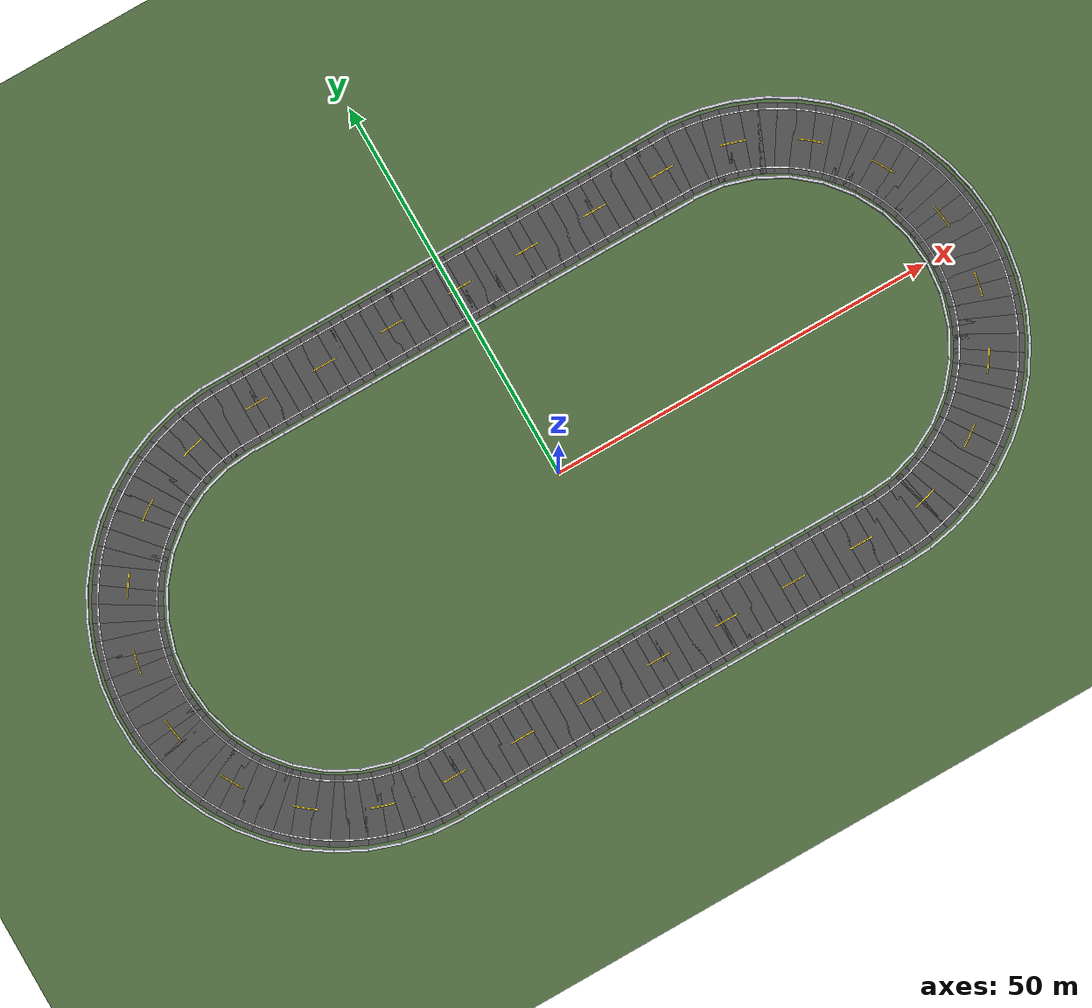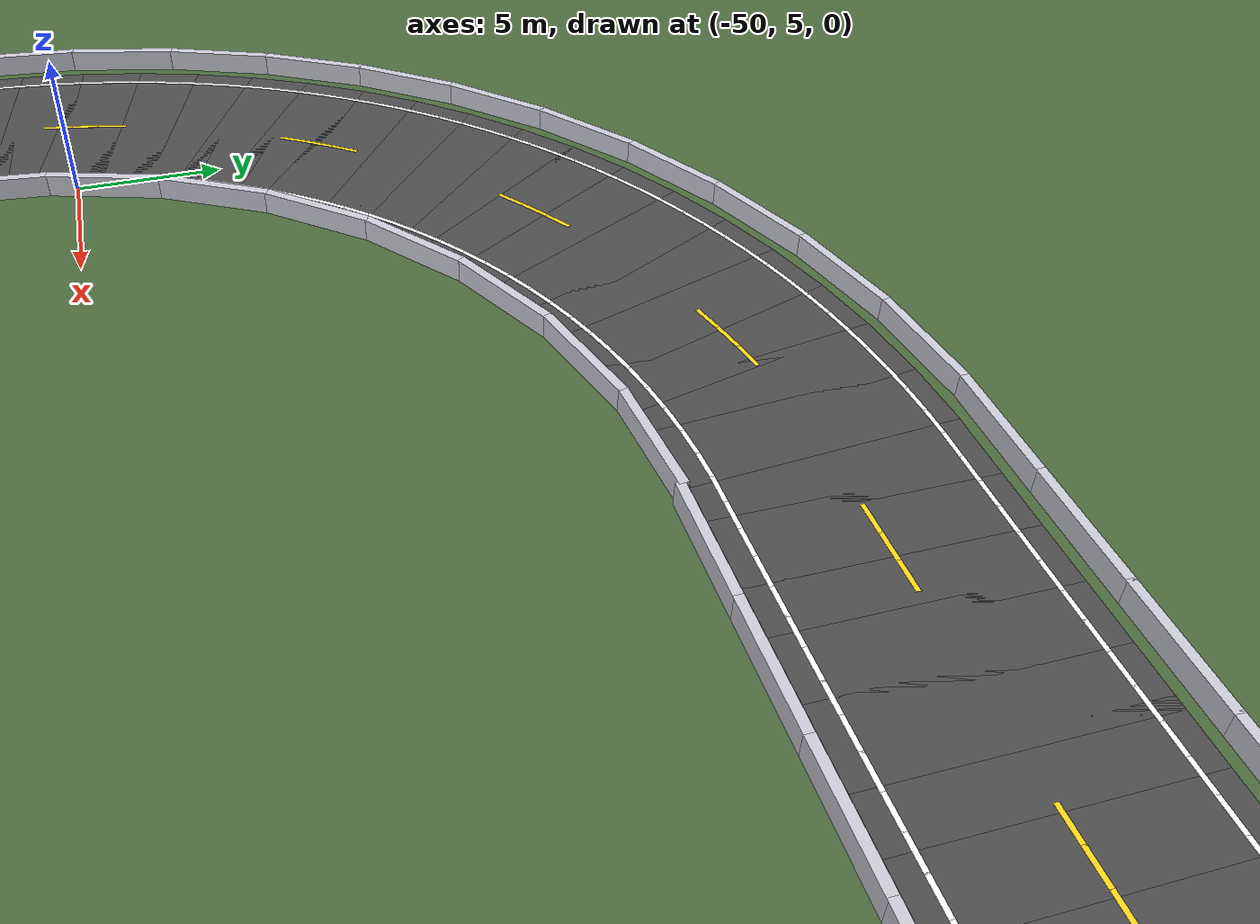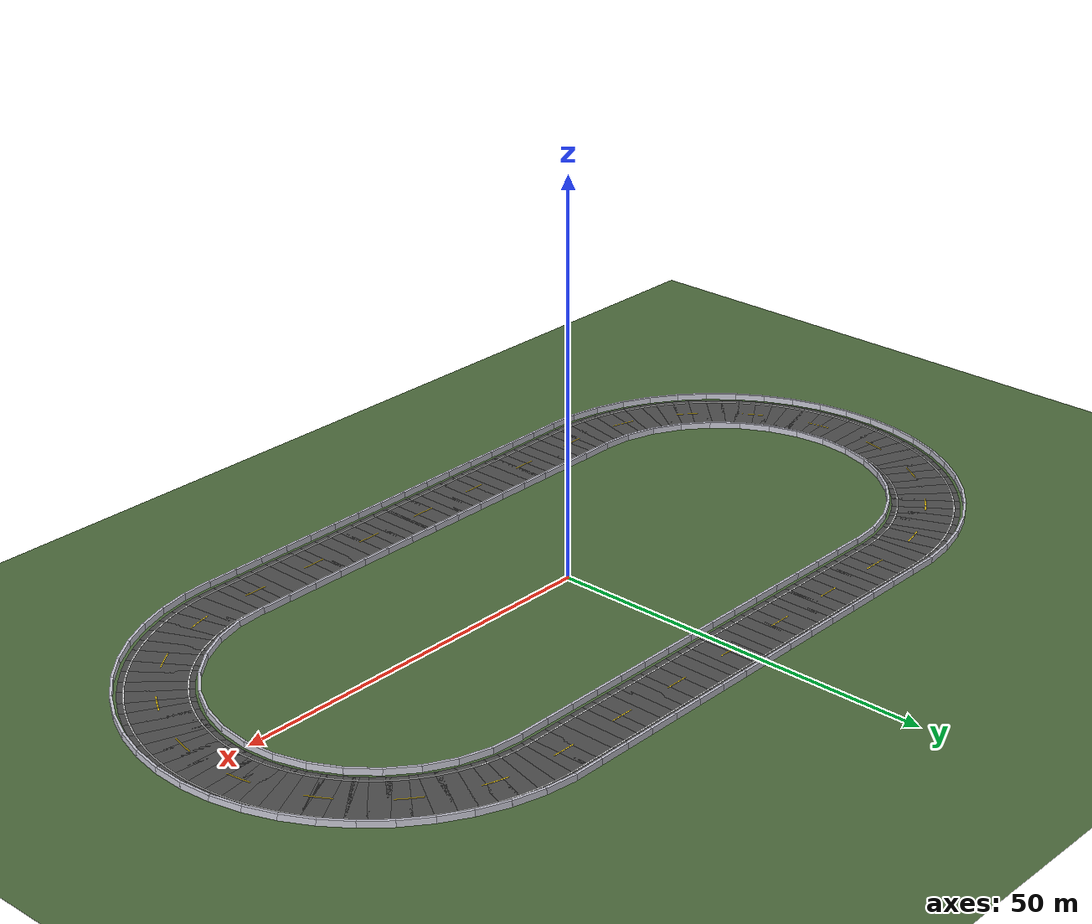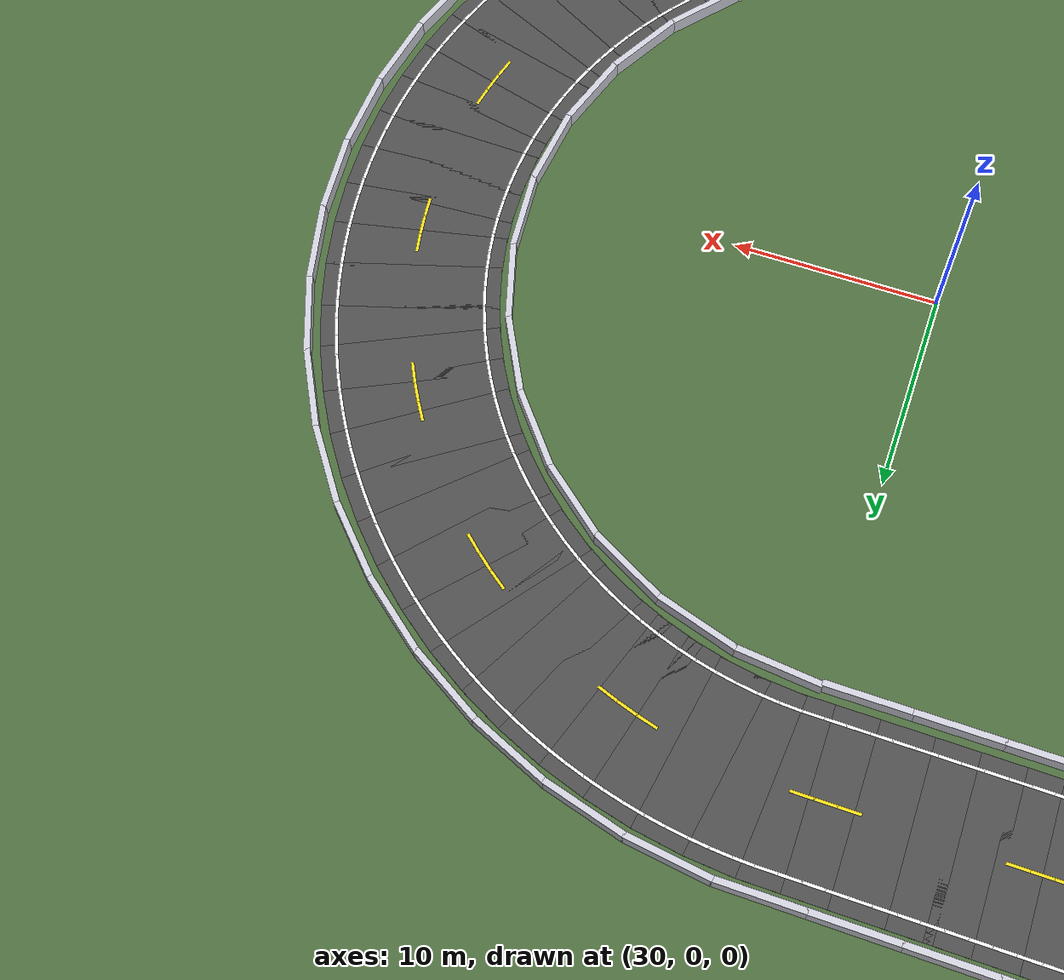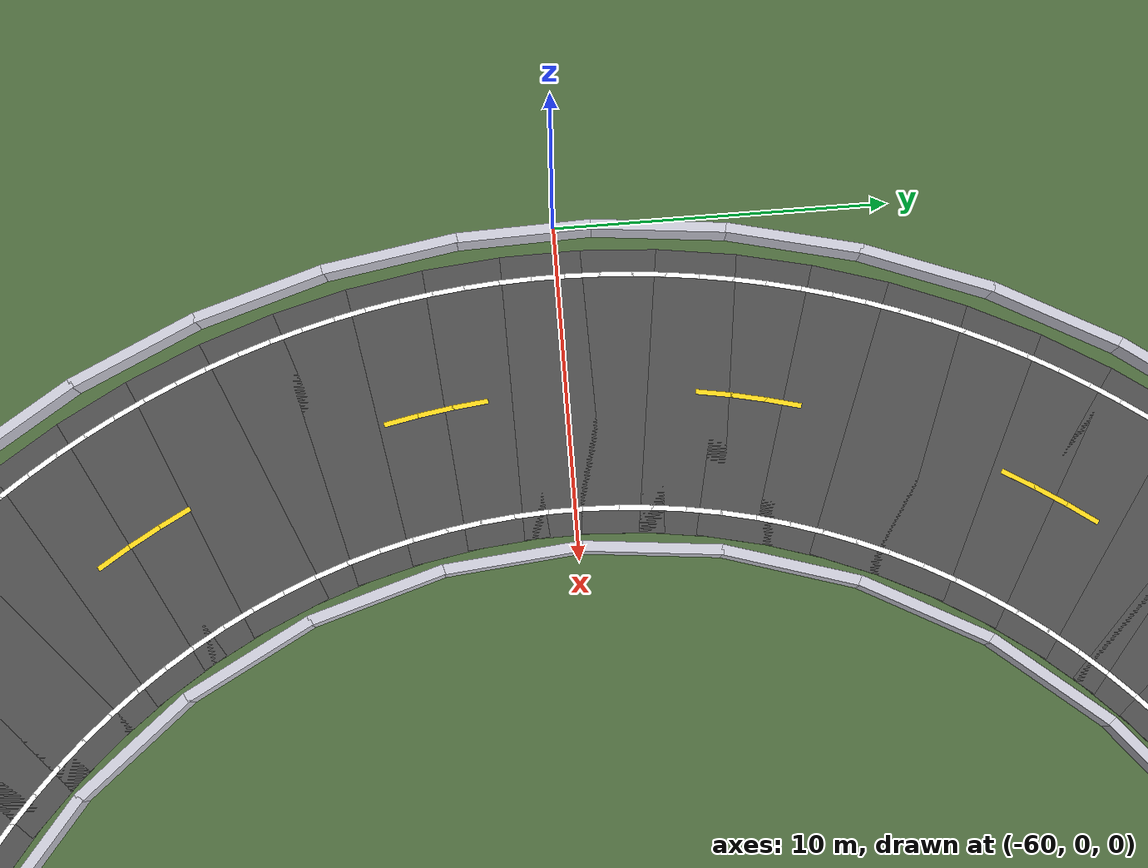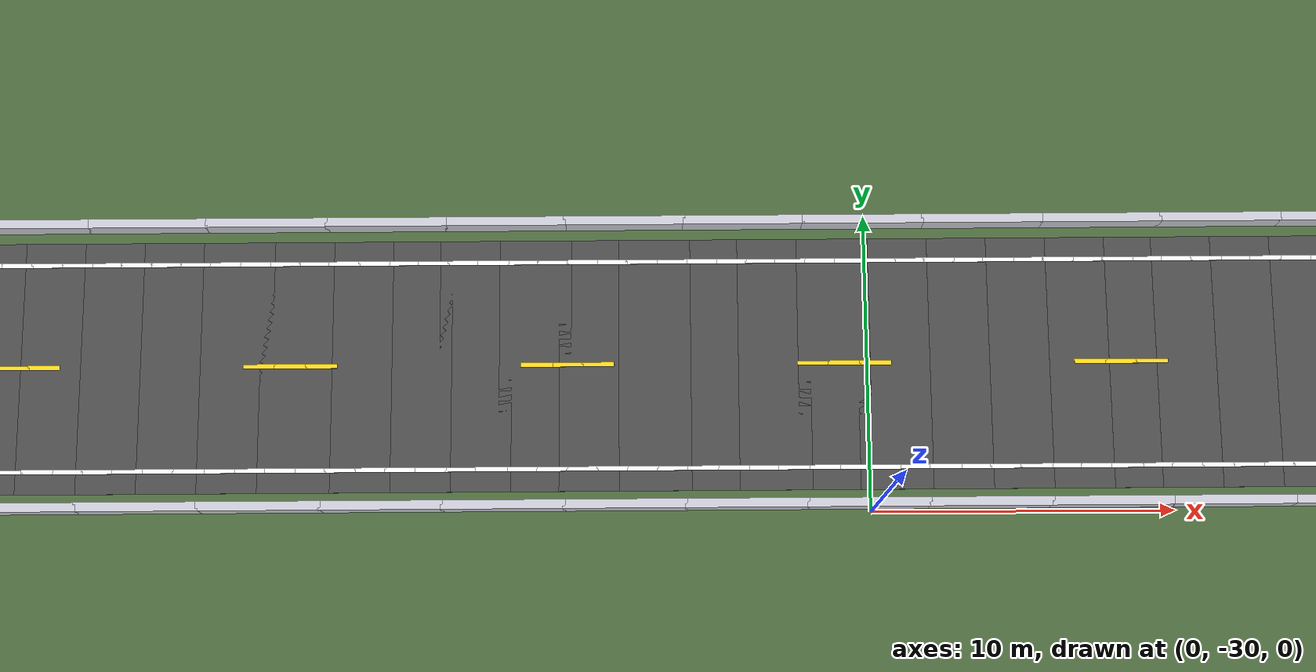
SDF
<sdf version="1.6">
 <world name="otoban">
  <physics name="varsayilan" type="ode">
   <max_step_size>0.001</max_step_size>
   <real_time_update_rate>1000</real_time_update_rate>
   <real_time_factor>1</real_time_factor>
   <ode>
    <solver><type>quick</type><iters>50</iters><sor>1.3</sor></solver>
    <constraints>
     <cfm>0</cfm>
     <erp>0.2</erp>
     <contact_max_correcting_vel>100</contact_max_correcting_vel>
     <contact_surface_layer>0.001</contact_surface_layer>
    </constraints>
   </ode>
  </physics>
  <plugin name="gazebo_ros_state" filename="libgazebo_ros_state.so">
   <ros><namespace>/gazebo</namespace></ros>
   <update_rate>50.0</update_rate>
  </plugin>
  <scene><ambient>0.6 0.6 0.6 1</ambient><background>0.7 0.8 0.9 1</background><shadows>0</shadows></scene>
  <light name="gunes" type="directional">
   <cast_shadows>0</cast_shadows>
   <pose>0 0 80 0 0 0</pose>
   <diffuse>0.9 0.9 0.9 1</diffuse>
   <specular>0.2 0.2 0.2 1</specular>
   <direction>-0.2 0.15 -0.95</direction>
   <attenuation><range>2000</range><constant>0.9</constant><linear>0.01</linear></attenuation>
  </light>
  <model name="zemin">
   <static>1</static>
   <link name="link">
    <collision name="collision">
     <geometry><plane><normal>0 0 1</normal><size>138.5 138.5</size></plane></geometry>
     <surface><friction><ode><mu>1.0</mu><mu2>1.0</mu2></ode></friction></surface>
    </collision>
    <visual name="visual">
     <cast_shadows>false</cast_shadows>
     <geometry><plane><normal>0 0 1</normal><size>138.5 138.5</size></plane></geometry>
     <material><ambient>0.25 0.35 0.2 1</ambient><diffuse>0.3 0.42 0.24 1</diffuse></material>
    </visual>
   </link>
  </model>
  <model name="yol_yuzeyi">
   <static>1</static>
   <link name="link">
    <visual name="v0">
     <pose>-29.0033 -25.0000 0.0050 0 0 0.00000</pose>
     <cast_shadows>false</cast_shadows>
     <geometry><box><size>2.4022 8.5000 0.0100</size></box></geometry>
     <material>
      <script>
       <uri>model://asphalt_plane/materials/scripts</uri>
       <uri>model://asphalt_plane/materials/textures</uri>
       <name>vrc/asphalt</name>
      </script>
     </material>
    </visual>
    <visual name="v1">
     <pose>-27.0099 -25.0000 0.0050 0 0 0.00000</pose>
     <cast_shadows>false</cast_shadows>
     <geometry><box><size>2.4022 8.5000 0.0100</size></box></geometry>
     <material>
      <script>
       <uri>model://asphalt_plane/materials/scripts</uri>
       <uri>model://asphalt_plane/materials/textures</uri>
       <name>vrc/asphalt</name>
      </script>
     </material>
    </visual>
    <visual name="v2">
     <pose>-25.0166 -25.0000 0.0050 0 0 0.00000</pose>
     <cast_shadows>false</cast_shadows>
     <geometry><box><size>2.4022 8.5000 0.0100</size></box></geometry>
     <material>
      <script>
       <uri>model://asphalt_plane/materials/scripts</uri>
       <uri>model://asphalt_plane/materials/textures</uri>
       <name>vrc/asphalt</name>
      </script>
     </material>
    </visual>
    <visual name="v3">
     <pose>-23.0232 -25.0000 0.0050 0 0 0.00000</pose>
     <cast_shadows>false</cast_shadows>
     <geometry><box><size>2.4022 8.5000 0.0100</size></box></geometry>
     <material>
      <script>
       <uri>model://asphalt_plane/materials/scripts</uri>
       <uri>model://asphalt_plane/materials/textures</uri>
       <name>vrc/asphalt</name>
      </script>
     </material>
    </visual>
    <visual name="v4">
     <pose>-21.0298 -25.0000 0.0050 0 0 0.00000</pose>
     <cast_shadows>false</cast_shadows>
     <geometry><box><size>2.4022 8.5000 0.0100</size></box></geometry>
     <material>
      <script>
       <uri>model://asphalt_plane/materials/scripts</uri>
       <uri>model://asphalt_plane/materials/textures</uri>
       <name>vrc/asphalt</name>
      </script>
     </material>
    </visual>
    <visual name="v5">
     <pose>-19.0364 -25.0000 0.0050 0 0 0.00000</pose>
     <cast_shadows>false</cast_shadows>
     <geometry><box><size>2.4022 8.5000 0.0100</size></box></geometry>
     <material>
      <script>
       <uri>model://asphalt_plane/materials/scripts</uri>
       <uri>model://asphalt_plane/materials/textures</uri>
       <name>vrc/asphalt</name>
      </script>
     </material>
    </visual>
    <visual name="v6">
     <pose>-17.0430 -25.0000 0.0050 0 0 0.00000</pose>
     <cast_shadows>false</cast_shadows>
     <geometry><box><size>2.4022 8.5000 0.0100</size></box></geometry>
     <material>
      <script>
       <uri>model://asphalt_plane/materials/scripts</uri>
       <uri>model://asphalt_plane/materials/textures</uri>
       <name>vrc/asphalt</name>
      </script>
     </material>
    </visual>
    <visual name="v7">
     <pose>-15.0497 -25.0000 0.0050 0 0 0.00000</pose>
     <cast_shadows>false</cast_shadows>
     <geometry><box><size>2.4022 8.5000 0.0100</size></box></geometry>
     <material>
      <script>
       <uri>model://asphalt_plane/materials/scripts</uri>
       <uri>model://asphalt_plane/materials/textures</uri>
       <name>vrc/asphalt</name>
      </script>
     </material>
    </visual>
    <visual name="v8">
     <pose>-13.0563 -25.0000 0.0050 0 0 0.00000</pose>
     <cast_shadows>false</cast_shadows>
     <geometry><box><size>2.4022 8.5000 0.0100</size></box></geometry>
     <material>
      <script>
       <uri>model://asphalt_plane/materials/scripts</uri>
       <uri>model://asphalt_plane/materials/textures</uri>
       <name>vrc/asphalt</name>
      </script>
     </material>
    </visual>
    <visual name="v9">
     <pose>-11.0629 -25.0000 0.0050 0 0 0.00000</pose>
     <cast_shadows>false</cast_shadows>
     <geometry><box><size>2.4022 8.5000 0.0100</size></box></geometry>
     <material>
      <script>
       <uri>model://asphalt_plane/materials/scripts</uri>
       <uri>model://asphalt_plane/materials/textures</uri>
       <name>vrc/asphalt</name>
      </script>
     </material>
    </visual>
    <visual name="v10">
     <pose>-9.0695 -25.0000 0.0050 0 0 0.00000</pose>
     <cast_shadows>false</cast_shadows>
     <geometry><box><size>2.4022 8.5000 0.0100</size></box></geometry>
     <material>
      <script>
       <uri>model://asphalt_plane/materials/scripts</uri>
       <uri>model://asphalt_plane/materials/textures</uri>
       <name>vrc/asphalt</name>
      </script>
     </material>
    </visual>
    <visual name="v11">
     <pose>-7.0761 -25.0000 0.0050 0 0 0.00000</pose>
     <cast_shadows>false</cast_shadows>
     <geometry><box><size>2.4022 8.5000 0.0100</size></box></geometry>
     <material>
      <script>
       <uri>model://asphalt_plane/materials/scripts</uri>
       <uri>model://asphalt_plane/materials/textures</uri>
       <name>vrc/asphalt</name>
      </script>
     </material>
    </visual>
    <visual name="v12">
     <pose>-5.0828 -25.0000 0.0050 0 0 0.00000</pose>
     <cast_shadows>false</cast_shadows>
     <geometry><box><size>2.4022 8.5000 0.0100</size></box></geometry>
     <material>
      <script>
       <uri>model://asphalt_plane/materials/scripts</uri>
       <uri>model://asphalt_plane/materials/textures</uri>
       <name>vrc/asphalt</name>
      </script>
     </material>
    </visual>
    <visual name="v13">
     <pose>-3.0894 -25.0000 0.0050 0 0 0.00000</pose>
     <cast_shadows>false</cast_shadows>
     <geometry><box><size>2.4022 8.5000 0.0100</size></box></geometry>
     <material>
      <script>
       <uri>model://asphalt_plane/materials/scripts</uri>
       <uri>model://asphalt_plane/materials/textures</uri>
       <name>vrc/asphalt</name>
      </script>
     </material>
    </visual>
    <visual name="v14">
     <pose>-1.0960 -25.0000 0.0050 0 0 0.00000</pose>
     <cast_shadows>false</cast_shadows>
     <geometry><box><size>2.4022 8.5000 0.0100</size></box></geometry>
     <material>
      <script>
       <uri>model://asphalt_plane/materials/scripts</uri>
       <uri>model://asphalt_plane/materials/textures</uri>
       <name>vrc/asphalt</name>
      </script>
     </material>
    </visual>
    <visual name="v15">
     <pose>0.8974 -25.0000 0.0050 0 0 0.00000</pose>
     <cast_shadows>false</cast_shadows>
     <geometry><box><size>2.4022 8.5000 0.0100</size></box></geometry>
     <material>
      <script>
       <uri>model://asphalt_plane/materials/scripts</uri>
       <uri>model://asphalt_plane/materials/textures</uri>
       <name>vrc/asphalt</name>
      </script>
     </material>
    </visual>
    <visual name="v16">
     <pose>2.8907 -25.0000 0.0050 0 0 0.00000</pose>
     <cast_shadows>false</cast_shadows>
     <geometry><box><size>2.4022 8.5000 0.0100</size></box></geometry>
     <material>
      <script>
       <uri>model://asphalt_plane/materials/scripts</uri>
       <uri>model://asphalt_plane/materials/textures</uri>
       <name>vrc/asphalt</name>
      </script>
     </material>
    </visual>
    <visual name="v17">
     <pose>4.8841 -25.0000 0.0050 0 0 0.00000</pose>
     <cast_shadows>false</cast_shadows>
     <geometry><box><size>2.4022 8.5000 0.0100</size></box></geometry>
     <material>
      <script>
       <uri>model://asphalt_plane/materials/scripts</uri>
       <uri>model://asphalt_plane/materials/textures</uri>
       <name>vrc/asphalt</name>
      </script>
     </material>
    </visual>
    <visual name="v18">
     <pose>6.8775 -25.0000 0.0050 0 0 0.00000</pose>
     <cast_shadows>false</cast_shadows>
     <geometry><box><size>2.4022 8.5000 0.0100</size></box></geometry>
     <material>
      <script>
       <uri>model://asphalt_plane/materials/scripts</uri>
       <uri>model://asphalt_plane/materials/textures</uri>
       <name>vrc/asphalt</name>
      </script>
     </material>
    </visual>
    <visual name="v19">
     <pose>8.8709 -25.0000 0.0050 0 0 0.00000</pose>
     <cast_shadows>false</cast_shadows>
     <geometry><box><size>2.4022 8.5000 0.0100</size></box></geometry>
     <material>
      <script>
       <uri>model://asphalt_plane/materials/scripts</uri>
       <uri>model://asphalt_plane/materials/textures</uri>
       <name>vrc/asphalt</name>
      </script>
     </material>
    </visual>
    <visual name="v20">
     <pose>10.8643 -25.0000 0.0050 0 0 0.00000</pose>
     <cast_shadows>false</cast_shadows>
     <geometry><box><size>2.4022 8.5000 0.0100</size></box></geometry>
     <material>
      <script>
       <uri>model://asphalt_plane/materials/scripts</uri>
       <uri>model://asphalt_plane/materials/textures</uri>
       <name>vrc/asphalt</name>
      </script>
     </material>
    </visual>
    <visual name="v21">
     <pose>12.8576 -25.0000 0.0050 0 0 0.00000</pose>
     <cast_shadows>false</cast_shadows>
     <geometry><box><size>2.4022 8.5000 0.0100</size></box></geometry>
     <material>
      <script>
       <uri>model://asphalt_plane/materials/scripts</uri>
       <uri>model://asphalt_plane/materials/textures</uri>
       <name>vrc/asphalt</name>
      </script>
     </material>
    </visual>
    <visual name="v22">
     <pose>14.8510 -25.0000 0.0050 0 0 0.00000</pose>
     <cast_shadows>false</cast_shadows>
     <geometry><box><size>2.4022 8.5000 0.0100</size></box></geometry>
     <material>
      <script>
       <uri>model://asphalt_plane/materials/scripts</uri>
       <uri>model://asphalt_plane/materials/textures</uri>
       <name>vrc/asphalt</name>
      </script>
     </material>
    </visual>
    <visual name="v23">
     <pose>16.8444 -25.0000 0.0050 0 0 0.00000</pose>
     <cast_shadows>false</cast_shadows>
     <geometry><box><size>2.4022 8.5000 0.0100</size></box></geometry>
     <material>
      <script>
       <uri>model://asphalt_plane/materials/scripts</uri>
       <uri>model://asphalt_plane/materials/textures</uri>
       <name>vrc/asphalt</name>
      </script>
     </material>
    </visual>
    <visual name="v24">
     <pose>18.8378 -25.0000 0.0050 0 0 0.00000</pose>
     <cast_shadows>false</cast_shadows>
     <geometry><box><size>2.4022 8.5000 0.0100</size></box></geometry>
     <material>
      <script>
       <uri>model://asphalt_plane/materials/scripts</uri>
       <uri>model://asphalt_plane/materials/textures</uri>
       <name>vrc/asphalt</name>
      </script>
     </material>
    </visual>
    <visual name="v25">
     <pose>20.8312 -25.0000 0.0050 0 0 0.00000</pose>
     <cast_shadows>false</cast_shadows>
     <geometry><box><size>2.4022 8.5000 0.0100</size></box></geometry>
     <material>
      <script>
       <uri>model://asphalt_plane/materials/scripts</uri>
       <uri>model://asphalt_plane/materials/textures</uri>
       <name>vrc/asphalt</name>
      </script>
     </material>
    </visual>
    <visual name="v26">
     <pose>22.8245 -25.0000 0.0050 0 0 0.00000</pose>
     <cast_shadows>false</cast_shadows>
     <geometry><box><size>2.4022 8.5000 0.0100</size></box></geometry>
     <material>
      <script>
       <uri>model://asphalt_plane/materials/scripts</uri>
       <uri>model://asphalt_plane/materials/textures</uri>
       <name>vrc/asphalt</name>
      </script>
     </material>
    </visual>
    <visual name="v27">
     <pose>24.8179 -25.0000 0.0050 0 0 0.00000</pose>
     <cast_shadows>false</cast_shadows>
     <geometry><box><size>2.4022 8.5000 0.0100</size></box></geometry>
     <material>
      <script>
       <uri>model://asphalt_plane/materials/scripts</uri>
       <uri>model://asphalt_plane/materials/textures</uri>
       <name>vrc/asphalt</name>
      </script>
     </material>
    </visual>
    <visual name="v28">
     <pose>26.8113 -25.0000 0.0050 0 0 0.00000</pose>
     <cast_shadows>false</cast_shadows>
     <geometry><box><size>2.4022 8.5000 0.0100</size></box></geometry>
     <material>
      <script>
       <uri>model://asphalt_plane/materials/scripts</uri>
       <uri>model://asphalt_plane/materials/textures</uri>
       <name>vrc/asphalt</name>
      </script>
     </material>
    </visual>
    <visual name="v29">
     <pose>28.8047 -25.0000 0.0050 0 0 0.00000</pose>
     <cast_shadows>false</cast_shadows>
     <geometry><box><size>2.4022 8.5000 0.0100</size></box></geometry>
     <material>
      <script>
       <uri>model://asphalt_plane/materials/scripts</uri>
       <uri>model://asphalt_plane/materials/textures</uri>
       <name>vrc/asphalt</name>
      </script>
     </material>
    </visual>
    <visual name="v30">
     <pose>30.7979 -24.9873 0.0050 0 0 0.03192</pose>
     <cast_shadows>false</cast_shadows>
     <geometry><box><size>2.4022 8.5000 0.0100</size></box></geometry>
     <material>
      <script>
       <uri>model://asphalt_plane/materials/scripts</uri>
       <uri>model://asphalt_plane/materials/textures</uri>
       <name>vrc/asphalt</name>
      </script>
     </material>
    </visual>
    <visual name="v31">
     <pose>32.7856 -24.8443 0.0050 0 0 0.11166</pose>
     <cast_shadows>false</cast_shadows>
     <geometry><box><size>2.4022 8.5000 0.0100</size></box></geometry>
     <material>
      <script>
       <uri>model://asphalt_plane/materials/scripts</uri>
       <uri>model://asphalt_plane/materials/textures</uri>
       <name>vrc/asphalt</name>
      </script>
     </material>
    </visual>
    <visual name="v32">
     <pose>34.7556 -24.5435 0.0050 0 0 0.19139</pose>
     <cast_shadows>false</cast_shadows>
     <geometry><box><size>2.4022 8.5000 0.0100</size></box></geometry>
     <material>
      <script>
       <uri>model://asphalt_plane/materials/scripts</uri>
       <uri>model://asphalt_plane/materials/textures</uri>
       <name>vrc/asphalt</name>
      </script>
     </material>
    </visual>
    <visual name="v33">
     <pose>36.6954 -24.0867 0.0050 0 0 0.27113</pose>
     <cast_shadows>false</cast_shadows>
     <geometry><box><size>2.4022 8.5000 0.0100</size></box></geometry>
     <material>
      <script>
       <uri>model://asphalt_plane/materials/scripts</uri>
       <uri>model://asphalt_plane/materials/textures</uri>
       <name>vrc/asphalt</name>
      </script>
     </material>
    </visual>
    <visual name="v34">
     <pose>38.5927 -23.4769 0.0050 0 0 0.35086</pose>
     <cast_shadows>false</cast_shadows>
     <geometry><box><size>2.4022 8.5000 0.0100</size></box></geometry>
     <material>
      <script>
       <uri>model://asphalt_plane/materials/scripts</uri>
       <uri>model://asphalt_plane/materials/textures</uri>
       <name>vrc/asphalt</name>
      </script>
     </material>
    </visual>
    <visual name="v35">
     <pose>40.4354 -22.7179 0.0050 0 0 0.43060</pose>
     <cast_shadows>false</cast_shadows>
     <geometry><box><size>2.4022 8.5000 0.0100</size></box></geometry>
     <material>
      <script>
       <uri>model://asphalt_plane/materials/scripts</uri>
       <uri>model://asphalt_plane/materials/textures</uri>
       <name>vrc/asphalt</name>
      </script>
     </material>
    </visual>
    <visual name="v36">
     <pose>42.2117 -21.8145 0.0050 0 0 0.51033</pose>
     <cast_shadows>false</cast_shadows>
     <geometry><box><size>2.4022 8.5000 0.0100</size></box></geometry>
     <material>
      <script>
       <uri>model://asphalt_plane/materials/scripts</uri>
       <uri>model://asphalt_plane/materials/textures</uri>
       <name>vrc/asphalt</name>
      </script>
     </material>
    </visual>
    <visual name="v37">
     <pose>43.9104 -20.7726 0.0050 0 0 0.59007</pose>
     <cast_shadows>false</cast_shadows>
     <geometry><box><size>2.4022 8.5000 0.0100</size></box></geometry>
     <material>
      <script>
       <uri>model://asphalt_plane/materials/scripts</uri>
       <uri>model://asphalt_plane/materials/textures</uri>
       <name>vrc/asphalt</name>
      </script>
     </material>
    </visual>
    <visual name="v38">
     <pose>45.5208 -19.5986 0.0050 0 0 0.66980</pose>
     <cast_shadows>false</cast_shadows>
     <geometry><box><size>2.4022 8.5000 0.0100</size></box></geometry>
     <material>
      <script>
       <uri>model://asphalt_plane/materials/scripts</uri>
       <uri>model://asphalt_plane/materials/textures</uri>
       <name>vrc/asphalt</name>
      </script>
     </material>
    </visual>
    <visual name="v39">
     <pose>47.0325 -18.3001 0.0050 0 0 0.74954</pose>
     <cast_shadows>false</cast_shadows>
     <geometry><box><size>2.4022 8.5000 0.0100</size></box></geometry>
     <material>
      <script>
       <uri>model://asphalt_plane/materials/scripts</uri>
       <uri>model://asphalt_plane/materials/textures</uri>
       <name>vrc/asphalt</name>
      </script>
     </material>
    </visual>
    <visual name="v40">
     <pose>48.4360 -16.8853 0.0050 0 0 0.82927</pose>
     <cast_shadows>false</cast_shadows>
     <geometry><box><size>2.4022 8.5000 0.0100</size></box></geometry>
     <material>
      <script>
       <uri>model://asphalt_plane/materials/scripts</uri>
       <uri>model://asphalt_plane/materials/textures</uri>
       <name>vrc/asphalt</name>
      </script>
     </material>
    </visual>
    <visual name="v41">
     <pose>49.7224 -15.3632 0.0050 0 0 0.90901</pose>
     <cast_shadows>false</cast_shadows>
     <geometry><box><size>2.4022 8.5000 0.0100</size></box></geometry>
     <material>
      <script>
       <uri>model://asphalt_plane/materials/scripts</uri>
       <uri>model://asphalt_plane/materials/textures</uri>
       <name>vrc/asphalt</name>
      </script>
     </material>
    </visual>
    <visual name="v42">
     <pose>50.8834 -13.7435 0.0050 0 0 0.98874</pose>
     <cast_shadows>false</cast_shadows>
     <geometry><box><size>2.4022 8.5000 0.0100</size></box></geometry>
     <material>
      <script>
       <uri>model://asphalt_plane/materials/scripts</uri>
       <uri>model://asphalt_plane/materials/textures</uri>
       <name>vrc/asphalt</name>
      </script>
     </material>
    </visual>
    <visual name="v43">
     <pose>51.9117 -12.0365 0.0050 0 0 1.06848</pose>
     <cast_shadows>false</cast_shadows>
     <geometry><box><size>2.4022 8.5000 0.0100</size></box></geometry>
     <material>
      <script>
       <uri>model://asphalt_plane/materials/scripts</uri>
       <uri>model://asphalt_plane/materials/textures</uri>
       <name>vrc/asphalt</name>
      </script>
     </material>
    </visual>
    <visual name="v44">
     <pose>52.8008 -10.2529 0.0050 0 0 1.14821</pose>
     <cast_shadows>false</cast_shadows>
     <geometry><box><size>2.4022 8.5000 0.0100</size></box></geometry>
     <material>
      <script>
       <uri>model://asphalt_plane/materials/scripts</uri>
       <uri>model://asphalt_plane/materials/textures</uri>
       <name>vrc/asphalt</name>
      </script>
     </material>
    </visual>
    <visual name="v45">
     <pose>53.5450 -8.4042 0.0050 0 0 1.22795</pose>
     <cast_shadows>false</cast_shadows>
     <geometry><box><size>2.4022 8.5000 0.0100</size></box></geometry>
     <material>
      <script>
       <uri>model://asphalt_plane/materials/scripts</uri>
       <uri>model://asphalt_plane/materials/textures</uri>
       <name>vrc/asphalt</name>
      </script>
     </material>
    </visual>
    <visual name="v46">
     <pose>54.1396 -6.5022 0.0050 0 0 1.30768</pose>
     <cast_shadows>false</cast_shadows>
     <geometry><box><size>2.4022 8.5000 0.0100</size></box></geometry>
     <material>
      <script>
       <uri>model://asphalt_plane/materials/scripts</uri>
       <uri>model://asphalt_plane/materials/textures</uri>
       <name>vrc/asphalt</name>
      </script>
     </material>
    </visual>
    <visual name="v47">
     <pose>54.5808 -4.5588 0.0050 0 0 1.38742</pose>
     <cast_shadows>false</cast_shadows>
     <geometry><box><size>2.4022 8.5000 0.0100</size></box></geometry>
     <material>
      <script>
       <uri>model://asphalt_plane/materials/scripts</uri>
       <uri>model://asphalt_plane/materials/textures</uri>
       <name>vrc/asphalt</name>
      </script>
     </material>
    </visual>
    <visual name="v48">
     <pose>54.8659 -2.5864 0.0050 0 0 1.46715</pose>
     <cast_shadows>false</cast_shadows>
     <geometry><box><size>2.4022 8.5000 0.0100</size></box></geometry>
     <material>
      <script>
       <uri>model://asphalt_plane/materials/scripts</uri>
       <uri>model://asphalt_plane/materials/textures</uri>
       <name>vrc/asphalt</name>
      </script>
     </material>
    </visual>
    <visual name="v49">
     <pose>54.9929 -0.5976 0.0050 0 0 1.54689</pose>
     <cast_shadows>false</cast_shadows>
     <geometry><box><size>2.4022 8.5000 0.0100</size></box></geometry>
     <material>
      <script>
       <uri>model://asphalt_plane/materials/scripts</uri>
       <uri>model://asphalt_plane/materials/textures</uri>
       <name>vrc/asphalt</name>
      </script>
     </material>
    </visual>
    <visual name="v50">
     <pose>54.9610 1.3950 0.0050 0 0 1.62662</pose>
     <cast_shadows>false</cast_shadows>
     <geometry><box><size>2.4022 8.5000 0.0100</size></box></geometry>
     <material>
      <script>
       <uri>model://asphalt_plane/materials/scripts</uri>
       <uri>model://asphalt_plane/materials/textures</uri>
       <name>vrc/asphalt</name>
      </script>
     </material>
    </visual>
    <visual name="v51">
     <pose>54.7706 3.3787 0.0050 0 0 1.70636</pose>
     <cast_shadows>false</cast_shadows>
     <geometry><box><size>2.4022 8.5000 0.0100</size></box></geometry>
     <material>
      <script>
       <uri>model://asphalt_plane/materials/scripts</uri>
       <uri>model://asphalt_plane/materials/textures</uri>
       <name>vrc/asphalt</name>
      </script>
     </material>
    </visual>
    <visual name="v52">
     <pose>54.4228 5.3410 0.0050 0 0 1.78610</pose>
     <cast_shadows>false</cast_shadows>
     <geometry><box><size>2.4022 8.5000 0.0100</size></box></geometry>
     <material>
      <script>
       <uri>model://asphalt_plane/materials/scripts</uri>
       <uri>model://asphalt_plane/materials/textures</uri>
       <name>vrc/asphalt</name>
      </script>
     </material>
    </visual>
    <visual name="v53">
     <pose>53.9198 7.2693 0.0050 0 0 1.86583</pose>
     <cast_shadows>false</cast_shadows>
     <geometry><box><size>2.4022 8.5000 0.0100</size></box></geometry>
     <material>
      <script>
       <uri>model://asphalt_plane/materials/scripts</uri>
       <uri>model://asphalt_plane/materials/textures</uri>
       <name>vrc/asphalt</name>
      </script>
     </material>
    </visual>
    <visual name="v54">
     <pose>53.2648 9.1514 0.0050 0 0 1.94557</pose>
     <cast_shadows>false</cast_shadows>
     <geometry><box><size>2.4022 8.5000 0.0100</size></box></geometry>
     <material>
      <script>
       <uri>model://asphalt_plane/materials/scripts</uri>
       <uri>model://asphalt_plane/materials/textures</uri>
       <name>vrc/asphalt</name>
      </script>
     </material>
    </visual>
    <visual name="v55">
     <pose>52.4620 10.9754 0.0050 0 0 2.02530</pose>
     <cast_shadows>false</cast_shadows>
     <geometry><box><size>2.4022 8.5000 0.0100</size></box></geometry>
     <material>
      <script>
       <uri>model://asphalt_plane/materials/scripts</uri>
       <uri>model://asphalt_plane/materials/textures</uri>
       <name>vrc/asphalt</name>
      </script>
     </material>
    </visual>
    <visual name="v56">
     <pose>51.5164 12.7297 0.0050 0 0 2.10504</pose>
     <cast_shadows>false</cast_shadows>
     <geometry><box><size>2.4022 8.5000 0.0100</size></box></geometry>
     <material>
      <script>
       <uri>model://asphalt_plane/materials/scripts</uri>
       <uri>model://asphalt_plane/materials/textures</uri>
       <name>vrc/asphalt</name>
      </script>
     </material>
    </visual>
    <visual name="v57">
     <pose>50.4341 14.4030 0.0050 0 0 2.18477</pose>
     <cast_shadows>false</cast_shadows>
     <geometry><box><size>2.4022 8.5000 0.0100</size></box></geometry>
     <material>
      <script>
       <uri>model://asphalt_plane/materials/scripts</uri>
       <uri>model://asphalt_plane/materials/textures</uri>
       <name>vrc/asphalt</name>
      </script>
     </material>
    </visual>
    <visual name="v58">
     <pose>49.2220 15.9848 0.0050 0 0 2.26451</pose>
     <cast_shadows>false</cast_shadows>
     <geometry><box><size>2.4022 8.5000 0.0100</size></box></geometry>
     <material>
      <script>
       <uri>model://asphalt_plane/materials/scripts</uri>
       <uri>model://asphalt_plane/materials/textures</uri>
       <name>vrc/asphalt</name>
      </script>
     </material>
    </visual>
    <visual name="v59">
     <pose>47.8877 17.4651 0.0050 0 0 2.34424</pose>
     <cast_shadows>false</cast_shadows>
     <geometry><box><size>2.4022 8.5000 0.0100</size></box></geometry>
     <material>
      <script>
       <uri>model://asphalt_plane/materials/scripts</uri>
       <uri>model://asphalt_plane/materials/textures</uri>
       <name>vrc/asphalt</name>
      </script>
     </material>
    </visual>
    <visual name="v60">
     <pose>46.4398 18.8344 0.0050 0 0 2.42398</pose>
     <cast_shadows>false</cast_shadows>
     <geometry><box><size>2.4022 8.5000 0.0100</size></box></geometry>
     <material>
      <script>
       <uri>model://asphalt_plane/materials/scripts</uri>
       <uri>model://asphalt_plane/materials/textures</uri>
       <name>vrc/asphalt</name>
      </script>
     </material>
    </visual>
    <visual name="v61">
     <pose>44.8874 20.0840 0.0050 0 0 2.50371</pose>
     <cast_shadows>false</cast_shadows>
     <geometry><box><size>2.4022 8.5000 0.0100</size></box></geometry>
     <material>
      <script>
       <uri>model://asphalt_plane/materials/scripts</uri>
       <uri>model://asphalt_plane/materials/textures</uri>
       <name>vrc/asphalt</name>
      </script>
     </material>
    </visual>
    <visual name="v62">
     <pose>43.2404 21.2060 0.0050 0 0 2.58345</pose>
     <cast_shadows>false</cast_shadows>
     <geometry><box><size>2.4022 8.5000 0.0100</size></box></geometry>
     <material>
      <script>
       <uri>model://asphalt_plane/materials/scripts</uri>
       <uri>model://asphalt_plane/materials/textures</uri>
       <name>vrc/asphalt</name>
      </script>
     </material>
    </visual>
    <visual name="v63">
     <pose>41.5092 22.1932 0.0050 0 0 2.66318</pose>
     <cast_shadows>false</cast_shadows>
     <geometry><box><size>2.4022 8.5000 0.0100</size></box></geometry>
     <material>
      <script>
       <uri>model://asphalt_plane/materials/scripts</uri>
       <uri>model://asphalt_plane/materials/textures</uri>
       <name>vrc/asphalt</name>
      </script>
     </material>
    </visual>
    <visual name="v64">
     <pose>39.7050 23.0394 0.0050 0 0 2.74292</pose>
     <cast_shadows>false</cast_shadows>
     <geometry><box><size>2.4022 8.5000 0.0100</size></box></geometry>
     <material>
      <script>
       <uri>model://asphalt_plane/materials/scripts</uri>
       <uri>model://asphalt_plane/materials/textures</uri>
       <name>vrc/asphalt</name>
      </script>
     </material>
    </visual>
    <visual name="v65">
     <pose>37.8390 23.7392 0.0050 0 0 2.82265</pose>
     <cast_shadows>false</cast_shadows>
     <geometry><box><size>2.4022 8.5000 0.0100</size></box></geometry>
     <material>
      <script>
       <uri>model://asphalt_plane/materials/scripts</uri>
       <uri>model://asphalt_plane/materials/textures</uri>
       <name>vrc/asphalt</name>
      </script>
     </material>
    </visual>
    <visual name="v66">
     <pose>35.9233 24.2882 0.0050 0 0 2.90239</pose>
     <cast_shadows>false</cast_shadows>
     <geometry><box><size>2.4022 8.5000 0.0100</size></box></geometry>
     <material>
      <script>
       <uri>model://asphalt_plane/materials/scripts</uri>
       <uri>model://asphalt_plane/materials/textures</uri>
       <name>vrc/asphalt</name>
      </script>
     </material>
    </visual>
    <visual name="v67">
     <pose>33.9699 24.6828 0.0050 0 0 2.98212</pose>
     <cast_shadows>false</cast_shadows>
     <geometry><box><size>2.4022 8.5000 0.0100</size></box></geometry>
     <material>
      <script>
       <uri>model://asphalt_plane/materials/scripts</uri>
       <uri>model://asphalt_plane/materials/textures</uri>
       <name>vrc/asphalt</name>
      </script>
     </material>
    </visual>
    <visual name="v68">
     <pose>31.9913 24.9206 0.0050 0 0 3.06186</pose>
     <cast_shadows>false</cast_shadows>
     <geometry><box><size>2.4022 8.5000 0.0100</size></box></geometry>
     <material>
      <script>
       <uri>model://asphalt_plane/materials/scripts</uri>
       <uri>model://asphalt_plane/materials/textures</uri>
       <name>vrc/asphalt</name>
      </script>
     </material>
    </visual>
    <visual name="v69">
     <pose>30.0000 25.0000 0.0050 0 0 3.14159</pose>
     <cast_shadows>false</cast_shadows>
     <geometry><box><size>2.4022 8.5000 0.0100</size></box></geometry>
     <material>
      <script>
       <uri>model://asphalt_plane/materials/scripts</uri>
       <uri>model://asphalt_plane/materials/textures</uri>
       <name>vrc/asphalt</name>
      </script>
     </material>
    </visual>
    <visual name="v70">
     <pose>28.0066 25.0000 0.0050 0 0 3.14159</pose>
     <cast_shadows>false</cast_shadows>
     <geometry><box><size>2.4022 8.5000 0.0100</size></box></geometry>
     <material>
      <script>
       <uri>model://asphalt_plane/materials/scripts</uri>
       <uri>model://asphalt_plane/materials/textures</uri>
       <name>vrc/asphalt</name>
      </script>
     </material>
    </visual>
    <visual name="v71">
     <pose>26.0132 25.0000 0.0050 0 0 3.14159</pose>
     <cast_shadows>false</cast_shadows>
     <geometry><box><size>2.4022 8.5000 0.0100</size></box></geometry>
     <material>
      <script>
       <uri>model://asphalt_plane/materials/scripts</uri>
       <uri>model://asphalt_plane/materials/textures</uri>
       <name>vrc/asphalt</name>
      </script>
     </material>
    </visual>
    <visual name="v72">
     <pose>24.0199 25.0000 0.0050 0 0 3.14159</pose>
     <cast_shadows>false</cast_shadows>
     <geometry><box><size>2.4022 8.5000 0.0100</size></box></geometry>
     <material>
      <script>
       <uri>model://asphalt_plane/materials/scripts</uri>
       <uri>model://asphalt_plane/materials/textures</uri>
       <name>vrc/asphalt</name>
      </script>
     </material>
    </visual>
    <visual name="v73">
     <pose>22.0265 25.0000 0.0050 0 0 3.14159</pose>
     <cast_shadows>false</cast_shadows>
     <geometry><box><size>2.4022 8.5000 0.0100</size></box></geometry>
     <material>
      <script>
       <uri>model://asphalt_plane/materials/scripts</uri>
       <uri>model://asphalt_plane/materials/textures</uri>
       <name>vrc/asphalt</name>
      </script>
     </material>
    </visual>
    <visual name="v74">
     <pose>20.0331 25.0000 0.0050 0 0 3.14159</pose>
     <cast_shadows>false</cast_shadows>
     <geometry><box><size>2.4022 8.5000 0.0100</size></box></geometry>
     <material>
      <script>
       <uri>model://asphalt_plane/materials/scripts</uri>
       <uri>model://asphalt_plane/materials/textures</uri>
       <name>vrc/asphalt</name>
      </script>
     </material>
    </visual>
    <visual name="v75">
     <pose>18.0397 25.0000 0.0050 0 0 3.14159</pose>
     <cast_shadows>false</cast_shadows>
     <geometry><box><size>2.4022 8.5000 0.0100</size></box></geometry>
     <material>
      <script>
       <uri>model://asphalt_plane/materials/scripts</uri>
       <uri>model://asphalt_plane/materials/textures</uri>
       <name>vrc/asphalt</name>
      </script>
     </material>
    </visual>
    <visual name="v76">
     <pose>16.0463 25.0000 0.0050 0 0 3.14159</pose>
     <cast_shadows>false</cast_shadows>
     <geometry><box><size>2.4022 8.5000 0.0100</size></box></geometry>
     <material>
      <script>
       <uri>model://asphalt_plane/materials/scripts</uri>
       <uri>model://asphalt_plane/materials/textures</uri>
       <name>vrc/asphalt</name>
      </script>
     </material>
    </visual>
    <visual name="v77">
     <pose>14.0530 25.0000 0.0050 0 0 3.14159</pose>
     <cast_shadows>false</cast_shadows>
     <geometry><box><size>2.4022 8.5000 0.0100</size></box></geometry>
     <material>
      <script>
       <uri>model://asphalt_plane/materials/scripts</uri>
       <uri>model://asphalt_plane/materials/textures</uri>
       <name>vrc/asphalt</name>
      </script>
     </material>
    </visual>
    <visual name="v78">
     <pose>12.0596 25.0000 0.0050 0 0 3.14159</pose>
     <cast_shadows>false</cast_shadows>
     <geometry><box><size>2.4022 8.5000 0.0100</size></box></geometry>
     <material>
      <script>
       <uri>model://asphalt_plane/materials/scripts</uri>
       <uri>model://asphalt_plane/materials/textures</uri>
       <name>vrc/asphalt</name>
      </script>
     </material>
    </visual>
    <visual name="v79">
     <pose>10.0662 25.0000 0.0050 0 0 3.14159</pose>
     <cast_shadows>false</cast_shadows>
     <geometry><box><size>2.4022 8.5000 0.0100</size></box></geometry>
     <material>
      <script>
       <uri>model://asphalt_plane/materials/scripts</uri>
       <uri>model://asphalt_plane/materials/textures</uri>
       <name>vrc/asphalt</name>
      </script>
     </material>
    </visual>
    <visual name="v80">
     <pose>8.0728 25.0000 0.0050 0 0 3.14159</pose>
     <cast_shadows>false</cast_shadows>
     <geometry><box><size>2.4022 8.5000 0.0100</size></box></geometry>
     <material>
      <script>
       <uri>model://asphalt_plane/materials/scripts</uri>
       <uri>model://asphalt_plane/materials/textures</uri>
       <name>vrc/asphalt</name>
      </script>
     </material>
    </visual>
    <visual name="v81">
     <pose>6.0795 25.0000 0.0050 0 0 3.14159</pose>
     <cast_shadows>false</cast_shadows>
     <geometry><box><size>2.4022 8.5000 0.0100</size></box></geometry>
     <material>
      <script>
       <uri>model://asphalt_plane/materials/scripts</uri>
       <uri>model://asphalt_plane/materials/textures</uri>
       <name>vrc/asphalt</name>
      </script>
     </material>
    </visual>
    <visual name="v82">
     <pose>4.0861 25.0000 0.0050 0 0 3.14159</pose>
     <cast_shadows>false</cast_shadows>
     <geometry><box><size>2.4022 8.5000 0.0100</size></box></geometry>
     <material>
      <script>
       <uri>model://asphalt_plane/materials/scripts</uri>
       <uri>model://asphalt_plane/materials/textures</uri>
       <name>vrc/asphalt</name>
      </script>
     </material>
    </visual>
    <visual name="v83">
     <pose>2.0927 25.0000 0.0050 0 0 3.14159</pose>
     <cast_shadows>false</cast_shadows>
     <geometry><box><size>2.4022 8.5000 0.0100</size></box></geometry>
     <material>
      <script>
       <uri>model://asphalt_plane/materials/scripts</uri>
       <uri>model://asphalt_plane/materials/textures</uri>
       <name>vrc/asphalt</name>
      </script>
     </material>
    </visual>
    <visual name="v84">
     <pose>0.0993 25.0000 0.0050 0 0 3.14159</pose>
     <cast_shadows>false</cast_shadows>
     <geometry><box><size>2.4022 8.5000 0.0100</size></box></geometry>
     <material>
      <script>
       <uri>model://asphalt_plane/materials/scripts</uri>
       <uri>model://asphalt_plane/materials/textures</uri>
       <name>vrc/asphalt</name>
      </script>
     </material>
    </visual>
    <visual name="v85">
     <pose>-1.8941 25.0000 0.0050 0 0 3.14159</pose>
     <cast_shadows>false</cast_shadows>
     <geometry><box><size>2.4022 8.5000 0.0100</size></box></geometry>
     <material>
      <script>
       <uri>model://asphalt_plane/materials/scripts</uri>
       <uri>model://asphalt_plane/materials/textures</uri>
       <name>vrc/asphalt</name>
      </script>
     </material>
    </visual>
    <visual name="v86">
     <pose>-3.8874 25.0000 0.0050 0 0 3.14159</pose>
     <cast_shadows>false</cast_shadows>
     <geometry><box><size>2.4022 8.5000 0.0100</size></box></geometry>
     <material>
      <script>
       <uri>model://asphalt_plane/materials/scripts</uri>
       <uri>model://asphalt_plane/materials/textures</uri>
       <name>vrc/asphalt</name>
      </script>
     </material>
    </visual>
    <visual name="v87">
     <pose>-5.8808 25.0000 0.0050 0 0 3.14159</pose>
     <cast_shadows>false</cast_shadows>
     <geometry><box><size>2.4022 8.5000 0.0100</size></box></geometry>
     <material>
      <script>
       <uri>model://asphalt_plane/materials/scripts</uri>
       <uri>model://asphalt_plane/materials/textures</uri>
       <name>vrc/asphalt</name>
      </script>
     </material>
    </visual>
    <visual name="v88">
     <pose>-7.8742 25.0000 0.0050 0 0 3.14159</pose>
     <cast_shadows>false</cast_shadows>
     <geometry><box><size>2.4022 8.5000 0.0100</size></box></geometry>
     <material>
      <script>
       <uri>model://asphalt_plane/materials/scripts</uri>
       <uri>model://asphalt_plane/materials/textures</uri>
       <name>vrc/asphalt</name>
      </script>
     </material>
    </visual>
    <visual name="v89">
     <pose>-9.8676 25.0000 0.0050 0 0 3.14159</pose>
     <cast_shadows>false</cast_shadows>
     <geometry><box><size>2.4022 8.5000 0.0100</size></box></geometry>
     <material>
      <script>
       <uri>model://asphalt_plane/materials/scripts</uri>
       <uri>model://asphalt_plane/materials/textures</uri>
       <name>vrc/asphalt</name>
      </script>
     </material>
    </visual>
    <visual name="v90">
     <pose>-11.8610 25.0000 0.0050 0 0 3.14159</pose>
     <cast_shadows>false</cast_shadows>
     <geometry><box><size>2.4022 8.5000 0.0100</size></box></geometry>
     <material>
      <script>
       <uri>model://asphalt_plane/materials/scripts</uri>
       <uri>model://asphalt_plane/materials/textures</uri>
       <name>vrc/asphalt</name>
      </script>
     </material>
    </visual>
    <visual name="v91">
     <pose>-13.8543 25.0000 0.0050 0 0 3.14159</pose>
     <cast_shadows>false</cast_shadows>
     <geometry><box><size>2.4022 8.5000 0.0100</size></box></geometry>
     <material>
      <script>
       <uri>model://asphalt_plane/materials/scripts</uri>
       <uri>model://asphalt_plane/materials/textures</uri>
       <name>vrc/asphalt</name>
      </script>
     </material>
    </visual>
    <visual name="v92">
     <pose>-15.8477 25.0000 0.0050 0 0 3.14159</pose>
     <cast_shadows>false</cast_shadows>
     <geometry><box><size>2.4022 8.5000 0.0100</size></box></geometry>
     <material>
      <script>
       <uri>model://asphalt_plane/materials/scripts</uri>
       <uri>model://asphalt_plane/materials/textures</uri>
       <name>vrc/asphalt</name>
      </script>
     </material>
    </visual>
    <visual name="v93">
     <pose>-17.8411 25.0000 0.0050 0 0 3.14159</pose>
     <cast_shadows>false</cast_shadows>
     <geometry><box><size>2.4022 8.5000 0.0100</size></box></geometry>
     <material>
      <script>
       <uri>model://asphalt_plane/materials/scripts</uri>
       <uri>model://asphalt_plane/materials/textures</uri>
       <name>vrc/asphalt</name>
      </script>
     </material>
    </visual>
    <visual name="v94">
     <pose>-19.8345 25.0000 0.0050 0 0 3.14159</pose>
     <cast_shadows>false</cast_shadows>
     <geometry><box><size>2.4022 8.5000 0.0100</size></box></geometry>
     <material>
      <script>
       <uri>model://asphalt_plane/materials/scripts</uri>
       <uri>model://asphalt_plane/materials/textures</uri>
       <name>vrc/asphalt</name>
      </script>
     </material>
    </visual>
    <visual name="v95">
     <pose>-21.8278 25.0000 0.0050 0 0 3.14159</pose>
     <cast_shadows>false</cast_shadows>
     <geometry><box><size>2.4022 8.5000 0.0100</size></box></geometry>
     <material>
      <script>
       <uri>model://asphalt_plane/materials/scripts</uri>
       <uri>model://asphalt_plane/materials/textures</uri>
       <name>vrc/asphalt</name>
      </script>
     </material>
    </visual>
    <visual name="v96">
     <pose>-23.8212 25.0000 0.0050 0 0 3.14159</pose>
     <cast_shadows>false</cast_shadows>
     <geometry><box><size>2.4022 8.5000 0.0100</size></box></geometry>
     <material>
      <script>
       <uri>model://asphalt_plane/materials/scripts</uri>
       <uri>model://asphalt_plane/materials/textures</uri>
       <name>vrc/asphalt</name>
      </script>
     </material>
    </visual>
    <visual name="v97">
     <pose>-25.8146 25.0000 0.0050 0 0 3.14159</pose>
     <cast_shadows>false</cast_shadows>
     <geometry><box><size>2.4022 8.5000 0.0100</size></box></geometry>
     <material>
      <script>
       <uri>model://asphalt_plane/materials/scripts</uri>
       <uri>model://asphalt_plane/materials/textures</uri>
       <name>vrc/asphalt</name>
      </script>
     </material>
    </visual>
    <visual name="v98">
     <pose>-27.8080 25.0000 0.0050 0 0 3.14159</pose>
     <cast_shadows>false</cast_shadows>
     <geometry><box><size>2.4022 8.5000 0.0100</size></box></geometry>
     <material>
      <script>
       <uri>model://asphalt_plane/materials/scripts</uri>
       <uri>model://asphalt_plane/materials/textures</uri>
       <name>vrc/asphalt</name>
      </script>
     </material>
    </visual>
    <visual name="v99">
     <pose>-29.8014 25.0000 0.0050 0 0 3.14159</pose>
     <cast_shadows>false</cast_shadows>
     <geometry><box><size>2.4022 8.5000 0.0100</size></box></geometry>
     <material>
      <script>
       <uri>model://asphalt_plane/materials/scripts</uri>
       <uri>model://asphalt_plane/materials/textures</uri>
       <name>vrc/asphalt</name>
      </script>
     </material>
    </visual>
    <visual name="v100">
     <pose>-31.7932 24.9356 0.0050 0 0 3.21338</pose>
     <cast_shadows>false</cast_shadows>
     <geometry><box><size>2.4022 8.5000 0.0100</size></box></geometry>
     <material>
      <script>
       <uri>model://asphalt_plane/materials/scripts</uri>
       <uri>model://asphalt_plane/materials/textures</uri>
       <name>vrc/asphalt</name>
      </script>
     </material>
    </visual>
    <visual name="v101">
     <pose>-33.7736 24.7136 0.0050 0 0 3.29312</pose>
     <cast_shadows>false</cast_shadows>
     <geometry><box><size>2.4022 8.5000 0.0100</size></box></geometry>
     <material>
      <script>
       <uri>model://asphalt_plane/materials/scripts</uri>
       <uri>model://asphalt_plane/materials/textures</uri>
       <name>vrc/asphalt</name>
      </script>
     </material>
    </visual>
    <visual name="v102">
     <pose>-35.7301 24.3345 0.0050 0 0 3.37285</pose>
     <cast_shadows>false</cast_shadows>
     <geometry><box><size>2.4022 8.5000 0.0100</size></box></geometry>
     <material>
      <script>
       <uri>model://asphalt_plane/materials/scripts</uri>
       <uri>model://asphalt_plane/materials/textures</uri>
       <name>vrc/asphalt</name>
      </script>
     </material>
    </visual>
    <visual name="v103">
     <pose>-37.6502 23.8007 0.0050 0 0 3.45259</pose>
     <cast_shadows>false</cast_shadows>
     <geometry><box><size>2.4022 8.5000 0.0100</size></box></geometry>
     <material>
      <script>
       <uri>model://asphalt_plane/materials/scripts</uri>
       <uri>model://asphalt_plane/materials/textures</uri>
       <name>vrc/asphalt</name>
      </script>
     </material>
    </visual>
    <visual name="v104">
     <pose>-39.5216 23.1158 0.0050 0 0 3.53232</pose>
     <cast_shadows>false</cast_shadows>
     <geometry><box><size>2.4022 8.5000 0.0100</size></box></geometry>
     <material>
      <script>
       <uri>model://asphalt_plane/materials/scripts</uri>
       <uri>model://asphalt_plane/materials/textures</uri>
       <name>vrc/asphalt</name>
      </script>
     </material>
    </visual>
    <visual name="v105">
     <pose>-41.3325 22.2839 0.0050 0 0 3.61206</pose>
     <cast_shadows>false</cast_shadows>
     <geometry><box><size>2.4022 8.5000 0.0100</size></box></geometry>
     <material>
      <script>
       <uri>model://asphalt_plane/materials/scripts</uri>
       <uri>model://asphalt_plane/materials/textures</uri>
       <name>vrc/asphalt</name>
      </script>
     </material>
    </visual>
    <visual name="v106">
     <pose>-43.0715 21.3105 0.0050 0 0 3.69179</pose>
     <cast_shadows>false</cast_shadows>
     <geometry><box><size>2.4022 8.5000 0.0100</size></box></geometry>
     <material>
      <script>
       <uri>model://asphalt_plane/materials/scripts</uri>
       <uri>model://asphalt_plane/materials/textures</uri>
       <name>vrc/asphalt</name>
      </script>
     </material>
    </visual>
    <visual name="v107">
     <pose>-44.7273 20.2016 0.0050 0 0 3.77153</pose>
     <cast_shadows>false</cast_shadows>
     <geometry><box><size>2.4022 8.5000 0.0100</size></box></geometry>
     <material>
      <script>
       <uri>model://asphalt_plane/materials/scripts</uri>
       <uri>model://asphalt_plane/materials/textures</uri>
       <name>vrc/asphalt</name>
      </script>
     </material>
    </visual>
    <visual name="v108">
     <pose>-46.2896 18.9644 0.0050 0 0 3.85126</pose>
     <cast_shadows>false</cast_shadows>
     <geometry><box><size>2.4022 8.5000 0.0100</size></box></geometry>
     <material>
      <script>
       <uri>model://asphalt_plane/materials/scripts</uri>
       <uri>model://asphalt_plane/materials/textures</uri>
       <name>vrc/asphalt</name>
      </script>
     </material>
    </visual>
    <visual name="v109">
     <pose>-47.7484 17.6067 0.0050 0 0 3.93100</pose>
     <cast_shadows>false</cast_shadows>
     <geometry><box><size>2.4022 8.5000 0.0100</size></box></geometry>
     <material>
      <script>
       <uri>model://asphalt_plane/materials/scripts</uri>
       <uri>model://asphalt_plane/materials/textures</uri>
       <name>vrc/asphalt</name>
      </script>
     </material>
    </visual>
    <visual name="v110">
     <pose>-49.0944 16.1371 0.0050 0 0 4.01073</pose>
     <cast_shadows>false</cast_shadows>
     <geometry><box><size>2.4022 8.5000 0.0100</size></box></geometry>
     <material>
      <script>
       <uri>model://asphalt_plane/materials/scripts</uri>
       <uri>model://asphalt_plane/materials/textures</uri>
       <name>vrc/asphalt</name>
      </script>
     </material>
    </visual>
    <visual name="v111">
     <pose>-50.3190 14.5649 0.0050 0 0 4.09047</pose>
     <cast_shadows>false</cast_shadows>
     <geometry><box><size>2.4022 8.5000 0.0100</size></box></geometry>
     <material>
      <script>
       <uri>model://asphalt_plane/materials/scripts</uri>
       <uri>model://asphalt_plane/materials/textures</uri>
       <name>vrc/asphalt</name>
      </script>
     </material>
    </visual>
    <visual name="v112">
     <pose>-51.4146 12.9002 0.0050 0 0 4.17020</pose>
     <cast_shadows>false</cast_shadows>
     <geometry><box><size>2.4022 8.5000 0.0100</size></box></geometry>
     <material>
      <script>
       <uri>model://asphalt_plane/materials/scripts</uri>
       <uri>model://asphalt_plane/materials/textures</uri>
       <name>vrc/asphalt</name>
      </script>
     </material>
    </visual>
    <visual name="v113">
     <pose>-52.3741 11.1536 0.0050 0 0 4.24994</pose>
     <cast_shadows>false</cast_shadows>
     <geometry><box><size>2.4022 8.5000 0.0100</size></box></geometry>
     <material>
      <script>
       <uri>model://asphalt_plane/materials/scripts</uri>
       <uri>model://asphalt_plane/materials/textures</uri>
       <name>vrc/asphalt</name>
      </script>
     </material>
    </visual>
    <visual name="v114">
     <pose>-53.1914 9.3360 0.0050 0 0 4.32967</pose>
     <cast_shadows>false</cast_shadows>
     <geometry><box><size>2.4022 8.5000 0.0100</size></box></geometry>
     <material>
      <script>
       <uri>model://asphalt_plane/materials/scripts</uri>
       <uri>model://asphalt_plane/materials/textures</uri>
       <name>vrc/asphalt</name>
      </script>
     </material>
    </visual>
    <visual name="v115">
     <pose>-53.8613 7.4591 0.0050 0 0 4.40941</pose>
     <cast_shadows>false</cast_shadows>
     <geometry><box><size>2.4022 8.5000 0.0100</size></box></geometry>
     <material>
      <script>
       <uri>model://asphalt_plane/materials/scripts</uri>
       <uri>model://asphalt_plane/materials/textures</uri>
       <name>vrc/asphalt</name>
      </script>
     </material>
    </visual>
    <visual name="v116">
     <pose>-54.3796 5.5349 0.0050 0 0 4.48914</pose>
     <cast_shadows>false</cast_shadows>
     <geometry><box><size>2.4022 8.5000 0.0100</size></box></geometry>
     <material>
      <script>
       <uri>model://asphalt_plane/materials/scripts</uri>
       <uri>model://asphalt_plane/materials/textures</uri>
       <name>vrc/asphalt</name>
      </script>
     </material>
    </visual>
    <visual name="v117">
     <pose>-54.7430 3.5754 0.0050 0 0 4.56888</pose>
     <cast_shadows>false</cast_shadows>
     <geometry><box><size>2.4022 8.5000 0.0100</size></box></geometry>
     <material>
      <script>
       <uri>model://asphalt_plane/materials/scripts</uri>
       <uri>model://asphalt_plane/materials/textures</uri>
       <name>vrc/asphalt</name>
      </script>
     </material>
    </visual>
    <visual name="v118">
     <pose>-54.9492 1.5933 0.0050 0 0 4.64861</pose>
     <cast_shadows>false</cast_shadows>
     <geometry><box><size>2.4022 8.5000 0.0100</size></box></geometry>
     <material>
      <script>
       <uri>model://asphalt_plane/materials/scripts</uri>
       <uri>model://asphalt_plane/materials/textures</uri>
       <name>vrc/asphalt</name>
      </script>
     </material>
    </visual>
    <visual name="v119">
     <pose>-54.9968 -0.3990 0.0050 0 0 4.72835</pose>
     <cast_shadows>false</cast_shadows>
     <geometry><box><size>2.4022 8.5000 0.0100</size></box></geometry>
     <material>
      <script>
       <uri>model://asphalt_plane/materials/scripts</uri>
       <uri>model://asphalt_plane/materials/textures</uri>
       <name>vrc/asphalt</name>
      </script>
     </material>
    </visual>
    <visual name="v120">
     <pose>-54.8856 -2.3888 0.0050 0 0 4.80809</pose>
     <cast_shadows>false</cast_shadows>
     <geometry><box><size>2.4022 8.5000 0.0100</size></box></geometry>
     <material>
      <script>
       <uri>model://asphalt_plane/materials/scripts</uri>
       <uri>model://asphalt_plane/materials/textures</uri>
       <name>vrc/asphalt</name>
      </script>
     </material>
    </visual>
    <visual name="v121">
     <pose>-54.6163 -4.3633 0.0050 0 0 4.88782</pose>
     <cast_shadows>false</cast_shadows>
     <geometry><box><size>2.4022 8.5000 0.0100</size></box></geometry>
     <material>
      <script>
       <uri>model://asphalt_plane/materials/scripts</uri>
       <uri>model://asphalt_plane/materials/textures</uri>
       <name>vrc/asphalt</name>
      </script>
     </material>
    </visual>
    <visual name="v122">
     <pose>-54.1905 -6.3102 0.0050 0 0 4.96756</pose>
     <cast_shadows>false</cast_shadows>
     <geometry><box><size>2.4022 8.5000 0.0100</size></box></geometry>
     <material>
      <script>
       <uri>model://asphalt_plane/materials/scripts</uri>
       <uri>model://asphalt_plane/materials/textures</uri>
       <name>vrc/asphalt</name>
      </script>
     </material>
    </visual>
    <visual name="v123">
     <pose>-53.6111 -8.2169 0.0050 0 0 5.04729</pose>
     <cast_shadows>false</cast_shadows>
     <geometry><box><size>2.4022 8.5000 0.0100</size></box></geometry>
     <material>
      <script>
       <uri>model://asphalt_plane/materials/scripts</uri>
       <uri>model://asphalt_plane/materials/textures</uri>
       <name>vrc/asphalt</name>
      </script>
     </material>
    </visual>
    <visual name="v124">
     <pose>-52.8816 -10.0714 0.0050 0 0 5.12703</pose>
     <cast_shadows>false</cast_shadows>
     <geometry><box><size>2.4022 8.5000 0.0100</size></box></geometry>
     <material>
      <script>
       <uri>model://asphalt_plane/materials/scripts</uri>
       <uri>model://asphalt_plane/materials/textures</uri>
       <name>vrc/asphalt</name>
      </script>
     </material>
    </visual>
    <visual name="v125">
     <pose>-52.0067 -11.8620 0.0050 0 0 5.20676</pose>
     <cast_shadows>false</cast_shadows>
     <geometry><box><size>2.4022 8.5000 0.0100</size></box></geometry>
     <material>
      <script>
       <uri>model://asphalt_plane/materials/scripts</uri>
       <uri>model://asphalt_plane/materials/textures</uri>
       <name>vrc/asphalt</name>
      </script>
     </material>
    </visual>
    <visual name="v126">
     <pose>-50.9919 -13.5771 0.0050 0 0 5.28650</pose>
     <cast_shadows>false</cast_shadows>
     <geometry><box><size>2.4022 8.5000 0.0100</size></box></geometry>
     <material>
      <script>
       <uri>model://asphalt_plane/materials/scripts</uri>
       <uri>model://asphalt_plane/materials/textures</uri>
       <name>vrc/asphalt</name>
      </script>
     </material>
    </visual>
    <visual name="v127">
     <pose>-49.8438 -15.2060 0.0050 0 0 5.36623</pose>
     <cast_shadows>false</cast_shadows>
     <geometry><box><size>2.4022 8.5000 0.0100</size></box></geometry>
     <material>
      <script>
       <uri>model://asphalt_plane/materials/scripts</uri>
       <uri>model://asphalt_plane/materials/textures</uri>
       <name>vrc/asphalt</name>
      </script>
     </material>
    </visual>
    <visual name="v128">
     <pose>-48.5696 -16.7383 0.0050 0 0 5.44597</pose>
     <cast_shadows>false</cast_shadows>
     <geometry><box><size>2.4022 8.5000 0.0100</size></box></geometry>
     <material>
      <script>
       <uri>model://asphalt_plane/materials/scripts</uri>
       <uri>model://asphalt_plane/materials/textures</uri>
       <name>vrc/asphalt</name>
      </script>
     </material>
    </visual>
    <visual name="v129">
     <pose>-47.1774 -18.1642 0.0050 0 0 5.52570</pose>
     <cast_shadows>false</cast_shadows>
     <geometry><box><size>2.4022 8.5000 0.0100</size></box></geometry>
     <material>
      <script>
       <uri>model://asphalt_plane/materials/scripts</uri>
       <uri>model://asphalt_plane/materials/textures</uri>
       <name>vrc/asphalt</name>
      </script>
     </material>
    </visual>
    <visual name="v130">
     <pose>-45.6760 -19.4747 0.0050 0 0 5.60544</pose>
     <cast_shadows>false</cast_shadows>
     <geometry><box><size>2.4022 8.5000 0.0100</size></box></geometry>
     <material>
      <script>
       <uri>model://asphalt_plane/materials/scripts</uri>
       <uri>model://asphalt_plane/materials/textures</uri>
       <name>vrc/asphalt</name>
      </script>
     </material>
    </visual>
    <visual name="v131">
     <pose>-44.0750 -20.6614 0.0050 0 0 5.68517</pose>
     <cast_shadows>false</cast_shadows>
     <geometry><box><size>2.4022 8.5000 0.0100</size></box></geometry>
     <material>
      <script>
       <uri>model://asphalt_plane/materials/scripts</uri>
       <uri>model://asphalt_plane/materials/textures</uri>
       <name>vrc/asphalt</name>
      </script>
     </material>
    </visual>
    <visual name="v132">
     <pose>-42.3846 -21.7168 0.0050 0 0 5.76491</pose>
     <cast_shadows>false</cast_shadows>
     <geometry><box><size>2.4022 8.5000 0.0100</size></box></geometry>
     <material>
      <script>
       <uri>model://asphalt_plane/materials/scripts</uri>
       <uri>model://asphalt_plane/materials/textures</uri>
       <name>vrc/asphalt</name>
      </script>
     </material>
    </visual>
    <visual name="v133">
     <pose>-40.6155 -22.6343 0.0050 0 0 5.84464</pose>
     <cast_shadows>false</cast_shadows>
     <geometry><box><size>2.4022 8.5000 0.0100</size></box></geometry>
     <material>
      <script>
       <uri>model://asphalt_plane/materials/scripts</uri>
       <uri>model://asphalt_plane/materials/textures</uri>
       <name>vrc/asphalt</name>
      </script>
     </material>
    </visual>
    <visual name="v134">
     <pose>-38.7790 -23.4079 0.0050 0 0 5.92438</pose>
     <cast_shadows>false</cast_shadows>
     <geometry><box><size>2.4022 8.5000 0.0100</size></box></geometry>
     <material>
      <script>
       <uri>model://asphalt_plane/materials/scripts</uri>
       <uri>model://asphalt_plane/materials/textures</uri>
       <name>vrc/asphalt</name>
      </script>
     </material>
    </visual>
    <visual name="v135">
     <pose>-36.8866 -24.0328 0.0050 0 0 6.00411</pose>
     <cast_shadows>false</cast_shadows>
     <geometry><box><size>2.4022 8.5000 0.0100</size></box></geometry>
     <material>
      <script>
       <uri>model://asphalt_plane/materials/scripts</uri>
       <uri>model://asphalt_plane/materials/textures</uri>
       <name>vrc/asphalt</name>
      </script>
     </material>
    </visual>
    <visual name="v136">
     <pose>-34.9505 -24.5049 0.0050 0 0 6.08385</pose>
     <cast_shadows>false</cast_shadows>
     <geometry><box><size>2.4022 8.5000 0.0100</size></box></geometry>
     <material>
      <script>
       <uri>model://asphalt_plane/materials/scripts</uri>
       <uri>model://asphalt_plane/materials/textures</uri>
       <name>vrc/asphalt</name>
      </script>
     </material>
    </visual>
    <visual name="v137">
     <pose>-32.9829 -24.8214 0.0050 0 0 6.16358</pose>
     <cast_shadows>false</cast_shadows>
     <geometry><box><size>2.4022 8.5000 0.0100</size></box></geometry>
     <material>
      <script>
       <uri>model://asphalt_plane/materials/scripts</uri>
       <uri>model://asphalt_plane/materials/textures</uri>
       <name>vrc/asphalt</name>
      </script>
     </material>
    </visual>
    <visual name="v138">
     <pose>-30.9964 -24.9801 0.0050 0 0 6.24332</pose>
     <cast_shadows>false</cast_shadows>
     <geometry><box><size>2.4022 8.5000 0.0100</size></box></geometry>
     <material>
      <script>
       <uri>model://asphalt_plane/materials/scripts</uri>
       <uri>model://asphalt_plane/materials/textures</uri>
       <name>vrc/asphalt</name>
      </script>
     </material>
    </visual>
   </link>
  </model>
  <model name="dis_kenar_cizgi">
   <static>1</static>
   <link name="link">
    <visual name="v0">
     <pose>-29.4999 -28.5000 0.0120 0 0 0.00000</pose>
     <cast_shadows>false</cast_shadows>
     <geometry><box><size>1.0502 0.1500 0.0100</size></box></geometry>
     <material>
      <ambient>0.9 0.9 0.9 1</ambient>
      <diffuse>1 1 1 1</diffuse>
      <specular>0.1 0.1 0.1 1</specular>
      <emissive>0.25 0.25 0.25 1</emissive>
     </material>
    </visual>
    <visual name="v1">
     <pose>-28.4996 -28.5000 0.0120 0 0 0.00000</pose>
     <cast_shadows>false</cast_shadows>
     <geometry><box><size>1.0502 0.1500 0.0100</size></box></geometry>
     <material>
      <ambient>0.9 0.9 0.9 1</ambient>
      <diffuse>1 1 1 1</diffuse>
      <specular>0.1 0.1 0.1 1</specular>
      <emissive>0.25 0.25 0.25 1</emissive>
     </material>
    </visual>
    <visual name="v2">
     <pose>-27.4994 -28.5000 0.0120 0 0 0.00000</pose>
     <cast_shadows>false</cast_shadows>
     <geometry><box><size>1.0502 0.1500 0.0100</size></box></geometry>
     <material>
      <ambient>0.9 0.9 0.9 1</ambient>
      <diffuse>1 1 1 1</diffuse>
      <specular>0.1 0.1 0.1 1</specular>
      <emissive>0.25 0.25 0.25 1</emissive>
     </material>
    </visual>
    <visual name="v3">
     <pose>-26.4992 -28.5000 0.0120 0 0 0.00000</pose>
     <cast_shadows>false</cast_shadows>
     <geometry><box><size>1.0502 0.1500 0.0100</size></box></geometry>
     <material>
      <ambient>0.9 0.9 0.9 1</ambient>
      <diffuse>1 1 1 1</diffuse>
      <specular>0.1 0.1 0.1 1</specular>
      <emissive>0.25 0.25 0.25 1</emissive>
     </material>
    </visual>
    <visual name="v4">
     <pose>-25.4989 -28.5000 0.0120 0 0 0.00000</pose>
     <cast_shadows>false</cast_shadows>
     <geometry><box><size>1.0502 0.1500 0.0100</size></box></geometry>
     <material>
      <ambient>0.9 0.9 0.9 1</ambient>
      <diffuse>1 1 1 1</diffuse>
      <specular>0.1 0.1 0.1 1</specular>
      <emissive>0.25 0.25 0.25 1</emissive>
     </material>
    </visual>
    <visual name="v5">
     <pose>-24.4987 -28.5000 0.0120 0 0 0.00000</pose>
     <cast_shadows>false</cast_shadows>
     <geometry><box><size>1.0502 0.1500 0.0100</size></box></geometry>
     <material>
      <ambient>0.9 0.9 0.9 1</ambient>
      <diffuse>1 1 1 1</diffuse>
      <specular>0.1 0.1 0.1 1</specular>
      <emissive>0.25 0.25 0.25 1</emissive>
     </material>
    </visual>
    <visual name="v6">
     <pose>-23.4985 -28.5000 0.0120 0 0 0.00000</pose>
     <cast_shadows>false</cast_shadows>
     <geometry><box><size>1.0502 0.1500 0.0100</size></box></geometry>
     <material>
      <ambient>0.9 0.9 0.9 1</ambient>
      <diffuse>1 1 1 1</diffuse>
      <specular>0.1 0.1 0.1 1</specular>
      <emissive>0.25 0.25 0.25 1</emissive>
     </material>
    </visual>
    <visual name="v7">
     <pose>-22.4982 -28.5000 0.0120 0 0 0.00000</pose>
     <cast_shadows>false</cast_shadows>
     <geometry><box><size>1.0502 0.1500 0.0100</size></box></geometry>
     <material>
      <ambient>0.9 0.9 0.9 1</ambient>
      <diffuse>1 1 1 1</diffuse>
      <specular>0.1 0.1 0.1 1</specular>
      <emissive>0.25 0.25 0.25 1</emissive>
     </material>
    </visual>
    <visual name="v8">
     <pose>-21.4980 -28.5000 0.0120 0 0 0.00000</pose>
     <cast_shadows>false</cast_shadows>
     <geometry><box><size>1.0502 0.1500 0.0100</size></box></geometry>
     <material>
      <ambient>0.9 0.9 0.9 1</ambient>
      <diffuse>1 1 1 1</diffuse>
      <specular>0.1 0.1 0.1 1</specular>
      <emissive>0.25 0.25 0.25 1</emissive>
     </material>
    </visual>
    <visual name="v9">
     <pose>-20.4978 -28.5000 0.0120 0 0 0.00000</pose>
     <cast_shadows>false</cast_shadows>
     <geometry><box><size>1.0502 0.1500 0.0100</size></box></geometry>
     <material>
      <ambient>0.9 0.9 0.9 1</ambient>
      <diffuse>1 1 1 1</diffuse>
      <specular>0.1 0.1 0.1 1</specular>
      <emissive>0.25 0.25 0.25 1</emissive>
     </material>
    </visual>
    <visual name="v10">
     <pose>-19.4975 -28.5000 0.0120 0 0 0.00000</pose>
     <cast_shadows>false</cast_shadows>
     <geometry><box><size>1.0502 0.1500 0.0100</size></box></geometry>
     <material>
      <ambient>0.9 0.9 0.9 1</ambient>
      <diffuse>1 1 1 1</diffuse>
      <specular>0.1 0.1 0.1 1</specular>
      <emissive>0.25 0.25 0.25 1</emissive>
     </material>
    </visual>
    <visual name="v11">
     <pose>-18.4973 -28.5000 0.0120 0 0 0.00000</pose>
     <cast_shadows>false</cast_shadows>
     <geometry><box><size>1.0502 0.1500 0.0100</size></box></geometry>
     <material>
      <ambient>0.9 0.9 0.9 1</ambient>
      <diffuse>1 1 1 1</diffuse>
      <specular>0.1 0.1 0.1 1</specular>
      <emissive>0.25 0.25 0.25 1</emissive>
     </material>
    </visual>
    <visual name="v12">
     <pose>-17.4970 -28.5000 0.0120 0 0 0.00000</pose>
     <cast_shadows>false</cast_shadows>
     <geometry><box><size>1.0502 0.1500 0.0100</size></box></geometry>
     <material>
      <ambient>0.9 0.9 0.9 1</ambient>
      <diffuse>1 1 1 1</diffuse>
      <specular>0.1 0.1 0.1 1</specular>
      <emissive>0.25 0.25 0.25 1</emissive>
     </material>
    </visual>
    <visual name="v13">
     <pose>-16.4968 -28.5000 0.0120 0 0 0.00000</pose>
     <cast_shadows>false</cast_shadows>
     <geometry><box><size>1.0502 0.1500 0.0100</size></box></geometry>
     <material>
      <ambient>0.9 0.9 0.9 1</ambient>
      <diffuse>1 1 1 1</diffuse>
      <specular>0.1 0.1 0.1 1</specular>
      <emissive>0.25 0.25 0.25 1</emissive>
     </material>
    </visual>
    <visual name="v14">
     <pose>-15.4966 -28.5000 0.0120 0 0 0.00000</pose>
     <cast_shadows>false</cast_shadows>
     <geometry><box><size>1.0502 0.1500 0.0100</size></box></geometry>
     <material>
      <ambient>0.9 0.9 0.9 1</ambient>
      <diffuse>1 1 1 1</diffuse>
      <specular>0.1 0.1 0.1 1</specular>
      <emissive>0.25 0.25 0.25 1</emissive>
     </material>
    </visual>
    <visual name="v15">
     <pose>-14.4963 -28.5000 0.0120 0 0 0.00000</pose>
     <cast_shadows>false</cast_shadows>
     <geometry><box><size>1.0502 0.1500 0.0100</size></box></geometry>
     <material>
      <ambient>0.9 0.9 0.9 1</ambient>
      <diffuse>1 1 1 1</diffuse>
      <specular>0.1 0.1 0.1 1</specular>
      <emissive>0.25 0.25 0.25 1</emissive>
     </material>
    </visual>
    <visual name="v16">
     <pose>-13.4961 -28.5000 0.0120 0 0 0.00000</pose>
     <cast_shadows>false</cast_shadows>
     <geometry><box><size>1.0502 0.1500 0.0100</size></box></geometry>
     <material>
      <ambient>0.9 0.9 0.9 1</ambient>
      <diffuse>1 1 1 1</diffuse>
      <specular>0.1 0.1 0.1 1</specular>
      <emissive>0.25 0.25 0.25 1</emissive>
     </material>
    </visual>
    <visual name="v17">
     <pose>-12.4959 -28.5000 0.0120 0 0 0.00000</pose>
     <cast_shadows>false</cast_shadows>
     <geometry><box><size>1.0502 0.1500 0.0100</size></box></geometry>
     <material>
      <ambient>0.9 0.9 0.9 1</ambient>
      <diffuse>1 1 1 1</diffuse>
      <specular>0.1 0.1 0.1 1</specular>
      <emissive>0.25 0.25 0.25 1</emissive>
     </material>
    </visual>
    <visual name="v18">
     <pose>-11.4956 -28.5000 0.0120 0 0 0.00000</pose>
     <cast_shadows>false</cast_shadows>
     <geometry><box><size>1.0502 0.1500 0.0100</size></box></geometry>
     <material>
      <ambient>0.9 0.9 0.9 1</ambient>
      <diffuse>1 1 1 1</diffuse>
      <specular>0.1 0.1 0.1 1</specular>
      <emissive>0.25 0.25 0.25 1</emissive>
     </material>
    </visual>
    <visual name="v19">
     <pose>-10.4954 -28.5000 0.0120 0 0 0.00000</pose>
     <cast_shadows>false</cast_shadows>
     <geometry><box><size>1.0502 0.1500 0.0100</size></box></geometry>
     <material>
      <ambient>0.9 0.9 0.9 1</ambient>
      <diffuse>1 1 1 1</diffuse>
      <specular>0.1 0.1 0.1 1</specular>
      <emissive>0.25 0.25 0.25 1</emissive>
     </material>
    </visual>
    <visual name="v20">
     <pose>-9.4951 -28.5000 0.0120 0 0 0.00000</pose>
     <cast_shadows>false</cast_shadows>
     <geometry><box><size>1.0502 0.1500 0.0100</size></box></geometry>
     <material>
      <ambient>0.9 0.9 0.9 1</ambient>
      <diffuse>1 1 1 1</diffuse>
      <specular>0.1 0.1 0.1 1</specular>
      <emissive>0.25 0.25 0.25 1</emissive>
     </material>
    </visual>
    <visual name="v21">
     <pose>-8.4949 -28.5000 0.0120 0 0 0.00000</pose>
     <cast_shadows>false</cast_shadows>
     <geometry><box><size>1.0502 0.1500 0.0100</size></box></geometry>
     <material>
      <ambient>0.9 0.9 0.9 1</ambient>
      <diffuse>1 1 1 1</diffuse>
      <specular>0.1 0.1 0.1 1</specular>
      <emissive>0.25 0.25 0.25 1</emissive>
     </material>
    </visual>
    <visual name="v22">
     <pose>-7.4947 -28.5000 0.0120 0 0 0.00000</pose>
     <cast_shadows>false</cast_shadows>
     <geometry><box><size>1.0502 0.1500 0.0100</size></box></geometry>
     <material>
      <ambient>0.9 0.9 0.9 1</ambient>
      <diffuse>1 1 1 1</diffuse>
      <specular>0.1 0.1 0.1 1</specular>
      <emissive>0.25 0.25 0.25 1</emissive>
     </material>
    </visual>
    <visual name="v23">
     <pose>-6.4944 -28.5000 0.0120 0 0 0.00000</pose>
     <cast_shadows>false</cast_shadows>
     <geometry><box><size>1.0502 0.1500 0.0100</size></box></geometry>
     <material>
      <ambient>0.9 0.9 0.9 1</ambient>
      <diffuse>1 1 1 1</diffuse>
      <specular>0.1 0.1 0.1 1</specular>
      <emissive>0.25 0.25 0.25 1</emissive>
     </material>
    </visual>
    <visual name="v24">
     <pose>-5.4942 -28.5000 0.0120 0 0 0.00000</pose>
     <cast_shadows>false</cast_shadows>
     <geometry><box><size>1.0502 0.1500 0.0100</size></box></geometry>
     <material>
      <ambient>0.9 0.9 0.9 1</ambient>
      <diffuse>1 1 1 1</diffuse>
      <specular>0.1 0.1 0.1 1</specular>
      <emissive>0.25 0.25 0.25 1</emissive>
     </material>
    </visual>
    <visual name="v25">
     <pose>-4.4940 -28.5000 0.0120 0 0 0.00000</pose>
     <cast_shadows>false</cast_shadows>
     <geometry><box><size>1.0502 0.1500 0.0100</size></box></geometry>
     <material>
      <ambient>0.9 0.9 0.9 1</ambient>
      <diffuse>1 1 1 1</diffuse>
      <specular>0.1 0.1 0.1 1</specular>
      <emissive>0.25 0.25 0.25 1</emissive>
     </material>
    </visual>
    <visual name="v26">
     <pose>-3.4937 -28.5000 0.0120 0 0 0.00000</pose>
     <cast_shadows>false</cast_shadows>
     <geometry><box><size>1.0502 0.1500 0.0100</size></box></geometry>
     <material>
      <ambient>0.9 0.9 0.9 1</ambient>
      <diffuse>1 1 1 1</diffuse>
      <specular>0.1 0.1 0.1 1</specular>
      <emissive>0.25 0.25 0.25 1</emissive>
     </material>
    </visual>
    <visual name="v27">
     <pose>-2.4935 -28.5000 0.0120 0 0 0.00000</pose>
     <cast_shadows>false</cast_shadows>
     <geometry><box><size>1.0502 0.1500 0.0100</size></box></geometry>
     <material>
      <ambient>0.9 0.9 0.9 1</ambient>
      <diffuse>1 1 1 1</diffuse>
      <specular>0.1 0.1 0.1 1</specular>
      <emissive>0.25 0.25 0.25 1</emissive>
     </material>
    </visual>
    <visual name="v28">
     <pose>-1.4933 -28.5000 0.0120 0 0 0.00000</pose>
     <cast_shadows>false</cast_shadows>
     <geometry><box><size>1.0502 0.1500 0.0100</size></box></geometry>
     <material>
      <ambient>0.9 0.9 0.9 1</ambient>
      <diffuse>1 1 1 1</diffuse>
      <specular>0.1 0.1 0.1 1</specular>
      <emissive>0.25 0.25 0.25 1</emissive>
     </material>
    </visual>
    <visual name="v29">
     <pose>-0.4930 -28.5000 0.0120 0 0 0.00000</pose>
     <cast_shadows>false</cast_shadows>
     <geometry><box><size>1.0502 0.1500 0.0100</size></box></geometry>
     <material>
      <ambient>0.9 0.9 0.9 1</ambient>
      <diffuse>1 1 1 1</diffuse>
      <specular>0.1 0.1 0.1 1</specular>
      <emissive>0.25 0.25 0.25 1</emissive>
     </material>
    </visual>
    <visual name="v30">
     <pose>0.5072 -28.5000 0.0120 0 0 0.00000</pose>
     <cast_shadows>false</cast_shadows>
     <geometry><box><size>1.0502 0.1500 0.0100</size></box></geometry>
     <material>
      <ambient>0.9 0.9 0.9 1</ambient>
      <diffuse>1 1 1 1</diffuse>
      <specular>0.1 0.1 0.1 1</specular>
      <emissive>0.25 0.25 0.25 1</emissive>
     </material>
    </visual>
    <visual name="v31">
     <pose>1.5075 -28.5000 0.0120 0 0 0.00000</pose>
     <cast_shadows>false</cast_shadows>
     <geometry><box><size>1.0502 0.1500 0.0100</size></box></geometry>
     <material>
      <ambient>0.9 0.9 0.9 1</ambient>
      <diffuse>1 1 1 1</diffuse>
      <specular>0.1 0.1 0.1 1</specular>
      <emissive>0.25 0.25 0.25 1</emissive>
     </material>
    </visual>
    <visual name="v32">
     <pose>2.5077 -28.5000 0.0120 0 0 0.00000</pose>
     <cast_shadows>false</cast_shadows>
     <geometry><box><size>1.0502 0.1500 0.0100</size></box></geometry>
     <material>
      <ambient>0.9 0.9 0.9 1</ambient>
      <diffuse>1 1 1 1</diffuse>
      <specular>0.1 0.1 0.1 1</specular>
      <emissive>0.25 0.25 0.25 1</emissive>
     </material>
    </visual>
    <visual name="v33">
     <pose>3.5079 -28.5000 0.0120 0 0 0.00000</pose>
     <cast_shadows>false</cast_shadows>
     <geometry><box><size>1.0502 0.1500 0.0100</size></box></geometry>
     <material>
      <ambient>0.9 0.9 0.9 1</ambient>
      <diffuse>1 1 1 1</diffuse>
      <specular>0.1 0.1 0.1 1</specular>
      <emissive>0.25 0.25 0.25 1</emissive>
     </material>
    </visual>
    <visual name="v34">
     <pose>4.5082 -28.5000 0.0120 0 0 0.00000</pose>
     <cast_shadows>false</cast_shadows>
     <geometry><box><size>1.0502 0.1500 0.0100</size></box></geometry>
     <material>
      <ambient>0.9 0.9 0.9 1</ambient>
      <diffuse>1 1 1 1</diffuse>
      <specular>0.1 0.1 0.1 1</specular>
      <emissive>0.25 0.25 0.25 1</emissive>
     </material>
    </visual>
    <visual name="v35">
     <pose>5.5084 -28.5000 0.0120 0 0 0.00000</pose>
     <cast_shadows>false</cast_shadows>
     <geometry><box><size>1.0502 0.1500 0.0100</size></box></geometry>
     <material>
      <ambient>0.9 0.9 0.9 1</ambient>
      <diffuse>1 1 1 1</diffuse>
      <specular>0.1 0.1 0.1 1</specular>
      <emissive>0.25 0.25 0.25 1</emissive>
     </material>
    </visual>
    <visual name="v36">
     <pose>6.5086 -28.5000 0.0120 0 0 0.00000</pose>
     <cast_shadows>false</cast_shadows>
     <geometry><box><size>1.0502 0.1500 0.0100</size></box></geometry>
     <material>
      <ambient>0.9 0.9 0.9 1</ambient>
      <diffuse>1 1 1 1</diffuse>
      <specular>0.1 0.1 0.1 1</specular>
      <emissive>0.25 0.25 0.25 1</emissive>
     </material>
    </visual>
    <visual name="v37">
     <pose>7.5089 -28.5000 0.0120 0 0 0.00000</pose>
     <cast_shadows>false</cast_shadows>
     <geometry><box><size>1.0502 0.1500 0.0100</size></box></geometry>
     <material>
      <ambient>0.9 0.9 0.9 1</ambient>
      <diffuse>1 1 1 1</diffuse>
      <specular>0.1 0.1 0.1 1</specular>
      <emissive>0.25 0.25 0.25 1</emissive>
     </material>
    </visual>
    <visual name="v38">
     <pose>8.5091 -28.5000 0.0120 0 0 0.00000</pose>
     <cast_shadows>false</cast_shadows>
     <geometry><box><size>1.0502 0.1500 0.0100</size></box></geometry>
     <material>
      <ambient>0.9 0.9 0.9 1</ambient>
      <diffuse>1 1 1 1</diffuse>
      <specular>0.1 0.1 0.1 1</specular>
      <emissive>0.25 0.25 0.25 1</emissive>
     </material>
    </visual>
    <visual name="v39">
     <pose>9.5094 -28.5000 0.0120 0 0 0.00000</pose>
     <cast_shadows>false</cast_shadows>
     <geometry><box><size>1.0502 0.1500 0.0100</size></box></geometry>
     <material>
      <ambient>0.9 0.9 0.9 1</ambient>
      <diffuse>1 1 1 1</diffuse>
      <specular>0.1 0.1 0.1 1</specular>
      <emissive>0.25 0.25 0.25 1</emissive>
     </material>
    </visual>
    <visual name="v40">
     <pose>10.5096 -28.5000 0.0120 0 0 0.00000</pose>
     <cast_shadows>false</cast_shadows>
     <geometry><box><size>1.0502 0.1500 0.0100</size></box></geometry>
     <material>
      <ambient>0.9 0.9 0.9 1</ambient>
      <diffuse>1 1 1 1</diffuse>
      <specular>0.1 0.1 0.1 1</specular>
      <emissive>0.25 0.25 0.25 1</emissive>
     </material>
    </visual>
    <visual name="v41">
     <pose>11.5098 -28.5000 0.0120 0 0 0.00000</pose>
     <cast_shadows>false</cast_shadows>
     <geometry><box><size>1.0502 0.1500 0.0100</size></box></geometry>
     <material>
      <ambient>0.9 0.9 0.9 1</ambient>
      <diffuse>1 1 1 1</diffuse>
      <specular>0.1 0.1 0.1 1</specular>
      <emissive>0.25 0.25 0.25 1</emissive>
     </material>
    </visual>
    <visual name="v42">
     <pose>12.5101 -28.5000 0.0120 0 0 0.00000</pose>
     <cast_shadows>false</cast_shadows>
     <geometry><box><size>1.0502 0.1500 0.0100</size></box></geometry>
     <material>
      <ambient>0.9 0.9 0.9 1</ambient>
      <diffuse>1 1 1 1</diffuse>
      <specular>0.1 0.1 0.1 1</specular>
      <emissive>0.25 0.25 0.25 1</emissive>
     </material>
    </visual>
    <visual name="v43">
     <pose>13.5103 -28.5000 0.0120 0 0 0.00000</pose>
     <cast_shadows>false</cast_shadows>
     <geometry><box><size>1.0502 0.1500 0.0100</size></box></geometry>
     <material>
      <ambient>0.9 0.9 0.9 1</ambient>
      <diffuse>1 1 1 1</diffuse>
      <specular>0.1 0.1 0.1 1</specular>
      <emissive>0.25 0.25 0.25 1</emissive>
     </material>
    </visual>
    <visual name="v44">
     <pose>14.5105 -28.5000 0.0120 0 0 0.00000</pose>
     <cast_shadows>false</cast_shadows>
     <geometry><box><size>1.0502 0.1500 0.0100</size></box></geometry>
     <material>
      <ambient>0.9 0.9 0.9 1</ambient>
      <diffuse>1 1 1 1</diffuse>
      <specular>0.1 0.1 0.1 1</specular>
      <emissive>0.25 0.25 0.25 1</emissive>
     </material>
    </visual>
    <visual name="v45">
     <pose>15.5108 -28.5000 0.0120 0 0 0.00000</pose>
     <cast_shadows>false</cast_shadows>
     <geometry><box><size>1.0502 0.1500 0.0100</size></box></geometry>
     <material>
      <ambient>0.9 0.9 0.9 1</ambient>
      <diffuse>1 1 1 1</diffuse>
      <specular>0.1 0.1 0.1 1</specular>
      <emissive>0.25 0.25 0.25 1</emissive>
     </material>
    </visual>
    <visual name="v46">
     <pose>16.5110 -28.5000 0.0120 0 0 0.00000</pose>
     <cast_shadows>false</cast_shadows>
     <geometry><box><size>1.0502 0.1500 0.0100</size></box></geometry>
     <material>
      <ambient>0.9 0.9 0.9 1</ambient>
      <diffuse>1 1 1 1</diffuse>
      <specular>0.1 0.1 0.1 1</specular>
      <emissive>0.25 0.25 0.25 1</emissive>
     </material>
    </visual>
    <visual name="v47">
     <pose>17.5112 -28.5000 0.0120 0 0 0.00000</pose>
     <cast_shadows>false</cast_shadows>
     <geometry><box><size>1.0502 0.1500 0.0100</size></box></geometry>
     <material>
      <ambient>0.9 0.9 0.9 1</ambient>
      <diffuse>1 1 1 1</diffuse>
      <specular>0.1 0.1 0.1 1</specular>
      <emissive>0.25 0.25 0.25 1</emissive>
     </material>
    </visual>
    <visual name="v48">
     <pose>18.5115 -28.5000 0.0120 0 0 0.00000</pose>
     <cast_shadows>false</cast_shadows>
     <geometry><box><size>1.0502 0.1500 0.0100</size></box></geometry>
     <material>
      <ambient>0.9 0.9 0.9 1</ambient>
      <diffuse>1 1 1 1</diffuse>
      <specular>0.1 0.1 0.1 1</specular>
      <emissive>0.25 0.25 0.25 1</emissive>
     </material>
    </visual>
    <visual name="v49">
     <pose>19.5117 -28.5000 0.0120 0 0 0.00000</pose>
     <cast_shadows>false</cast_shadows>
     <geometry><box><size>1.0502 0.1500 0.0100</size></box></geometry>
     <material>
      <ambient>0.9 0.9 0.9 1</ambient>
      <diffuse>1 1 1 1</diffuse>
      <specular>0.1 0.1 0.1 1</specular>
      <emissive>0.25 0.25 0.25 1</emissive>
     </material>
    </visual>
    <visual name="v50">
     <pose>20.5120 -28.5000 0.0120 0 0 0.00000</pose>
     <cast_shadows>false</cast_shadows>
     <geometry><box><size>1.0502 0.1500 0.0100</size></box></geometry>
     <material>
      <ambient>0.9 0.9 0.9 1</ambient>
      <diffuse>1 1 1 1</diffuse>
      <specular>0.1 0.1 0.1 1</specular>
      <emissive>0.25 0.25 0.25 1</emissive>
     </material>
    </visual>
    <visual name="v51">
     <pose>21.5122 -28.5000 0.0120 0 0 0.00000</pose>
     <cast_shadows>false</cast_shadows>
     <geometry><box><size>1.0502 0.1500 0.0100</size></box></geometry>
     <material>
      <ambient>0.9 0.9 0.9 1</ambient>
      <diffuse>1 1 1 1</diffuse>
      <specular>0.1 0.1 0.1 1</specular>
      <emissive>0.25 0.25 0.25 1</emissive>
     </material>
    </visual>
    <visual name="v52">
     <pose>22.5124 -28.5000 0.0120 0 0 0.00000</pose>
     <cast_shadows>false</cast_shadows>
     <geometry><box><size>1.0502 0.1500 0.0100</size></box></geometry>
     <material>
      <ambient>0.9 0.9 0.9 1</ambient>
      <diffuse>1 1 1 1</diffuse>
      <specular>0.1 0.1 0.1 1</specular>
      <emissive>0.25 0.25 0.25 1</emissive>
     </material>
    </visual>
    <visual name="v53">
     <pose>23.5127 -28.5000 0.0120 0 0 0.00000</pose>
     <cast_shadows>false</cast_shadows>
     <geometry><box><size>1.0502 0.1500 0.0100</size></box></geometry>
     <material>
      <ambient>0.9 0.9 0.9 1</ambient>
      <diffuse>1 1 1 1</diffuse>
      <specular>0.1 0.1 0.1 1</specular>
      <emissive>0.25 0.25 0.25 1</emissive>
     </material>
    </visual>
    <visual name="v54">
     <pose>24.5129 -28.5000 0.0120 0 0 0.00000</pose>
     <cast_shadows>false</cast_shadows>
     <geometry><box><size>1.0502 0.1500 0.0100</size></box></geometry>
     <material>
      <ambient>0.9 0.9 0.9 1</ambient>
      <diffuse>1 1 1 1</diffuse>
      <specular>0.1 0.1 0.1 1</specular>
      <emissive>0.25 0.25 0.25 1</emissive>
     </material>
    </visual>
    <visual name="v55">
     <pose>25.5131 -28.5000 0.0120 0 0 0.00000</pose>
     <cast_shadows>false</cast_shadows>
     <geometry><box><size>1.0502 0.1500 0.0100</size></box></geometry>
     <material>
      <ambient>0.9 0.9 0.9 1</ambient>
      <diffuse>1 1 1 1</diffuse>
      <specular>0.1 0.1 0.1 1</specular>
      <emissive>0.25 0.25 0.25 1</emissive>
     </material>
    </visual>
    <visual name="v56">
     <pose>26.5134 -28.5000 0.0120 0 0 0.00000</pose>
     <cast_shadows>false</cast_shadows>
     <geometry><box><size>1.0502 0.1500 0.0100</size></box></geometry>
     <material>
      <ambient>0.9 0.9 0.9 1</ambient>
      <diffuse>1 1 1 1</diffuse>
      <specular>0.1 0.1 0.1 1</specular>
      <emissive>0.25 0.25 0.25 1</emissive>
     </material>
    </visual>
    <visual name="v57">
     <pose>27.5136 -28.5000 0.0120 0 0 0.00000</pose>
     <cast_shadows>false</cast_shadows>
     <geometry><box><size>1.0502 0.1500 0.0100</size></box></geometry>
     <material>
      <ambient>0.9 0.9 0.9 1</ambient>
      <diffuse>1 1 1 1</diffuse>
      <specular>0.1 0.1 0.1 1</specular>
      <emissive>0.25 0.25 0.25 1</emissive>
     </material>
    </visual>
    <visual name="v58">
     <pose>28.5138 -28.5000 0.0120 0 0 0.00000</pose>
     <cast_shadows>false</cast_shadows>
     <geometry><box><size>1.0502 0.1500 0.0100</size></box></geometry>
     <material>
      <ambient>0.9 0.9 0.9 1</ambient>
      <diffuse>1 1 1 1</diffuse>
      <specular>0.1 0.1 0.1 1</specular>
      <emissive>0.25 0.25 0.25 1</emissive>
     </material>
    </visual>
    <visual name="v59">
     <pose>29.5141 -28.5000 0.0120 0 0 0.00000</pose>
     <cast_shadows>false</cast_shadows>
     <geometry><box><size>1.0502 0.1500 0.0100</size></box></geometry>
     <material>
      <ambient>0.9 0.9 0.9 1</ambient>
      <diffuse>1 1 1 1</diffuse>
      <specular>0.1 0.1 0.1 1</specular>
      <emissive>0.25 0.25 0.25 1</emissive>
     </material>
    </visual>
    <visual name="v60">
     <pose>30.5143 -28.4954 0.0120 0 0 0.01805</pose>
     <cast_shadows>false</cast_shadows>
     <geometry><box><size>1.0502 0.1500 0.0100</size></box></geometry>
     <material>
      <ambient>0.9 0.9 0.9 1</ambient>
      <diffuse>1 1 1 1</diffuse>
      <specular>0.1 0.1 0.1 1</specular>
      <emissive>0.25 0.25 0.25 1</emissive>
     </material>
    </visual>
    <visual name="v61">
     <pose>31.5138 -28.4598 0.0120 0 0 0.05314</pose>
     <cast_shadows>false</cast_shadows>
     <geometry><box><size>1.0502 0.1500 0.0100</size></box></geometry>
     <material>
      <ambient>0.9 0.9 0.9 1</ambient>
      <diffuse>1 1 1 1</diffuse>
      <specular>0.1 0.1 0.1 1</specular>
      <emissive>0.25 0.25 0.25 1</emissive>
     </material>
    </visual>
    <visual name="v62">
     <pose>32.5115 -28.3891 0.0120 0 0 0.08824</pose>
     <cast_shadows>false</cast_shadows>
     <geometry><box><size>1.0502 0.1500 0.0100</size></box></geometry>
     <material>
      <ambient>0.9 0.9 0.9 1</ambient>
      <diffuse>1 1 1 1</diffuse>
      <specular>0.1 0.1 0.1 1</specular>
      <emissive>0.25 0.25 0.25 1</emissive>
     </material>
    </visual>
    <visual name="v63">
     <pose>33.5061 -28.2835 0.0120 0 0 0.12333</pose>
     <cast_shadows>false</cast_shadows>
     <geometry><box><size>1.0502 0.1500 0.0100</size></box></geometry>
     <material>
      <ambient>0.9 0.9 0.9 1</ambient>
      <diffuse>1 1 1 1</diffuse>
      <specular>0.1 0.1 0.1 1</specular>
      <emissive>0.25 0.25 0.25 1</emissive>
     </material>
    </visual>
    <visual name="v64">
     <pose>34.4964 -28.1431 0.0120 0 0 0.15843</pose>
     <cast_shadows>false</cast_shadows>
     <geometry><box><size>1.0502 0.1500 0.0100</size></box></geometry>
     <material>
      <ambient>0.9 0.9 0.9 1</ambient>
      <diffuse>1 1 1 1</diffuse>
      <specular>0.1 0.1 0.1 1</specular>
      <emissive>0.25 0.25 0.25 1</emissive>
     </material>
    </visual>
    <visual name="v65">
     <pose>35.4811 -27.9680 0.0120 0 0 0.19353</pose>
     <cast_shadows>false</cast_shadows>
     <geometry><box><size>1.0502 0.1500 0.0100</size></box></geometry>
     <material>
      <ambient>0.9 0.9 0.9 1</ambient>
      <diffuse>1 1 1 1</diffuse>
      <specular>0.1 0.1 0.1 1</specular>
      <emissive>0.25 0.25 0.25 1</emissive>
     </material>
    </visual>
    <visual name="v66">
     <pose>36.4591 -27.7584 0.0120 0 0 0.22862</pose>
     <cast_shadows>false</cast_shadows>
     <geometry><box><size>1.0502 0.1500 0.0100</size></box></geometry>
     <material>
      <ambient>0.9 0.9 0.9 1</ambient>
      <diffuse>1 1 1 1</diffuse>
      <specular>0.1 0.1 0.1 1</specular>
      <emissive>0.25 0.25 0.25 1</emissive>
     </material>
    </visual>
    <visual name="v67">
     <pose>37.4292 -27.5147 0.0120 0 0 0.26372</pose>
     <cast_shadows>false</cast_shadows>
     <geometry><box><size>1.0502 0.1500 0.0100</size></box></geometry>
     <material>
      <ambient>0.9 0.9 0.9 1</ambient>
      <diffuse>1 1 1 1</diffuse>
      <specular>0.1 0.1 0.1 1</specular>
      <emissive>0.25 0.25 0.25 1</emissive>
     </material>
    </visual>
    <visual name="v68">
     <pose>38.3900 -27.2371 0.0120 0 0 0.29881</pose>
     <cast_shadows>false</cast_shadows>
     <geometry><box><size>1.0502 0.1500 0.0100</size></box></geometry>
     <material>
      <ambient>0.9 0.9 0.9 1</ambient>
      <diffuse>1 1 1 1</diffuse>
      <specular>0.1 0.1 0.1 1</specular>
      <emissive>0.25 0.25 0.25 1</emissive>
     </material>
    </visual>
    <visual name="v69">
     <pose>39.3406 -26.9259 0.0120 0 0 0.33391</pose>
     <cast_shadows>false</cast_shadows>
     <geometry><box><size>1.0502 0.1500 0.0100</size></box></geometry>
     <material>
      <ambient>0.9 0.9 0.9 1</ambient>
      <diffuse>1 1 1 1</diffuse>
      <specular>0.1 0.1 0.1 1</specular>
      <emissive>0.25 0.25 0.25 1</emissive>
     </material>
    </visual>
    <visual name="v70">
     <pose>40.2796 -26.5816 0.0120 0 0 0.36901</pose>
     <cast_shadows>false</cast_shadows>
     <geometry><box><size>1.0502 0.1500 0.0100</size></box></geometry>
     <material>
      <ambient>0.9 0.9 0.9 1</ambient>
      <diffuse>1 1 1 1</diffuse>
      <specular>0.1 0.1 0.1 1</specular>
      <emissive>0.25 0.25 0.25 1</emissive>
     </material>
    </visual>
    <visual name="v71">
     <pose>41.2060 -26.2045 0.0120 0 0 0.40410</pose>
     <cast_shadows>false</cast_shadows>
     <geometry><box><size>1.0502 0.1500 0.0100</size></box></geometry>
     <material>
      <ambient>0.9 0.9 0.9 1</ambient>
      <diffuse>1 1 1 1</diffuse>
      <specular>0.1 0.1 0.1 1</specular>
      <emissive>0.25 0.25 0.25 1</emissive>
     </material>
    </visual>
    <visual name="v72">
     <pose>42.1186 -25.7951 0.0120 0 0 0.43920</pose>
     <cast_shadows>false</cast_shadows>
     <geometry><box><size>1.0502 0.1500 0.0100</size></box></geometry>
     <material>
      <ambient>0.9 0.9 0.9 1</ambient>
      <diffuse>1 1 1 1</diffuse>
      <specular>0.1 0.1 0.1 1</specular>
      <emissive>0.25 0.25 0.25 1</emissive>
     </material>
    </visual>
    <visual name="v73">
     <pose>43.0163 -25.3540 0.0120 0 0 0.47429</pose>
     <cast_shadows>false</cast_shadows>
     <geometry><box><size>1.0502 0.1500 0.0100</size></box></geometry>
     <material>
      <ambient>0.9 0.9 0.9 1</ambient>
      <diffuse>1 1 1 1</diffuse>
      <specular>0.1 0.1 0.1 1</specular>
      <emissive>0.25 0.25 0.25 1</emissive>
     </material>
    </visual>
    <visual name="v74">
     <pose>43.8979 -24.8817 0.0120 0 0 0.50939</pose>
     <cast_shadows>false</cast_shadows>
     <geometry><box><size>1.0502 0.1500 0.0100</size></box></geometry>
     <material>
      <ambient>0.9 0.9 0.9 1</ambient>
      <diffuse>1 1 1 1</diffuse>
      <specular>0.1 0.1 0.1 1</specular>
      <emissive>0.25 0.25 0.25 1</emissive>
     </material>
    </visual>
    <visual name="v75">
     <pose>44.7624 -24.3787 0.0120 0 0 0.54449</pose>
     <cast_shadows>false</cast_shadows>
     <geometry><box><size>1.0502 0.1500 0.0100</size></box></geometry>
     <material>
      <ambient>0.9 0.9 0.9 1</ambient>
      <diffuse>1 1 1 1</diffuse>
      <specular>0.1 0.1 0.1 1</specular>
      <emissive>0.25 0.25 0.25 1</emissive>
     </material>
    </visual>
    <visual name="v76">
     <pose>45.6087 -23.8457 0.0120 0 0 0.57958</pose>
     <cast_shadows>false</cast_shadows>
     <geometry><box><size>1.0502 0.1500 0.0100</size></box></geometry>
     <material>
      <ambient>0.9 0.9 0.9 1</ambient>
      <diffuse>1 1 1 1</diffuse>
      <specular>0.1 0.1 0.1 1</specular>
      <emissive>0.25 0.25 0.25 1</emissive>
     </material>
    </visual>
    <visual name="v77">
     <pose>46.4358 -23.2833 0.0120 0 0 0.61468</pose>
     <cast_shadows>false</cast_shadows>
     <geometry><box><size>1.0502 0.1500 0.0100</size></box></geometry>
     <material>
      <ambient>0.9 0.9 0.9 1</ambient>
      <diffuse>1 1 1 1</diffuse>
      <specular>0.1 0.1 0.1 1</specular>
      <emissive>0.25 0.25 0.25 1</emissive>
     </material>
    </visual>
    <visual name="v78">
     <pose>47.2427 -22.6923 0.0120 0 0 0.64977</pose>
     <cast_shadows>false</cast_shadows>
     <geometry><box><size>1.0502 0.1500 0.0100</size></box></geometry>
     <material>
      <ambient>0.9 0.9 0.9 1</ambient>
      <diffuse>1 1 1 1</diffuse>
      <specular>0.1 0.1 0.1 1</specular>
      <emissive>0.25 0.25 0.25 1</emissive>
     </material>
    </visual>
    <visual name="v79">
     <pose>48.0283 -22.0733 0.0120 0 0 0.68487</pose>
     <cast_shadows>false</cast_shadows>
     <geometry><box><size>1.0502 0.1500 0.0100</size></box></geometry>
     <material>
      <ambient>0.9 0.9 0.9 1</ambient>
      <diffuse>1 1 1 1</diffuse>
      <specular>0.1 0.1 0.1 1</specular>
      <emissive>0.25 0.25 0.25 1</emissive>
     </material>
    </visual>
    <visual name="v80">
     <pose>48.7918 -21.4271 0.0120 0 0 0.71997</pose>
     <cast_shadows>false</cast_shadows>
     <geometry><box><size>1.0502 0.1500 0.0100</size></box></geometry>
     <material>
      <ambient>0.9 0.9 0.9 1</ambient>
      <diffuse>1 1 1 1</diffuse>
      <specular>0.1 0.1 0.1 1</specular>
      <emissive>0.25 0.25 0.25 1</emissive>
     </material>
    </visual>
    <visual name="v81">
     <pose>49.5320 -20.7545 0.0120 0 0 0.75506</pose>
     <cast_shadows>false</cast_shadows>
     <geometry><box><size>1.0502 0.1500 0.0100</size></box></geometry>
     <material>
      <ambient>0.9 0.9 0.9 1</ambient>
      <diffuse>1 1 1 1</diffuse>
      <specular>0.1 0.1 0.1 1</specular>
      <emissive>0.25 0.25 0.25 1</emissive>
     </material>
    </visual>
    <visual name="v82">
     <pose>50.2483 -20.0564 0.0120 0 0 0.79016</pose>
     <cast_shadows>false</cast_shadows>
     <geometry><box><size>1.0502 0.1500 0.0100</size></box></geometry>
     <material>
      <ambient>0.9 0.9 0.9 1</ambient>
      <diffuse>1 1 1 1</diffuse>
      <specular>0.1 0.1 0.1 1</specular>
      <emissive>0.25 0.25 0.25 1</emissive>
     </material>
    </visual>
    <visual name="v83">
     <pose>50.9395 -19.3335 0.0120 0 0 0.82525</pose>
     <cast_shadows>false</cast_shadows>
     <geometry><box><size>1.0502 0.1500 0.0100</size></box></geometry>
     <material>
      <ambient>0.9 0.9 0.9 1</ambient>
      <diffuse>1 1 1 1</diffuse>
      <specular>0.1 0.1 0.1 1</specular>
      <emissive>0.25 0.25 0.25 1</emissive>
     </material>
    </visual>
    <visual name="v84">
     <pose>51.6050 -18.5869 0.0120 0 0 0.86035</pose>
     <cast_shadows>false</cast_shadows>
     <geometry><box><size>1.0502 0.1500 0.0100</size></box></geometry>
     <material>
      <ambient>0.9 0.9 0.9 1</ambient>
      <diffuse>1 1 1 1</diffuse>
      <specular>0.1 0.1 0.1 1</specular>
      <emissive>0.25 0.25 0.25 1</emissive>
     </material>
    </visual>
    <visual name="v85">
     <pose>52.2439 -17.8173 0.0120 0 0 0.89545</pose>
     <cast_shadows>false</cast_shadows>
     <geometry><box><size>1.0502 0.1500 0.0100</size></box></geometry>
     <material>
      <ambient>0.9 0.9 0.9 1</ambient>
      <diffuse>1 1 1 1</diffuse>
      <specular>0.1 0.1 0.1 1</specular>
      <emissive>0.25 0.25 0.25 1</emissive>
     </material>
    </visual>
    <visual name="v86">
     <pose>52.8554 -17.0259 0.0120 0 0 0.93054</pose>
     <cast_shadows>false</cast_shadows>
     <geometry><box><size>1.0502 0.1500 0.0100</size></box></geometry>
     <material>
      <ambient>0.9 0.9 0.9 1</ambient>
      <diffuse>1 1 1 1</diffuse>
      <specular>0.1 0.1 0.1 1</specular>
      <emissive>0.25 0.25 0.25 1</emissive>
     </material>
    </visual>
    <visual name="v87">
     <pose>53.4388 -16.2134 0.0120 0 0 0.96564</pose>
     <cast_shadows>false</cast_shadows>
     <geometry><box><size>1.0502 0.1500 0.0100</size></box></geometry>
     <material>
      <ambient>0.9 0.9 0.9 1</ambient>
      <diffuse>1 1 1 1</diffuse>
      <specular>0.1 0.1 0.1 1</specular>
      <emissive>0.25 0.25 0.25 1</emissive>
     </material>
    </visual>
    <visual name="v88">
     <pose>53.9932 -15.3810 0.0120 0 0 1.00074</pose>
     <cast_shadows>false</cast_shadows>
     <geometry><box><size>1.0502 0.1500 0.0100</size></box></geometry>
     <material>
      <ambient>0.9 0.9 0.9 1</ambient>
      <diffuse>1 1 1 1</diffuse>
      <specular>0.1 0.1 0.1 1</specular>
      <emissive>0.25 0.25 0.25 1</emissive>
     </material>
    </visual>
    <visual name="v89">
     <pose>54.5182 -14.5296 0.0120 0 0 1.03583</pose>
     <cast_shadows>false</cast_shadows>
     <geometry><box><size>1.0502 0.1500 0.0100</size></box></geometry>
     <material>
      <ambient>0.9 0.9 0.9 1</ambient>
      <diffuse>1 1 1 1</diffuse>
      <specular>0.1 0.1 0.1 1</specular>
      <emissive>0.25 0.25 0.25 1</emissive>
     </material>
    </visual>
    <visual name="v90">
     <pose>55.0129 -13.6604 0.0120 0 0 1.07093</pose>
     <cast_shadows>false</cast_shadows>
     <geometry><box><size>1.0502 0.1500 0.0100</size></box></geometry>
     <material>
      <ambient>0.9 0.9 0.9 1</ambient>
      <diffuse>1 1 1 1</diffuse>
      <specular>0.1 0.1 0.1 1</specular>
      <emissive>0.25 0.25 0.25 1</emissive>
     </material>
    </visual>
    <visual name="v91">
     <pose>55.4768 -12.7743 0.0120 0 0 1.10602</pose>
     <cast_shadows>false</cast_shadows>
     <geometry><box><size>1.0502 0.1500 0.0100</size></box></geometry>
     <material>
      <ambient>0.9 0.9 0.9 1</ambient>
      <diffuse>1 1 1 1</diffuse>
      <specular>0.1 0.1 0.1 1</specular>
      <emissive>0.25 0.25 0.25 1</emissive>
     </material>
    </visual>
    <visual name="v92">
     <pose>55.9094 -11.8725 0.0120 0 0 1.14112</pose>
     <cast_shadows>false</cast_shadows>
     <geometry><box><size>1.0502 0.1500 0.0100</size></box></geometry>
     <material>
      <ambient>0.9 0.9 0.9 1</ambient>
      <diffuse>1 1 1 1</diffuse>
      <specular>0.1 0.1 0.1 1</specular>
      <emissive>0.25 0.25 0.25 1</emissive>
     </material>
    </visual>
    <visual name="v93">
     <pose>56.3100 -10.9560 0.0120 0 0 1.17622</pose>
     <cast_shadows>false</cast_shadows>
     <geometry><box><size>1.0502 0.1500 0.0100</size></box></geometry>
     <material>
      <ambient>0.9 0.9 0.9 1</ambient>
      <diffuse>1 1 1 1</diffuse>
      <specular>0.1 0.1 0.1 1</specular>
      <emissive>0.25 0.25 0.25 1</emissive>
     </material>
    </visual>
    <visual name="v94">
     <pose>56.6782 -10.0261 0.0120 0 0 1.21131</pose>
     <cast_shadows>false</cast_shadows>
     <geometry><box><size>1.0502 0.1500 0.0100</size></box></geometry>
     <material>
      <ambient>0.9 0.9 0.9 1</ambient>
      <diffuse>1 1 1 1</diffuse>
      <specular>0.1 0.1 0.1 1</specular>
      <emissive>0.25 0.25 0.25 1</emissive>
     </material>
    </visual>
    <visual name="v95">
     <pose>57.0136 -9.0838 0.0120 0 0 1.24641</pose>
     <cast_shadows>false</cast_shadows>
     <geometry><box><size>1.0502 0.1500 0.0100</size></box></geometry>
     <material>
      <ambient>0.9 0.9 0.9 1</ambient>
      <diffuse>1 1 1 1</diffuse>
      <specular>0.1 0.1 0.1 1</specular>
      <emissive>0.25 0.25 0.25 1</emissive>
     </material>
    </visual>
    <visual name="v96">
     <pose>57.3157 -8.1303 0.0120 0 0 1.28150</pose>
     <cast_shadows>false</cast_shadows>
     <geometry><box><size>1.0502 0.1500 0.0100</size></box></geometry>
     <material>
      <ambient>0.9 0.9 0.9 1</ambient>
      <diffuse>1 1 1 1</diffuse>
      <specular>0.1 0.1 0.1 1</specular>
      <emissive>0.25 0.25 0.25 1</emissive>
     </material>
    </visual>
    <visual name="v97">
     <pose>57.5842 -7.1668 0.0120 0 0 1.31660</pose>
     <cast_shadows>false</cast_shadows>
     <geometry><box><size>1.0502 0.1500 0.0100</size></box></geometry>
     <material>
      <ambient>0.9 0.9 0.9 1</ambient>
      <diffuse>1 1 1 1</diffuse>
      <specular>0.1 0.1 0.1 1</specular>
      <emissive>0.25 0.25 0.25 1</emissive>
     </material>
    </visual>
    <visual name="v98">
     <pose>57.8187 -6.1945 0.0120 0 0 1.35170</pose>
     <cast_shadows>false</cast_shadows>
     <geometry><box><size>1.0502 0.1500 0.0100</size></box></geometry>
     <material>
      <ambient>0.9 0.9 0.9 1</ambient>
      <diffuse>1 1 1 1</diffuse>
      <specular>0.1 0.1 0.1 1</specular>
      <emissive>0.25 0.25 0.25 1</emissive>
     </material>
    </visual>
    <visual name="v99">
     <pose>58.0189 -5.2146 0.0120 0 0 1.38679</pose>
     <cast_shadows>false</cast_shadows>
     <geometry><box><size>1.0502 0.1500 0.0100</size></box></geometry>
     <material>
      <ambient>0.9 0.9 0.9 1</ambient>
      <diffuse>1 1 1 1</diffuse>
      <specular>0.1 0.1 0.1 1</specular>
      <emissive>0.25 0.25 0.25 1</emissive>
     </material>
    </visual>
    <visual name="v100">
     <pose>58.1846 -4.2282 0.0120 0 0 1.42189</pose>
     <cast_shadows>false</cast_shadows>
     <geometry><box><size>1.0502 0.1500 0.0100</size></box></geometry>
     <material>
      <ambient>0.9 0.9 0.9 1</ambient>
      <diffuse>1 1 1 1</diffuse>
      <specular>0.1 0.1 0.1 1</specular>
      <emissive>0.25 0.25 0.25 1</emissive>
     </material>
    </visual>
    <visual name="v101">
     <pose>58.3156 -3.2367 0.0120 0 0 1.45698</pose>
     <cast_shadows>false</cast_shadows>
     <geometry><box><size>1.0502 0.1500 0.0100</size></box></geometry>
     <material>
      <ambient>0.9 0.9 0.9 1</ambient>
      <diffuse>1 1 1 1</diffuse>
      <specular>0.1 0.1 0.1 1</specular>
      <emissive>0.25 0.25 0.25 1</emissive>
     </material>
    </visual>
    <visual name="v102">
     <pose>58.4117 -2.2411 0.0120 0 0 1.49208</pose>
     <cast_shadows>false</cast_shadows>
     <geometry><box><size>1.0502 0.1500 0.0100</size></box></geometry>
     <material>
      <ambient>0.9 0.9 0.9 1</ambient>
      <diffuse>1 1 1 1</diffuse>
      <specular>0.1 0.1 0.1 1</specular>
      <emissive>0.25 0.25 0.25 1</emissive>
     </material>
    </visual>
    <visual name="v103">
     <pose>58.4729 -1.2428 0.0120 0 0 1.52718</pose>
     <cast_shadows>false</cast_shadows>
     <geometry><box><size>1.0502 0.1500 0.0100</size></box></geometry>
     <material>
      <ambient>0.9 0.9 0.9 1</ambient>
      <diffuse>1 1 1 1</diffuse>
      <specular>0.1 0.1 0.1 1</specular>
      <emissive>0.25 0.25 0.25 1</emissive>
     </material>
    </visual>
    <visual name="v104">
     <pose>58.4990 -0.2430 0.0120 0 0 1.56227</pose>
     <cast_shadows>false</cast_shadows>
     <geometry><box><size>1.0502 0.1500 0.0100</size></box></geometry>
     <material>
      <ambient>0.9 0.9 0.9 1</ambient>
      <diffuse>1 1 1 1</diffuse>
      <specular>0.1 0.1 0.1 1</specular>
      <emissive>0.25 0.25 0.25 1</emissive>
     </material>
    </visual>
    <visual name="v105">
     <pose>58.4899 0.7572 0.0120 0 0 1.59737</pose>
     <cast_shadows>false</cast_shadows>
     <geometry><box><size>1.0502 0.1500 0.0100</size></box></geometry>
     <material>
      <ambient>0.9 0.9 0.9 1</ambient>
      <diffuse>1 1 1 1</diffuse>
      <specular>0.1 0.1 0.1 1</specular>
      <emissive>0.25 0.25 0.25 1</emissive>
     </material>
    </visual>
    <visual name="v106">
     <pose>58.4458 1.7564 0.0120 0 0 1.63246</pose>
     <cast_shadows>false</cast_shadows>
     <geometry><box><size>1.0502 0.1500 0.0100</size></box></geometry>
     <material>
      <ambient>0.9 0.9 0.9 1</ambient>
      <diffuse>1 1 1 1</diffuse>
      <specular>0.1 0.1 0.1 1</specular>
      <emissive>0.25 0.25 0.25 1</emissive>
     </material>
    </visual>
    <visual name="v107">
     <pose>58.3667 2.7535 0.0120 0 0 1.66756</pose>
     <cast_shadows>false</cast_shadows>
     <geometry><box><size>1.0502 0.1500 0.0100</size></box></geometry>
     <material>
      <ambient>0.9 0.9 0.9 1</ambient>
      <diffuse>1 1 1 1</diffuse>
      <specular>0.1 0.1 0.1 1</specular>
      <emissive>0.25 0.25 0.25 1</emissive>
     </material>
    </visual>
    <visual name="v108">
     <pose>58.2526 3.7471 0.0120 0 0 1.70266</pose>
     <cast_shadows>false</cast_shadows>
     <geometry><box><size>1.0502 0.1500 0.0100</size></box></geometry>
     <material>
      <ambient>0.9 0.9 0.9 1</ambient>
      <diffuse>1 1 1 1</diffuse>
      <specular>0.1 0.1 0.1 1</specular>
      <emissive>0.25 0.25 0.25 1</emissive>
     </material>
    </visual>
    <visual name="v109">
     <pose>58.1037 4.7362 0.0120 0 0 1.73775</pose>
     <cast_shadows>false</cast_shadows>
     <geometry><box><size>1.0502 0.1500 0.0100</size></box></geometry>
     <material>
      <ambient>0.9 0.9 0.9 1</ambient>
      <diffuse>1 1 1 1</diffuse>
      <specular>0.1 0.1 0.1 1</specular>
      <emissive>0.25 0.25 0.25 1</emissive>
     </material>
    </visual>
    <visual name="v110">
     <pose>57.9202 5.7194 0.0120 0 0 1.77285</pose>
     <cast_shadows>false</cast_shadows>
     <geometry><box><size>1.0502 0.1500 0.0100</size></box></geometry>
     <material>
      <ambient>0.9 0.9 0.9 1</ambient>
      <diffuse>1 1 1 1</diffuse>
      <specular>0.1 0.1 0.1 1</specular>
      <emissive>0.25 0.25 0.25 1</emissive>
     </material>
    </visual>
    <visual name="v111">
     <pose>57.7023 6.6955 0.0120 0 0 1.80794</pose>
     <cast_shadows>false</cast_shadows>
     <geometry><box><size>1.0502 0.1500 0.0100</size></box></geometry>
     <material>
      <ambient>0.9 0.9 0.9 1</ambient>
      <diffuse>1 1 1 1</diffuse>
      <specular>0.1 0.1 0.1 1</specular>
      <emissive>0.25 0.25 0.25 1</emissive>
     </material>
    </visual>
    <visual name="v112">
     <pose>57.4503 7.6634 0.0120 0 0 1.84304</pose>
     <cast_shadows>false</cast_shadows>
     <geometry><box><size>1.0502 0.1500 0.0100</size></box></geometry>
     <material>
      <ambient>0.9 0.9 0.9 1</ambient>
      <diffuse>1 1 1 1</diffuse>
      <specular>0.1 0.1 0.1 1</specular>
      <emissive>0.25 0.25 0.25 1</emissive>
     </material>
    </visual>
    <visual name="v113">
     <pose>57.1645 8.6219 0.0120 0 0 1.87814</pose>
     <cast_shadows>false</cast_shadows>
     <geometry><box><size>1.0502 0.1500 0.0100</size></box></geometry>
     <material>
      <ambient>0.9 0.9 0.9 1</ambient>
      <diffuse>1 1 1 1</diffuse>
      <specular>0.1 0.1 0.1 1</specular>
      <emissive>0.25 0.25 0.25 1</emissive>
     </material>
    </visual>
    <visual name="v114">
     <pose>56.8453 9.5698 0.0120 0 0 1.91323</pose>
     <cast_shadows>false</cast_shadows>
     <geometry><box><size>1.0502 0.1500 0.0100</size></box></geometry>
     <material>
      <ambient>0.9 0.9 0.9 1</ambient>
      <diffuse>1 1 1 1</diffuse>
      <specular>0.1 0.1 0.1 1</specular>
      <emissive>0.25 0.25 0.25 1</emissive>
     </material>
    </visual>
    <visual name="v115">
     <pose>56.4930 10.5059 0.0120 0 0 1.94833</pose>
     <cast_shadows>false</cast_shadows>
     <geometry><box><size>1.0502 0.1500 0.0100</size></box></geometry>
     <material>
      <ambient>0.9 0.9 0.9 1</ambient>
      <diffuse>1 1 1 1</diffuse>
      <specular>0.1 0.1 0.1 1</specular>
      <emissive>0.25 0.25 0.25 1</emissive>
     </material>
    </visual>
    <visual name="v116">
     <pose>56.1080 11.4290 0.0120 0 0 1.98342</pose>
     <cast_shadows>false</cast_shadows>
     <geometry><box><size>1.0502 0.1500 0.0100</size></box></geometry>
     <material>
      <ambient>0.9 0.9 0.9 1</ambient>
      <diffuse>1 1 1 1</diffuse>
      <specular>0.1 0.1 0.1 1</specular>
      <emissive>0.25 0.25 0.25 1</emissive>
     </material>
    </visual>
    <visual name="v117">
     <pose>55.6909 12.3381 0.0120 0 0 2.01852</pose>
     <cast_shadows>false</cast_shadows>
     <geometry><box><size>1.0502 0.1500 0.0100</size></box></geometry>
     <material>
      <ambient>0.9 0.9 0.9 1</ambient>
      <diffuse>1 1 1 1</diffuse>
      <specular>0.1 0.1 0.1 1</specular>
      <emissive>0.25 0.25 0.25 1</emissive>
     </material>
    </visual>
    <visual name="v118">
     <pose>55.2421 13.2319 0.0120 0 0 2.05362</pose>
     <cast_shadows>false</cast_shadows>
     <geometry><box><size>1.0502 0.1500 0.0100</size></box></geometry>
     <material>
      <ambient>0.9 0.9 0.9 1</ambient>
      <diffuse>1 1 1 1</diffuse>
      <specular>0.1 0.1 0.1 1</specular>
      <emissive>0.25 0.25 0.25 1</emissive>
     </material>
    </visual>
    <visual name="v119">
     <pose>54.7623 14.1095 0.0120 0 0 2.08871</pose>
     <cast_shadows>false</cast_shadows>
     <geometry><box><size>1.0502 0.1500 0.0100</size></box></geometry>
     <material>
      <ambient>0.9 0.9 0.9 1</ambient>
      <diffuse>1 1 1 1</diffuse>
      <specular>0.1 0.1 0.1 1</specular>
      <emissive>0.25 0.25 0.25 1</emissive>
     </material>
    </visual>
    <visual name="v120">
     <pose>54.2520 14.9697 0.0120 0 0 2.12381</pose>
     <cast_shadows>false</cast_shadows>
     <geometry><box><size>1.0502 0.1500 0.0100</size></box></geometry>
     <material>
      <ambient>0.9 0.9 0.9 1</ambient>
      <diffuse>1 1 1 1</diffuse>
      <specular>0.1 0.1 0.1 1</specular>
      <emissive>0.25 0.25 0.25 1</emissive>
     </material>
    </visual>
    <visual name="v121">
     <pose>53.7118 15.8114 0.0120 0 0 2.15890</pose>
     <cast_shadows>false</cast_shadows>
     <geometry><box><size>1.0502 0.1500 0.0100</size></box></geometry>
     <material>
      <ambient>0.9 0.9 0.9 1</ambient>
      <diffuse>1 1 1 1</diffuse>
      <specular>0.1 0.1 0.1 1</specular>
      <emissive>0.25 0.25 0.25 1</emissive>
     </material>
    </visual>
    <visual name="v122">
     <pose>53.1424 16.6337 0.0120 0 0 2.19400</pose>
     <cast_shadows>false</cast_shadows>
     <geometry><box><size>1.0502 0.1500 0.0100</size></box></geometry>
     <material>
      <ambient>0.9 0.9 0.9 1</ambient>
      <diffuse>1 1 1 1</diffuse>
      <specular>0.1 0.1 0.1 1</specular>
      <emissive>0.25 0.25 0.25 1</emissive>
     </material>
    </visual>
    <visual name="v123">
     <pose>52.5445 17.4355 0.0120 0 0 2.22910</pose>
     <cast_shadows>false</cast_shadows>
     <geometry><box><size>1.0502 0.1500 0.0100</size></box></geometry>
     <material>
      <ambient>0.9 0.9 0.9 1</ambient>
      <diffuse>1 1 1 1</diffuse>
      <specular>0.1 0.1 0.1 1</specular>
      <emissive>0.25 0.25 0.25 1</emissive>
     </material>
    </visual>
    <visual name="v124">
     <pose>51.9188 18.2158 0.0120 0 0 2.26419</pose>
     <cast_shadows>false</cast_shadows>
     <geometry><box><size>1.0502 0.1500 0.0100</size></box></geometry>
     <material>
      <ambient>0.9 0.9 0.9 1</ambient>
      <diffuse>1 1 1 1</diffuse>
      <specular>0.1 0.1 0.1 1</specular>
      <emissive>0.25 0.25 0.25 1</emissive>
     </material>
    </visual>
    <visual name="v125">
     <pose>51.2661 18.9737 0.0120 0 0 2.29929</pose>
     <cast_shadows>false</cast_shadows>
     <geometry><box><size>1.0502 0.1500 0.0100</size></box></geometry>
     <material>
      <ambient>0.9 0.9 0.9 1</ambient>
      <diffuse>1 1 1 1</diffuse>
      <specular>0.1 0.1 0.1 1</specular>
      <emissive>0.25 0.25 0.25 1</emissive>
     </material>
    </visual>
    <visual name="v126">
     <pose>50.5873 19.7082 0.0120 0 0 2.33438</pose>
     <cast_shadows>false</cast_shadows>
     <geometry><box><size>1.0502 0.1500 0.0100</size></box></geometry>
     <material>
      <ambient>0.9 0.9 0.9 1</ambient>
      <diffuse>1 1 1 1</diffuse>
      <specular>0.1 0.1 0.1 1</specular>
      <emissive>0.25 0.25 0.25 1</emissive>
     </material>
    </visual>
    <visual name="v127">
     <pose>49.8830 20.4185 0.0120 0 0 2.36948</pose>
     <cast_shadows>false</cast_shadows>
     <geometry><box><size>1.0502 0.1500 0.0100</size></box></geometry>
     <material>
      <ambient>0.9 0.9 0.9 1</ambient>
      <diffuse>1 1 1 1</diffuse>
      <specular>0.1 0.1 0.1 1</specular>
      <emissive>0.25 0.25 0.25 1</emissive>
     </material>
    </visual>
    <visual name="v128">
     <pose>49.1543 21.1036 0.0120 0 0 2.40458</pose>
     <cast_shadows>false</cast_shadows>
     <geometry><box><size>1.0502 0.1500 0.0100</size></box></geometry>
     <material>
      <ambient>0.9 0.9 0.9 1</ambient>
      <diffuse>1 1 1 1</diffuse>
      <specular>0.1 0.1 0.1 1</specular>
      <emissive>0.25 0.25 0.25 1</emissive>
     </material>
    </visual>
    <visual name="v129">
     <pose>48.4020 21.7627 0.0120 0 0 2.43967</pose>
     <cast_shadows>false</cast_shadows>
     <geometry><box><size>1.0502 0.1500 0.0100</size></box></geometry>
     <material>
      <ambient>0.9 0.9 0.9 1</ambient>
      <diffuse>1 1 1 1</diffuse>
      <specular>0.1 0.1 0.1 1</specular>
      <emissive>0.25 0.25 0.25 1</emissive>
     </material>
    </visual>
    <visual name="v130">
     <pose>47.6271 22.3950 0.0120 0 0 2.47477</pose>
     <cast_shadows>false</cast_shadows>
     <geometry><box><size>1.0502 0.1500 0.0100</size></box></geometry>
     <material>
      <ambient>0.9 0.9 0.9 1</ambient>
      <diffuse>1 1 1 1</diffuse>
      <specular>0.1 0.1 0.1 1</specular>
      <emissive>0.25 0.25 0.25 1</emissive>
     </material>
    </visual>
    <visual name="v131">
     <pose>46.8304 22.9997 0.0120 0 0 2.50986</pose>
     <cast_shadows>false</cast_shadows>
     <geometry><box><size>1.0502 0.1500 0.0100</size></box></geometry>
     <material>
      <ambient>0.9 0.9 0.9 1</ambient>
      <diffuse>1 1 1 1</diffuse>
      <specular>0.1 0.1 0.1 1</specular>
      <emissive>0.25 0.25 0.25 1</emissive>
     </material>
    </visual>
    <visual name="v132">
     <pose>46.0130 23.5761 0.0120 0 0 2.54496</pose>
     <cast_shadows>false</cast_shadows>
     <geometry><box><size>1.0502 0.1500 0.0100</size></box></geometry>
     <material>
      <ambient>0.9 0.9 0.9 1</ambient>
      <diffuse>1 1 1 1</diffuse>
      <specular>0.1 0.1 0.1 1</specular>
      <emissive>0.25 0.25 0.25 1</emissive>
     </material>
    </visual>
    <visual name="v133">
     <pose>45.1759 24.1235 0.0120 0 0 2.58006</pose>
     <cast_shadows>false</cast_shadows>
     <geometry><box><size>1.0502 0.1500 0.0100</size></box></geometry>
     <material>
      <ambient>0.9 0.9 0.9 1</ambient>
      <diffuse>1 1 1 1</diffuse>
      <specular>0.1 0.1 0.1 1</specular>
      <emissive>0.25 0.25 0.25 1</emissive>
     </material>
    </visual>
    <visual name="v134">
     <pose>44.3201 24.6411 0.0120 0 0 2.61515</pose>
     <cast_shadows>false</cast_shadows>
     <geometry><box><size>1.0502 0.1500 0.0100</size></box></geometry>
     <material>
      <ambient>0.9 0.9 0.9 1</ambient>
      <diffuse>1 1 1 1</diffuse>
      <specular>0.1 0.1 0.1 1</specular>
      <emissive>0.25 0.25 0.25 1</emissive>
     </material>
    </visual>
    <visual name="v135">
     <pose>43.4466 25.1284 0.0120 0 0 2.65025</pose>
     <cast_shadows>false</cast_shadows>
     <geometry><box><size>1.0502 0.1500 0.0100</size></box></geometry>
     <material>
      <ambient>0.9 0.9 0.9 1</ambient>
      <diffuse>1 1 1 1</diffuse>
      <specular>0.1 0.1 0.1 1</specular>
      <emissive>0.25 0.25 0.25 1</emissive>
     </material>
    </visual>
    <visual name="v136">
     <pose>42.5566 25.5848 0.0120 0 0 2.68534</pose>
     <cast_shadows>false</cast_shadows>
     <geometry><box><size>1.0502 0.1500 0.0100</size></box></geometry>
     <material>
      <ambient>0.9 0.9 0.9 1</ambient>
      <diffuse>1 1 1 1</diffuse>
      <specular>0.1 0.1 0.1 1</specular>
      <emissive>0.25 0.25 0.25 1</emissive>
     </material>
    </visual>
    <visual name="v137">
     <pose>41.6512 26.0096 0.0120 0 0 2.72044</pose>
     <cast_shadows>false</cast_shadows>
     <geometry><box><size>1.0502 0.1500 0.0100</size></box></geometry>
     <material>
      <ambient>0.9 0.9 0.9 1</ambient>
      <diffuse>1 1 1 1</diffuse>
      <specular>0.1 0.1 0.1 1</specular>
      <emissive>0.25 0.25 0.25 1</emissive>
     </material>
    </visual>
    <visual name="v138">
     <pose>40.7313 26.4024 0.0120 0 0 2.75554</pose>
     <cast_shadows>false</cast_shadows>
     <geometry><box><size>1.0502 0.1500 0.0100</size></box></geometry>
     <material>
      <ambient>0.9 0.9 0.9 1</ambient>
      <diffuse>1 1 1 1</diffuse>
      <specular>0.1 0.1 0.1 1</specular>
      <emissive>0.25 0.25 0.25 1</emissive>
     </material>
    </visual>
    <visual name="v139">
     <pose>39.7983 26.7627 0.0120 0 0 2.79063</pose>
     <cast_shadows>false</cast_shadows>
     <geometry><box><size>1.0502 0.1500 0.0100</size></box></geometry>
     <material>
      <ambient>0.9 0.9 0.9 1</ambient>
      <diffuse>1 1 1 1</diffuse>
      <specular>0.1 0.1 0.1 1</specular>
      <emissive>0.25 0.25 0.25 1</emissive>
     </material>
    </visual>
    <visual name="v140">
     <pose>38.8532 27.0901 0.0120 0 0 2.82573</pose>
     <cast_shadows>false</cast_shadows>
     <geometry><box><size>1.0502 0.1500 0.0100</size></box></geometry>
     <material>
      <ambient>0.9 0.9 0.9 1</ambient>
      <diffuse>1 1 1 1</diffuse>
      <specular>0.1 0.1 0.1 1</specular>
      <emissive>0.25 0.25 0.25 1</emissive>
     </material>
    </visual>
    <visual name="v141">
     <pose>37.8972 27.3840 0.0120 0 0 2.86082</pose>
     <cast_shadows>false</cast_shadows>
     <geometry><box><size>1.0502 0.1500 0.0100</size></box></geometry>
     <material>
      <ambient>0.9 0.9 0.9 1</ambient>
      <diffuse>1 1 1 1</diffuse>
      <specular>0.1 0.1 0.1 1</specular>
      <emissive>0.25 0.25 0.25 1</emissive>
     </material>
    </visual>
    <visual name="v142">
     <pose>36.9314 27.6443 0.0120 0 0 2.89592</pose>
     <cast_shadows>false</cast_shadows>
     <geometry><box><size>1.0502 0.1500 0.0100</size></box></geometry>
     <material>
      <ambient>0.9 0.9 0.9 1</ambient>
      <diffuse>1 1 1 1</diffuse>
      <specular>0.1 0.1 0.1 1</specular>
      <emissive>0.25 0.25 0.25 1</emissive>
     </material>
    </visual>
    <visual name="v143">
     <pose>35.9572 27.8705 0.0120 0 0 2.93102</pose>
     <cast_shadows>false</cast_shadows>
     <geometry><box><size>1.0502 0.1500 0.0100</size></box></geometry>
     <material>
      <ambient>0.9 0.9 0.9 1</ambient>
      <diffuse>1 1 1 1</diffuse>
      <specular>0.1 0.1 0.1 1</specular>
      <emissive>0.25 0.25 0.25 1</emissive>
     </material>
    </visual>
    <visual name="v144">
     <pose>34.9756 28.0623 0.0120 0 0 2.96611</pose>
     <cast_shadows>false</cast_shadows>
     <geometry><box><size>1.0502 0.1500 0.0100</size></box></geometry>
     <material>
      <ambient>0.9 0.9 0.9 1</ambient>
      <diffuse>1 1 1 1</diffuse>
      <specular>0.1 0.1 0.1 1</specular>
      <emissive>0.25 0.25 0.25 1</emissive>
     </material>
    </visual>
    <visual name="v145">
     <pose>33.9878 28.2196 0.0120 0 0 3.00121</pose>
     <cast_shadows>false</cast_shadows>
     <geometry><box><size>1.0502 0.1500 0.0100</size></box></geometry>
     <material>
      <ambient>0.9 0.9 0.9 1</ambient>
      <diffuse>1 1 1 1</diffuse>
      <specular>0.1 0.1 0.1 1</specular>
      <emissive>0.25 0.25 0.25 1</emissive>
     </material>
    </visual>
    <visual name="v146">
     <pose>32.9952 28.3422 0.0120 0 0 3.03630</pose>
     <cast_shadows>false</cast_shadows>
     <geometry><box><size>1.0502 0.1500 0.0100</size></box></geometry>
     <material>
      <ambient>0.9 0.9 0.9 1</ambient>
      <diffuse>1 1 1 1</diffuse>
      <specular>0.1 0.1 0.1 1</specular>
      <emissive>0.25 0.25 0.25 1</emissive>
     </material>
    </visual>
    <visual name="v147">
     <pose>31.9988 28.4298 0.0120 0 0 3.07140</pose>
     <cast_shadows>false</cast_shadows>
     <geometry><box><size>1.0502 0.1500 0.0100</size></box></geometry>
     <material>
      <ambient>0.9 0.9 0.9 1</ambient>
      <diffuse>1 1 1 1</diffuse>
      <specular>0.1 0.1 0.1 1</specular>
      <emissive>0.25 0.25 0.25 1</emissive>
     </material>
    </visual>
    <visual name="v148">
     <pose>31.0000 28.4824 0.0120 0 0 3.10650</pose>
     <cast_shadows>false</cast_shadows>
     <geometry><box><size>1.0502 0.1500 0.0100</size></box></geometry>
     <material>
      <ambient>0.9 0.9 0.9 1</ambient>
      <diffuse>1 1 1 1</diffuse>
      <specular>0.1 0.1 0.1 1</specular>
      <emissive>0.25 0.25 0.25 1</emissive>
     </material>
    </visual>
    <visual name="v149">
     <pose>30.0000 28.5000 0.0120 0 0 3.14159</pose>
     <cast_shadows>false</cast_shadows>
     <geometry><box><size>1.0502 0.1500 0.0100</size></box></geometry>
     <material>
      <ambient>0.9 0.9 0.9 1</ambient>
      <diffuse>1 1 1 1</diffuse>
      <specular>0.1 0.1 0.1 1</specular>
      <emissive>0.25 0.25 0.25 1</emissive>
     </material>
    </visual>
    <visual name="v150">
     <pose>28.9998 28.5000 0.0120 0 0 3.14159</pose>
     <cast_shadows>false</cast_shadows>
     <geometry><box><size>1.0502 0.1500 0.0100</size></box></geometry>
     <material>
      <ambient>0.9 0.9 0.9 1</ambient>
      <diffuse>1 1 1 1</diffuse>
      <specular>0.1 0.1 0.1 1</specular>
      <emissive>0.25 0.25 0.25 1</emissive>
     </material>
    </visual>
    <visual name="v151">
     <pose>27.9995 28.5000 0.0120 0 0 3.14159</pose>
     <cast_shadows>false</cast_shadows>
     <geometry><box><size>1.0502 0.1500 0.0100</size></box></geometry>
     <material>
      <ambient>0.9 0.9 0.9 1</ambient>
      <diffuse>1 1 1 1</diffuse>
      <specular>0.1 0.1 0.1 1</specular>
      <emissive>0.25 0.25 0.25 1</emissive>
     </material>
    </visual>
    <visual name="v152">
     <pose>26.9993 28.5000 0.0120 0 0 3.14159</pose>
     <cast_shadows>false</cast_shadows>
     <geometry><box><size>1.0502 0.1500 0.0100</size></box></geometry>
     <material>
      <ambient>0.9 0.9 0.9 1</ambient>
      <diffuse>1 1 1 1</diffuse>
      <specular>0.1 0.1 0.1 1</specular>
      <emissive>0.25 0.25 0.25 1</emissive>
     </material>
    </visual>
    <visual name="v153">
     <pose>25.9991 28.5000 0.0120 0 0 3.14159</pose>
     <cast_shadows>false</cast_shadows>
     <geometry><box><size>1.0502 0.1500 0.0100</size></box></geometry>
     <material>
      <ambient>0.9 0.9 0.9 1</ambient>
      <diffuse>1 1 1 1</diffuse>
      <specular>0.1 0.1 0.1 1</specular>
      <emissive>0.25 0.25 0.25 1</emissive>
     </material>
    </visual>
    <visual name="v154">
     <pose>24.9988 28.5000 0.0120 0 0 3.14159</pose>
     <cast_shadows>false</cast_shadows>
     <geometry><box><size>1.0502 0.1500 0.0100</size></box></geometry>
     <material>
      <ambient>0.9 0.9 0.9 1</ambient>
      <diffuse>1 1 1 1</diffuse>
      <specular>0.1 0.1 0.1 1</specular>
      <emissive>0.25 0.25 0.25 1</emissive>
     </material>
    </visual>
    <visual name="v155">
     <pose>23.9986 28.5000 0.0120 0 0 3.14159</pose>
     <cast_shadows>false</cast_shadows>
     <geometry><box><size>1.0502 0.1500 0.0100</size></box></geometry>
     <material>
      <ambient>0.9 0.9 0.9 1</ambient>
      <diffuse>1 1 1 1</diffuse>
      <specular>0.1 0.1 0.1 1</specular>
      <emissive>0.25 0.25 0.25 1</emissive>
     </material>
    </visual>
    <visual name="v156">
     <pose>22.9983 28.5000 0.0120 0 0 3.14159</pose>
     <cast_shadows>false</cast_shadows>
     <geometry><box><size>1.0502 0.1500 0.0100</size></box></geometry>
     <material>
      <ambient>0.9 0.9 0.9 1</ambient>
      <diffuse>1 1 1 1</diffuse>
      <specular>0.1 0.1 0.1 1</specular>
      <emissive>0.25 0.25 0.25 1</emissive>
     </material>
    </visual>
    <visual name="v157">
     <pose>21.9981 28.5000 0.0120 0 0 3.14159</pose>
     <cast_shadows>false</cast_shadows>
     <geometry><box><size>1.0502 0.1500 0.0100</size></box></geometry>
     <material>
      <ambient>0.9 0.9 0.9 1</ambient>
      <diffuse>1 1 1 1</diffuse>
      <specular>0.1 0.1 0.1 1</specular>
      <emissive>0.25 0.25 0.25 1</emissive>
     </material>
    </visual>
    <visual name="v158">
     <pose>20.9979 28.5000 0.0120 0 0 3.14159</pose>
     <cast_shadows>false</cast_shadows>
     <geometry><box><size>1.0502 0.1500 0.0100</size></box></geometry>
     <material>
      <ambient>0.9 0.9 0.9 1</ambient>
      <diffuse>1 1 1 1</diffuse>
      <specular>0.1 0.1 0.1 1</specular>
      <emissive>0.25 0.25 0.25 1</emissive>
     </material>
    </visual>
    <visual name="v159">
     <pose>19.9976 28.5000 0.0120 0 0 3.14159</pose>
     <cast_shadows>false</cast_shadows>
     <geometry><box><size>1.0502 0.1500 0.0100</size></box></geometry>
     <material>
      <ambient>0.9 0.9 0.9 1</ambient>
      <diffuse>1 1 1 1</diffuse>
      <specular>0.1 0.1 0.1 1</specular>
      <emissive>0.25 0.25 0.25 1</emissive>
     </material>
    </visual>
    <visual name="v160">
     <pose>18.9974 28.5000 0.0120 0 0 3.14159</pose>
     <cast_shadows>false</cast_shadows>
     <geometry><box><size>1.0502 0.1500 0.0100</size></box></geometry>
     <material>
      <ambient>0.9 0.9 0.9 1</ambient>
      <diffuse>1 1 1 1</diffuse>
      <specular>0.1 0.1 0.1 1</specular>
      <emissive>0.25 0.25 0.25 1</emissive>
     </material>
    </visual>
    <visual name="v161">
     <pose>17.9972 28.5000 0.0120 0 0 3.14159</pose>
     <cast_shadows>false</cast_shadows>
     <geometry><box><size>1.0502 0.1500 0.0100</size></box></geometry>
     <material>
      <ambient>0.9 0.9 0.9 1</ambient>
      <diffuse>1 1 1 1</diffuse>
      <specular>0.1 0.1 0.1 1</specular>
      <emissive>0.25 0.25 0.25 1</emissive>
     </material>
    </visual>
    <visual name="v162">
     <pose>16.9969 28.5000 0.0120 0 0 3.14159</pose>
     <cast_shadows>false</cast_shadows>
     <geometry><box><size>1.0502 0.1500 0.0100</size></box></geometry>
     <material>
      <ambient>0.9 0.9 0.9 1</ambient>
      <diffuse>1 1 1 1</diffuse>
      <specular>0.1 0.1 0.1 1</specular>
      <emissive>0.25 0.25 0.25 1</emissive>
     </material>
    </visual>
    <visual name="v163">
     <pose>15.9967 28.5000 0.0120 0 0 3.14159</pose>
     <cast_shadows>false</cast_shadows>
     <geometry><box><size>1.0502 0.1500 0.0100</size></box></geometry>
     <material>
      <ambient>0.9 0.9 0.9 1</ambient>
      <diffuse>1 1 1 1</diffuse>
      <specular>0.1 0.1 0.1 1</specular>
      <emissive>0.25 0.25 0.25 1</emissive>
     </material>
    </visual>
    <visual name="v164">
     <pose>14.9964 28.5000 0.0120 0 0 3.14159</pose>
     <cast_shadows>false</cast_shadows>
     <geometry><box><size>1.0502 0.1500 0.0100</size></box></geometry>
     <material>
      <ambient>0.9 0.9 0.9 1</ambient>
      <diffuse>1 1 1 1</diffuse>
      <specular>0.1 0.1 0.1 1</specular>
      <emissive>0.25 0.25 0.25 1</emissive>
     </material>
    </visual>
    <visual name="v165">
     <pose>13.9962 28.5000 0.0120 0 0 3.14159</pose>
     <cast_shadows>false</cast_shadows>
     <geometry><box><size>1.0502 0.1500 0.0100</size></box></geometry>
     <material>
      <ambient>0.9 0.9 0.9 1</ambient>
      <diffuse>1 1 1 1</diffuse>
      <specular>0.1 0.1 0.1 1</specular>
      <emissive>0.25 0.25 0.25 1</emissive>
     </material>
    </visual>
    <visual name="v166">
     <pose>12.9960 28.5000 0.0120 0 0 3.14159</pose>
     <cast_shadows>false</cast_shadows>
     <geometry><box><size>1.0502 0.1500 0.0100</size></box></geometry>
     <material>
      <ambient>0.9 0.9 0.9 1</ambient>
      <diffuse>1 1 1 1</diffuse>
      <specular>0.1 0.1 0.1 1</specular>
      <emissive>0.25 0.25 0.25 1</emissive>
     </material>
    </visual>
    <visual name="v167">
     <pose>11.9957 28.5000 0.0120 0 0 3.14159</pose>
     <cast_shadows>false</cast_shadows>
     <geometry><box><size>1.0502 0.1500 0.0100</size></box></geometry>
     <material>
      <ambient>0.9 0.9 0.9 1</ambient>
      <diffuse>1 1 1 1</diffuse>
      <specular>0.1 0.1 0.1 1</specular>
      <emissive>0.25 0.25 0.25 1</emissive>
     </material>
    </visual>
    <visual name="v168">
     <pose>10.9955 28.5000 0.0120 0 0 3.14159</pose>
     <cast_shadows>false</cast_shadows>
     <geometry><box><size>1.0502 0.1500 0.0100</size></box></geometry>
     <material>
      <ambient>0.9 0.9 0.9 1</ambient>
      <diffuse>1 1 1 1</diffuse>
      <specular>0.1 0.1 0.1 1</specular>
      <emissive>0.25 0.25 0.25 1</emissive>
     </material>
    </visual>
    <visual name="v169">
     <pose>9.9953 28.5000 0.0120 0 0 3.14159</pose>
     <cast_shadows>false</cast_shadows>
     <geometry><box><size>1.0502 0.1500 0.0100</size></box></geometry>
     <material>
      <ambient>0.9 0.9 0.9 1</ambient>
      <diffuse>1 1 1 1</diffuse>
      <specular>0.1 0.1 0.1 1</specular>
      <emissive>0.25 0.25 0.25 1</emissive>
     </material>
    </visual>
    <visual name="v170">
     <pose>8.9950 28.5000 0.0120 0 0 3.14159</pose>
     <cast_shadows>false</cast_shadows>
     <geometry><box><size>1.0502 0.1500 0.0100</size></box></geometry>
     <material>
      <ambient>0.9 0.9 0.9 1</ambient>
      <diffuse>1 1 1 1</diffuse>
      <specular>0.1 0.1 0.1 1</specular>
      <emissive>0.25 0.25 0.25 1</emissive>
     </material>
    </visual>
    <visual name="v171">
     <pose>7.9948 28.5000 0.0120 0 0 3.14159</pose>
     <cast_shadows>false</cast_shadows>
     <geometry><box><size>1.0502 0.1500 0.0100</size></box></geometry>
     <material>
      <ambient>0.9 0.9 0.9 1</ambient>
      <diffuse>1 1 1 1</diffuse>
      <specular>0.1 0.1 0.1 1</specular>
      <emissive>0.25 0.25 0.25 1</emissive>
     </material>
    </visual>
    <visual name="v172">
     <pose>6.9946 28.5000 0.0120 0 0 3.14159</pose>
     <cast_shadows>false</cast_shadows>
     <geometry><box><size>1.0502 0.1500 0.0100</size></box></geometry>
     <material>
      <ambient>0.9 0.9 0.9 1</ambient>
      <diffuse>1 1 1 1</diffuse>
      <specular>0.1 0.1 0.1 1</specular>
      <emissive>0.25 0.25 0.25 1</emissive>
     </material>
    </visual>
    <visual name="v173">
     <pose>5.9943 28.5000 0.0120 0 0 3.14159</pose>
     <cast_shadows>false</cast_shadows>
     <geometry><box><size>1.0502 0.1500 0.0100</size></box></geometry>
     <material>
      <ambient>0.9 0.9 0.9 1</ambient>
      <diffuse>1 1 1 1</diffuse>
      <specular>0.1 0.1 0.1 1</specular>
      <emissive>0.25 0.25 0.25 1</emissive>
     </material>
    </visual>
    <visual name="v174">
     <pose>4.9941 28.5000 0.0120 0 0 3.14159</pose>
     <cast_shadows>false</cast_shadows>
     <geometry><box><size>1.0502 0.1500 0.0100</size></box></geometry>
     <material>
      <ambient>0.9 0.9 0.9 1</ambient>
      <diffuse>1 1 1 1</diffuse>
      <specular>0.1 0.1 0.1 1</specular>
      <emissive>0.25 0.25 0.25 1</emissive>
     </material>
    </visual>
    <visual name="v175">
     <pose>3.9938 28.5000 0.0120 0 0 3.14159</pose>
     <cast_shadows>false</cast_shadows>
     <geometry><box><size>1.0502 0.1500 0.0100</size></box></geometry>
     <material>
      <ambient>0.9 0.9 0.9 1</ambient>
      <diffuse>1 1 1 1</diffuse>
      <specular>0.1 0.1 0.1 1</specular>
      <emissive>0.25 0.25 0.25 1</emissive>
     </material>
    </visual>
    <visual name="v176">
     <pose>2.9936 28.5000 0.0120 0 0 3.14159</pose>
     <cast_shadows>false</cast_shadows>
     <geometry><box><size>1.0502 0.1500 0.0100</size></box></geometry>
     <material>
      <ambient>0.9 0.9 0.9 1</ambient>
      <diffuse>1 1 1 1</diffuse>
      <specular>0.1 0.1 0.1 1</specular>
      <emissive>0.25 0.25 0.25 1</emissive>
     </material>
    </visual>
    <visual name="v177">
     <pose>1.9934 28.5000 0.0120 0 0 3.14159</pose>
     <cast_shadows>false</cast_shadows>
     <geometry><box><size>1.0502 0.1500 0.0100</size></box></geometry>
     <material>
      <ambient>0.9 0.9 0.9 1</ambient>
      <diffuse>1 1 1 1</diffuse>
      <specular>0.1 0.1 0.1 1</specular>
      <emissive>0.25 0.25 0.25 1</emissive>
     </material>
    </visual>
    <visual name="v178">
     <pose>0.9931 28.5000 0.0120 0 0 3.14159</pose>
     <cast_shadows>false</cast_shadows>
     <geometry><box><size>1.0502 0.1500 0.0100</size></box></geometry>
     <material>
      <ambient>0.9 0.9 0.9 1</ambient>
      <diffuse>1 1 1 1</diffuse>
      <specular>0.1 0.1 0.1 1</specular>
      <emissive>0.25 0.25 0.25 1</emissive>
     </material>
    </visual>
    <visual name="v179">
     <pose>-0.0071 28.5000 0.0120 0 0 3.14159</pose>
     <cast_shadows>false</cast_shadows>
     <geometry><box><size>1.0502 0.1500 0.0100</size></box></geometry>
     <material>
      <ambient>0.9 0.9 0.9 1</ambient>
      <diffuse>1 1 1 1</diffuse>
      <specular>0.1 0.1 0.1 1</specular>
      <emissive>0.25 0.25 0.25 1</emissive>
     </material>
    </visual>
    <visual name="v180">
     <pose>-1.0073 28.5000 0.0120 0 0 3.14159</pose>
     <cast_shadows>false</cast_shadows>
     <geometry><box><size>1.0502 0.1500 0.0100</size></box></geometry>
     <material>
      <ambient>0.9 0.9 0.9 1</ambient>
      <diffuse>1 1 1 1</diffuse>
      <specular>0.1 0.1 0.1 1</specular>
      <emissive>0.25 0.25 0.25 1</emissive>
     </material>
    </visual>
    <visual name="v181">
     <pose>-2.0076 28.5000 0.0120 0 0 3.14159</pose>
     <cast_shadows>false</cast_shadows>
     <geometry><box><size>1.0502 0.1500 0.0100</size></box></geometry>
     <material>
      <ambient>0.9 0.9 0.9 1</ambient>
      <diffuse>1 1 1 1</diffuse>
      <specular>0.1 0.1 0.1 1</specular>
      <emissive>0.25 0.25 0.25 1</emissive>
     </material>
    </visual>
    <visual name="v182">
     <pose>-3.0078 28.5000 0.0120 0 0 3.14159</pose>
     <cast_shadows>false</cast_shadows>
     <geometry><box><size>1.0502 0.1500 0.0100</size></box></geometry>
     <material>
      <ambient>0.9 0.9 0.9 1</ambient>
      <diffuse>1 1 1 1</diffuse>
      <specular>0.1 0.1 0.1 1</specular>
      <emissive>0.25 0.25 0.25 1</emissive>
     </material>
    </visual>
    <visual name="v183">
     <pose>-4.0080 28.5000 0.0120 0 0 3.14159</pose>
     <cast_shadows>false</cast_shadows>
     <geometry><box><size>1.0502 0.1500 0.0100</size></box></geometry>
     <material>
      <ambient>0.9 0.9 0.9 1</ambient>
      <diffuse>1 1 1 1</diffuse>
      <specular>0.1 0.1 0.1 1</specular>
      <emissive>0.25 0.25 0.25 1</emissive>
     </material>
    </visual>
    <visual name="v184">
     <pose>-5.0083 28.5000 0.0120 0 0 3.14159</pose>
     <cast_shadows>false</cast_shadows>
     <geometry><box><size>1.0502 0.1500 0.0100</size></box></geometry>
     <material>
      <ambient>0.9 0.9 0.9 1</ambient>
      <diffuse>1 1 1 1</diffuse>
      <specular>0.1 0.1 0.1 1</specular>
      <emissive>0.25 0.25 0.25 1</emissive>
     </material>
    </visual>
    <visual name="v185">
     <pose>-6.0085 28.5000 0.0120 0 0 3.14159</pose>
     <cast_shadows>false</cast_shadows>
     <geometry><box><size>1.0502 0.1500 0.0100</size></box></geometry>
     <material>
      <ambient>0.9 0.9 0.9 1</ambient>
      <diffuse>1 1 1 1</diffuse>
      <specular>0.1 0.1 0.1 1</specular>
      <emissive>0.25 0.25 0.25 1</emissive>
     </material>
    </visual>
    <visual name="v186">
     <pose>-7.0088 28.5000 0.0120 0 0 3.14159</pose>
     <cast_shadows>false</cast_shadows>
     <geometry><box><size>1.0502 0.1500 0.0100</size></box></geometry>
     <material>
      <ambient>0.9 0.9 0.9 1</ambient>
      <diffuse>1 1 1 1</diffuse>
      <specular>0.1 0.1 0.1 1</specular>
      <emissive>0.25 0.25 0.25 1</emissive>
     </material>
    </visual>
    <visual name="v187">
     <pose>-8.0090 28.5000 0.0120 0 0 3.14159</pose>
     <cast_shadows>false</cast_shadows>
     <geometry><box><size>1.0502 0.1500 0.0100</size></box></geometry>
     <material>
      <ambient>0.9 0.9 0.9 1</ambient>
      <diffuse>1 1 1 1</diffuse>
      <specular>0.1 0.1 0.1 1</specular>
      <emissive>0.25 0.25 0.25 1</emissive>
     </material>
    </visual>
    <visual name="v188">
     <pose>-9.0092 28.5000 0.0120 0 0 3.14159</pose>
     <cast_shadows>false</cast_shadows>
     <geometry><box><size>1.0502 0.1500 0.0100</size></box></geometry>
     <material>
      <ambient>0.9 0.9 0.9 1</ambient>
      <diffuse>1 1 1 1</diffuse>
      <specular>0.1 0.1 0.1 1</specular>
      <emissive>0.25 0.25 0.25 1</emissive>
     </material>
    </visual>
    <visual name="v189">
     <pose>-10.0095 28.5000 0.0120 0 0 3.14159</pose>
     <cast_shadows>false</cast_shadows>
     <geometry><box><size>1.0502 0.1500 0.0100</size></box></geometry>
     <material>
      <ambient>0.9 0.9 0.9 1</ambient>
      <diffuse>1 1 1 1</diffuse>
      <specular>0.1 0.1 0.1 1</specular>
      <emissive>0.25 0.25 0.25 1</emissive>
     </material>
    </visual>
    <visual name="v190">
     <pose>-11.0097 28.5000 0.0120 0 0 3.14159</pose>
     <cast_shadows>false</cast_shadows>
     <geometry><box><size>1.0502 0.1500 0.0100</size></box></geometry>
     <material>
      <ambient>0.9 0.9 0.9 1</ambient>
      <diffuse>1 1 1 1</diffuse>
      <specular>0.1 0.1 0.1 1</specular>
      <emissive>0.25 0.25 0.25 1</emissive>
     </material>
    </visual>
    <visual name="v191">
     <pose>-12.0099 28.5000 0.0120 0 0 3.14159</pose>
     <cast_shadows>false</cast_shadows>
     <geometry><box><size>1.0502 0.1500 0.0100</size></box></geometry>
     <material>
      <ambient>0.9 0.9 0.9 1</ambient>
      <diffuse>1 1 1 1</diffuse>
      <specular>0.1 0.1 0.1 1</specular>
      <emissive>0.25 0.25 0.25 1</emissive>
     </material>
    </visual>
    <visual name="v192">
     <pose>-13.0102 28.5000 0.0120 0 0 3.14159</pose>
     <cast_shadows>false</cast_shadows>
     <geometry><box><size>1.0502 0.1500 0.0100</size></box></geometry>
     <material>
      <ambient>0.9 0.9 0.9 1</ambient>
      <diffuse>1 1 1 1</diffuse>
      <specular>0.1 0.1 0.1 1</specular>
      <emissive>0.25 0.25 0.25 1</emissive>
     </material>
    </visual>
    <visual name="v193">
     <pose>-14.0104 28.5000 0.0120 0 0 3.14159</pose>
     <cast_shadows>false</cast_shadows>
     <geometry><box><size>1.0502 0.1500 0.0100</size></box></geometry>
     <material>
      <ambient>0.9 0.9 0.9 1</ambient>
      <diffuse>1 1 1 1</diffuse>
      <specular>0.1 0.1 0.1 1</specular>
      <emissive>0.25 0.25 0.25 1</emissive>
     </material>
    </visual>
    <visual name="v194">
     <pose>-15.0107 28.5000 0.0120 0 0 3.14159</pose>
     <cast_shadows>false</cast_shadows>
     <geometry><box><size>1.0502 0.1500 0.0100</size></box></geometry>
     <material>
      <ambient>0.9 0.9 0.9 1</ambient>
      <diffuse>1 1 1 1</diffuse>
      <specular>0.1 0.1 0.1 1</specular>
      <emissive>0.25 0.25 0.25 1</emissive>
     </material>
    </visual>
    <visual name="v195">
     <pose>-16.0109 28.5000 0.0120 0 0 3.14159</pose>
     <cast_shadows>false</cast_shadows>
     <geometry><box><size>1.0502 0.1500 0.0100</size></box></geometry>
     <material>
      <ambient>0.9 0.9 0.9 1</ambient>
      <diffuse>1 1 1 1</diffuse>
      <specular>0.1 0.1 0.1 1</specular>
      <emissive>0.25 0.25 0.25 1</emissive>
     </material>
    </visual>
    <visual name="v196">
     <pose>-17.0111 28.5000 0.0120 0 0 3.14159</pose>
     <cast_shadows>false</cast_shadows>
     <geometry><box><size>1.0502 0.1500 0.0100</size></box></geometry>
     <material>
      <ambient>0.9 0.9 0.9 1</ambient>
      <diffuse>1 1 1 1</diffuse>
      <specular>0.1 0.1 0.1 1</specular>
      <emissive>0.25 0.25 0.25 1</emissive>
     </material>
    </visual>
    <visual name="v197">
     <pose>-18.0114 28.5000 0.0120 0 0 3.14159</pose>
     <cast_shadows>false</cast_shadows>
     <geometry><box><size>1.0502 0.1500 0.0100</size></box></geometry>
     <material>
      <ambient>0.9 0.9 0.9 1</ambient>
      <diffuse>1 1 1 1</diffuse>
      <specular>0.1 0.1 0.1 1</specular>
      <emissive>0.25 0.25 0.25 1</emissive>
     </material>
    </visual>
    <visual name="v198">
     <pose>-19.0116 28.5000 0.0120 0 0 3.14159</pose>
     <cast_shadows>false</cast_shadows>
     <geometry><box><size>1.0502 0.1500 0.0100</size></box></geometry>
     <material>
      <ambient>0.9 0.9 0.9 1</ambient>
      <diffuse>1 1 1 1</diffuse>
      <specular>0.1 0.1 0.1 1</specular>
      <emissive>0.25 0.25 0.25 1</emissive>
     </material>
    </visual>
    <visual name="v199">
     <pose>-20.0118 28.5000 0.0120 0 0 3.14159</pose>
     <cast_shadows>false</cast_shadows>
     <geometry><box><size>1.0502 0.1500 0.0100</size></box></geometry>
     <material>
      <ambient>0.9 0.9 0.9 1</ambient>
      <diffuse>1 1 1 1</diffuse>
      <specular>0.1 0.1 0.1 1</specular>
      <emissive>0.25 0.25 0.25 1</emissive>
     </material>
    </visual>
    <visual name="v200">
     <pose>-21.0121 28.5000 0.0120 0 0 3.14159</pose>
     <cast_shadows>false</cast_shadows>
     <geometry><box><size>1.0502 0.1500 0.0100</size></box></geometry>
     <material>
      <ambient>0.9 0.9 0.9 1</ambient>
      <diffuse>1 1 1 1</diffuse>
      <specular>0.1 0.1 0.1 1</specular>
      <emissive>0.25 0.25 0.25 1</emissive>
     </material>
    </visual>
    <visual name="v201">
     <pose>-22.0123 28.5000 0.0120 0 0 3.14159</pose>
     <cast_shadows>false</cast_shadows>
     <geometry><box><size>1.0502 0.1500 0.0100</size></box></geometry>
     <material>
      <ambient>0.9 0.9 0.9 1</ambient>
      <diffuse>1 1 1 1</diffuse>
      <specular>0.1 0.1 0.1 1</specular>
      <emissive>0.25 0.25 0.25 1</emissive>
     </material>
    </visual>
    <visual name="v202">
     <pose>-23.0125 28.5000 0.0120 0 0 3.14159</pose>
     <cast_shadows>false</cast_shadows>
     <geometry><box><size>1.0502 0.1500 0.0100</size></box></geometry>
     <material>
      <ambient>0.9 0.9 0.9 1</ambient>
      <diffuse>1 1 1 1</diffuse>
      <specular>0.1 0.1 0.1 1</specular>
      <emissive>0.25 0.25 0.25 1</emissive>
     </material>
    </visual>
    <visual name="v203">
     <pose>-24.0128 28.5000 0.0120 0 0 3.14159</pose>
     <cast_shadows>false</cast_shadows>
     <geometry><box><size>1.0502 0.1500 0.0100</size></box></geometry>
     <material>
      <ambient>0.9 0.9 0.9 1</ambient>
      <diffuse>1 1 1 1</diffuse>
      <specular>0.1 0.1 0.1 1</specular>
      <emissive>0.25 0.25 0.25 1</emissive>
     </material>
    </visual>
    <visual name="v204">
     <pose>-25.0130 28.5000 0.0120 0 0 3.14159</pose>
     <cast_shadows>false</cast_shadows>
     <geometry><box><size>1.0502 0.1500 0.0100</size></box></geometry>
     <material>
      <ambient>0.9 0.9 0.9 1</ambient>
      <diffuse>1 1 1 1</diffuse>
      <specular>0.1 0.1 0.1 1</specular>
      <emissive>0.25 0.25 0.25 1</emissive>
     </material>
    </visual>
    <visual name="v205">
     <pose>-26.0133 28.5000 0.0120 0 0 3.14159</pose>
     <cast_shadows>false</cast_shadows>
     <geometry><box><size>1.0502 0.1500 0.0100</size></box></geometry>
     <material>
      <ambient>0.9 0.9 0.9 1</ambient>
      <diffuse>1 1 1 1</diffuse>
      <specular>0.1 0.1 0.1 1</specular>
      <emissive>0.25 0.25 0.25 1</emissive>
     </material>
    </visual>
    <visual name="v206">
     <pose>-27.0135 28.5000 0.0120 0 0 3.14159</pose>
     <cast_shadows>false</cast_shadows>
     <geometry><box><size>1.0502 0.1500 0.0100</size></box></geometry>
     <material>
      <ambient>0.9 0.9 0.9 1</ambient>
      <diffuse>1 1 1 1</diffuse>
      <specular>0.1 0.1 0.1 1</specular>
      <emissive>0.25 0.25 0.25 1</emissive>
     </material>
    </visual>
    <visual name="v207">
     <pose>-28.0137 28.5000 0.0120 0 0 3.14159</pose>
     <cast_shadows>false</cast_shadows>
     <geometry><box><size>1.0502 0.1500 0.0100</size></box></geometry>
     <material>
      <ambient>0.9 0.9 0.9 1</ambient>
      <diffuse>1 1 1 1</diffuse>
      <specular>0.1 0.1 0.1 1</specular>
      <emissive>0.25 0.25 0.25 1</emissive>
     </material>
    </visual>
    <visual name="v208">
     <pose>-29.0140 28.5000 0.0120 0 0 3.14159</pose>
     <cast_shadows>false</cast_shadows>
     <geometry><box><size>1.0502 0.1500 0.0100</size></box></geometry>
     <material>
      <ambient>0.9 0.9 0.9 1</ambient>
      <diffuse>1 1 1 1</diffuse>
      <specular>0.1 0.1 0.1 1</specular>
      <emissive>0.25 0.25 0.25 1</emissive>
     </material>
    </visual>
    <visual name="v209">
     <pose>-30.0142 28.5000 0.0120 0 0 3.14209</pose>
     <cast_shadows>false</cast_shadows>
     <geometry><box><size>1.0502 0.1500 0.0100</size></box></geometry>
     <material>
      <ambient>0.9 0.9 0.9 1</ambient>
      <diffuse>1 1 1 1</diffuse>
      <specular>0.1 0.1 0.1 1</specular>
      <emissive>0.25 0.25 0.25 1</emissive>
     </material>
    </visual>
    <visual name="v210">
     <pose>-31.0142 28.4819 0.0120 0 0 3.17719</pose>
     <cast_shadows>false</cast_shadows>
     <geometry><box><size>1.0502 0.1500 0.0100</size></box></geometry>
     <material>
      <ambient>0.9 0.9 0.9 1</ambient>
      <diffuse>1 1 1 1</diffuse>
      <specular>0.1 0.1 0.1 1</specular>
      <emissive>0.25 0.25 0.25 1</emissive>
     </material>
    </visual>
    <visual name="v211">
     <pose>-32.0130 28.4288 0.0120 0 0 3.21228</pose>
     <cast_shadows>false</cast_shadows>
     <geometry><box><size>1.0502 0.1500 0.0100</size></box></geometry>
     <material>
      <ambient>0.9 0.9 0.9 1</ambient>
      <diffuse>1 1 1 1</diffuse>
      <specular>0.1 0.1 0.1 1</specular>
      <emissive>0.25 0.25 0.25 1</emissive>
     </material>
    </visual>
    <visual name="v212">
     <pose>-33.0093 28.3407 0.0120 0 0 3.24738</pose>
     <cast_shadows>false</cast_shadows>
     <geometry><box><size>1.0502 0.1500 0.0100</size></box></geometry>
     <material>
      <ambient>0.9 0.9 0.9 1</ambient>
      <diffuse>1 1 1 1</diffuse>
      <specular>0.1 0.1 0.1 1</specular>
      <emissive>0.25 0.25 0.25 1</emissive>
     </material>
    </visual>
    <visual name="v213">
     <pose>-34.0019 28.2176 0.0120 0 0 3.28248</pose>
     <cast_shadows>false</cast_shadows>
     <geometry><box><size>1.0502 0.1500 0.0100</size></box></geometry>
     <material>
      <ambient>0.9 0.9 0.9 1</ambient>
      <diffuse>1 1 1 1</diffuse>
      <specular>0.1 0.1 0.1 1</specular>
      <emissive>0.25 0.25 0.25 1</emissive>
     </material>
    </visual>
    <visual name="v214">
     <pose>-34.9895 28.0598 0.0120 0 0 3.31757</pose>
     <cast_shadows>false</cast_shadows>
     <geometry><box><size>1.0502 0.1500 0.0100</size></box></geometry>
     <material>
      <ambient>0.9 0.9 0.9 1</ambient>
      <diffuse>1 1 1 1</diffuse>
      <specular>0.1 0.1 0.1 1</specular>
      <emissive>0.25 0.25 0.25 1</emissive>
     </material>
    </visual>
    <visual name="v215">
     <pose>-35.9711 27.8675 0.0120 0 0 3.35267</pose>
     <cast_shadows>false</cast_shadows>
     <geometry><box><size>1.0502 0.1500 0.0100</size></box></geometry>
     <material>
      <ambient>0.9 0.9 0.9 1</ambient>
      <diffuse>1 1 1 1</diffuse>
      <specular>0.1 0.1 0.1 1</specular>
      <emissive>0.25 0.25 0.25 1</emissive>
     </material>
    </visual>
    <visual name="v216">
     <pose>-36.9452 27.6408 0.0120 0 0 3.38776</pose>
     <cast_shadows>false</cast_shadows>
     <geometry><box><size>1.0502 0.1500 0.0100</size></box></geometry>
     <material>
      <ambient>0.9 0.9 0.9 1</ambient>
      <diffuse>1 1 1 1</diffuse>
      <specular>0.1 0.1 0.1 1</specular>
      <emissive>0.25 0.25 0.25 1</emissive>
     </material>
    </visual>
    <visual name="v217">
     <pose>-37.9108 27.3801 0.0120 0 0 3.42286</pose>
     <cast_shadows>false</cast_shadows>
     <geometry><box><size>1.0502 0.1500 0.0100</size></box></geometry>
     <material>
      <ambient>0.9 0.9 0.9 1</ambient>
      <diffuse>1 1 1 1</diffuse>
      <specular>0.1 0.1 0.1 1</specular>
      <emissive>0.25 0.25 0.25 1</emissive>
     </material>
    </visual>
    <visual name="v218">
     <pose>-38.8667 27.0856 0.0120 0 0 3.45796</pose>
     <cast_shadows>false</cast_shadows>
     <geometry><box><size>1.0502 0.1500 0.0100</size></box></geometry>
     <material>
      <ambient>0.9 0.9 0.9 1</ambient>
      <diffuse>1 1 1 1</diffuse>
      <specular>0.1 0.1 0.1 1</specular>
      <emissive>0.25 0.25 0.25 1</emissive>
     </material>
    </visual>
    <visual name="v219">
     <pose>-39.8116 26.7578 0.0120 0 0 3.49305</pose>
     <cast_shadows>false</cast_shadows>
     <geometry><box><size>1.0502 0.1500 0.0100</size></box></geometry>
     <material>
      <ambient>0.9 0.9 0.9 1</ambient>
      <diffuse>1 1 1 1</diffuse>
      <specular>0.1 0.1 0.1 1</specular>
      <emissive>0.25 0.25 0.25 1</emissive>
     </material>
    </visual>
    <visual name="v220">
     <pose>-40.7445 26.3971 0.0120 0 0 3.52815</pose>
     <cast_shadows>false</cast_shadows>
     <geometry><box><size>1.0502 0.1500 0.0100</size></box></geometry>
     <material>
      <ambient>0.9 0.9 0.9 1</ambient>
      <diffuse>1 1 1 1</diffuse>
      <specular>0.1 0.1 0.1 1</specular>
      <emissive>0.25 0.25 0.25 1</emissive>
     </material>
    </visual>
    <visual name="v221">
     <pose>-41.6641 26.0038 0.0120 0 0 3.56324</pose>
     <cast_shadows>false</cast_shadows>
     <geometry><box><size>1.0502 0.1500 0.0100</size></box></geometry>
     <material>
      <ambient>0.9 0.9 0.9 1</ambient>
      <diffuse>1 1 1 1</diffuse>
      <specular>0.1 0.1 0.1 1</specular>
      <emissive>0.25 0.25 0.25 1</emissive>
     </material>
    </visual>
    <visual name="v222">
     <pose>-42.5694 25.5785 0.0120 0 0 3.59834</pose>
     <cast_shadows>false</cast_shadows>
     <geometry><box><size>1.0502 0.1500 0.0100</size></box></geometry>
     <material>
      <ambient>0.9 0.9 0.9 1</ambient>
      <diffuse>1 1 1 1</diffuse>
      <specular>0.1 0.1 0.1 1</specular>
      <emissive>0.25 0.25 0.25 1</emissive>
     </material>
    </visual>
    <visual name="v223">
     <pose>-43.4592 25.1217 0.0120 0 0 3.63344</pose>
     <cast_shadows>false</cast_shadows>
     <geometry><box><size>1.0502 0.1500 0.0100</size></box></geometry>
     <material>
      <ambient>0.9 0.9 0.9 1</ambient>
      <diffuse>1 1 1 1</diffuse>
      <specular>0.1 0.1 0.1 1</specular>
      <emissive>0.25 0.25 0.25 1</emissive>
     </material>
    </visual>
    <visual name="v224">
     <pose>-44.3324 24.6340 0.0120 0 0 3.66853</pose>
     <cast_shadows>false</cast_shadows>
     <geometry><box><size>1.0502 0.1500 0.0100</size></box></geometry>
     <material>
      <ambient>0.9 0.9 0.9 1</ambient>
      <diffuse>1 1 1 1</diffuse>
      <specular>0.1 0.1 0.1 1</specular>
      <emissive>0.25 0.25 0.25 1</emissive>
     </material>
    </visual>
    <visual name="v225">
     <pose>-45.1879 24.1159 0.0120 0 0 3.70363</pose>
     <cast_shadows>false</cast_shadows>
     <geometry><box><size>1.0502 0.1500 0.0100</size></box></geometry>
     <material>
      <ambient>0.9 0.9 0.9 1</ambient>
      <diffuse>1 1 1 1</diffuse>
      <specular>0.1 0.1 0.1 1</specular>
      <emissive>0.25 0.25 0.25 1</emissive>
     </material>
    </visual>
    <visual name="v226">
     <pose>-46.0248 23.5681 0.0120 0 0 3.73872</pose>
     <cast_shadows>false</cast_shadows>
     <geometry><box><size>1.0502 0.1500 0.0100</size></box></geometry>
     <material>
      <ambient>0.9 0.9 0.9 1</ambient>
      <diffuse>1 1 1 1</diffuse>
      <specular>0.1 0.1 0.1 1</specular>
      <emissive>0.25 0.25 0.25 1</emissive>
     </material>
    </visual>
    <visual name="v227">
     <pose>-46.8419 22.9913 0.0120 0 0 3.77382</pose>
     <cast_shadows>false</cast_shadows>
     <geometry><box><size>1.0502 0.1500 0.0100</size></box></geometry>
     <material>
      <ambient>0.9 0.9 0.9 1</ambient>
      <diffuse>1 1 1 1</diffuse>
      <specular>0.1 0.1 0.1 1</specular>
      <emissive>0.25 0.25 0.25 1</emissive>
     </material>
    </visual>
    <visual name="v228">
     <pose>-47.6382 22.3862 0.0120 0 0 3.80892</pose>
     <cast_shadows>false</cast_shadows>
     <geometry><box><size>1.0502 0.1500 0.0100</size></box></geometry>
     <material>
      <ambient>0.9 0.9 0.9 1</ambient>
      <diffuse>1 1 1 1</diffuse>
      <specular>0.1 0.1 0.1 1</specular>
      <emissive>0.25 0.25 0.25 1</emissive>
     </material>
    </visual>
    <visual name="v229">
     <pose>-48.4129 21.7535 0.0120 0 0 3.84401</pose>
     <cast_shadows>false</cast_shadows>
     <geometry><box><size>1.0502 0.1500 0.0100</size></box></geometry>
     <material>
      <ambient>0.9 0.9 0.9 1</ambient>
      <diffuse>1 1 1 1</diffuse>
      <specular>0.1 0.1 0.1 1</specular>
      <emissive>0.25 0.25 0.25 1</emissive>
     </material>
    </visual>
    <visual name="v230">
     <pose>-49.1648 21.0940 0.0120 0 0 3.87911</pose>
     <cast_shadows>false</cast_shadows>
     <geometry><box><size>1.0502 0.1500 0.0100</size></box></geometry>
     <material>
      <ambient>0.9 0.9 0.9 1</ambient>
      <diffuse>1 1 1 1</diffuse>
      <specular>0.1 0.1 0.1 1</specular>
      <emissive>0.25 0.25 0.25 1</emissive>
     </material>
    </visual>
    <visual name="v231">
     <pose>-49.8932 20.4086 0.0120 0 0 3.91420</pose>
     <cast_shadows>false</cast_shadows>
     <geometry><box><size>1.0502 0.1500 0.0100</size></box></geometry>
     <material>
      <ambient>0.9 0.9 0.9 1</ambient>
      <diffuse>1 1 1 1</diffuse>
      <specular>0.1 0.1 0.1 1</specular>
      <emissive>0.25 0.25 0.25 1</emissive>
     </material>
    </visual>
    <visual name="v232">
     <pose>-50.5971 19.6980 0.0120 0 0 3.94930</pose>
     <cast_shadows>false</cast_shadows>
     <geometry><box><size>1.0502 0.1500 0.0100</size></box></geometry>
     <material>
      <ambient>0.9 0.9 0.9 1</ambient>
      <diffuse>1 1 1 1</diffuse>
      <specular>0.1 0.1 0.1 1</specular>
      <emissive>0.25 0.25 0.25 1</emissive>
     </material>
    </visual>
    <visual name="v233">
     <pose>-51.2756 18.9631 0.0120 0 0 3.98440</pose>
     <cast_shadows>false</cast_shadows>
     <geometry><box><size>1.0502 0.1500 0.0100</size></box></geometry>
     <material>
      <ambient>0.9 0.9 0.9 1</ambient>
      <diffuse>1 1 1 1</diffuse>
      <specular>0.1 0.1 0.1 1</specular>
      <emissive>0.25 0.25 0.25 1</emissive>
     </material>
    </visual>
    <visual name="v234">
     <pose>-51.9279 18.2049 0.0120 0 0 4.01949</pose>
     <cast_shadows>false</cast_shadows>
     <geometry><box><size>1.0502 0.1500 0.0100</size></box></geometry>
     <material>
      <ambient>0.9 0.9 0.9 1</ambient>
      <diffuse>1 1 1 1</diffuse>
      <specular>0.1 0.1 0.1 1</specular>
      <emissive>0.25 0.25 0.25 1</emissive>
     </material>
    </visual>
    <visual name="v235">
     <pose>-52.5531 17.4243 0.0120 0 0 4.05459</pose>
     <cast_shadows>false</cast_shadows>
     <geometry><box><size>1.0502 0.1500 0.0100</size></box></geometry>
     <material>
      <ambient>0.9 0.9 0.9 1</ambient>
      <diffuse>1 1 1 1</diffuse>
      <specular>0.1 0.1 0.1 1</specular>
      <emissive>0.25 0.25 0.25 1</emissive>
     </material>
    </visual>
    <visual name="v236">
     <pose>-53.1507 16.6222 0.0120 0 0 4.08968</pose>
     <cast_shadows>false</cast_shadows>
     <geometry><box><size>1.0502 0.1500 0.0100</size></box></geometry>
     <material>
      <ambient>0.9 0.9 0.9 1</ambient>
      <diffuse>1 1 1 1</diffuse>
      <specular>0.1 0.1 0.1 1</specular>
      <emissive>0.25 0.25 0.25 1</emissive>
     </material>
    </visual>
    <visual name="v237">
     <pose>-53.7197 15.7996 0.0120 0 0 4.12478</pose>
     <cast_shadows>false</cast_shadows>
     <geometry><box><size>1.0502 0.1500 0.0100</size></box></geometry>
     <material>
      <ambient>0.9 0.9 0.9 1</ambient>
      <diffuse>1 1 1 1</diffuse>
      <specular>0.1 0.1 0.1 1</specular>
      <emissive>0.25 0.25 0.25 1</emissive>
     </material>
    </visual>
    <visual name="v238">
     <pose>-54.2594 14.9576 0.0120 0 0 4.15988</pose>
     <cast_shadows>false</cast_shadows>
     <geometry><box><size>1.0502 0.1500 0.0100</size></box></geometry>
     <material>
      <ambient>0.9 0.9 0.9 1</ambient>
      <diffuse>1 1 1 1</diffuse>
      <specular>0.1 0.1 0.1 1</specular>
      <emissive>0.25 0.25 0.25 1</emissive>
     </material>
    </visual>
    <visual name="v239">
     <pose>-54.7693 14.0972 0.0120 0 0 4.19497</pose>
     <cast_shadows>false</cast_shadows>
     <geometry><box><size>1.0502 0.1500 0.0100</size></box></geometry>
     <material>
      <ambient>0.9 0.9 0.9 1</ambient>
      <diffuse>1 1 1 1</diffuse>
      <specular>0.1 0.1 0.1 1</specular>
      <emissive>0.25 0.25 0.25 1</emissive>
     </material>
    </visual>
    <visual name="v240">
     <pose>-55.2487 13.2193 0.0120 0 0 4.23007</pose>
     <cast_shadows>false</cast_shadows>
     <geometry><box><size>1.0502 0.1500 0.0100</size></box></geometry>
     <material>
      <ambient>0.9 0.9 0.9 1</ambient>
      <diffuse>1 1 1 1</diffuse>
      <specular>0.1 0.1 0.1 1</specular>
      <emissive>0.25 0.25 0.25 1</emissive>
     </material>
    </visual>
    <visual name="v241">
     <pose>-55.6970 12.3253 0.0120 0 0 4.26516</pose>
     <cast_shadows>false</cast_shadows>
     <geometry><box><size>1.0502 0.1500 0.0100</size></box></geometry>
     <material>
      <ambient>0.9 0.9 0.9 1</ambient>
      <diffuse>1 1 1 1</diffuse>
      <specular>0.1 0.1 0.1 1</specular>
      <emissive>0.25 0.25 0.25 1</emissive>
     </material>
    </visual>
    <visual name="v242">
     <pose>-56.1137 11.4160 0.0120 0 0 4.30026</pose>
     <cast_shadows>false</cast_shadows>
     <geometry><box><size>1.0502 0.1500 0.0100</size></box></geometry>
     <material>
      <ambient>0.9 0.9 0.9 1</ambient>
      <diffuse>1 1 1 1</diffuse>
      <specular>0.1 0.1 0.1 1</specular>
      <emissive>0.25 0.25 0.25 1</emissive>
     </material>
    </visual>
    <visual name="v243">
     <pose>-56.4982 10.4927 0.0120 0 0 4.33536</pose>
     <cast_shadows>false</cast_shadows>
     <geometry><box><size>1.0502 0.1500 0.0100</size></box></geometry>
     <material>
      <ambient>0.9 0.9 0.9 1</ambient>
      <diffuse>1 1 1 1</diffuse>
      <specular>0.1 0.1 0.1 1</specular>
      <emissive>0.25 0.25 0.25 1</emissive>
     </material>
    </visual>
    <visual name="v244">
     <pose>-56.8500 9.5564 0.0120 0 0 4.37045</pose>
     <cast_shadows>false</cast_shadows>
     <geometry><box><size>1.0502 0.1500 0.0100</size></box></geometry>
     <material>
      <ambient>0.9 0.9 0.9 1</ambient>
      <diffuse>1 1 1 1</diffuse>
      <specular>0.1 0.1 0.1 1</specular>
      <emissive>0.25 0.25 0.25 1</emissive>
     </material>
    </visual>
    <visual name="v245">
     <pose>-57.1688 8.6084 0.0120 0 0 4.40555</pose>
     <cast_shadows>false</cast_shadows>
     <geometry><box><size>1.0502 0.1500 0.0100</size></box></geometry>
     <material>
      <ambient>0.9 0.9 0.9 1</ambient>
      <diffuse>1 1 1 1</diffuse>
      <specular>0.1 0.1 0.1 1</specular>
      <emissive>0.25 0.25 0.25 1</emissive>
     </material>
    </visual>
    <visual name="v246">
     <pose>-57.4542 7.6498 0.0120 0 0 4.44064</pose>
     <cast_shadows>false</cast_shadows>
     <geometry><box><size>1.0502 0.1500 0.0100</size></box></geometry>
     <material>
      <ambient>0.9 0.9 0.9 1</ambient>
      <diffuse>1 1 1 1</diffuse>
      <specular>0.1 0.1 0.1 1</specular>
      <emissive>0.25 0.25 0.25 1</emissive>
     </material>
    </visual>
    <visual name="v247">
     <pose>-57.7057 6.6817 0.0120 0 0 4.47574</pose>
     <cast_shadows>false</cast_shadows>
     <geometry><box><size>1.0502 0.1500 0.0100</size></box></geometry>
     <material>
      <ambient>0.9 0.9 0.9 1</ambient>
      <diffuse>1 1 1 1</diffuse>
      <specular>0.1 0.1 0.1 1</specular>
      <emissive>0.25 0.25 0.25 1</emissive>
     </material>
    </visual>
    <visual name="v248">
     <pose>-57.9231 5.7054 0.0120 0 0 4.51084</pose>
     <cast_shadows>false</cast_shadows>
     <geometry><box><size>1.0502 0.1500 0.0100</size></box></geometry>
     <material>
      <ambient>0.9 0.9 0.9 1</ambient>
      <diffuse>1 1 1 1</diffuse>
      <specular>0.1 0.1 0.1 1</specular>
      <emissive>0.25 0.25 0.25 1</emissive>
     </material>
    </visual>
    <visual name="v249">
     <pose>-58.1061 4.7221 0.0120 0 0 4.54593</pose>
     <cast_shadows>false</cast_shadows>
     <geometry><box><size>1.0502 0.1500 0.0100</size></box></geometry>
     <material>
      <ambient>0.9 0.9 0.9 1</ambient>
      <diffuse>1 1 1 1</diffuse>
      <specular>0.1 0.1 0.1 1</specular>
      <emissive>0.25 0.25 0.25 1</emissive>
     </material>
    </visual>
    <visual name="v250">
     <pose>-58.2545 3.7330 0.0120 0 0 4.58103</pose>
     <cast_shadows>false</cast_shadows>
     <geometry><box><size>1.0502 0.1500 0.0100</size></box></geometry>
     <material>
      <ambient>0.9 0.9 0.9 1</ambient>
      <diffuse>1 1 1 1</diffuse>
      <specular>0.1 0.1 0.1 1</specular>
      <emissive>0.25 0.25 0.25 1</emissive>
     </material>
    </visual>
    <visual name="v251">
     <pose>-58.3680 2.7393 0.0120 0 0 4.61612</pose>
     <cast_shadows>false</cast_shadows>
     <geometry><box><size>1.0502 0.1500 0.0100</size></box></geometry>
     <material>
      <ambient>0.9 0.9 0.9 1</ambient>
      <diffuse>1 1 1 1</diffuse>
      <specular>0.1 0.1 0.1 1</specular>
      <emissive>0.25 0.25 0.25 1</emissive>
     </material>
    </visual>
    <visual name="v252">
     <pose>-58.4467 1.7422 0.0120 0 0 4.65122</pose>
     <cast_shadows>false</cast_shadows>
     <geometry><box><size>1.0502 0.1500 0.0100</size></box></geometry>
     <material>
      <ambient>0.9 0.9 0.9 1</ambient>
      <diffuse>1 1 1 1</diffuse>
      <specular>0.1 0.1 0.1 1</specular>
      <emissive>0.25 0.25 0.25 1</emissive>
     </material>
    </visual>
    <visual name="v253">
     <pose>-58.4903 0.7430 0.0120 0 0 4.68632</pose>
     <cast_shadows>false</cast_shadows>
     <geometry><box><size>1.0502 0.1500 0.0100</size></box></geometry>
     <material>
      <ambient>0.9 0.9 0.9 1</ambient>
      <diffuse>1 1 1 1</diffuse>
      <specular>0.1 0.1 0.1 1</specular>
      <emissive>0.25 0.25 0.25 1</emissive>
     </material>
    </visual>
    <visual name="v254">
     <pose>-58.4988 -0.2572 0.0120 0 0 4.72141</pose>
     <cast_shadows>false</cast_shadows>
     <geometry><box><size>1.0502 0.1500 0.0100</size></box></geometry>
     <material>
      <ambient>0.9 0.9 0.9 1</ambient>
      <diffuse>1 1 1 1</diffuse>
      <specular>0.1 0.1 0.1 1</specular>
      <emissive>0.25 0.25 0.25 1</emissive>
     </material>
    </visual>
    <visual name="v255">
     <pose>-58.4723 -1.2570 0.0120 0 0 4.75651</pose>
     <cast_shadows>false</cast_shadows>
     <geometry><box><size>1.0502 0.1500 0.0100</size></box></geometry>
     <material>
      <ambient>0.9 0.9 0.9 1</ambient>
      <diffuse>1 1 1 1</diffuse>
      <specular>0.1 0.1 0.1 1</specular>
      <emissive>0.25 0.25 0.25 1</emissive>
     </material>
    </visual>
    <visual name="v256">
     <pose>-58.4106 -2.2553 0.0120 0 0 4.79160</pose>
     <cast_shadows>false</cast_shadows>
     <geometry><box><size>1.0502 0.1500 0.0100</size></box></geometry>
     <material>
      <ambient>0.9 0.9 0.9 1</ambient>
      <diffuse>1 1 1 1</diffuse>
      <specular>0.1 0.1 0.1 1</specular>
      <emissive>0.25 0.25 0.25 1</emissive>
     </material>
    </visual>
    <visual name="v257">
     <pose>-58.3140 -3.2508 0.0120 0 0 4.82670</pose>
     <cast_shadows>false</cast_shadows>
     <geometry><box><size>1.0502 0.1500 0.0100</size></box></geometry>
     <material>
      <ambient>0.9 0.9 0.9 1</ambient>
      <diffuse>1 1 1 1</diffuse>
      <specular>0.1 0.1 0.1 1</specular>
      <emissive>0.25 0.25 0.25 1</emissive>
     </material>
    </visual>
    <visual name="v258">
     <pose>-58.1825 -4.2423 0.0120 0 0 4.86180</pose>
     <cast_shadows>false</cast_shadows>
     <geometry><box><size>1.0502 0.1500 0.0100</size></box></geometry>
     <material>
      <ambient>0.9 0.9 0.9 1</ambient>
      <diffuse>1 1 1 1</diffuse>
      <specular>0.1 0.1 0.1 1</specular>
      <emissive>0.25 0.25 0.25 1</emissive>
     </material>
    </visual>
    <visual name="v259">
     <pose>-58.0163 -5.2286 0.0120 0 0 4.89689</pose>
     <cast_shadows>false</cast_shadows>
     <geometry><box><size>1.0502 0.1500 0.0100</size></box></geometry>
     <material>
      <ambient>0.9 0.9 0.9 1</ambient>
      <diffuse>1 1 1 1</diffuse>
      <specular>0.1 0.1 0.1 1</specular>
      <emissive>0.25 0.25 0.25 1</emissive>
     </material>
    </visual>
    <visual name="v260">
     <pose>-57.8156 -6.2084 0.0120 0 0 4.93199</pose>
     <cast_shadows>false</cast_shadows>
     <geometry><box><size>1.0502 0.1500 0.0100</size></box></geometry>
     <material>
      <ambient>0.9 0.9 0.9 1</ambient>
      <diffuse>1 1 1 1</diffuse>
      <specular>0.1 0.1 0.1 1</specular>
      <emissive>0.25 0.25 0.25 1</emissive>
     </material>
    </visual>
    <visual name="v261">
     <pose>-57.5806 -7.1806 0.0120 0 0 4.96708</pose>
     <cast_shadows>false</cast_shadows>
     <geometry><box><size>1.0502 0.1500 0.0100</size></box></geometry>
     <material>
      <ambient>0.9 0.9 0.9 1</ambient>
      <diffuse>1 1 1 1</diffuse>
      <specular>0.1 0.1 0.1 1</specular>
      <emissive>0.25 0.25 0.25 1</emissive>
     </material>
    </visual>
    <visual name="v262">
     <pose>-57.3116 -8.1439 0.0120 0 0 5.00218</pose>
     <cast_shadows>false</cast_shadows>
     <geometry><box><size>1.0502 0.1500 0.0100</size></box></geometry>
     <material>
      <ambient>0.9 0.9 0.9 1</ambient>
      <diffuse>1 1 1 1</diffuse>
      <specular>0.1 0.1 0.1 1</specular>
      <emissive>0.25 0.25 0.25 1</emissive>
     </material>
    </visual>
    <visual name="v263">
     <pose>-57.0091 -9.0973 0.0120 0 0 5.03728</pose>
     <cast_shadows>false</cast_shadows>
     <geometry><box><size>1.0502 0.1500 0.0100</size></box></geometry>
     <material>
      <ambient>0.9 0.9 0.9 1</ambient>
      <diffuse>1 1 1 1</diffuse>
      <specular>0.1 0.1 0.1 1</specular>
      <emissive>0.25 0.25 0.25 1</emissive>
     </material>
    </visual>
    <visual name="v264">
     <pose>-56.6732 -10.0394 0.0120 0 0 5.07237</pose>
     <cast_shadows>false</cast_shadows>
     <geometry><box><size>1.0502 0.1500 0.0100</size></box></geometry>
     <material>
      <ambient>0.9 0.9 0.9 1</ambient>
      <diffuse>1 1 1 1</diffuse>
      <specular>0.1 0.1 0.1 1</specular>
      <emissive>0.25 0.25 0.25 1</emissive>
     </material>
    </visual>
    <visual name="v265">
     <pose>-56.3045 -10.9691 0.0120 0 0 5.10747</pose>
     <cast_shadows>false</cast_shadows>
     <geometry><box><size>1.0502 0.1500 0.0100</size></box></geometry>
     <material>
      <ambient>0.9 0.9 0.9 1</ambient>
      <diffuse>1 1 1 1</diffuse>
      <specular>0.1 0.1 0.1 1</specular>
      <emissive>0.25 0.25 0.25 1</emissive>
     </material>
    </visual>
    <visual name="v266">
     <pose>-55.9034 -11.8854 0.0120 0 0 5.14256</pose>
     <cast_shadows>false</cast_shadows>
     <geometry><box><size>1.0502 0.1500 0.0100</size></box></geometry>
     <material>
      <ambient>0.9 0.9 0.9 1</ambient>
      <diffuse>1 1 1 1</diffuse>
      <specular>0.1 0.1 0.1 1</specular>
      <emissive>0.25 0.25 0.25 1</emissive>
     </material>
    </visual>
    <visual name="v267">
     <pose>-55.4704 -12.7870 0.0120 0 0 5.17766</pose>
     <cast_shadows>false</cast_shadows>
     <geometry><box><size>1.0502 0.1500 0.0100</size></box></geometry>
     <material>
      <ambient>0.9 0.9 0.9 1</ambient>
      <diffuse>1 1 1 1</diffuse>
      <specular>0.1 0.1 0.1 1</specular>
      <emissive>0.25 0.25 0.25 1</emissive>
     </material>
    </visual>
    <visual name="v268">
     <pose>-55.0061 -13.6728 0.0120 0 0 5.21276</pose>
     <cast_shadows>false</cast_shadows>
     <geometry><box><size>1.0502 0.1500 0.0100</size></box></geometry>
     <material>
      <ambient>0.9 0.9 0.9 1</ambient>
      <diffuse>1 1 1 1</diffuse>
      <specular>0.1 0.1 0.1 1</specular>
      <emissive>0.25 0.25 0.25 1</emissive>
     </material>
    </visual>
    <visual name="v269">
     <pose>-54.5109 -14.5418 0.0120 0 0 5.24785</pose>
     <cast_shadows>false</cast_shadows>
     <geometry><box><size>1.0502 0.1500 0.0100</size></box></geometry>
     <material>
      <ambient>0.9 0.9 0.9 1</ambient>
      <diffuse>1 1 1 1</diffuse>
      <specular>0.1 0.1 0.1 1</specular>
      <emissive>0.25 0.25 0.25 1</emissive>
     </material>
    </visual>
    <visual name="v270">
     <pose>-53.9856 -15.3929 0.0120 0 0 5.28295</pose>
     <cast_shadows>false</cast_shadows>
     <geometry><box><size>1.0502 0.1500 0.0100</size></box></geometry>
     <material>
      <ambient>0.9 0.9 0.9 1</ambient>
      <diffuse>1 1 1 1</diffuse>
      <specular>0.1 0.1 0.1 1</specular>
      <emissive>0.25 0.25 0.25 1</emissive>
     </material>
    </visual>
    <visual name="v271">
     <pose>-53.4307 -16.2251 0.0120 0 0 5.31804</pose>
     <cast_shadows>false</cast_shadows>
     <geometry><box><size>1.0502 0.1500 0.0100</size></box></geometry>
     <material>
      <ambient>0.9 0.9 0.9 1</ambient>
      <diffuse>1 1 1 1</diffuse>
      <specular>0.1 0.1 0.1 1</specular>
      <emissive>0.25 0.25 0.25 1</emissive>
     </material>
    </visual>
    <visual name="v272">
     <pose>-52.8469 -17.0372 0.0120 0 0 5.35314</pose>
     <cast_shadows>false</cast_shadows>
     <geometry><box><size>1.0502 0.1500 0.0100</size></box></geometry>
     <material>
      <ambient>0.9 0.9 0.9 1</ambient>
      <diffuse>1 1 1 1</diffuse>
      <specular>0.1 0.1 0.1 1</specular>
      <emissive>0.25 0.25 0.25 1</emissive>
     </material>
    </visual>
    <visual name="v273">
     <pose>-52.2350 -17.8284 0.0120 0 0 5.38824</pose>
     <cast_shadows>false</cast_shadows>
     <geometry><box><size>1.0502 0.1500 0.0100</size></box></geometry>
     <material>
      <ambient>0.9 0.9 0.9 1</ambient>
      <diffuse>1 1 1 1</diffuse>
      <specular>0.1 0.1 0.1 1</specular>
      <emissive>0.25 0.25 0.25 1</emissive>
     </material>
    </visual>
    <visual name="v274">
     <pose>-51.5958 -18.5977 0.0120 0 0 5.42333</pose>
     <cast_shadows>false</cast_shadows>
     <geometry><box><size>1.0502 0.1500 0.0100</size></box></geometry>
     <material>
      <ambient>0.9 0.9 0.9 1</ambient>
      <diffuse>1 1 1 1</diffuse>
      <specular>0.1 0.1 0.1 1</specular>
      <emissive>0.25 0.25 0.25 1</emissive>
     </material>
    </visual>
    <visual name="v275">
     <pose>-50.9299 -19.3440 0.0120 0 0 5.45843</pose>
     <cast_shadows>false</cast_shadows>
     <geometry><box><size>1.0502 0.1500 0.0100</size></box></geometry>
     <material>
      <ambient>0.9 0.9 0.9 1</ambient>
      <diffuse>1 1 1 1</diffuse>
      <specular>0.1 0.1 0.1 1</specular>
      <emissive>0.25 0.25 0.25 1</emissive>
     </material>
    </visual>
    <visual name="v276">
     <pose>-50.2383 -20.0665 0.0120 0 0 5.49352</pose>
     <cast_shadows>false</cast_shadows>
     <geometry><box><size>1.0502 0.1500 0.0100</size></box></geometry>
     <material>
      <ambient>0.9 0.9 0.9 1</ambient>
      <diffuse>1 1 1 1</diffuse>
      <specular>0.1 0.1 0.1 1</specular>
      <emissive>0.25 0.25 0.25 1</emissive>
     </material>
    </visual>
    <visual name="v277">
     <pose>-49.5217 -20.7642 0.0120 0 0 5.52862</pose>
     <cast_shadows>false</cast_shadows>
     <geometry><box><size>1.0502 0.1500 0.0100</size></box></geometry>
     <material>
      <ambient>0.9 0.9 0.9 1</ambient>
      <diffuse>1 1 1 1</diffuse>
      <specular>0.1 0.1 0.1 1</specular>
      <emissive>0.25 0.25 0.25 1</emissive>
     </material>
    </visual>
    <visual name="v278">
     <pose>-48.7811 -21.4364 0.0120 0 0 5.56372</pose>
     <cast_shadows>false</cast_shadows>
     <geometry><box><size>1.0502 0.1500 0.0100</size></box></geometry>
     <material>
      <ambient>0.9 0.9 0.9 1</ambient>
      <diffuse>1 1 1 1</diffuse>
      <specular>0.1 0.1 0.1 1</specular>
      <emissive>0.25 0.25 0.25 1</emissive>
     </material>
    </visual>
    <visual name="v279">
     <pose>-48.0173 -22.0823 0.0120 0 0 5.59881</pose>
     <cast_shadows>false</cast_shadows>
     <geometry><box><size>1.0502 0.1500 0.0100</size></box></geometry>
     <material>
      <ambient>0.9 0.9 0.9 1</ambient>
      <diffuse>1 1 1 1</diffuse>
      <specular>0.1 0.1 0.1 1</specular>
      <emissive>0.25 0.25 0.25 1</emissive>
     </material>
    </visual>
    <visual name="v280">
     <pose>-47.2314 -22.7009 0.0120 0 0 5.63391</pose>
     <cast_shadows>false</cast_shadows>
     <geometry><box><size>1.0502 0.1500 0.0100</size></box></geometry>
     <material>
      <ambient>0.9 0.9 0.9 1</ambient>
      <diffuse>1 1 1 1</diffuse>
      <specular>0.1 0.1 0.1 1</specular>
      <emissive>0.25 0.25 0.25 1</emissive>
     </material>
    </visual>
    <visual name="v281">
     <pose>-46.4242 -23.2915 0.0120 0 0 5.66900</pose>
     <cast_shadows>false</cast_shadows>
     <geometry><box><size>1.0502 0.1500 0.0100</size></box></geometry>
     <material>
      <ambient>0.9 0.9 0.9 1</ambient>
      <diffuse>1 1 1 1</diffuse>
      <specular>0.1 0.1 0.1 1</specular>
      <emissive>0.25 0.25 0.25 1</emissive>
     </material>
    </visual>
    <visual name="v282">
     <pose>-45.5968 -23.8535 0.0120 0 0 5.70410</pose>
     <cast_shadows>false</cast_shadows>
     <geometry><box><size>1.0502 0.1500 0.0100</size></box></geometry>
     <material>
      <ambient>0.9 0.9 0.9 1</ambient>
      <diffuse>1 1 1 1</diffuse>
      <specular>0.1 0.1 0.1 1</specular>
      <emissive>0.25 0.25 0.25 1</emissive>
     </material>
    </visual>
    <visual name="v283">
     <pose>-44.7503 -24.3861 0.0120 0 0 5.73920</pose>
     <cast_shadows>false</cast_shadows>
     <geometry><box><size>1.0502 0.1500 0.0100</size></box></geometry>
     <material>
      <ambient>0.9 0.9 0.9 1</ambient>
      <diffuse>1 1 1 1</diffuse>
      <specular>0.1 0.1 0.1 1</specular>
      <emissive>0.25 0.25 0.25 1</emissive>
     </material>
    </visual>
    <visual name="v284">
     <pose>-43.8855 -24.8886 0.0120 0 0 5.77429</pose>
     <cast_shadows>false</cast_shadows>
     <geometry><box><size>1.0502 0.1500 0.0100</size></box></geometry>
     <material>
      <ambient>0.9 0.9 0.9 1</ambient>
      <diffuse>1 1 1 1</diffuse>
      <specular>0.1 0.1 0.1 1</specular>
      <emissive>0.25 0.25 0.25 1</emissive>
     </material>
    </visual>
    <visual name="v285">
     <pose>-43.0036 -25.3605 0.0120 0 0 5.80939</pose>
     <cast_shadows>false</cast_shadows>
     <geometry><box><size>1.0502 0.1500 0.0100</size></box></geometry>
     <material>
      <ambient>0.9 0.9 0.9 1</ambient>
      <diffuse>1 1 1 1</diffuse>
      <specular>0.1 0.1 0.1 1</specular>
      <emissive>0.25 0.25 0.25 1</emissive>
     </material>
    </visual>
    <visual name="v286">
     <pose>-42.1058 -25.8012 0.0120 0 0 5.84448</pose>
     <cast_shadows>false</cast_shadows>
     <geometry><box><size>1.0502 0.1500 0.0100</size></box></geometry>
     <material>
      <ambient>0.9 0.9 0.9 1</ambient>
      <diffuse>1 1 1 1</diffuse>
      <specular>0.1 0.1 0.1 1</specular>
      <emissive>0.25 0.25 0.25 1</emissive>
     </material>
    </visual>
    <visual name="v287">
     <pose>-41.1930 -26.2101 0.0120 0 0 5.87958</pose>
     <cast_shadows>false</cast_shadows>
     <geometry><box><size>1.0502 0.1500 0.0100</size></box></geometry>
     <material>
      <ambient>0.9 0.9 0.9 1</ambient>
      <diffuse>1 1 1 1</diffuse>
      <specular>0.1 0.1 0.1 1</specular>
      <emissive>0.25 0.25 0.25 1</emissive>
     </material>
    </visual>
    <visual name="v288">
     <pose>-40.2664 -26.5867 0.0120 0 0 5.91468</pose>
     <cast_shadows>false</cast_shadows>
     <geometry><box><size>1.0502 0.1500 0.0100</size></box></geometry>
     <material>
      <ambient>0.9 0.9 0.9 1</ambient>
      <diffuse>1 1 1 1</diffuse>
      <specular>0.1 0.1 0.1 1</specular>
      <emissive>0.25 0.25 0.25 1</emissive>
     </material>
    </visual>
    <visual name="v289">
     <pose>-39.3272 -26.9305 0.0120 0 0 5.94977</pose>
     <cast_shadows>false</cast_shadows>
     <geometry><box><size>1.0502 0.1500 0.0100</size></box></geometry>
     <material>
      <ambient>0.9 0.9 0.9 1</ambient>
      <diffuse>1 1 1 1</diffuse>
      <specular>0.1 0.1 0.1 1</specular>
      <emissive>0.25 0.25 0.25 1</emissive>
     </material>
    </visual>
    <visual name="v290">
     <pose>-38.3765 -27.2412 0.0120 0 0 5.98487</pose>
     <cast_shadows>false</cast_shadows>
     <geometry><box><size>1.0502 0.1500 0.0100</size></box></geometry>
     <material>
      <ambient>0.9 0.9 0.9 1</ambient>
      <diffuse>1 1 1 1</diffuse>
      <specular>0.1 0.1 0.1 1</specular>
      <emissive>0.25 0.25 0.25 1</emissive>
     </material>
    </visual>
    <visual name="v291">
     <pose>-37.4154 -27.5184 0.0120 0 0 6.01997</pose>
     <cast_shadows>false</cast_shadows>
     <geometry><box><size>1.0502 0.1500 0.0100</size></box></geometry>
     <material>
      <ambient>0.9 0.9 0.9 1</ambient>
      <diffuse>1 1 1 1</diffuse>
      <specular>0.1 0.1 0.1 1</specular>
      <emissive>0.25 0.25 0.25 1</emissive>
     </material>
    </visual>
    <visual name="v292">
     <pose>-36.4453 -27.7616 0.0120 0 0 6.05506</pose>
     <cast_shadows>false</cast_shadows>
     <geometry><box><size>1.0502 0.1500 0.0100</size></box></geometry>
     <material>
      <ambient>0.9 0.9 0.9 1</ambient>
      <diffuse>1 1 1 1</diffuse>
      <specular>0.1 0.1 0.1 1</specular>
      <emissive>0.25 0.25 0.25 1</emissive>
     </material>
    </visual>
    <visual name="v293">
     <pose>-35.4672 -27.9707 0.0120 0 0 6.09016</pose>
     <cast_shadows>false</cast_shadows>
     <geometry><box><size>1.0502 0.1500 0.0100</size></box></geometry>
     <material>
      <ambient>0.9 0.9 0.9 1</ambient>
      <diffuse>1 1 1 1</diffuse>
      <specular>0.1 0.1 0.1 1</specular>
      <emissive>0.25 0.25 0.25 1</emissive>
     </material>
    </visual>
    <visual name="v294">
     <pose>-34.4824 -28.1453 0.0120 0 0 6.12525</pose>
     <cast_shadows>false</cast_shadows>
     <geometry><box><size>1.0502 0.1500 0.0100</size></box></geometry>
     <material>
      <ambient>0.9 0.9 0.9 1</ambient>
      <diffuse>1 1 1 1</diffuse>
      <specular>0.1 0.1 0.1 1</specular>
      <emissive>0.25 0.25 0.25 1</emissive>
     </material>
    </visual>
    <visual name="v295">
     <pose>-33.4920 -28.2853 0.0120 0 0 6.16035</pose>
     <cast_shadows>false</cast_shadows>
     <geometry><box><size>1.0502 0.1500 0.0100</size></box></geometry>
     <material>
      <ambient>0.9 0.9 0.9 1</ambient>
      <diffuse>1 1 1 1</diffuse>
      <specular>0.1 0.1 0.1 1</specular>
      <emissive>0.25 0.25 0.25 1</emissive>
     </material>
    </visual>
    <visual name="v296">
     <pose>-32.4974 -28.3904 0.0120 0 0 6.19545</pose>
     <cast_shadows>false</cast_shadows>
     <geometry><box><size>1.0502 0.1500 0.0100</size></box></geometry>
     <material>
      <ambient>0.9 0.9 0.9 1</ambient>
      <diffuse>1 1 1 1</diffuse>
      <specular>0.1 0.1 0.1 1</specular>
      <emissive>0.25 0.25 0.25 1</emissive>
     </material>
    </visual>
    <visual name="v297">
     <pose>-31.4997 -28.4605 0.0120 0 0 6.23054</pose>
     <cast_shadows>false</cast_shadows>
     <geometry><box><size>1.0502 0.1500 0.0100</size></box></geometry>
     <material>
      <ambient>0.9 0.9 0.9 1</ambient>
      <diffuse>1 1 1 1</diffuse>
      <specular>0.1 0.1 0.1 1</specular>
      <emissive>0.25 0.25 0.25 1</emissive>
     </material>
    </visual>
    <visual name="v298">
     <pose>-30.5001 -28.4956 0.0120 0 0 6.26564</pose>
     <cast_shadows>false</cast_shadows>
     <geometry><box><size>1.0502 0.1500 0.0100</size></box></geometry>
     <material>
      <ambient>0.9 0.9 0.9 1</ambient>
      <diffuse>1 1 1 1</diffuse>
      <specular>0.1 0.1 0.1 1</specular>
      <emissive>0.25 0.25 0.25 1</emissive>
     </material>
    </visual>
   </link>
  </model>
  <model name="ic_kenar_cizgi">
   <static>1</static>
   <link name="link">
    <visual name="v0">
     <pose>-29.4998 -21.5000 0.0120 0 0 0.00000</pose>
     <cast_shadows>false</cast_shadows>
     <geometry><box><size>1.0504 0.1500 0.0100</size></box></geometry>
     <material>
      <ambient>0.9 0.9 0.9 1</ambient>
      <diffuse>1 1 1 1</diffuse>
      <specular>0.1 0.1 0.1 1</specular>
      <emissive>0.25 0.25 0.25 1</emissive>
     </material>
    </visual>
    <visual name="v1">
     <pose>-28.4995 -21.5000 0.0120 0 0 0.00000</pose>
     <cast_shadows>false</cast_shadows>
     <geometry><box><size>1.0504 0.1500 0.0100</size></box></geometry>
     <material>
      <ambient>0.9 0.9 0.9 1</ambient>
      <diffuse>1 1 1 1</diffuse>
      <specular>0.1 0.1 0.1 1</specular>
      <emissive>0.25 0.25 0.25 1</emissive>
     </material>
    </visual>
    <visual name="v2">
     <pose>-27.4991 -21.5000 0.0120 0 0 0.00000</pose>
     <cast_shadows>false</cast_shadows>
     <geometry><box><size>1.0504 0.1500 0.0100</size></box></geometry>
     <material>
      <ambient>0.9 0.9 0.9 1</ambient>
      <diffuse>1 1 1 1</diffuse>
      <specular>0.1 0.1 0.1 1</specular>
      <emissive>0.25 0.25 0.25 1</emissive>
     </material>
    </visual>
    <visual name="v3">
     <pose>-26.4988 -21.5000 0.0120 0 0 0.00000</pose>
     <cast_shadows>false</cast_shadows>
     <geometry><box><size>1.0504 0.1500 0.0100</size></box></geometry>
     <material>
      <ambient>0.9 0.9 0.9 1</ambient>
      <diffuse>1 1 1 1</diffuse>
      <specular>0.1 0.1 0.1 1</specular>
      <emissive>0.25 0.25 0.25 1</emissive>
     </material>
    </visual>
    <visual name="v4">
     <pose>-25.4984 -21.5000 0.0120 0 0 0.00000</pose>
     <cast_shadows>false</cast_shadows>
     <geometry><box><size>1.0504 0.1500 0.0100</size></box></geometry>
     <material>
      <ambient>0.9 0.9 0.9 1</ambient>
      <diffuse>1 1 1 1</diffuse>
      <specular>0.1 0.1 0.1 1</specular>
      <emissive>0.25 0.25 0.25 1</emissive>
     </material>
    </visual>
    <visual name="v5">
     <pose>-24.4981 -21.5000 0.0120 0 0 0.00000</pose>
     <cast_shadows>false</cast_shadows>
     <geometry><box><size>1.0504 0.1500 0.0100</size></box></geometry>
     <material>
      <ambient>0.9 0.9 0.9 1</ambient>
      <diffuse>1 1 1 1</diffuse>
      <specular>0.1 0.1 0.1 1</specular>
      <emissive>0.25 0.25 0.25 1</emissive>
     </material>
    </visual>
    <visual name="v6">
     <pose>-23.4977 -21.5000 0.0120 0 0 0.00000</pose>
     <cast_shadows>false</cast_shadows>
     <geometry><box><size>1.0504 0.1500 0.0100</size></box></geometry>
     <material>
      <ambient>0.9 0.9 0.9 1</ambient>
      <diffuse>1 1 1 1</diffuse>
      <specular>0.1 0.1 0.1 1</specular>
      <emissive>0.25 0.25 0.25 1</emissive>
     </material>
    </visual>
    <visual name="v7">
     <pose>-22.4974 -21.5000 0.0120 0 0 0.00000</pose>
     <cast_shadows>false</cast_shadows>
     <geometry><box><size>1.0504 0.1500 0.0100</size></box></geometry>
     <material>
      <ambient>0.9 0.9 0.9 1</ambient>
      <diffuse>1 1 1 1</diffuse>
      <specular>0.1 0.1 0.1 1</specular>
      <emissive>0.25 0.25 0.25 1</emissive>
     </material>
    </visual>
    <visual name="v8">
     <pose>-21.4971 -21.5000 0.0120 0 0 0.00000</pose>
     <cast_shadows>false</cast_shadows>
     <geometry><box><size>1.0504 0.1500 0.0100</size></box></geometry>
     <material>
      <ambient>0.9 0.9 0.9 1</ambient>
      <diffuse>1 1 1 1</diffuse>
      <specular>0.1 0.1 0.1 1</specular>
      <emissive>0.25 0.25 0.25 1</emissive>
     </material>
    </visual>
    <visual name="v9">
     <pose>-20.4967 -21.5000 0.0120 0 0 0.00000</pose>
     <cast_shadows>false</cast_shadows>
     <geometry><box><size>1.0504 0.1500 0.0100</size></box></geometry>
     <material>
      <ambient>0.9 0.9 0.9 1</ambient>
      <diffuse>1 1 1 1</diffuse>
      <specular>0.1 0.1 0.1 1</specular>
      <emissive>0.25 0.25 0.25 1</emissive>
     </material>
    </visual>
    <visual name="v10">
     <pose>-19.4964 -21.5000 0.0120 0 0 0.00000</pose>
     <cast_shadows>false</cast_shadows>
     <geometry><box><size>1.0504 0.1500 0.0100</size></box></geometry>
     <material>
      <ambient>0.9 0.9 0.9 1</ambient>
      <diffuse>1 1 1 1</diffuse>
      <specular>0.1 0.1 0.1 1</specular>
      <emissive>0.25 0.25 0.25 1</emissive>
     </material>
    </visual>
    <visual name="v11">
     <pose>-18.4960 -21.5000 0.0120 0 0 0.00000</pose>
     <cast_shadows>false</cast_shadows>
     <geometry><box><size>1.0504 0.1500 0.0100</size></box></geometry>
     <material>
      <ambient>0.9 0.9 0.9 1</ambient>
      <diffuse>1 1 1 1</diffuse>
      <specular>0.1 0.1 0.1 1</specular>
      <emissive>0.25 0.25 0.25 1</emissive>
     </material>
    </visual>
    <visual name="v12">
     <pose>-17.4957 -21.5000 0.0120 0 0 0.00000</pose>
     <cast_shadows>false</cast_shadows>
     <geometry><box><size>1.0504 0.1500 0.0100</size></box></geometry>
     <material>
      <ambient>0.9 0.9 0.9 1</ambient>
      <diffuse>1 1 1 1</diffuse>
      <specular>0.1 0.1 0.1 1</specular>
      <emissive>0.25 0.25 0.25 1</emissive>
     </material>
    </visual>
    <visual name="v13">
     <pose>-16.4953 -21.5000 0.0120 0 0 0.00000</pose>
     <cast_shadows>false</cast_shadows>
     <geometry><box><size>1.0504 0.1500 0.0100</size></box></geometry>
     <material>
      <ambient>0.9 0.9 0.9 1</ambient>
      <diffuse>1 1 1 1</diffuse>
      <specular>0.1 0.1 0.1 1</specular>
      <emissive>0.25 0.25 0.25 1</emissive>
     </material>
    </visual>
    <visual name="v14">
     <pose>-15.4950 -21.5000 0.0120 0 0 0.00000</pose>
     <cast_shadows>false</cast_shadows>
     <geometry><box><size>1.0504 0.1500 0.0100</size></box></geometry>
     <material>
      <ambient>0.9 0.9 0.9 1</ambient>
      <diffuse>1 1 1 1</diffuse>
      <specular>0.1 0.1 0.1 1</specular>
      <emissive>0.25 0.25 0.25 1</emissive>
     </material>
    </visual>
    <visual name="v15">
     <pose>-14.4946 -21.5000 0.0120 0 0 0.00000</pose>
     <cast_shadows>false</cast_shadows>
     <geometry><box><size>1.0504 0.1500 0.0100</size></box></geometry>
     <material>
      <ambient>0.9 0.9 0.9 1</ambient>
      <diffuse>1 1 1 1</diffuse>
      <specular>0.1 0.1 0.1 1</specular>
      <emissive>0.25 0.25 0.25 1</emissive>
     </material>
    </visual>
    <visual name="v16">
     <pose>-13.4943 -21.5000 0.0120 0 0 0.00000</pose>
     <cast_shadows>false</cast_shadows>
     <geometry><box><size>1.0504 0.1500 0.0100</size></box></geometry>
     <material>
      <ambient>0.9 0.9 0.9 1</ambient>
      <diffuse>1 1 1 1</diffuse>
      <specular>0.1 0.1 0.1 1</specular>
      <emissive>0.25 0.25 0.25 1</emissive>
     </material>
    </visual>
    <visual name="v17">
     <pose>-12.4939 -21.5000 0.0120 0 0 0.00000</pose>
     <cast_shadows>false</cast_shadows>
     <geometry><box><size>1.0504 0.1500 0.0100</size></box></geometry>
     <material>
      <ambient>0.9 0.9 0.9 1</ambient>
      <diffuse>1 1 1 1</diffuse>
      <specular>0.1 0.1 0.1 1</specular>
      <emissive>0.25 0.25 0.25 1</emissive>
     </material>
    </visual>
    <visual name="v18">
     <pose>-11.4936 -21.5000 0.0120 0 0 0.00000</pose>
     <cast_shadows>false</cast_shadows>
     <geometry><box><size>1.0504 0.1500 0.0100</size></box></geometry>
     <material>
      <ambient>0.9 0.9 0.9 1</ambient>
      <diffuse>1 1 1 1</diffuse>
      <specular>0.1 0.1 0.1 1</specular>
      <emissive>0.25 0.25 0.25 1</emissive>
     </material>
    </visual>
    <visual name="v19">
     <pose>-10.4932 -21.5000 0.0120 0 0 0.00000</pose>
     <cast_shadows>false</cast_shadows>
     <geometry><box><size>1.0504 0.1500 0.0100</size></box></geometry>
     <material>
      <ambient>0.9 0.9 0.9 1</ambient>
      <diffuse>1 1 1 1</diffuse>
      <specular>0.1 0.1 0.1 1</specular>
      <emissive>0.25 0.25 0.25 1</emissive>
     </material>
    </visual>
    <visual name="v20">
     <pose>-9.4929 -21.5000 0.0120 0 0 0.00000</pose>
     <cast_shadows>false</cast_shadows>
     <geometry><box><size>1.0504 0.1500 0.0100</size></box></geometry>
     <material>
      <ambient>0.9 0.9 0.9 1</ambient>
      <diffuse>1 1 1 1</diffuse>
      <specular>0.1 0.1 0.1 1</specular>
      <emissive>0.25 0.25 0.25 1</emissive>
     </material>
    </visual>
    <visual name="v21">
     <pose>-8.4925 -21.5000 0.0120 0 0 0.00000</pose>
     <cast_shadows>false</cast_shadows>
     <geometry><box><size>1.0504 0.1500 0.0100</size></box></geometry>
     <material>
      <ambient>0.9 0.9 0.9 1</ambient>
      <diffuse>1 1 1 1</diffuse>
      <specular>0.1 0.1 0.1 1</specular>
      <emissive>0.25 0.25 0.25 1</emissive>
     </material>
    </visual>
    <visual name="v22">
     <pose>-7.4922 -21.5000 0.0120 0 0 0.00000</pose>
     <cast_shadows>false</cast_shadows>
     <geometry><box><size>1.0504 0.1500 0.0100</size></box></geometry>
     <material>
      <ambient>0.9 0.9 0.9 1</ambient>
      <diffuse>1 1 1 1</diffuse>
      <specular>0.1 0.1 0.1 1</specular>
      <emissive>0.25 0.25 0.25 1</emissive>
     </material>
    </visual>
    <visual name="v23">
     <pose>-6.4918 -21.5000 0.0120 0 0 0.00000</pose>
     <cast_shadows>false</cast_shadows>
     <geometry><box><size>1.0504 0.1500 0.0100</size></box></geometry>
     <material>
      <ambient>0.9 0.9 0.9 1</ambient>
      <diffuse>1 1 1 1</diffuse>
      <specular>0.1 0.1 0.1 1</specular>
      <emissive>0.25 0.25 0.25 1</emissive>
     </material>
    </visual>
    <visual name="v24">
     <pose>-5.4915 -21.5000 0.0120 0 0 0.00000</pose>
     <cast_shadows>false</cast_shadows>
     <geometry><box><size>1.0504 0.1500 0.0100</size></box></geometry>
     <material>
      <ambient>0.9 0.9 0.9 1</ambient>
      <diffuse>1 1 1 1</diffuse>
      <specular>0.1 0.1 0.1 1</specular>
      <emissive>0.25 0.25 0.25 1</emissive>
     </material>
    </visual>
    <visual name="v25">
     <pose>-4.4912 -21.5000 0.0120 0 0 0.00000</pose>
     <cast_shadows>false</cast_shadows>
     <geometry><box><size>1.0504 0.1500 0.0100</size></box></geometry>
     <material>
      <ambient>0.9 0.9 0.9 1</ambient>
      <diffuse>1 1 1 1</diffuse>
      <specular>0.1 0.1 0.1 1</specular>
      <emissive>0.25 0.25 0.25 1</emissive>
     </material>
    </visual>
    <visual name="v26">
     <pose>-3.4908 -21.5000 0.0120 0 0 0.00000</pose>
     <cast_shadows>false</cast_shadows>
     <geometry><box><size>1.0504 0.1500 0.0100</size></box></geometry>
     <material>
      <ambient>0.9 0.9 0.9 1</ambient>
      <diffuse>1 1 1 1</diffuse>
      <specular>0.1 0.1 0.1 1</specular>
      <emissive>0.25 0.25 0.25 1</emissive>
     </material>
    </visual>
    <visual name="v27">
     <pose>-2.4905 -21.5000 0.0120 0 0 0.00000</pose>
     <cast_shadows>false</cast_shadows>
     <geometry><box><size>1.0504 0.1500 0.0100</size></box></geometry>
     <material>
      <ambient>0.9 0.9 0.9 1</ambient>
      <diffuse>1 1 1 1</diffuse>
      <specular>0.1 0.1 0.1 1</specular>
      <emissive>0.25 0.25 0.25 1</emissive>
     </material>
    </visual>
    <visual name="v28">
     <pose>-1.4901 -21.5000 0.0120 0 0 0.00000</pose>
     <cast_shadows>false</cast_shadows>
     <geometry><box><size>1.0504 0.1500 0.0100</size></box></geometry>
     <material>
      <ambient>0.9 0.9 0.9 1</ambient>
      <diffuse>1 1 1 1</diffuse>
      <specular>0.1 0.1 0.1 1</specular>
      <emissive>0.25 0.25 0.25 1</emissive>
     </material>
    </visual>
    <visual name="v29">
     <pose>-0.4898 -21.5000 0.0120 0 0 0.00000</pose>
     <cast_shadows>false</cast_shadows>
     <geometry><box><size>1.0504 0.1500 0.0100</size></box></geometry>
     <material>
      <ambient>0.9 0.9 0.9 1</ambient>
      <diffuse>1 1 1 1</diffuse>
      <specular>0.1 0.1 0.1 1</specular>
      <emissive>0.25 0.25 0.25 1</emissive>
     </material>
    </visual>
    <visual name="v30">
     <pose>0.5106 -21.5000 0.0120 0 0 0.00000</pose>
     <cast_shadows>false</cast_shadows>
     <geometry><box><size>1.0504 0.1500 0.0100</size></box></geometry>
     <material>
      <ambient>0.9 0.9 0.9 1</ambient>
      <diffuse>1 1 1 1</diffuse>
      <specular>0.1 0.1 0.1 1</specular>
      <emissive>0.25 0.25 0.25 1</emissive>
     </material>
    </visual>
    <visual name="v31">
     <pose>1.5109 -21.5000 0.0120 0 0 0.00000</pose>
     <cast_shadows>false</cast_shadows>
     <geometry><box><size>1.0504 0.1500 0.0100</size></box></geometry>
     <material>
      <ambient>0.9 0.9 0.9 1</ambient>
      <diffuse>1 1 1 1</diffuse>
      <specular>0.1 0.1 0.1 1</specular>
      <emissive>0.25 0.25 0.25 1</emissive>
     </material>
    </visual>
    <visual name="v32">
     <pose>2.5113 -21.5000 0.0120 0 0 0.00000</pose>
     <cast_shadows>false</cast_shadows>
     <geometry><box><size>1.0504 0.1500 0.0100</size></box></geometry>
     <material>
      <ambient>0.9 0.9 0.9 1</ambient>
      <diffuse>1 1 1 1</diffuse>
      <specular>0.1 0.1 0.1 1</specular>
      <emissive>0.25 0.25 0.25 1</emissive>
     </material>
    </visual>
    <visual name="v33">
     <pose>3.5116 -21.5000 0.0120 0 0 0.00000</pose>
     <cast_shadows>false</cast_shadows>
     <geometry><box><size>1.0504 0.1500 0.0100</size></box></geometry>
     <material>
      <ambient>0.9 0.9 0.9 1</ambient>
      <diffuse>1 1 1 1</diffuse>
      <specular>0.1 0.1 0.1 1</specular>
      <emissive>0.25 0.25 0.25 1</emissive>
     </material>
    </visual>
    <visual name="v34">
     <pose>4.5120 -21.5000 0.0120 0 0 0.00000</pose>
     <cast_shadows>false</cast_shadows>
     <geometry><box><size>1.0504 0.1500 0.0100</size></box></geometry>
     <material>
      <ambient>0.9 0.9 0.9 1</ambient>
      <diffuse>1 1 1 1</diffuse>
      <specular>0.1 0.1 0.1 1</specular>
      <emissive>0.25 0.25 0.25 1</emissive>
     </material>
    </visual>
    <visual name="v35">
     <pose>5.5123 -21.5000 0.0120 0 0 0.00000</pose>
     <cast_shadows>false</cast_shadows>
     <geometry><box><size>1.0504 0.1500 0.0100</size></box></geometry>
     <material>
      <ambient>0.9 0.9 0.9 1</ambient>
      <diffuse>1 1 1 1</diffuse>
      <specular>0.1 0.1 0.1 1</specular>
      <emissive>0.25 0.25 0.25 1</emissive>
     </material>
    </visual>
    <visual name="v36">
     <pose>6.5127 -21.5000 0.0120 0 0 0.00000</pose>
     <cast_shadows>false</cast_shadows>
     <geometry><box><size>1.0504 0.1500 0.0100</size></box></geometry>
     <material>
      <ambient>0.9 0.9 0.9 1</ambient>
      <diffuse>1 1 1 1</diffuse>
      <specular>0.1 0.1 0.1 1</specular>
      <emissive>0.25 0.25 0.25 1</emissive>
     </material>
    </visual>
    <visual name="v37">
     <pose>7.5130 -21.5000 0.0120 0 0 0.00000</pose>
     <cast_shadows>false</cast_shadows>
     <geometry><box><size>1.0504 0.1500 0.0100</size></box></geometry>
     <material>
      <ambient>0.9 0.9 0.9 1</ambient>
      <diffuse>1 1 1 1</diffuse>
      <specular>0.1 0.1 0.1 1</specular>
      <emissive>0.25 0.25 0.25 1</emissive>
     </material>
    </visual>
    <visual name="v38">
     <pose>8.5134 -21.5000 0.0120 0 0 0.00000</pose>
     <cast_shadows>false</cast_shadows>
     <geometry><box><size>1.0504 0.1500 0.0100</size></box></geometry>
     <material>
      <ambient>0.9 0.9 0.9 1</ambient>
      <diffuse>1 1 1 1</diffuse>
      <specular>0.1 0.1 0.1 1</specular>
      <emissive>0.25 0.25 0.25 1</emissive>
     </material>
    </visual>
    <visual name="v39">
     <pose>9.5137 -21.5000 0.0120 0 0 0.00000</pose>
     <cast_shadows>false</cast_shadows>
     <geometry><box><size>1.0504 0.1500 0.0100</size></box></geometry>
     <material>
      <ambient>0.9 0.9 0.9 1</ambient>
      <diffuse>1 1 1 1</diffuse>
      <specular>0.1 0.1 0.1 1</specular>
      <emissive>0.25 0.25 0.25 1</emissive>
     </material>
    </visual>
    <visual name="v40">
     <pose>10.5141 -21.5000 0.0120 0 0 0.00000</pose>
     <cast_shadows>false</cast_shadows>
     <geometry><box><size>1.0504 0.1500 0.0100</size></box></geometry>
     <material>
      <ambient>0.9 0.9 0.9 1</ambient>
      <diffuse>1 1 1 1</diffuse>
      <specular>0.1 0.1 0.1 1</specular>
      <emissive>0.25 0.25 0.25 1</emissive>
     </material>
    </visual>
    <visual name="v41">
     <pose>11.5144 -21.5000 0.0120 0 0 0.00000</pose>
     <cast_shadows>false</cast_shadows>
     <geometry><box><size>1.0504 0.1500 0.0100</size></box></geometry>
     <material>
      <ambient>0.9 0.9 0.9 1</ambient>
      <diffuse>1 1 1 1</diffuse>
      <specular>0.1 0.1 0.1 1</specular>
      <emissive>0.25 0.25 0.25 1</emissive>
     </material>
    </visual>
    <visual name="v42">
     <pose>12.5147 -21.5000 0.0120 0 0 0.00000</pose>
     <cast_shadows>false</cast_shadows>
     <geometry><box><size>1.0504 0.1500 0.0100</size></box></geometry>
     <material>
      <ambient>0.9 0.9 0.9 1</ambient>
      <diffuse>1 1 1 1</diffuse>
      <specular>0.1 0.1 0.1 1</specular>
      <emissive>0.25 0.25 0.25 1</emissive>
     </material>
    </visual>
    <visual name="v43">
     <pose>13.5151 -21.5000 0.0120 0 0 0.00000</pose>
     <cast_shadows>false</cast_shadows>
     <geometry><box><size>1.0504 0.1500 0.0100</size></box></geometry>
     <material>
      <ambient>0.9 0.9 0.9 1</ambient>
      <diffuse>1 1 1 1</diffuse>
      <specular>0.1 0.1 0.1 1</specular>
      <emissive>0.25 0.25 0.25 1</emissive>
     </material>
    </visual>
    <visual name="v44">
     <pose>14.5154 -21.5000 0.0120 0 0 0.00000</pose>
     <cast_shadows>false</cast_shadows>
     <geometry><box><size>1.0504 0.1500 0.0100</size></box></geometry>
     <material>
      <ambient>0.9 0.9 0.9 1</ambient>
      <diffuse>1 1 1 1</diffuse>
      <specular>0.1 0.1 0.1 1</specular>
      <emissive>0.25 0.25 0.25 1</emissive>
     </material>
    </visual>
    <visual name="v45">
     <pose>15.5158 -21.5000 0.0120 0 0 0.00000</pose>
     <cast_shadows>false</cast_shadows>
     <geometry><box><size>1.0504 0.1500 0.0100</size></box></geometry>
     <material>
      <ambient>0.9 0.9 0.9 1</ambient>
      <diffuse>1 1 1 1</diffuse>
      <specular>0.1 0.1 0.1 1</specular>
      <emissive>0.25 0.25 0.25 1</emissive>
     </material>
    </visual>
    <visual name="v46">
     <pose>16.5161 -21.5000 0.0120 0 0 0.00000</pose>
     <cast_shadows>false</cast_shadows>
     <geometry><box><size>1.0504 0.1500 0.0100</size></box></geometry>
     <material>
      <ambient>0.9 0.9 0.9 1</ambient>
      <diffuse>1 1 1 1</diffuse>
      <specular>0.1 0.1 0.1 1</specular>
      <emissive>0.25 0.25 0.25 1</emissive>
     </material>
    </visual>
    <visual name="v47">
     <pose>17.5165 -21.5000 0.0120 0 0 0.00000</pose>
     <cast_shadows>false</cast_shadows>
     <geometry><box><size>1.0504 0.1500 0.0100</size></box></geometry>
     <material>
      <ambient>0.9 0.9 0.9 1</ambient>
      <diffuse>1 1 1 1</diffuse>
      <specular>0.1 0.1 0.1 1</specular>
      <emissive>0.25 0.25 0.25 1</emissive>
     </material>
    </visual>
    <visual name="v48">
     <pose>18.5168 -21.5000 0.0120 0 0 0.00000</pose>
     <cast_shadows>false</cast_shadows>
     <geometry><box><size>1.0504 0.1500 0.0100</size></box></geometry>
     <material>
      <ambient>0.9 0.9 0.9 1</ambient>
      <diffuse>1 1 1 1</diffuse>
      <specular>0.1 0.1 0.1 1</specular>
      <emissive>0.25 0.25 0.25 1</emissive>
     </material>
    </visual>
    <visual name="v49">
     <pose>19.5172 -21.5000 0.0120 0 0 0.00000</pose>
     <cast_shadows>false</cast_shadows>
     <geometry><box><size>1.0504 0.1500 0.0100</size></box></geometry>
     <material>
      <ambient>0.9 0.9 0.9 1</ambient>
      <diffuse>1 1 1 1</diffuse>
      <specular>0.1 0.1 0.1 1</specular>
      <emissive>0.25 0.25 0.25 1</emissive>
     </material>
    </visual>
    <visual name="v50">
     <pose>20.5175 -21.5000 0.0120 0 0 0.00000</pose>
     <cast_shadows>false</cast_shadows>
     <geometry><box><size>1.0504 0.1500 0.0100</size></box></geometry>
     <material>
      <ambient>0.9 0.9 0.9 1</ambient>
      <diffuse>1 1 1 1</diffuse>
      <specular>0.1 0.1 0.1 1</specular>
      <emissive>0.25 0.25 0.25 1</emissive>
     </material>
    </visual>
    <visual name="v51">
     <pose>21.5179 -21.5000 0.0120 0 0 0.00000</pose>
     <cast_shadows>false</cast_shadows>
     <geometry><box><size>1.0504 0.1500 0.0100</size></box></geometry>
     <material>
      <ambient>0.9 0.9 0.9 1</ambient>
      <diffuse>1 1 1 1</diffuse>
      <specular>0.1 0.1 0.1 1</specular>
      <emissive>0.25 0.25 0.25 1</emissive>
     </material>
    </visual>
    <visual name="v52">
     <pose>22.5182 -21.5000 0.0120 0 0 0.00000</pose>
     <cast_shadows>false</cast_shadows>
     <geometry><box><size>1.0504 0.1500 0.0100</size></box></geometry>
     <material>
      <ambient>0.9 0.9 0.9 1</ambient>
      <diffuse>1 1 1 1</diffuse>
      <specular>0.1 0.1 0.1 1</specular>
      <emissive>0.25 0.25 0.25 1</emissive>
     </material>
    </visual>
    <visual name="v53">
     <pose>23.5186 -21.5000 0.0120 0 0 0.00000</pose>
     <cast_shadows>false</cast_shadows>
     <geometry><box><size>1.0504 0.1500 0.0100</size></box></geometry>
     <material>
      <ambient>0.9 0.9 0.9 1</ambient>
      <diffuse>1 1 1 1</diffuse>
      <specular>0.1 0.1 0.1 1</specular>
      <emissive>0.25 0.25 0.25 1</emissive>
     </material>
    </visual>
    <visual name="v54">
     <pose>24.5189 -21.5000 0.0120 0 0 0.00000</pose>
     <cast_shadows>false</cast_shadows>
     <geometry><box><size>1.0504 0.1500 0.0100</size></box></geometry>
     <material>
      <ambient>0.9 0.9 0.9 1</ambient>
      <diffuse>1 1 1 1</diffuse>
      <specular>0.1 0.1 0.1 1</specular>
      <emissive>0.25 0.25 0.25 1</emissive>
     </material>
    </visual>
    <visual name="v55">
     <pose>25.5193 -21.5000 0.0120 0 0 0.00000</pose>
     <cast_shadows>false</cast_shadows>
     <geometry><box><size>1.0504 0.1500 0.0100</size></box></geometry>
     <material>
      <ambient>0.9 0.9 0.9 1</ambient>
      <diffuse>1 1 1 1</diffuse>
      <specular>0.1 0.1 0.1 1</specular>
      <emissive>0.25 0.25 0.25 1</emissive>
     </material>
    </visual>
    <visual name="v56">
     <pose>26.5196 -21.5000 0.0120 0 0 0.00000</pose>
     <cast_shadows>false</cast_shadows>
     <geometry><box><size>1.0504 0.1500 0.0100</size></box></geometry>
     <material>
      <ambient>0.9 0.9 0.9 1</ambient>
      <diffuse>1 1 1 1</diffuse>
      <specular>0.1 0.1 0.1 1</specular>
      <emissive>0.25 0.25 0.25 1</emissive>
     </material>
    </visual>
    <visual name="v57">
     <pose>27.5200 -21.5000 0.0120 0 0 0.00000</pose>
     <cast_shadows>false</cast_shadows>
     <geometry><box><size>1.0504 0.1500 0.0100</size></box></geometry>
     <material>
      <ambient>0.9 0.9 0.9 1</ambient>
      <diffuse>1 1 1 1</diffuse>
      <specular>0.1 0.1 0.1 1</specular>
      <emissive>0.25 0.25 0.25 1</emissive>
     </material>
    </visual>
    <visual name="v58">
     <pose>28.5203 -21.5000 0.0120 0 0 0.00000</pose>
     <cast_shadows>false</cast_shadows>
     <geometry><box><size>1.0504 0.1500 0.0100</size></box></geometry>
     <material>
      <ambient>0.9 0.9 0.9 1</ambient>
      <diffuse>1 1 1 1</diffuse>
      <specular>0.1 0.1 0.1 1</specular>
      <emissive>0.25 0.25 0.25 1</emissive>
     </material>
    </visual>
    <visual name="v59">
     <pose>29.5206 -21.5000 0.0120 0 0 0.00000</pose>
     <cast_shadows>false</cast_shadows>
     <geometry><box><size>1.0504 0.1500 0.0100</size></box></geometry>
     <material>
      <ambient>0.9 0.9 0.9 1</ambient>
      <diffuse>1 1 1 1</diffuse>
      <specular>0.1 0.1 0.1 1</specular>
      <emissive>0.25 0.25 0.25 1</emissive>
     </material>
    </visual>
    <visual name="v60">
     <pose>30.5209 -21.4937 0.0120 0 0 0.02423</pose>
     <cast_shadows>false</cast_shadows>
     <geometry><box><size>1.0504 0.1500 0.0100</size></box></geometry>
     <material>
      <ambient>0.9 0.9 0.9 1</ambient>
      <diffuse>1 1 1 1</diffuse>
      <specular>0.1 0.1 0.1 1</specular>
      <emissive>0.25 0.25 0.25 1</emissive>
     </material>
    </visual>
    <visual name="v61">
     <pose>31.5201 -21.4462 0.0120 0 0 0.07076</pose>
     <cast_shadows>false</cast_shadows>
     <geometry><box><size>1.0504 0.1500 0.0100</size></box></geometry>
     <material>
      <ambient>0.9 0.9 0.9 1</ambient>
      <diffuse>1 1 1 1</diffuse>
      <specular>0.1 0.1 0.1 1</specular>
      <emissive>0.25 0.25 0.25 1</emissive>
     </material>
    </visual>
    <visual name="v62">
     <pose>32.5159 -21.3523 0.0120 0 0 0.11729</pose>
     <cast_shadows>false</cast_shadows>
     <geometry><box><size>1.0504 0.1500 0.0100</size></box></geometry>
     <material>
      <ambient>0.9 0.9 0.9 1</ambient>
      <diffuse>1 1 1 1</diffuse>
      <specular>0.1 0.1 0.1 1</specular>
      <emissive>0.25 0.25 0.25 1</emissive>
     </material>
    </visual>
    <visual name="v63">
     <pose>33.5063 -21.2122 0.0120 0 0 0.16382</pose>
     <cast_shadows>false</cast_shadows>
     <geometry><box><size>1.0504 0.1500 0.0100</size></box></geometry>
     <material>
      <ambient>0.9 0.9 0.9 1</ambient>
      <diffuse>1 1 1 1</diffuse>
      <specular>0.1 0.1 0.1 1</specular>
      <emissive>0.25 0.25 0.25 1</emissive>
     </material>
    </visual>
    <visual name="v64">
     <pose>34.4891 -21.0261 0.0120 0 0 0.21034</pose>
     <cast_shadows>false</cast_shadows>
     <geometry><box><size>1.0504 0.1500 0.0100</size></box></geometry>
     <material>
      <ambient>0.9 0.9 0.9 1</ambient>
      <diffuse>1 1 1 1</diffuse>
      <specular>0.1 0.1 0.1 1</specular>
      <emissive>0.25 0.25 0.25 1</emissive>
     </material>
    </visual>
    <visual name="v65">
     <pose>35.4622 -20.7946 0.0120 0 0 0.25687</pose>
     <cast_shadows>false</cast_shadows>
     <geometry><box><size>1.0504 0.1500 0.0100</size></box></geometry>
     <material>
      <ambient>0.9 0.9 0.9 1</ambient>
      <diffuse>1 1 1 1</diffuse>
      <specular>0.1 0.1 0.1 1</specular>
      <emissive>0.25 0.25 0.25 1</emissive>
     </material>
    </visual>
    <visual name="v66">
     <pose>36.4235 -20.5180 0.0120 0 0 0.30340</pose>
     <cast_shadows>false</cast_shadows>
     <geometry><box><size>1.0504 0.1500 0.0100</size></box></geometry>
     <material>
      <ambient>0.9 0.9 0.9 1</ambient>
      <diffuse>1 1 1 1</diffuse>
      <specular>0.1 0.1 0.1 1</specular>
      <emissive>0.25 0.25 0.25 1</emissive>
     </material>
    </visual>
    <visual name="v67">
     <pose>37.3708 -20.1971 0.0120 0 0 0.34993</pose>
     <cast_shadows>false</cast_shadows>
     <geometry><box><size>1.0504 0.1500 0.0100</size></box></geometry>
     <material>
      <ambient>0.9 0.9 0.9 1</ambient>
      <diffuse>1 1 1 1</diffuse>
      <specular>0.1 0.1 0.1 1</specular>
      <emissive>0.25 0.25 0.25 1</emissive>
     </material>
    </visual>
    <visual name="v68">
     <pose>38.3022 -19.8324 0.0120 0 0 0.39645</pose>
     <cast_shadows>false</cast_shadows>
     <geometry><box><size>1.0504 0.1500 0.0100</size></box></geometry>
     <material>
      <ambient>0.9 0.9 0.9 1</ambient>
      <diffuse>1 1 1 1</diffuse>
      <specular>0.1 0.1 0.1 1</specular>
      <emissive>0.25 0.25 0.25 1</emissive>
     </material>
    </visual>
    <visual name="v69">
     <pose>39.2157 -19.4248 0.0120 0 0 0.44298</pose>
     <cast_shadows>false</cast_shadows>
     <geometry><box><size>1.0504 0.1500 0.0100</size></box></geometry>
     <material>
      <ambient>0.9 0.9 0.9 1</ambient>
      <diffuse>1 1 1 1</diffuse>
      <specular>0.1 0.1 0.1 1</specular>
      <emissive>0.25 0.25 0.25 1</emissive>
     </material>
    </visual>
    <visual name="v70">
     <pose>40.1092 -18.9751 0.0120 0 0 0.48951</pose>
     <cast_shadows>false</cast_shadows>
     <geometry><box><size>1.0504 0.1500 0.0100</size></box></geometry>
     <material>
      <ambient>0.9 0.9 0.9 1</ambient>
      <diffuse>1 1 1 1</diffuse>
      <specular>0.1 0.1 0.1 1</specular>
      <emissive>0.25 0.25 0.25 1</emissive>
     </material>
    </visual>
    <visual name="v71">
     <pose>40.9808 -18.4844 0.0120 0 0 0.53604</pose>
     <cast_shadows>false</cast_shadows>
     <geometry><box><size>1.0504 0.1500 0.0100</size></box></geometry>
     <material>
      <ambient>0.9 0.9 0.9 1</ambient>
      <diffuse>1 1 1 1</diffuse>
      <specular>0.1 0.1 0.1 1</specular>
      <emissive>0.25 0.25 0.25 1</emissive>
     </material>
    </visual>
    <visual name="v72">
     <pose>41.8286 -17.9537 0.0120 0 0 0.58257</pose>
     <cast_shadows>false</cast_shadows>
     <geometry><box><size>1.0504 0.1500 0.0100</size></box></geometry>
     <material>
      <ambient>0.9 0.9 0.9 1</ambient>
      <diffuse>1 1 1 1</diffuse>
      <specular>0.1 0.1 0.1 1</specular>
      <emissive>0.25 0.25 0.25 1</emissive>
     </material>
    </visual>
    <visual name="v73">
     <pose>42.6509 -17.3841 0.0120 0 0 0.62909</pose>
     <cast_shadows>false</cast_shadows>
     <geometry><box><size>1.0504 0.1500 0.0100</size></box></geometry>
     <material>
      <ambient>0.9 0.9 0.9 1</ambient>
      <diffuse>1 1 1 1</diffuse>
      <specular>0.1 0.1 0.1 1</specular>
      <emissive>0.25 0.25 0.25 1</emissive>
     </material>
    </visual>
    <visual name="v74">
     <pose>43.4457 -16.7769 0.0120 0 0 0.67562</pose>
     <cast_shadows>false</cast_shadows>
     <geometry><box><size>1.0504 0.1500 0.0100</size></box></geometry>
     <material>
      <ambient>0.9 0.9 0.9 1</ambient>
      <diffuse>1 1 1 1</diffuse>
      <specular>0.1 0.1 0.1 1</specular>
      <emissive>0.25 0.25 0.25 1</emissive>
     </material>
    </visual>
    <visual name="v75">
     <pose>44.2115 -16.1333 0.0120 0 0 0.72215</pose>
     <cast_shadows>false</cast_shadows>
     <geometry><box><size>1.0504 0.1500 0.0100</size></box></geometry>
     <material>
      <ambient>0.9 0.9 0.9 1</ambient>
      <diffuse>1 1 1 1</diffuse>
      <specular>0.1 0.1 0.1 1</specular>
      <emissive>0.25 0.25 0.25 1</emissive>
     </material>
    </visual>
    <visual name="v76">
     <pose>44.9465 -15.4549 0.0120 0 0 0.76868</pose>
     <cast_shadows>false</cast_shadows>
     <geometry><box><size>1.0504 0.1500 0.0100</size></box></geometry>
     <material>
      <ambient>0.9 0.9 0.9 1</ambient>
      <diffuse>1 1 1 1</diffuse>
      <specular>0.1 0.1 0.1 1</specular>
      <emissive>0.25 0.25 0.25 1</emissive>
     </material>
    </visual>
    <visual name="v77">
     <pose>45.6491 -14.7430 0.0120 0 0 0.81520</pose>
     <cast_shadows>false</cast_shadows>
     <geometry><box><size>1.0504 0.1500 0.0100</size></box></geometry>
     <material>
      <ambient>0.9 0.9 0.9 1</ambient>
      <diffuse>1 1 1 1</diffuse>
      <specular>0.1 0.1 0.1 1</specular>
      <emissive>0.25 0.25 0.25 1</emissive>
     </material>
    </visual>
    <visual name="v78">
     <pose>46.3179 -13.9992 0.0120 0 0 0.86173</pose>
     <cast_shadows>false</cast_shadows>
     <geometry><box><size>1.0504 0.1500 0.0100</size></box></geometry>
     <material>
      <ambient>0.9 0.9 0.9 1</ambient>
      <diffuse>1 1 1 1</diffuse>
      <specular>0.1 0.1 0.1 1</specular>
      <emissive>0.25 0.25 0.25 1</emissive>
     </material>
    </visual>
    <visual name="v79">
     <pose>46.9513 -13.2251 0.0120 0 0 0.90826</pose>
     <cast_shadows>false</cast_shadows>
     <geometry><box><size>1.0504 0.1500 0.0100</size></box></geometry>
     <material>
      <ambient>0.9 0.9 0.9 1</ambient>
      <diffuse>1 1 1 1</diffuse>
      <specular>0.1 0.1 0.1 1</specular>
      <emissive>0.25 0.25 0.25 1</emissive>
     </material>
    </visual>
    <visual name="v80">
     <pose>47.5481 -12.4223 0.0120 0 0 0.95479</pose>
     <cast_shadows>false</cast_shadows>
     <geometry><box><size>1.0504 0.1500 0.0100</size></box></geometry>
     <material>
      <ambient>0.9 0.9 0.9 1</ambient>
      <diffuse>1 1 1 1</diffuse>
      <specular>0.1 0.1 0.1 1</specular>
      <emissive>0.25 0.25 0.25 1</emissive>
     </material>
    </visual>
    <visual name="v81">
     <pose>48.1069 -11.5927 0.0120 0 0 1.00132</pose>
     <cast_shadows>false</cast_shadows>
     <geometry><box><size>1.0504 0.1500 0.0100</size></box></geometry>
     <material>
      <ambient>0.9 0.9 0.9 1</ambient>
      <diffuse>1 1 1 1</diffuse>
      <specular>0.1 0.1 0.1 1</specular>
      <emissive>0.25 0.25 0.25 1</emissive>
     </material>
    </visual>
    <visual name="v82">
     <pose>48.6265 -10.7380 0.0120 0 0 1.04784</pose>
     <cast_shadows>false</cast_shadows>
     <geometry><box><size>1.0504 0.1500 0.0100</size></box></geometry>
     <material>
      <ambient>0.9 0.9 0.9 1</ambient>
      <diffuse>1 1 1 1</diffuse>
      <specular>0.1 0.1 0.1 1</specular>
      <emissive>0.25 0.25 0.25 1</emissive>
     </material>
    </visual>
    <visual name="v83">
     <pose>49.1058 -9.8600 0.0120 0 0 1.09437</pose>
     <cast_shadows>false</cast_shadows>
     <geometry><box><size>1.0504 0.1500 0.0100</size></box></geometry>
     <material>
      <ambient>0.9 0.9 0.9 1</ambient>
      <diffuse>1 1 1 1</diffuse>
      <specular>0.1 0.1 0.1 1</specular>
      <emissive>0.25 0.25 0.25 1</emissive>
     </material>
    </visual>
    <visual name="v84">
     <pose>49.5437 -8.9607 0.0120 0 0 1.14090</pose>
     <cast_shadows>false</cast_shadows>
     <geometry><box><size>1.0504 0.1500 0.0100</size></box></geometry>
     <material>
      <ambient>0.9 0.9 0.9 1</ambient>
      <diffuse>1 1 1 1</diffuse>
      <specular>0.1 0.1 0.1 1</specular>
      <emissive>0.25 0.25 0.25 1</emissive>
     </material>
    </visual>
    <visual name="v85">
     <pose>49.9393 -8.0420 0.0120 0 0 1.18743</pose>
     <cast_shadows>false</cast_shadows>
     <geometry><box><size>1.0504 0.1500 0.0100</size></box></geometry>
     <material>
      <ambient>0.9 0.9 0.9 1</ambient>
      <diffuse>1 1 1 1</diffuse>
      <specular>0.1 0.1 0.1 1</specular>
      <emissive>0.25 0.25 0.25 1</emissive>
     </material>
    </visual>
    <visual name="v86">
     <pose>50.2918 -7.1059 0.0120 0 0 1.23395</pose>
     <cast_shadows>false</cast_shadows>
     <geometry><box><size>1.0504 0.1500 0.0100</size></box></geometry>
     <material>
      <ambient>0.9 0.9 0.9 1</ambient>
      <diffuse>1 1 1 1</diffuse>
      <specular>0.1 0.1 0.1 1</specular>
      <emissive>0.25 0.25 0.25 1</emissive>
     </material>
    </visual>
    <visual name="v87">
     <pose>50.6003 -6.1544 0.0120 0 0 1.28048</pose>
     <cast_shadows>false</cast_shadows>
     <geometry><box><size>1.0504 0.1500 0.0100</size></box></geometry>
     <material>
      <ambient>0.9 0.9 0.9 1</ambient>
      <diffuse>1 1 1 1</diffuse>
      <specular>0.1 0.1 0.1 1</specular>
      <emissive>0.25 0.25 0.25 1</emissive>
     </material>
    </visual>
    <visual name="v88">
     <pose>50.8643 -5.1896 0.0120 0 0 1.32701</pose>
     <cast_shadows>false</cast_shadows>
     <geometry><box><size>1.0504 0.1500 0.0100</size></box></geometry>
     <material>
      <ambient>0.9 0.9 0.9 1</ambient>
      <diffuse>1 1 1 1</diffuse>
      <specular>0.1 0.1 0.1 1</specular>
      <emissive>0.25 0.25 0.25 1</emissive>
     </material>
    </visual>
    <visual name="v89">
     <pose>51.0831 -4.2136 0.0120 0 0 1.37354</pose>
     <cast_shadows>false</cast_shadows>
     <geometry><box><size>1.0504 0.1500 0.0100</size></box></geometry>
     <material>
      <ambient>0.9 0.9 0.9 1</ambient>
      <diffuse>1 1 1 1</diffuse>
      <specular>0.1 0.1 0.1 1</specular>
      <emissive>0.25 0.25 0.25 1</emissive>
     </material>
    </visual>
    <visual name="v90">
     <pose>51.2562 -3.2285 0.0120 0 0 1.42007</pose>
     <cast_shadows>false</cast_shadows>
     <geometry><box><size>1.0504 0.1500 0.0100</size></box></geometry>
     <material>
      <ambient>0.9 0.9 0.9 1</ambient>
      <diffuse>1 1 1 1</diffuse>
      <specular>0.1 0.1 0.1 1</specular>
      <emissive>0.25 0.25 0.25 1</emissive>
     </material>
    </visual>
    <visual name="v91">
     <pose>51.3834 -2.2363 0.0120 0 0 1.46659</pose>
     <cast_shadows>false</cast_shadows>
     <geometry><box><size>1.0504 0.1500 0.0100</size></box></geometry>
     <material>
      <ambient>0.9 0.9 0.9 1</ambient>
      <diffuse>1 1 1 1</diffuse>
      <specular>0.1 0.1 0.1 1</specular>
      <emissive>0.25 0.25 0.25 1</emissive>
     </material>
    </visual>
    <visual name="v92">
     <pose>51.4643 -1.2393 0.0120 0 0 1.51312</pose>
     <cast_shadows>false</cast_shadows>
     <geometry><box><size>1.0504 0.1500 0.0100</size></box></geometry>
     <material>
      <ambient>0.9 0.9 0.9 1</ambient>
      <diffuse>1 1 1 1</diffuse>
      <specular>0.1 0.1 0.1 1</specular>
      <emissive>0.25 0.25 0.25 1</emissive>
     </material>
    </visual>
    <visual name="v93">
     <pose>51.4987 -0.2397 0.0120 0 0 1.55965</pose>
     <cast_shadows>false</cast_shadows>
     <geometry><box><size>1.0504 0.1500 0.0100</size></box></geometry>
     <material>
      <ambient>0.9 0.9 0.9 1</ambient>
      <diffuse>1 1 1 1</diffuse>
      <specular>0.1 0.1 0.1 1</specular>
      <emissive>0.25 0.25 0.25 1</emissive>
     </material>
    </visual>
    <visual name="v94">
     <pose>51.4865 0.7605 0.0120 0 0 1.60618</pose>
     <cast_shadows>false</cast_shadows>
     <geometry><box><size>1.0504 0.1500 0.0100</size></box></geometry>
     <material>
      <ambient>0.9 0.9 0.9 1</ambient>
      <diffuse>1 1 1 1</diffuse>
      <specular>0.1 0.1 0.1 1</specular>
      <emissive>0.25 0.25 0.25 1</emissive>
     </material>
    </visual>
    <visual name="v95">
     <pose>51.4279 1.7590 0.0120 0 0 1.65270</pose>
     <cast_shadows>false</cast_shadows>
     <geometry><box><size>1.0504 0.1500 0.0100</size></box></geometry>
     <material>
      <ambient>0.9 0.9 0.9 1</ambient>
      <diffuse>1 1 1 1</diffuse>
      <specular>0.1 0.1 0.1 1</specular>
      <emissive>0.25 0.25 0.25 1</emissive>
     </material>
    </visual>
    <visual name="v96">
     <pose>51.3229 2.7538 0.0120 0 0 1.69923</pose>
     <cast_shadows>false</cast_shadows>
     <geometry><box><size>1.0504 0.1500 0.0100</size></box></geometry>
     <material>
      <ambient>0.9 0.9 0.9 1</ambient>
      <diffuse>1 1 1 1</diffuse>
      <specular>0.1 0.1 0.1 1</specular>
      <emissive>0.25 0.25 0.25 1</emissive>
     </material>
    </visual>
    <visual name="v97">
     <pose>51.1718 3.7425 0.0120 0 0 1.74576</pose>
     <cast_shadows>false</cast_shadows>
     <geometry><box><size>1.0504 0.1500 0.0100</size></box></geometry>
     <material>
      <ambient>0.9 0.9 0.9 1</ambient>
      <diffuse>1 1 1 1</diffuse>
      <specular>0.1 0.1 0.1 1</specular>
      <emissive>0.25 0.25 0.25 1</emissive>
     </material>
    </visual>
    <visual name="v98">
     <pose>50.9748 4.7232 0.0120 0 0 1.79229</pose>
     <cast_shadows>false</cast_shadows>
     <geometry><box><size>1.0504 0.1500 0.0100</size></box></geometry>
     <material>
      <ambient>0.9 0.9 0.9 1</ambient>
      <diffuse>1 1 1 1</diffuse>
      <specular>0.1 0.1 0.1 1</specular>
      <emissive>0.25 0.25 0.25 1</emissive>
     </material>
    </visual>
    <visual name="v99">
     <pose>50.7324 5.6937 0.0120 0 0 1.83882</pose>
     <cast_shadows>false</cast_shadows>
     <geometry><box><size>1.0504 0.1500 0.0100</size></box></geometry>
     <material>
      <ambient>0.9 0.9 0.9 1</ambient>
      <diffuse>1 1 1 1</diffuse>
      <specular>0.1 0.1 0.1 1</specular>
      <emissive>0.25 0.25 0.25 1</emissive>
     </material>
    </visual>
    <visual name="v100">
     <pose>50.4451 6.6518 0.0120 0 0 1.88534</pose>
     <cast_shadows>false</cast_shadows>
     <geometry><box><size>1.0504 0.1500 0.0100</size></box></geometry>
     <material>
      <ambient>0.9 0.9 0.9 1</ambient>
      <diffuse>1 1 1 1</diffuse>
      <specular>0.1 0.1 0.1 1</specular>
      <emissive>0.25 0.25 0.25 1</emissive>
     </material>
    </visual>
    <visual name="v101">
     <pose>50.1136 7.5955 0.0120 0 0 1.93187</pose>
     <cast_shadows>false</cast_shadows>
     <geometry><box><size>1.0504 0.1500 0.0100</size></box></geometry>
     <material>
      <ambient>0.9 0.9 0.9 1</ambient>
      <diffuse>1 1 1 1</diffuse>
      <specular>0.1 0.1 0.1 1</specular>
      <emissive>0.25 0.25 0.25 1</emissive>
     </material>
    </visual>
    <visual name="v102">
     <pose>49.7386 8.5228 0.0120 0 0 1.97840</pose>
     <cast_shadows>false</cast_shadows>
     <geometry><box><size>1.0504 0.1500 0.0100</size></box></geometry>
     <material>
      <ambient>0.9 0.9 0.9 1</ambient>
      <diffuse>1 1 1 1</diffuse>
      <specular>0.1 0.1 0.1 1</specular>
      <emissive>0.25 0.25 0.25 1</emissive>
     </material>
    </visual>
    <visual name="v103">
     <pose>49.3208 9.4316 0.0120 0 0 2.02493</pose>
     <cast_shadows>false</cast_shadows>
     <geometry><box><size>1.0504 0.1500 0.0100</size></box></geometry>
     <material>
      <ambient>0.9 0.9 0.9 1</ambient>
      <diffuse>1 1 1 1</diffuse>
      <specular>0.1 0.1 0.1 1</specular>
      <emissive>0.25 0.25 0.25 1</emissive>
     </material>
    </visual>
    <visual name="v104">
     <pose>48.8612 10.3201 0.0120 0 0 2.07145</pose>
     <cast_shadows>false</cast_shadows>
     <geometry><box><size>1.0504 0.1500 0.0100</size></box></geometry>
     <material>
      <ambient>0.9 0.9 0.9 1</ambient>
      <diffuse>1 1 1 1</diffuse>
      <specular>0.1 0.1 0.1 1</specular>
      <emissive>0.25 0.25 0.25 1</emissive>
     </material>
    </visual>
    <visual name="v105">
     <pose>48.3608 11.1861 0.0120 0 0 2.11798</pose>
     <cast_shadows>false</cast_shadows>
     <geometry><box><size>1.0504 0.1500 0.0100</size></box></geometry>
     <material>
      <ambient>0.9 0.9 0.9 1</ambient>
      <diffuse>1 1 1 1</diffuse>
      <specular>0.1 0.1 0.1 1</specular>
      <emissive>0.25 0.25 0.25 1</emissive>
     </material>
    </visual>
    <visual name="v106">
     <pose>47.8207 12.0280 0.0120 0 0 2.16451</pose>
     <cast_shadows>false</cast_shadows>
     <geometry><box><size>1.0504 0.1500 0.0100</size></box></geometry>
     <material>
      <ambient>0.9 0.9 0.9 1</ambient>
      <diffuse>1 1 1 1</diffuse>
      <specular>0.1 0.1 0.1 1</specular>
      <emissive>0.25 0.25 0.25 1</emissive>
     </material>
    </visual>
    <visual name="v107">
     <pose>47.2420 12.8439 0.0120 0 0 2.21104</pose>
     <cast_shadows>false</cast_shadows>
     <geometry><box><size>1.0504 0.1500 0.0100</size></box></geometry>
     <material>
      <ambient>0.9 0.9 0.9 1</ambient>
      <diffuse>1 1 1 1</diffuse>
      <specular>0.1 0.1 0.1 1</specular>
      <emissive>0.25 0.25 0.25 1</emissive>
     </material>
    </visual>
    <visual name="v108">
     <pose>46.6259 13.6319 0.0120 0 0 2.25757</pose>
     <cast_shadows>false</cast_shadows>
     <geometry><box><size>1.0504 0.1500 0.0100</size></box></geometry>
     <material>
      <ambient>0.9 0.9 0.9 1</ambient>
      <diffuse>1 1 1 1</diffuse>
      <specular>0.1 0.1 0.1 1</specular>
      <emissive>0.25 0.25 0.25 1</emissive>
     </material>
    </visual>
    <visual name="v109">
     <pose>45.9739 14.3904 0.0120 0 0 2.30409</pose>
     <cast_shadows>false</cast_shadows>
     <geometry><box><size>1.0504 0.1500 0.0100</size></box></geometry>
     <material>
      <ambient>0.9 0.9 0.9 1</ambient>
      <diffuse>1 1 1 1</diffuse>
      <specular>0.1 0.1 0.1 1</specular>
      <emissive>0.25 0.25 0.25 1</emissive>
     </material>
    </visual>
    <visual name="v110">
     <pose>45.2873 15.1178 0.0120 0 0 2.35062</pose>
     <cast_shadows>false</cast_shadows>
     <geometry><box><size>1.0504 0.1500 0.0100</size></box></geometry>
     <material>
      <ambient>0.9 0.9 0.9 1</ambient>
      <diffuse>1 1 1 1</diffuse>
      <specular>0.1 0.1 0.1 1</specular>
      <emissive>0.25 0.25 0.25 1</emissive>
     </material>
    </visual>
    <visual name="v111">
     <pose>44.5676 15.8125 0.0120 0 0 2.39715</pose>
     <cast_shadows>false</cast_shadows>
     <geometry><box><size>1.0504 0.1500 0.0100</size></box></geometry>
     <material>
      <ambient>0.9 0.9 0.9 1</ambient>
      <diffuse>1 1 1 1</diffuse>
      <specular>0.1 0.1 0.1 1</specular>
      <emissive>0.25 0.25 0.25 1</emissive>
     </material>
    </visual>
    <visual name="v112">
     <pose>43.8164 16.4729 0.0120 0 0 2.44368</pose>
     <cast_shadows>false</cast_shadows>
     <geometry><box><size>1.0504 0.1500 0.0100</size></box></geometry>
     <material>
      <ambient>0.9 0.9 0.9 1</ambient>
      <diffuse>1 1 1 1</diffuse>
      <specular>0.1 0.1 0.1 1</specular>
      <emissive>0.25 0.25 0.25 1</emissive>
     </material>
    </visual>
    <visual name="v113">
     <pose>43.0353 17.0977 0.0120 0 0 2.49020</pose>
     <cast_shadows>false</cast_shadows>
     <geometry><box><size>1.0504 0.1500 0.0100</size></box></geometry>
     <material>
      <ambient>0.9 0.9 0.9 1</ambient>
      <diffuse>1 1 1 1</diffuse>
      <specular>0.1 0.1 0.1 1</specular>
      <emissive>0.25 0.25 0.25 1</emissive>
     </material>
    </visual>
    <visual name="v114">
     <pose>42.2259 17.6855 0.0120 0 0 2.53673</pose>
     <cast_shadows>false</cast_shadows>
     <geometry><box><size>1.0504 0.1500 0.0100</size></box></geometry>
     <material>
      <ambient>0.9 0.9 0.9 1</ambient>
      <diffuse>1 1 1 1</diffuse>
      <specular>0.1 0.1 0.1 1</specular>
      <emissive>0.25 0.25 0.25 1</emissive>
     </material>
    </visual>
    <visual name="v115">
     <pose>41.3901 18.2350 0.0120 0 0 2.58326</pose>
     <cast_shadows>false</cast_shadows>
     <geometry><box><size>1.0504 0.1500 0.0100</size></box></geometry>
     <material>
      <ambient>0.9 0.9 0.9 1</ambient>
      <diffuse>1 1 1 1</diffuse>
      <specular>0.1 0.1 0.1 1</specular>
      <emissive>0.25 0.25 0.25 1</emissive>
     </material>
    </visual>
    <visual name="v116">
     <pose>40.5297 18.7450 0.0120 0 0 2.62979</pose>
     <cast_shadows>false</cast_shadows>
     <geometry><box><size>1.0504 0.1500 0.0100</size></box></geometry>
     <material>
      <ambient>0.9 0.9 0.9 1</ambient>
      <diffuse>1 1 1 1</diffuse>
      <specular>0.1 0.1 0.1 1</specular>
      <emissive>0.25 0.25 0.25 1</emissive>
     </material>
    </visual>
    <visual name="v117">
     <pose>39.6464 19.2145 0.0120 0 0 2.67631</pose>
     <cast_shadows>false</cast_shadows>
     <geometry><box><size>1.0504 0.1500 0.0100</size></box></geometry>
     <material>
      <ambient>0.9 0.9 0.9 1</ambient>
      <diffuse>1 1 1 1</diffuse>
      <specular>0.1 0.1 0.1 1</specular>
      <emissive>0.25 0.25 0.25 1</emissive>
     </material>
    </visual>
    <visual name="v118">
     <pose>38.7423 19.6424 0.0120 0 0 2.72284</pose>
     <cast_shadows>false</cast_shadows>
     <geometry><box><size>1.0504 0.1500 0.0100</size></box></geometry>
     <material>
      <ambient>0.9 0.9 0.9 1</ambient>
      <diffuse>1 1 1 1</diffuse>
      <specular>0.1 0.1 0.1 1</specular>
      <emissive>0.25 0.25 0.25 1</emissive>
     </material>
    </visual>
    <visual name="v119">
     <pose>37.8193 20.0277 0.0120 0 0 2.76937</pose>
     <cast_shadows>false</cast_shadows>
     <geometry><box><size>1.0504 0.1500 0.0100</size></box></geometry>
     <material>
      <ambient>0.9 0.9 0.9 1</ambient>
      <diffuse>1 1 1 1</diffuse>
      <specular>0.1 0.1 0.1 1</specular>
      <emissive>0.25 0.25 0.25 1</emissive>
     </material>
    </visual>
    <visual name="v120">
     <pose>36.8793 20.3697 0.0120 0 0 2.81590</pose>
     <cast_shadows>false</cast_shadows>
     <geometry><box><size>1.0504 0.1500 0.0100</size></box></geometry>
     <material>
      <ambient>0.9 0.9 0.9 1</ambient>
      <diffuse>1 1 1 1</diffuse>
      <specular>0.1 0.1 0.1 1</specular>
      <emissive>0.25 0.25 0.25 1</emissive>
     </material>
    </visual>
    <visual name="v121">
     <pose>35.9244 20.6676 0.0120 0 0 2.86243</pose>
     <cast_shadows>false</cast_shadows>
     <geometry><box><size>1.0504 0.1500 0.0100</size></box></geometry>
     <material>
      <ambient>0.9 0.9 0.9 1</ambient>
      <diffuse>1 1 1 1</diffuse>
      <specular>0.1 0.1 0.1 1</specular>
      <emissive>0.25 0.25 0.25 1</emissive>
     </material>
    </visual>
    <visual name="v122">
     <pose>34.9567 20.9208 0.0120 0 0 2.90895</pose>
     <cast_shadows>false</cast_shadows>
     <geometry><box><size>1.0504 0.1500 0.0100</size></box></geometry>
     <material>
      <ambient>0.9 0.9 0.9 1</ambient>
      <diffuse>1 1 1 1</diffuse>
      <specular>0.1 0.1 0.1 1</specular>
      <emissive>0.25 0.25 0.25 1</emissive>
     </material>
    </visual>
    <visual name="v123">
     <pose>33.9783 21.1287 0.0120 0 0 2.95548</pose>
     <cast_shadows>false</cast_shadows>
     <geometry><box><size>1.0504 0.1500 0.0100</size></box></geometry>
     <material>
      <ambient>0.9 0.9 0.9 1</ambient>
      <diffuse>1 1 1 1</diffuse>
      <specular>0.1 0.1 0.1 1</specular>
      <emissive>0.25 0.25 0.25 1</emissive>
     </material>
    </visual>
    <visual name="v124">
     <pose>32.9913 21.2909 0.0120 0 0 3.00201</pose>
     <cast_shadows>false</cast_shadows>
     <geometry><box><size>1.0504 0.1500 0.0100</size></box></geometry>
     <material>
      <ambient>0.9 0.9 0.9 1</ambient>
      <diffuse>1 1 1 1</diffuse>
      <specular>0.1 0.1 0.1 1</specular>
      <emissive>0.25 0.25 0.25 1</emissive>
     </material>
    </visual>
    <visual name="v125">
     <pose>31.9978 21.4070 0.0120 0 0 3.04854</pose>
     <cast_shadows>false</cast_shadows>
     <geometry><box><size>1.0504 0.1500 0.0100</size></box></geometry>
     <material>
      <ambient>0.9 0.9 0.9 1</ambient>
      <diffuse>1 1 1 1</diffuse>
      <specular>0.1 0.1 0.1 1</specular>
      <emissive>0.25 0.25 0.25 1</emissive>
     </material>
    </visual>
    <visual name="v126">
     <pose>31.0000 21.4767 0.0120 0 0 3.09506</pose>
     <cast_shadows>false</cast_shadows>
     <geometry><box><size>1.0504 0.1500 0.0100</size></box></geometry>
     <material>
      <ambient>0.9 0.9 0.9 1</ambient>
      <diffuse>1 1 1 1</diffuse>
      <specular>0.1 0.1 0.1 1</specular>
      <emissive>0.25 0.25 0.25 1</emissive>
     </material>
    </visual>
    <visual name="v127">
     <pose>30.0000 21.5000 0.0120 0 0 3.14159</pose>
     <cast_shadows>false</cast_shadows>
     <geometry><box><size>1.0504 0.1500 0.0100</size></box></geometry>
     <material>
      <ambient>0.9 0.9 0.9 1</ambient>
      <diffuse>1 1 1 1</diffuse>
      <specular>0.1 0.1 0.1 1</specular>
      <emissive>0.25 0.25 0.25 1</emissive>
     </material>
    </visual>
    <visual name="v128">
     <pose>28.9997 21.5000 0.0120 0 0 3.14159</pose>
     <cast_shadows>false</cast_shadows>
     <geometry><box><size>1.0504 0.1500 0.0100</size></box></geometry>
     <material>
      <ambient>0.9 0.9 0.9 1</ambient>
      <diffuse>1 1 1 1</diffuse>
      <specular>0.1 0.1 0.1 1</specular>
      <emissive>0.25 0.25 0.25 1</emissive>
     </material>
    </visual>
    <visual name="v129">
     <pose>27.9993 21.5000 0.0120 0 0 3.14159</pose>
     <cast_shadows>false</cast_shadows>
     <geometry><box><size>1.0504 0.1500 0.0100</size></box></geometry>
     <material>
      <ambient>0.9 0.9 0.9 1</ambient>
      <diffuse>1 1 1 1</diffuse>
      <specular>0.1 0.1 0.1 1</specular>
      <emissive>0.25 0.25 0.25 1</emissive>
     </material>
    </visual>
    <visual name="v130">
     <pose>26.9990 21.5000 0.0120 0 0 3.14159</pose>
     <cast_shadows>false</cast_shadows>
     <geometry><box><size>1.0504 0.1500 0.0100</size></box></geometry>
     <material>
      <ambient>0.9 0.9 0.9 1</ambient>
      <diffuse>1 1 1 1</diffuse>
      <specular>0.1 0.1 0.1 1</specular>
      <emissive>0.25 0.25 0.25 1</emissive>
     </material>
    </visual>
    <visual name="v131">
     <pose>25.9986 21.5000 0.0120 0 0 3.14159</pose>
     <cast_shadows>false</cast_shadows>
     <geometry><box><size>1.0504 0.1500 0.0100</size></box></geometry>
     <material>
      <ambient>0.9 0.9 0.9 1</ambient>
      <diffuse>1 1 1 1</diffuse>
      <specular>0.1 0.1 0.1 1</specular>
      <emissive>0.25 0.25 0.25 1</emissive>
     </material>
    </visual>
    <visual name="v132">
     <pose>24.9983 21.5000 0.0120 0 0 3.14159</pose>
     <cast_shadows>false</cast_shadows>
     <geometry><box><size>1.0504 0.1500 0.0100</size></box></geometry>
     <material>
      <ambient>0.9 0.9 0.9 1</ambient>
      <diffuse>1 1 1 1</diffuse>
      <specular>0.1 0.1 0.1 1</specular>
      <emissive>0.25 0.25 0.25 1</emissive>
     </material>
    </visual>
    <visual name="v133">
     <pose>23.9979 21.5000 0.0120 0 0 3.14159</pose>
     <cast_shadows>false</cast_shadows>
     <geometry><box><size>1.0504 0.1500 0.0100</size></box></geometry>
     <material>
      <ambient>0.9 0.9 0.9 1</ambient>
      <diffuse>1 1 1 1</diffuse>
      <specular>0.1 0.1 0.1 1</specular>
      <emissive>0.25 0.25 0.25 1</emissive>
     </material>
    </visual>
    <visual name="v134">
     <pose>22.9976 21.5000 0.0120 0 0 3.14159</pose>
     <cast_shadows>false</cast_shadows>
     <geometry><box><size>1.0504 0.1500 0.0100</size></box></geometry>
     <material>
      <ambient>0.9 0.9 0.9 1</ambient>
      <diffuse>1 1 1 1</diffuse>
      <specular>0.1 0.1 0.1 1</specular>
      <emissive>0.25 0.25 0.25 1</emissive>
     </material>
    </visual>
    <visual name="v135">
     <pose>21.9972 21.5000 0.0120 0 0 3.14159</pose>
     <cast_shadows>false</cast_shadows>
     <geometry><box><size>1.0504 0.1500 0.0100</size></box></geometry>
     <material>
      <ambient>0.9 0.9 0.9 1</ambient>
      <diffuse>1 1 1 1</diffuse>
      <specular>0.1 0.1 0.1 1</specular>
      <emissive>0.25 0.25 0.25 1</emissive>
     </material>
    </visual>
    <visual name="v136">
     <pose>20.9969 21.5000 0.0120 0 0 3.14159</pose>
     <cast_shadows>false</cast_shadows>
     <geometry><box><size>1.0504 0.1500 0.0100</size></box></geometry>
     <material>
      <ambient>0.9 0.9 0.9 1</ambient>
      <diffuse>1 1 1 1</diffuse>
      <specular>0.1 0.1 0.1 1</specular>
      <emissive>0.25 0.25 0.25 1</emissive>
     </material>
    </visual>
    <visual name="v137">
     <pose>19.9965 21.5000 0.0120 0 0 3.14159</pose>
     <cast_shadows>false</cast_shadows>
     <geometry><box><size>1.0504 0.1500 0.0100</size></box></geometry>
     <material>
      <ambient>0.9 0.9 0.9 1</ambient>
      <diffuse>1 1 1 1</diffuse>
      <specular>0.1 0.1 0.1 1</specular>
      <emissive>0.25 0.25 0.25 1</emissive>
     </material>
    </visual>
    <visual name="v138">
     <pose>18.9962 21.5000 0.0120 0 0 3.14159</pose>
     <cast_shadows>false</cast_shadows>
     <geometry><box><size>1.0504 0.1500 0.0100</size></box></geometry>
     <material>
      <ambient>0.9 0.9 0.9 1</ambient>
      <diffuse>1 1 1 1</diffuse>
      <specular>0.1 0.1 0.1 1</specular>
      <emissive>0.25 0.25 0.25 1</emissive>
     </material>
    </visual>
    <visual name="v139">
     <pose>17.9958 21.5000 0.0120 0 0 3.14159</pose>
     <cast_shadows>false</cast_shadows>
     <geometry><box><size>1.0504 0.1500 0.0100</size></box></geometry>
     <material>
      <ambient>0.9 0.9 0.9 1</ambient>
      <diffuse>1 1 1 1</diffuse>
      <specular>0.1 0.1 0.1 1</specular>
      <emissive>0.25 0.25 0.25 1</emissive>
     </material>
    </visual>
    <visual name="v140">
     <pose>16.9955 21.5000 0.0120 0 0 3.14159</pose>
     <cast_shadows>false</cast_shadows>
     <geometry><box><size>1.0504 0.1500 0.0100</size></box></geometry>
     <material>
      <ambient>0.9 0.9 0.9 1</ambient>
      <diffuse>1 1 1 1</diffuse>
      <specular>0.1 0.1 0.1 1</specular>
      <emissive>0.25 0.25 0.25 1</emissive>
     </material>
    </visual>
    <visual name="v141">
     <pose>15.9951 21.5000 0.0120 0 0 3.14159</pose>
     <cast_shadows>false</cast_shadows>
     <geometry><box><size>1.0504 0.1500 0.0100</size></box></geometry>
     <material>
      <ambient>0.9 0.9 0.9 1</ambient>
      <diffuse>1 1 1 1</diffuse>
      <specular>0.1 0.1 0.1 1</specular>
      <emissive>0.25 0.25 0.25 1</emissive>
     </material>
    </visual>
    <visual name="v142">
     <pose>14.9948 21.5000 0.0120 0 0 3.14159</pose>
     <cast_shadows>false</cast_shadows>
     <geometry><box><size>1.0504 0.1500 0.0100</size></box></geometry>
     <material>
      <ambient>0.9 0.9 0.9 1</ambient>
      <diffuse>1 1 1 1</diffuse>
      <specular>0.1 0.1 0.1 1</specular>
      <emissive>0.25 0.25 0.25 1</emissive>
     </material>
    </visual>
    <visual name="v143">
     <pose>13.9944 21.5000 0.0120 0 0 3.14159</pose>
     <cast_shadows>false</cast_shadows>
     <geometry><box><size>1.0504 0.1500 0.0100</size></box></geometry>
     <material>
      <ambient>0.9 0.9 0.9 1</ambient>
      <diffuse>1 1 1 1</diffuse>
      <specular>0.1 0.1 0.1 1</specular>
      <emissive>0.25 0.25 0.25 1</emissive>
     </material>
    </visual>
    <visual name="v144">
     <pose>12.9941 21.5000 0.0120 0 0 3.14159</pose>
     <cast_shadows>false</cast_shadows>
     <geometry><box><size>1.0504 0.1500 0.0100</size></box></geometry>
     <material>
      <ambient>0.9 0.9 0.9 1</ambient>
      <diffuse>1 1 1 1</diffuse>
      <specular>0.1 0.1 0.1 1</specular>
      <emissive>0.25 0.25 0.25 1</emissive>
     </material>
    </visual>
    <visual name="v145">
     <pose>11.9938 21.5000 0.0120 0 0 3.14159</pose>
     <cast_shadows>false</cast_shadows>
     <geometry><box><size>1.0504 0.1500 0.0100</size></box></geometry>
     <material>
      <ambient>0.9 0.9 0.9 1</ambient>
      <diffuse>1 1 1 1</diffuse>
      <specular>0.1 0.1 0.1 1</specular>
      <emissive>0.25 0.25 0.25 1</emissive>
     </material>
    </visual>
    <visual name="v146">
     <pose>10.9934 21.5000 0.0120 0 0 3.14159</pose>
     <cast_shadows>false</cast_shadows>
     <geometry><box><size>1.0504 0.1500 0.0100</size></box></geometry>
     <material>
      <ambient>0.9 0.9 0.9 1</ambient>
      <diffuse>1 1 1 1</diffuse>
      <specular>0.1 0.1 0.1 1</specular>
      <emissive>0.25 0.25 0.25 1</emissive>
     </material>
    </visual>
    <visual name="v147">
     <pose>9.9931 21.5000 0.0120 0 0 3.14159</pose>
     <cast_shadows>false</cast_shadows>
     <geometry><box><size>1.0504 0.1500 0.0100</size></box></geometry>
     <material>
      <ambient>0.9 0.9 0.9 1</ambient>
      <diffuse>1 1 1 1</diffuse>
      <specular>0.1 0.1 0.1 1</specular>
      <emissive>0.25 0.25 0.25 1</emissive>
     </material>
    </visual>
    <visual name="v148">
     <pose>8.9927 21.5000 0.0120 0 0 3.14159</pose>
     <cast_shadows>false</cast_shadows>
     <geometry><box><size>1.0504 0.1500 0.0100</size></box></geometry>
     <material>
      <ambient>0.9 0.9 0.9 1</ambient>
      <diffuse>1 1 1 1</diffuse>
      <specular>0.1 0.1 0.1 1</specular>
      <emissive>0.25 0.25 0.25 1</emissive>
     </material>
    </visual>
    <visual name="v149">
     <pose>7.9924 21.5000 0.0120 0 0 3.14159</pose>
     <cast_shadows>false</cast_shadows>
     <geometry><box><size>1.0504 0.1500 0.0100</size></box></geometry>
     <material>
      <ambient>0.9 0.9 0.9 1</ambient>
      <diffuse>1 1 1 1</diffuse>
      <specular>0.1 0.1 0.1 1</specular>
      <emissive>0.25 0.25 0.25 1</emissive>
     </material>
    </visual>
    <visual name="v150">
     <pose>6.9920 21.5000 0.0120 0 0 3.14159</pose>
     <cast_shadows>false</cast_shadows>
     <geometry><box><size>1.0504 0.1500 0.0100</size></box></geometry>
     <material>
      <ambient>0.9 0.9 0.9 1</ambient>
      <diffuse>1 1 1 1</diffuse>
      <specular>0.1 0.1 0.1 1</specular>
      <emissive>0.25 0.25 0.25 1</emissive>
     </material>
    </visual>
    <visual name="v151">
     <pose>5.9917 21.5000 0.0120 0 0 3.14159</pose>
     <cast_shadows>false</cast_shadows>
     <geometry><box><size>1.0504 0.1500 0.0100</size></box></geometry>
     <material>
      <ambient>0.9 0.9 0.9 1</ambient>
      <diffuse>1 1 1 1</diffuse>
      <specular>0.1 0.1 0.1 1</specular>
      <emissive>0.25 0.25 0.25 1</emissive>
     </material>
    </visual>
    <visual name="v152">
     <pose>4.9913 21.5000 0.0120 0 0 3.14159</pose>
     <cast_shadows>false</cast_shadows>
     <geometry><box><size>1.0504 0.1500 0.0100</size></box></geometry>
     <material>
      <ambient>0.9 0.9 0.9 1</ambient>
      <diffuse>1 1 1 1</diffuse>
      <specular>0.1 0.1 0.1 1</specular>
      <emissive>0.25 0.25 0.25 1</emissive>
     </material>
    </visual>
    <visual name="v153">
     <pose>3.9910 21.5000 0.0120 0 0 3.14159</pose>
     <cast_shadows>false</cast_shadows>
     <geometry><box><size>1.0504 0.1500 0.0100</size></box></geometry>
     <material>
      <ambient>0.9 0.9 0.9 1</ambient>
      <diffuse>1 1 1 1</diffuse>
      <specular>0.1 0.1 0.1 1</specular>
      <emissive>0.25 0.25 0.25 1</emissive>
     </material>
    </visual>
    <visual name="v154">
     <pose>2.9906 21.5000 0.0120 0 0 3.14159</pose>
     <cast_shadows>false</cast_shadows>
     <geometry><box><size>1.0504 0.1500 0.0100</size></box></geometry>
     <material>
      <ambient>0.9 0.9 0.9 1</ambient>
      <diffuse>1 1 1 1</diffuse>
      <specular>0.1 0.1 0.1 1</specular>
      <emissive>0.25 0.25 0.25 1</emissive>
     </material>
    </visual>
    <visual name="v155">
     <pose>1.9903 21.5000 0.0120 0 0 3.14159</pose>
     <cast_shadows>false</cast_shadows>
     <geometry><box><size>1.0504 0.1500 0.0100</size></box></geometry>
     <material>
      <ambient>0.9 0.9 0.9 1</ambient>
      <diffuse>1 1 1 1</diffuse>
      <specular>0.1 0.1 0.1 1</specular>
      <emissive>0.25 0.25 0.25 1</emissive>
     </material>
    </visual>
    <visual name="v156">
     <pose>0.9899 21.5000 0.0120 0 0 3.14159</pose>
     <cast_shadows>false</cast_shadows>
     <geometry><box><size>1.0504 0.1500 0.0100</size></box></geometry>
     <material>
      <ambient>0.9 0.9 0.9 1</ambient>
      <diffuse>1 1 1 1</diffuse>
      <specular>0.1 0.1 0.1 1</specular>
      <emissive>0.25 0.25 0.25 1</emissive>
     </material>
    </visual>
    <visual name="v157">
     <pose>-0.0104 21.5000 0.0120 0 0 3.14159</pose>
     <cast_shadows>false</cast_shadows>
     <geometry><box><size>1.0504 0.1500 0.0100</size></box></geometry>
     <material>
      <ambient>0.9 0.9 0.9 1</ambient>
      <diffuse>1 1 1 1</diffuse>
      <specular>0.1 0.1 0.1 1</specular>
      <emissive>0.25 0.25 0.25 1</emissive>
     </material>
    </visual>
    <visual name="v158">
     <pose>-1.0108 21.5000 0.0120 0 0 3.14159</pose>
     <cast_shadows>false</cast_shadows>
     <geometry><box><size>1.0504 0.1500 0.0100</size></box></geometry>
     <material>
      <ambient>0.9 0.9 0.9 1</ambient>
      <diffuse>1 1 1 1</diffuse>
      <specular>0.1 0.1 0.1 1</specular>
      <emissive>0.25 0.25 0.25 1</emissive>
     </material>
    </visual>
    <visual name="v159">
     <pose>-2.0111 21.5000 0.0120 0 0 3.14159</pose>
     <cast_shadows>false</cast_shadows>
     <geometry><box><size>1.0504 0.1500 0.0100</size></box></geometry>
     <material>
      <ambient>0.9 0.9 0.9 1</ambient>
      <diffuse>1 1 1 1</diffuse>
      <specular>0.1 0.1 0.1 1</specular>
      <emissive>0.25 0.25 0.25 1</emissive>
     </material>
    </visual>
    <visual name="v160">
     <pose>-3.0115 21.5000 0.0120 0 0 3.14159</pose>
     <cast_shadows>false</cast_shadows>
     <geometry><box><size>1.0504 0.1500 0.0100</size></box></geometry>
     <material>
      <ambient>0.9 0.9 0.9 1</ambient>
      <diffuse>1 1 1 1</diffuse>
      <specular>0.1 0.1 0.1 1</specular>
      <emissive>0.25 0.25 0.25 1</emissive>
     </material>
    </visual>
    <visual name="v161">
     <pose>-4.0118 21.5000 0.0120 0 0 3.14159</pose>
     <cast_shadows>false</cast_shadows>
     <geometry><box><size>1.0504 0.1500 0.0100</size></box></geometry>
     <material>
      <ambient>0.9 0.9 0.9 1</ambient>
      <diffuse>1 1 1 1</diffuse>
      <specular>0.1 0.1 0.1 1</specular>
      <emissive>0.25 0.25 0.25 1</emissive>
     </material>
    </visual>
    <visual name="v162">
     <pose>-5.0121 21.5000 0.0120 0 0 3.14159</pose>
     <cast_shadows>false</cast_shadows>
     <geometry><box><size>1.0504 0.1500 0.0100</size></box></geometry>
     <material>
      <ambient>0.9 0.9 0.9 1</ambient>
      <diffuse>1 1 1 1</diffuse>
      <specular>0.1 0.1 0.1 1</specular>
      <emissive>0.25 0.25 0.25 1</emissive>
     </material>
    </visual>
    <visual name="v163">
     <pose>-6.0125 21.5000 0.0120 0 0 3.14159</pose>
     <cast_shadows>false</cast_shadows>
     <geometry><box><size>1.0504 0.1500 0.0100</size></box></geometry>
     <material>
      <ambient>0.9 0.9 0.9 1</ambient>
      <diffuse>1 1 1 1</diffuse>
      <specular>0.1 0.1 0.1 1</specular>
      <emissive>0.25 0.25 0.25 1</emissive>
     </material>
    </visual>
    <visual name="v164">
     <pose>-7.0128 21.5000 0.0120 0 0 3.14159</pose>
     <cast_shadows>false</cast_shadows>
     <geometry><box><size>1.0504 0.1500 0.0100</size></box></geometry>
     <material>
      <ambient>0.9 0.9 0.9 1</ambient>
      <diffuse>1 1 1 1</diffuse>
      <specular>0.1 0.1 0.1 1</specular>
      <emissive>0.25 0.25 0.25 1</emissive>
     </material>
    </visual>
    <visual name="v165">
     <pose>-8.0132 21.5000 0.0120 0 0 3.14159</pose>
     <cast_shadows>false</cast_shadows>
     <geometry><box><size>1.0504 0.1500 0.0100</size></box></geometry>
     <material>
      <ambient>0.9 0.9 0.9 1</ambient>
      <diffuse>1 1 1 1</diffuse>
      <specular>0.1 0.1 0.1 1</specular>
      <emissive>0.25 0.25 0.25 1</emissive>
     </material>
    </visual>
    <visual name="v166">
     <pose>-9.0135 21.5000 0.0120 0 0 3.14159</pose>
     <cast_shadows>false</cast_shadows>
     <geometry><box><size>1.0504 0.1500 0.0100</size></box></geometry>
     <material>
      <ambient>0.9 0.9 0.9 1</ambient>
      <diffuse>1 1 1 1</diffuse>
      <specular>0.1 0.1 0.1 1</specular>
      <emissive>0.25 0.25 0.25 1</emissive>
     </material>
    </visual>
    <visual name="v167">
     <pose>-10.0139 21.5000 0.0120 0 0 3.14159</pose>
     <cast_shadows>false</cast_shadows>
     <geometry><box><size>1.0504 0.1500 0.0100</size></box></geometry>
     <material>
      <ambient>0.9 0.9 0.9 1</ambient>
      <diffuse>1 1 1 1</diffuse>
      <specular>0.1 0.1 0.1 1</specular>
      <emissive>0.25 0.25 0.25 1</emissive>
     </material>
    </visual>
    <visual name="v168">
     <pose>-11.0142 21.5000 0.0120 0 0 3.14159</pose>
     <cast_shadows>false</cast_shadows>
     <geometry><box><size>1.0504 0.1500 0.0100</size></box></geometry>
     <material>
      <ambient>0.9 0.9 0.9 1</ambient>
      <diffuse>1 1 1 1</diffuse>
      <specular>0.1 0.1 0.1 1</specular>
      <emissive>0.25 0.25 0.25 1</emissive>
     </material>
    </visual>
    <visual name="v169">
     <pose>-12.0146 21.5000 0.0120 0 0 3.14159</pose>
     <cast_shadows>false</cast_shadows>
     <geometry><box><size>1.0504 0.1500 0.0100</size></box></geometry>
     <material>
      <ambient>0.9 0.9 0.9 1</ambient>
      <diffuse>1 1 1 1</diffuse>
      <specular>0.1 0.1 0.1 1</specular>
      <emissive>0.25 0.25 0.25 1</emissive>
     </material>
    </visual>
    <visual name="v170">
     <pose>-13.0149 21.5000 0.0120 0 0 3.14159</pose>
     <cast_shadows>false</cast_shadows>
     <geometry><box><size>1.0504 0.1500 0.0100</size></box></geometry>
     <material>
      <ambient>0.9 0.9 0.9 1</ambient>
      <diffuse>1 1 1 1</diffuse>
      <specular>0.1 0.1 0.1 1</specular>
      <emissive>0.25 0.25 0.25 1</emissive>
     </material>
    </visual>
    <visual name="v171">
     <pose>-14.0153 21.5000 0.0120 0 0 3.14159</pose>
     <cast_shadows>false</cast_shadows>
     <geometry><box><size>1.0504 0.1500 0.0100</size></box></geometry>
     <material>
      <ambient>0.9 0.9 0.9 1</ambient>
      <diffuse>1 1 1 1</diffuse>
      <specular>0.1 0.1 0.1 1</specular>
      <emissive>0.25 0.25 0.25 1</emissive>
     </material>
    </visual>
    <visual name="v172">
     <pose>-15.0156 21.5000 0.0120 0 0 3.14159</pose>
     <cast_shadows>false</cast_shadows>
     <geometry><box><size>1.0504 0.1500 0.0100</size></box></geometry>
     <material>
      <ambient>0.9 0.9 0.9 1</ambient>
      <diffuse>1 1 1 1</diffuse>
      <specular>0.1 0.1 0.1 1</specular>
      <emissive>0.25 0.25 0.25 1</emissive>
     </material>
    </visual>
    <visual name="v173">
     <pose>-16.0160 21.5000 0.0120 0 0 3.14159</pose>
     <cast_shadows>false</cast_shadows>
     <geometry><box><size>1.0504 0.1500 0.0100</size></box></geometry>
     <material>
      <ambient>0.9 0.9 0.9 1</ambient>
      <diffuse>1 1 1 1</diffuse>
      <specular>0.1 0.1 0.1 1</specular>
      <emissive>0.25 0.25 0.25 1</emissive>
     </material>
    </visual>
    <visual name="v174">
     <pose>-17.0163 21.5000 0.0120 0 0 3.14159</pose>
     <cast_shadows>false</cast_shadows>
     <geometry><box><size>1.0504 0.1500 0.0100</size></box></geometry>
     <material>
      <ambient>0.9 0.9 0.9 1</ambient>
      <diffuse>1 1 1 1</diffuse>
      <specular>0.1 0.1 0.1 1</specular>
      <emissive>0.25 0.25 0.25 1</emissive>
     </material>
    </visual>
    <visual name="v175">
     <pose>-18.0167 21.5000 0.0120 0 0 3.14159</pose>
     <cast_shadows>false</cast_shadows>
     <geometry><box><size>1.0504 0.1500 0.0100</size></box></geometry>
     <material>
      <ambient>0.9 0.9 0.9 1</ambient>
      <diffuse>1 1 1 1</diffuse>
      <specular>0.1 0.1 0.1 1</specular>
      <emissive>0.25 0.25 0.25 1</emissive>
     </material>
    </visual>
    <visual name="v176">
     <pose>-19.0170 21.5000 0.0120 0 0 3.14159</pose>
     <cast_shadows>false</cast_shadows>
     <geometry><box><size>1.0504 0.1500 0.0100</size></box></geometry>
     <material>
      <ambient>0.9 0.9 0.9 1</ambient>
      <diffuse>1 1 1 1</diffuse>
      <specular>0.1 0.1 0.1 1</specular>
      <emissive>0.25 0.25 0.25 1</emissive>
     </material>
    </visual>
    <visual name="v177">
     <pose>-20.0173 21.5000 0.0120 0 0 3.14159</pose>
     <cast_shadows>false</cast_shadows>
     <geometry><box><size>1.0504 0.1500 0.0100</size></box></geometry>
     <material>
      <ambient>0.9 0.9 0.9 1</ambient>
      <diffuse>1 1 1 1</diffuse>
      <specular>0.1 0.1 0.1 1</specular>
      <emissive>0.25 0.25 0.25 1</emissive>
     </material>
    </visual>
    <visual name="v178">
     <pose>-21.0177 21.5000 0.0120 0 0 3.14159</pose>
     <cast_shadows>false</cast_shadows>
     <geometry><box><size>1.0504 0.1500 0.0100</size></box></geometry>
     <material>
      <ambient>0.9 0.9 0.9 1</ambient>
      <diffuse>1 1 1 1</diffuse>
      <specular>0.1 0.1 0.1 1</specular>
      <emissive>0.25 0.25 0.25 1</emissive>
     </material>
    </visual>
    <visual name="v179">
     <pose>-22.0180 21.5000 0.0120 0 0 3.14159</pose>
     <cast_shadows>false</cast_shadows>
     <geometry><box><size>1.0504 0.1500 0.0100</size></box></geometry>
     <material>
      <ambient>0.9 0.9 0.9 1</ambient>
      <diffuse>1 1 1 1</diffuse>
      <specular>0.1 0.1 0.1 1</specular>
      <emissive>0.25 0.25 0.25 1</emissive>
     </material>
    </visual>
    <visual name="v180">
     <pose>-23.0184 21.5000 0.0120 0 0 3.14159</pose>
     <cast_shadows>false</cast_shadows>
     <geometry><box><size>1.0504 0.1500 0.0100</size></box></geometry>
     <material>
      <ambient>0.9 0.9 0.9 1</ambient>
      <diffuse>1 1 1 1</diffuse>
      <specular>0.1 0.1 0.1 1</specular>
      <emissive>0.25 0.25 0.25 1</emissive>
     </material>
    </visual>
    <visual name="v181">
     <pose>-24.0187 21.5000 0.0120 0 0 3.14159</pose>
     <cast_shadows>false</cast_shadows>
     <geometry><box><size>1.0504 0.1500 0.0100</size></box></geometry>
     <material>
      <ambient>0.9 0.9 0.9 1</ambient>
      <diffuse>1 1 1 1</diffuse>
      <specular>0.1 0.1 0.1 1</specular>
      <emissive>0.25 0.25 0.25 1</emissive>
     </material>
    </visual>
    <visual name="v182">
     <pose>-25.0191 21.5000 0.0120 0 0 3.14159</pose>
     <cast_shadows>false</cast_shadows>
     <geometry><box><size>1.0504 0.1500 0.0100</size></box></geometry>
     <material>
      <ambient>0.9 0.9 0.9 1</ambient>
      <diffuse>1 1 1 1</diffuse>
      <specular>0.1 0.1 0.1 1</specular>
      <emissive>0.25 0.25 0.25 1</emissive>
     </material>
    </visual>
    <visual name="v183">
     <pose>-26.0194 21.5000 0.0120 0 0 3.14159</pose>
     <cast_shadows>false</cast_shadows>
     <geometry><box><size>1.0504 0.1500 0.0100</size></box></geometry>
     <material>
      <ambient>0.9 0.9 0.9 1</ambient>
      <diffuse>1 1 1 1</diffuse>
      <specular>0.1 0.1 0.1 1</specular>
      <emissive>0.25 0.25 0.25 1</emissive>
     </material>
    </visual>
    <visual name="v184">
     <pose>-27.0198 21.5000 0.0120 0 0 3.14159</pose>
     <cast_shadows>false</cast_shadows>
     <geometry><box><size>1.0504 0.1500 0.0100</size></box></geometry>
     <material>
      <ambient>0.9 0.9 0.9 1</ambient>
      <diffuse>1 1 1 1</diffuse>
      <specular>0.1 0.1 0.1 1</specular>
      <emissive>0.25 0.25 0.25 1</emissive>
     </material>
    </visual>
    <visual name="v185">
     <pose>-28.0201 21.5000 0.0120 0 0 3.14159</pose>
     <cast_shadows>false</cast_shadows>
     <geometry><box><size>1.0504 0.1500 0.0100</size></box></geometry>
     <material>
      <ambient>0.9 0.9 0.9 1</ambient>
      <diffuse>1 1 1 1</diffuse>
      <specular>0.1 0.1 0.1 1</specular>
      <emissive>0.25 0.25 0.25 1</emissive>
     </material>
    </visual>
    <visual name="v186">
     <pose>-29.0205 21.5000 0.0120 0 0 3.14159</pose>
     <cast_shadows>false</cast_shadows>
     <geometry><box><size>1.0504 0.1500 0.0100</size></box></geometry>
     <material>
      <ambient>0.9 0.9 0.9 1</ambient>
      <diffuse>1 1 1 1</diffuse>
      <specular>0.1 0.1 0.1 1</specular>
      <emissive>0.25 0.25 0.25 1</emissive>
     </material>
    </visual>
    <visual name="v187">
     <pose>-30.0208 21.5000 0.0120 0 0 3.14256</pose>
     <cast_shadows>false</cast_shadows>
     <geometry><box><size>1.0504 0.1500 0.0100</size></box></geometry>
     <material>
      <ambient>0.9 0.9 0.9 1</ambient>
      <diffuse>1 1 1 1</diffuse>
      <specular>0.1 0.1 0.1 1</specular>
      <emissive>0.25 0.25 0.25 1</emissive>
     </material>
    </visual>
    <visual name="v188">
     <pose>-31.0208 21.4758 0.0120 0 0 3.18909</pose>
     <cast_shadows>false</cast_shadows>
     <geometry><box><size>1.0504 0.1500 0.0100</size></box></geometry>
     <material>
      <ambient>0.9 0.9 0.9 1</ambient>
      <diffuse>1 1 1 1</diffuse>
      <specular>0.1 0.1 0.1 1</specular>
      <emissive>0.25 0.25 0.25 1</emissive>
     </material>
    </visual>
    <visual name="v189">
     <pose>-32.0185 21.4050 0.0120 0 0 3.23562</pose>
     <cast_shadows>false</cast_shadows>
     <geometry><box><size>1.0504 0.1500 0.0100</size></box></geometry>
     <material>
      <ambient>0.9 0.9 0.9 1</ambient>
      <diffuse>1 1 1 1</diffuse>
      <specular>0.1 0.1 0.1 1</specular>
      <emissive>0.25 0.25 0.25 1</emissive>
     </material>
    </visual>
    <visual name="v190">
     <pose>-33.0119 21.2880 0.0120 0 0 3.28214</pose>
     <cast_shadows>false</cast_shadows>
     <geometry><box><size>1.0504 0.1500 0.0100</size></box></geometry>
     <material>
      <ambient>0.9 0.9 0.9 1</ambient>
      <diffuse>1 1 1 1</diffuse>
      <specular>0.1 0.1 0.1 1</specular>
      <emissive>0.25 0.25 0.25 1</emissive>
     </material>
    </visual>
    <visual name="v191">
     <pose>-33.9988 21.1249 0.0120 0 0 3.32867</pose>
     <cast_shadows>false</cast_shadows>
     <geometry><box><size>1.0504 0.1500 0.0100</size></box></geometry>
     <material>
      <ambient>0.9 0.9 0.9 1</ambient>
      <diffuse>1 1 1 1</diffuse>
      <specular>0.1 0.1 0.1 1</specular>
      <emissive>0.25 0.25 0.25 1</emissive>
     </material>
    </visual>
    <visual name="v192">
     <pose>-34.9770 20.9160 0.0120 0 0 3.37520</pose>
     <cast_shadows>false</cast_shadows>
     <geometry><box><size>1.0504 0.1500 0.0100</size></box></geometry>
     <material>
      <ambient>0.9 0.9 0.9 1</ambient>
      <diffuse>1 1 1 1</diffuse>
      <specular>0.1 0.1 0.1 1</specular>
      <emissive>0.25 0.25 0.25 1</emissive>
     </material>
    </visual>
    <visual name="v193">
     <pose>-35.9444 20.6619 0.0120 0 0 3.42173</pose>
     <cast_shadows>false</cast_shadows>
     <geometry><box><size>1.0504 0.1500 0.0100</size></box></geometry>
     <material>
      <ambient>0.9 0.9 0.9 1</ambient>
      <diffuse>1 1 1 1</diffuse>
      <specular>0.1 0.1 0.1 1</specular>
      <emissive>0.25 0.25 0.25 1</emissive>
     </material>
    </visual>
    <visual name="v194">
     <pose>-36.8990 20.3630 0.0120 0 0 3.46826</pose>
     <cast_shadows>false</cast_shadows>
     <geometry><box><size>1.0504 0.1500 0.0100</size></box></geometry>
     <material>
      <ambient>0.9 0.9 0.9 1</ambient>
      <diffuse>1 1 1 1</diffuse>
      <specular>0.1 0.1 0.1 1</specular>
      <emissive>0.25 0.25 0.25 1</emissive>
     </material>
    </visual>
    <visual name="v195">
     <pose>-37.8386 20.0201 0.0120 0 0 3.51478</pose>
     <cast_shadows>false</cast_shadows>
     <geometry><box><size>1.0504 0.1500 0.0100</size></box></geometry>
     <material>
      <ambient>0.9 0.9 0.9 1</ambient>
      <diffuse>1 1 1 1</diffuse>
      <specular>0.1 0.1 0.1 1</specular>
      <emissive>0.25 0.25 0.25 1</emissive>
     </material>
    </visual>
    <visual name="v196">
     <pose>-38.7613 19.6339 0.0120 0 0 3.56131</pose>
     <cast_shadows>false</cast_shadows>
     <geometry><box><size>1.0504 0.1500 0.0100</size></box></geometry>
     <material>
      <ambient>0.9 0.9 0.9 1</ambient>
      <diffuse>1 1 1 1</diffuse>
      <specular>0.1 0.1 0.1 1</specular>
      <emissive>0.25 0.25 0.25 1</emissive>
     </material>
    </visual>
    <visual name="v197">
     <pose>-39.6650 19.2051 0.0120 0 0 3.60784</pose>
     <cast_shadows>false</cast_shadows>
     <geometry><box><size>1.0504 0.1500 0.0100</size></box></geometry>
     <material>
      <ambient>0.9 0.9 0.9 1</ambient>
      <diffuse>1 1 1 1</diffuse>
      <specular>0.1 0.1 0.1 1</specular>
      <emissive>0.25 0.25 0.25 1</emissive>
     </material>
    </visual>
    <visual name="v198">
     <pose>-40.5478 18.7348 0.0120 0 0 3.65437</pose>
     <cast_shadows>false</cast_shadows>
     <geometry><box><size>1.0504 0.1500 0.0100</size></box></geometry>
     <material>
      <ambient>0.9 0.9 0.9 1</ambient>
      <diffuse>1 1 1 1</diffuse>
      <specular>0.1 0.1 0.1 1</specular>
      <emissive>0.25 0.25 0.25 1</emissive>
     </material>
    </visual>
    <visual name="v199">
     <pose>-41.4078 18.2240 0.0120 0 0 3.70089</pose>
     <cast_shadows>false</cast_shadows>
     <geometry><box><size>1.0504 0.1500 0.0100</size></box></geometry>
     <material>
      <ambient>0.9 0.9 0.9 1</ambient>
      <diffuse>1 1 1 1</diffuse>
      <specular>0.1 0.1 0.1 1</specular>
      <emissive>0.25 0.25 0.25 1</emissive>
     </material>
    </visual>
    <visual name="v200">
     <pose>-42.2430 17.6736 0.0120 0 0 3.74742</pose>
     <cast_shadows>false</cast_shadows>
     <geometry><box><size>1.0504 0.1500 0.0100</size></box></geometry>
     <material>
      <ambient>0.9 0.9 0.9 1</ambient>
      <diffuse>1 1 1 1</diffuse>
      <specular>0.1 0.1 0.1 1</specular>
      <emissive>0.25 0.25 0.25 1</emissive>
     </material>
    </visual>
    <visual name="v201">
     <pose>-43.0518 17.0851 0.0120 0 0 3.79395</pose>
     <cast_shadows>false</cast_shadows>
     <geometry><box><size>1.0504 0.1500 0.0100</size></box></geometry>
     <material>
      <ambient>0.9 0.9 0.9 1</ambient>
      <diffuse>1 1 1 1</diffuse>
      <specular>0.1 0.1 0.1 1</specular>
      <emissive>0.25 0.25 0.25 1</emissive>
     </material>
    </visual>
    <visual name="v202">
     <pose>-43.8323 16.4595 0.0120 0 0 3.84048</pose>
     <cast_shadows>false</cast_shadows>
     <geometry><box><size>1.0504 0.1500 0.0100</size></box></geometry>
     <material>
      <ambient>0.9 0.9 0.9 1</ambient>
      <diffuse>1 1 1 1</diffuse>
      <specular>0.1 0.1 0.1 1</specular>
      <emissive>0.25 0.25 0.25 1</emissive>
     </material>
    </visual>
    <visual name="v203">
     <pose>-44.5829 15.7984 0.0120 0 0 3.88701</pose>
     <cast_shadows>false</cast_shadows>
     <geometry><box><size>1.0504 0.1500 0.0100</size></box></geometry>
     <material>
      <ambient>0.9 0.9 0.9 1</ambient>
      <diffuse>1 1 1 1</diffuse>
      <specular>0.1 0.1 0.1 1</specular>
      <emissive>0.25 0.25 0.25 1</emissive>
     </material>
    </visual>
    <visual name="v204">
     <pose>-45.3019 15.1030 0.0120 0 0 3.93353</pose>
     <cast_shadows>false</cast_shadows>
     <geometry><box><size>1.0504 0.1500 0.0100</size></box></geometry>
     <material>
      <ambient>0.9 0.9 0.9 1</ambient>
      <diffuse>1 1 1 1</diffuse>
      <specular>0.1 0.1 0.1 1</specular>
      <emissive>0.25 0.25 0.25 1</emissive>
     </material>
    </visual>
    <visual name="v205">
     <pose>-45.9878 14.3750 0.0120 0 0 3.98006</pose>
     <cast_shadows>false</cast_shadows>
     <geometry><box><size>1.0504 0.1500 0.0100</size></box></geometry>
     <material>
      <ambient>0.9 0.9 0.9 1</ambient>
      <diffuse>1 1 1 1</diffuse>
      <specular>0.1 0.1 0.1 1</specular>
      <emissive>0.25 0.25 0.25 1</emissive>
     </material>
    </visual>
    <visual name="v206">
     <pose>-46.6391 13.6158 0.0120 0 0 4.02659</pose>
     <cast_shadows>false</cast_shadows>
     <geometry><box><size>1.0504 0.1500 0.0100</size></box></geometry>
     <material>
      <ambient>0.9 0.9 0.9 1</ambient>
      <diffuse>1 1 1 1</diffuse>
      <specular>0.1 0.1 0.1 1</specular>
      <emissive>0.25 0.25 0.25 1</emissive>
     </material>
    </visual>
    <visual name="v207">
     <pose>-47.2544 12.8272 0.0120 0 0 4.07312</pose>
     <cast_shadows>false</cast_shadows>
     <geometry><box><size>1.0504 0.1500 0.0100</size></box></geometry>
     <material>
      <ambient>0.9 0.9 0.9 1</ambient>
      <diffuse>1 1 1 1</diffuse>
      <specular>0.1 0.1 0.1 1</specular>
      <emissive>0.25 0.25 0.25 1</emissive>
     </material>
    </visual>
    <visual name="v208">
     <pose>-47.8323 12.0108 0.0120 0 0 4.11964</pose>
     <cast_shadows>false</cast_shadows>
     <geometry><box><size>1.0504 0.1500 0.0100</size></box></geometry>
     <material>
      <ambient>0.9 0.9 0.9 1</ambient>
      <diffuse>1 1 1 1</diffuse>
      <specular>0.1 0.1 0.1 1</specular>
      <emissive>0.25 0.25 0.25 1</emissive>
     </material>
    </visual>
    <visual name="v209">
     <pose>-48.3717 11.1684 0.0120 0 0 4.16617</pose>
     <cast_shadows>false</cast_shadows>
     <geometry><box><size>1.0504 0.1500 0.0100</size></box></geometry>
     <material>
      <ambient>0.9 0.9 0.9 1</ambient>
      <diffuse>1 1 1 1</diffuse>
      <specular>0.1 0.1 0.1 1</specular>
      <emissive>0.25 0.25 0.25 1</emissive>
     </material>
    </visual>
    <visual name="v210">
     <pose>-48.8712 10.3018 0.0120 0 0 4.21270</pose>
     <cast_shadows>false</cast_shadows>
     <geometry><box><size>1.0504 0.1500 0.0100</size></box></geometry>
     <material>
      <ambient>0.9 0.9 0.9 1</ambient>
      <diffuse>1 1 1 1</diffuse>
      <specular>0.1 0.1 0.1 1</specular>
      <emissive>0.25 0.25 0.25 1</emissive>
     </material>
    </visual>
    <visual name="v211">
     <pose>-49.3299 9.4129 0.0120 0 0 4.25923</pose>
     <cast_shadows>false</cast_shadows>
     <geometry><box><size>1.0504 0.1500 0.0100</size></box></geometry>
     <material>
      <ambient>0.9 0.9 0.9 1</ambient>
      <diffuse>1 1 1 1</diffuse>
      <specular>0.1 0.1 0.1 1</specular>
      <emissive>0.25 0.25 0.25 1</emissive>
     </material>
    </visual>
    <visual name="v212">
     <pose>-49.7468 8.5037 0.0120 0 0 4.30576</pose>
     <cast_shadows>false</cast_shadows>
     <geometry><box><size>1.0504 0.1500 0.0100</size></box></geometry>
     <material>
      <ambient>0.9 0.9 0.9 1</ambient>
      <diffuse>1 1 1 1</diffuse>
      <specular>0.1 0.1 0.1 1</specular>
      <emissive>0.25 0.25 0.25 1</emissive>
     </material>
    </visual>
    <visual name="v213">
     <pose>-50.1210 7.5760 0.0120 0 0 4.35228</pose>
     <cast_shadows>false</cast_shadows>
     <geometry><box><size>1.0504 0.1500 0.0100</size></box></geometry>
     <material>
      <ambient>0.9 0.9 0.9 1</ambient>
      <diffuse>1 1 1 1</diffuse>
      <specular>0.1 0.1 0.1 1</specular>
      <emissive>0.25 0.25 0.25 1</emissive>
     </material>
    </visual>
    <visual name="v214">
     <pose>-50.4516 6.6320 0.0120 0 0 4.39881</pose>
     <cast_shadows>false</cast_shadows>
     <geometry><box><size>1.0504 0.1500 0.0100</size></box></geometry>
     <material>
      <ambient>0.9 0.9 0.9 1</ambient>
      <diffuse>1 1 1 1</diffuse>
      <specular>0.1 0.1 0.1 1</specular>
      <emissive>0.25 0.25 0.25 1</emissive>
     </material>
    </visual>
    <visual name="v215">
     <pose>-50.7379 5.6736 0.0120 0 0 4.44534</pose>
     <cast_shadows>false</cast_shadows>
     <geometry><box><size>1.0504 0.1500 0.0100</size></box></geometry>
     <material>
      <ambient>0.9 0.9 0.9 1</ambient>
      <diffuse>1 1 1 1</diffuse>
      <specular>0.1 0.1 0.1 1</specular>
      <emissive>0.25 0.25 0.25 1</emissive>
     </material>
    </visual>
    <visual name="v216">
     <pose>-50.9793 4.7029 0.0120 0 0 4.49187</pose>
     <cast_shadows>false</cast_shadows>
     <geometry><box><size>1.0504 0.1500 0.0100</size></box></geometry>
     <material>
      <ambient>0.9 0.9 0.9 1</ambient>
      <diffuse>1 1 1 1</diffuse>
      <specular>0.1 0.1 0.1 1</specular>
      <emissive>0.25 0.25 0.25 1</emissive>
     </material>
    </visual>
    <visual name="v217">
     <pose>-51.1754 3.7220 0.0120 0 0 4.53839</pose>
     <cast_shadows>false</cast_shadows>
     <geometry><box><size>1.0504 0.1500 0.0100</size></box></geometry>
     <material>
      <ambient>0.9 0.9 0.9 1</ambient>
      <diffuse>1 1 1 1</diffuse>
      <specular>0.1 0.1 0.1 1</specular>
      <emissive>0.25 0.25 0.25 1</emissive>
     </material>
    </visual>
    <visual name="v218">
     <pose>-51.3256 2.7331 0.0120 0 0 4.58492</pose>
     <cast_shadows>false</cast_shadows>
     <geometry><box><size>1.0504 0.1500 0.0100</size></box></geometry>
     <material>
      <ambient>0.9 0.9 0.9 1</ambient>
      <diffuse>1 1 1 1</diffuse>
      <specular>0.1 0.1 0.1 1</specular>
      <emissive>0.25 0.25 0.25 1</emissive>
     </material>
    </visual>
    <visual name="v219">
     <pose>-51.4296 1.7383 0.0120 0 0 4.63145</pose>
     <cast_shadows>false</cast_shadows>
     <geometry><box><size>1.0504 0.1500 0.0100</size></box></geometry>
     <material>
      <ambient>0.9 0.9 0.9 1</ambient>
      <diffuse>1 1 1 1</diffuse>
      <specular>0.1 0.1 0.1 1</specular>
      <emissive>0.25 0.25 0.25 1</emissive>
     </material>
    </visual>
    <visual name="v220">
     <pose>-51.4873 0.7397 0.0120 0 0 4.67798</pose>
     <cast_shadows>false</cast_shadows>
     <geometry><box><size>1.0504 0.1500 0.0100</size></box></geometry>
     <material>
      <ambient>0.9 0.9 0.9 1</ambient>
      <diffuse>1 1 1 1</diffuse>
      <specular>0.1 0.1 0.1 1</specular>
      <emissive>0.25 0.25 0.25 1</emissive>
     </material>
    </visual>
    <visual name="v221">
     <pose>-51.4984 -0.2605 0.0120 0 0 4.72451</pose>
     <cast_shadows>false</cast_shadows>
     <geometry><box><size>1.0504 0.1500 0.0100</size></box></geometry>
     <material>
      <ambient>0.9 0.9 0.9 1</ambient>
      <diffuse>1 1 1 1</diffuse>
      <specular>0.1 0.1 0.1 1</specular>
      <emissive>0.25 0.25 0.25 1</emissive>
     </material>
    </visual>
    <visual name="v222">
     <pose>-51.4630 -1.2601 0.0120 0 0 4.77103</pose>
     <cast_shadows>false</cast_shadows>
     <geometry><box><size>1.0504 0.1500 0.0100</size></box></geometry>
     <material>
      <ambient>0.9 0.9 0.9 1</ambient>
      <diffuse>1 1 1 1</diffuse>
      <specular>0.1 0.1 0.1 1</specular>
      <emissive>0.25 0.25 0.25 1</emissive>
     </material>
    </visual>
    <visual name="v223">
     <pose>-51.3812 -2.2570 0.0120 0 0 4.81756</pose>
     <cast_shadows>false</cast_shadows>
     <geometry><box><size>1.0504 0.1500 0.0100</size></box></geometry>
     <material>
      <ambient>0.9 0.9 0.9 1</ambient>
      <diffuse>1 1 1 1</diffuse>
      <specular>0.1 0.1 0.1 1</specular>
      <emissive>0.25 0.25 0.25 1</emissive>
     </material>
    </visual>
    <visual name="v224">
     <pose>-51.2531 -3.2490 0.0120 0 0 4.86409</pose>
     <cast_shadows>false</cast_shadows>
     <geometry><box><size>1.0504 0.1500 0.0100</size></box></geometry>
     <material>
      <ambient>0.9 0.9 0.9 1</ambient>
      <diffuse>1 1 1 1</diffuse>
      <specular>0.1 0.1 0.1 1</specular>
      <emissive>0.25 0.25 0.25 1</emissive>
     </material>
    </visual>
    <visual name="v225">
     <pose>-51.0790 -4.2340 0.0120 0 0 4.91062</pose>
     <cast_shadows>false</cast_shadows>
     <geometry><box><size>1.0504 0.1500 0.0100</size></box></geometry>
     <material>
      <ambient>0.9 0.9 0.9 1</ambient>
      <diffuse>1 1 1 1</diffuse>
      <specular>0.1 0.1 0.1 1</specular>
      <emissive>0.25 0.25 0.25 1</emissive>
     </material>
    </visual>
    <visual name="v226">
     <pose>-50.8592 -5.2098 0.0120 0 0 4.95714</pose>
     <cast_shadows>false</cast_shadows>
     <geometry><box><size>1.0504 0.1500 0.0100</size></box></geometry>
     <material>
      <ambient>0.9 0.9 0.9 1</ambient>
      <diffuse>1 1 1 1</diffuse>
      <specular>0.1 0.1 0.1 1</specular>
      <emissive>0.25 0.25 0.25 1</emissive>
     </material>
    </visual>
    <visual name="v227">
     <pose>-50.5943 -6.1744 0.0120 0 0 5.00367</pose>
     <cast_shadows>false</cast_shadows>
     <geometry><box><size>1.0504 0.1500 0.0100</size></box></geometry>
     <material>
      <ambient>0.9 0.9 0.9 1</ambient>
      <diffuse>1 1 1 1</diffuse>
      <specular>0.1 0.1 0.1 1</specular>
      <emissive>0.25 0.25 0.25 1</emissive>
     </material>
    </visual>
    <visual name="v228">
     <pose>-50.2849 -7.1256 0.0120 0 0 5.05020</pose>
     <cast_shadows>false</cast_shadows>
     <geometry><box><size>1.0504 0.1500 0.0100</size></box></geometry>
     <material>
      <ambient>0.9 0.9 0.9 1</ambient>
      <diffuse>1 1 1 1</diffuse>
      <specular>0.1 0.1 0.1 1</specular>
      <emissive>0.25 0.25 0.25 1</emissive>
     </material>
    </visual>
    <visual name="v229">
     <pose>-49.9315 -8.0613 0.0120 0 0 5.09673</pose>
     <cast_shadows>false</cast_shadows>
     <geometry><box><size>1.0504 0.1500 0.0100</size></box></geometry>
     <material>
      <ambient>0.9 0.9 0.9 1</ambient>
      <diffuse>1 1 1 1</diffuse>
      <specular>0.1 0.1 0.1 1</specular>
      <emissive>0.25 0.25 0.25 1</emissive>
     </material>
    </visual>
    <visual name="v230">
     <pose>-49.5350 -8.9796 0.0120 0 0 5.14326</pose>
     <cast_shadows>false</cast_shadows>
     <geometry><box><size>1.0504 0.1500 0.0100</size></box></geometry>
     <material>
      <ambient>0.9 0.9 0.9 1</ambient>
      <diffuse>1 1 1 1</diffuse>
      <specular>0.1 0.1 0.1 1</specular>
      <emissive>0.25 0.25 0.25 1</emissive>
     </material>
    </visual>
    <visual name="v231">
     <pose>-49.0962 -9.8785 0.0120 0 0 5.18978</pose>
     <cast_shadows>false</cast_shadows>
     <geometry><box><size>1.0504 0.1500 0.0100</size></box></geometry>
     <material>
      <ambient>0.9 0.9 0.9 1</ambient>
      <diffuse>1 1 1 1</diffuse>
      <specular>0.1 0.1 0.1 1</specular>
      <emissive>0.25 0.25 0.25 1</emissive>
     </material>
    </visual>
    <visual name="v232">
     <pose>-48.6161 -10.7560 0.0120 0 0 5.23631</pose>
     <cast_shadows>false</cast_shadows>
     <geometry><box><size>1.0504 0.1500 0.0100</size></box></geometry>
     <material>
      <ambient>0.9 0.9 0.9 1</ambient>
      <diffuse>1 1 1 1</diffuse>
      <specular>0.1 0.1 0.1 1</specular>
      <emissive>0.25 0.25 0.25 1</emissive>
     </material>
    </visual>
    <visual name="v233">
     <pose>-48.0957 -11.6102 0.0120 0 0 5.28284</pose>
     <cast_shadows>false</cast_shadows>
     <geometry><box><size>1.0504 0.1500 0.0100</size></box></geometry>
     <material>
      <ambient>0.9 0.9 0.9 1</ambient>
      <diffuse>1 1 1 1</diffuse>
      <specular>0.1 0.1 0.1 1</specular>
      <emissive>0.25 0.25 0.25 1</emissive>
     </material>
    </visual>
    <visual name="v234">
     <pose>-47.5361 -12.4393 0.0120 0 0 5.32937</pose>
     <cast_shadows>false</cast_shadows>
     <geometry><box><size>1.0504 0.1500 0.0100</size></box></geometry>
     <material>
      <ambient>0.9 0.9 0.9 1</ambient>
      <diffuse>1 1 1 1</diffuse>
      <specular>0.1 0.1 0.1 1</specular>
      <emissive>0.25 0.25 0.25 1</emissive>
     </material>
    </visual>
    <visual name="v235">
     <pose>-46.9385 -13.2415 0.0120 0 0 5.37589</pose>
     <cast_shadows>false</cast_shadows>
     <geometry><box><size>1.0504 0.1500 0.0100</size></box></geometry>
     <material>
      <ambient>0.9 0.9 0.9 1</ambient>
      <diffuse>1 1 1 1</diffuse>
      <specular>0.1 0.1 0.1 1</specular>
      <emissive>0.25 0.25 0.25 1</emissive>
     </material>
    </visual>
    <visual name="v236">
     <pose>-46.3043 -14.0150 0.0120 0 0 5.42242</pose>
     <cast_shadows>false</cast_shadows>
     <geometry><box><size>1.0504 0.1500 0.0100</size></box></geometry>
     <material>
      <ambient>0.9 0.9 0.9 1</ambient>
      <diffuse>1 1 1 1</diffuse>
      <specular>0.1 0.1 0.1 1</specular>
      <emissive>0.25 0.25 0.25 1</emissive>
     </material>
    </visual>
    <visual name="v237">
     <pose>-45.6348 -14.7581 0.0120 0 0 5.46895</pose>
     <cast_shadows>false</cast_shadows>
     <geometry><box><size>1.0504 0.1500 0.0100</size></box></geometry>
     <material>
      <ambient>0.9 0.9 0.9 1</ambient>
      <diffuse>1 1 1 1</diffuse>
      <specular>0.1 0.1 0.1 1</specular>
      <emissive>0.25 0.25 0.25 1</emissive>
     </material>
    </visual>
    <visual name="v238">
     <pose>-44.9315 -15.4693 0.0120 0 0 5.51548</pose>
     <cast_shadows>false</cast_shadows>
     <geometry><box><size>1.0504 0.1500 0.0100</size></box></geometry>
     <material>
      <ambient>0.9 0.9 0.9 1</ambient>
      <diffuse>1 1 1 1</diffuse>
      <specular>0.1 0.1 0.1 1</specular>
      <emissive>0.25 0.25 0.25 1</emissive>
     </material>
    </visual>
    <visual name="v239">
     <pose>-44.1958 -16.1471 0.0120 0 0 5.56200</pose>
     <cast_shadows>false</cast_shadows>
     <geometry><box><size>1.0504 0.1500 0.0100</size></box></geometry>
     <material>
      <ambient>0.9 0.9 0.9 1</ambient>
      <diffuse>1 1 1 1</diffuse>
      <specular>0.1 0.1 0.1 1</specular>
      <emissive>0.25 0.25 0.25 1</emissive>
     </material>
    </visual>
    <visual name="v240">
     <pose>-43.4295 -16.7899 0.0120 0 0 5.60853</pose>
     <cast_shadows>false</cast_shadows>
     <geometry><box><size>1.0504 0.1500 0.0100</size></box></geometry>
     <material>
      <ambient>0.9 0.9 0.9 1</ambient>
      <diffuse>1 1 1 1</diffuse>
      <specular>0.1 0.1 0.1 1</specular>
      <emissive>0.25 0.25 0.25 1</emissive>
     </material>
    </visual>
    <visual name="v241">
     <pose>-42.6340 -17.3963 0.0120 0 0 5.65506</pose>
     <cast_shadows>false</cast_shadows>
     <geometry><box><size>1.0504 0.1500 0.0100</size></box></geometry>
     <material>
      <ambient>0.9 0.9 0.9 1</ambient>
      <diffuse>1 1 1 1</diffuse>
      <specular>0.1 0.1 0.1 1</specular>
      <emissive>0.25 0.25 0.25 1</emissive>
     </material>
    </visual>
    <visual name="v242">
     <pose>-41.8112 -17.9651 0.0120 0 0 5.70159</pose>
     <cast_shadows>false</cast_shadows>
     <geometry><box><size>1.0504 0.1500 0.0100</size></box></geometry>
     <material>
      <ambient>0.9 0.9 0.9 1</ambient>
      <diffuse>1 1 1 1</diffuse>
      <specular>0.1 0.1 0.1 1</specular>
      <emissive>0.25 0.25 0.25 1</emissive>
     </material>
    </visual>
    <visual name="v243">
     <pose>-40.9629 -18.4950 0.0120 0 0 5.74812</pose>
     <cast_shadows>false</cast_shadows>
     <geometry><box><size>1.0504 0.1500 0.0100</size></box></geometry>
     <material>
      <ambient>0.9 0.9 0.9 1</ambient>
      <diffuse>1 1 1 1</diffuse>
      <specular>0.1 0.1 0.1 1</specular>
      <emissive>0.25 0.25 0.25 1</emissive>
     </material>
    </visual>
    <visual name="v244">
     <pose>-40.0908 -18.9849 0.0120 0 0 5.79464</pose>
     <cast_shadows>false</cast_shadows>
     <geometry><box><size>1.0504 0.1500 0.0100</size></box></geometry>
     <material>
      <ambient>0.9 0.9 0.9 1</ambient>
      <diffuse>1 1 1 1</diffuse>
      <specular>0.1 0.1 0.1 1</specular>
      <emissive>0.25 0.25 0.25 1</emissive>
     </material>
    </visual>
    <visual name="v245">
     <pose>-39.1969 -19.4337 0.0120 0 0 5.84117</pose>
     <cast_shadows>false</cast_shadows>
     <geometry><box><size>1.0504 0.1500 0.0100</size></box></geometry>
     <material>
      <ambient>0.9 0.9 0.9 1</ambient>
      <diffuse>1 1 1 1</diffuse>
      <specular>0.1 0.1 0.1 1</specular>
      <emissive>0.25 0.25 0.25 1</emissive>
     </material>
    </visual>
    <visual name="v246">
     <pose>-38.2830 -19.8404 0.0120 0 0 5.88770</pose>
     <cast_shadows>false</cast_shadows>
     <geometry><box><size>1.0504 0.1500 0.0100</size></box></geometry>
     <material>
      <ambient>0.9 0.9 0.9 1</ambient>
      <diffuse>1 1 1 1</diffuse>
      <specular>0.1 0.1 0.1 1</specular>
      <emissive>0.25 0.25 0.25 1</emissive>
     </material>
    </visual>
    <visual name="v247">
     <pose>-37.3513 -20.2042 0.0120 0 0 5.93423</pose>
     <cast_shadows>false</cast_shadows>
     <geometry><box><size>1.0504 0.1500 0.0100</size></box></geometry>
     <material>
      <ambient>0.9 0.9 0.9 1</ambient>
      <diffuse>1 1 1 1</diffuse>
      <specular>0.1 0.1 0.1 1</specular>
      <emissive>0.25 0.25 0.25 1</emissive>
     </material>
    </visual>
    <visual name="v248">
     <pose>-36.4036 -20.5242 0.0120 0 0 5.98075</pose>
     <cast_shadows>false</cast_shadows>
     <geometry><box><size>1.0504 0.1500 0.0100</size></box></geometry>
     <material>
      <ambient>0.9 0.9 0.9 1</ambient>
      <diffuse>1 1 1 1</diffuse>
      <specular>0.1 0.1 0.1 1</specular>
      <emissive>0.25 0.25 0.25 1</emissive>
     </material>
    </visual>
    <visual name="v249">
     <pose>-35.4421 -20.7999 0.0120 0 0 6.02728</pose>
     <cast_shadows>false</cast_shadows>
     <geometry><box><size>1.0504 0.1500 0.0100</size></box></geometry>
     <material>
      <ambient>0.9 0.9 0.9 1</ambient>
      <diffuse>1 1 1 1</diffuse>
      <specular>0.1 0.1 0.1 1</specular>
      <emissive>0.25 0.25 0.25 1</emissive>
     </material>
    </visual>
    <visual name="v250">
     <pose>-34.4687 -21.0305 0.0120 0 0 6.07381</pose>
     <cast_shadows>false</cast_shadows>
     <geometry><box><size>1.0504 0.1500 0.0100</size></box></geometry>
     <material>
      <ambient>0.9 0.9 0.9 1</ambient>
      <diffuse>1 1 1 1</diffuse>
      <specular>0.1 0.1 0.1 1</specular>
      <emissive>0.25 0.25 0.25 1</emissive>
     </material>
    </visual>
    <visual name="v251">
     <pose>-33.4858 -21.2155 0.0120 0 0 6.12034</pose>
     <cast_shadows>false</cast_shadows>
     <geometry><box><size>1.0504 0.1500 0.0100</size></box></geometry>
     <material>
      <ambient>0.9 0.9 0.9 1</ambient>
      <diffuse>1 1 1 1</diffuse>
      <specular>0.1 0.1 0.1 1</specular>
      <emissive>0.25 0.25 0.25 1</emissive>
     </material>
    </visual>
    <visual name="v252">
     <pose>-32.4952 -21.3547 0.0120 0 0 6.16687</pose>
     <cast_shadows>false</cast_shadows>
     <geometry><box><size>1.0504 0.1500 0.0100</size></box></geometry>
     <material>
      <ambient>0.9 0.9 0.9 1</ambient>
      <diffuse>1 1 1 1</diffuse>
      <specular>0.1 0.1 0.1 1</specular>
      <emissive>0.25 0.25 0.25 1</emissive>
     </material>
    </visual>
    <visual name="v253">
     <pose>-31.4993 -21.4477 0.0120 0 0 6.21339</pose>
     <cast_shadows>false</cast_shadows>
     <geometry><box><size>1.0504 0.1500 0.0100</size></box></geometry>
     <material>
      <ambient>0.9 0.9 0.9 1</ambient>
      <diffuse>1 1 1 1</diffuse>
      <specular>0.1 0.1 0.1 1</specular>
      <emissive>0.25 0.25 0.25 1</emissive>
     </material>
    </visual>
    <visual name="v254">
     <pose>-30.5001 -21.4942 0.0120 0 0 6.25992</pose>
     <cast_shadows>false</cast_shadows>
     <geometry><box><size>1.0504 0.1500 0.0100</size></box></geometry>
     <material>
      <ambient>0.9 0.9 0.9 1</ambient>
      <diffuse>1 1 1 1</diffuse>
      <specular>0.1 0.1 0.1 1</specular>
      <emissive>0.25 0.25 0.25 1</emissive>
     </material>
    </visual>
   </link>
  </model>
  <model name="orta_cizgi">
   <static>1</static>
   <link name="link">
    <visual name="v0">
     <pose>-29.4869 -25.0000 0.0120 0 0 0.00000</pose>
     <cast_shadows>false</cast_shadows>
     <geometry><box><size>1.0775 0.1500 0.0100</size></box></geometry>
     <material>
      <ambient>0.85 0.75 0.1 1</ambient>
      <diffuse>1 0.85 0.1 1</diffuse>
      <specular>0.1 0.1 0.1 1</specular>
      <emissive>0.25 0.2 0.0 1</emissive>
     </material>
    </visual>
    <visual name="v1">
     <pose>-28.4607 -25.0000 0.0120 0 0 0.00000</pose>
     <cast_shadows>false</cast_shadows>
     <geometry><box><size>1.0775 0.1500 0.0100</size></box></geometry>
     <material>
      <ambient>0.85 0.75 0.1 1</ambient>
      <diffuse>1 0.85 0.1 1</diffuse>
      <specular>0.1 0.1 0.1 1</specular>
      <emissive>0.25 0.2 0.0 1</emissive>
     </material>
    </visual>
    <visual name="v2">
     <pose>-27.4344 -25.0000 0.0120 0 0 0.00000</pose>
     <cast_shadows>false</cast_shadows>
     <geometry><box><size>1.0775 0.1500 0.0100</size></box></geometry>
     <material>
      <ambient>0.85 0.75 0.1 1</ambient>
      <diffuse>1 0.85 0.1 1</diffuse>
      <specular>0.1 0.1 0.1 1</specular>
      <emissive>0.25 0.2 0.0 1</emissive>
     </material>
    </visual>
    <visual name="v3">
     <pose>-20.2509 -25.0000 0.0120 0 0 0.00000</pose>
     <cast_shadows>false</cast_shadows>
     <geometry><box><size>1.0775 0.1500 0.0100</size></box></geometry>
     <material>
      <ambient>0.85 0.75 0.1 1</ambient>
      <diffuse>1 0.85 0.1 1</diffuse>
      <specular>0.1 0.1 0.1 1</specular>
      <emissive>0.25 0.2 0.0 1</emissive>
     </material>
    </visual>
    <visual name="v4">
     <pose>-19.2247 -25.0000 0.0120 0 0 0.00000</pose>
     <cast_shadows>false</cast_shadows>
     <geometry><box><size>1.0775 0.1500 0.0100</size></box></geometry>
     <material>
      <ambient>0.85 0.75 0.1 1</ambient>
      <diffuse>1 0.85 0.1 1</diffuse>
      <specular>0.1 0.1 0.1 1</specular>
      <emissive>0.25 0.2 0.0 1</emissive>
     </material>
    </visual>
    <visual name="v5">
     <pose>-18.1985 -25.0000 0.0120 0 0 0.00000</pose>
     <cast_shadows>false</cast_shadows>
     <geometry><box><size>1.0775 0.1500 0.0100</size></box></geometry>
     <material>
      <ambient>0.85 0.75 0.1 1</ambient>
      <diffuse>1 0.85 0.1 1</diffuse>
      <specular>0.1 0.1 0.1 1</specular>
      <emissive>0.25 0.2 0.0 1</emissive>
     </material>
    </visual>
    <visual name="v6">
     <pose>-11.0149 -25.0000 0.0120 0 0 0.00000</pose>
     <cast_shadows>false</cast_shadows>
     <geometry><box><size>1.0775 0.1500 0.0100</size></box></geometry>
     <material>
      <ambient>0.85 0.75 0.1 1</ambient>
      <diffuse>1 0.85 0.1 1</diffuse>
      <specular>0.1 0.1 0.1 1</specular>
      <emissive>0.25 0.2 0.0 1</emissive>
     </material>
    </visual>
    <visual name="v7">
     <pose>-9.9887 -25.0000 0.0120 0 0 0.00000</pose>
     <cast_shadows>false</cast_shadows>
     <geometry><box><size>1.0775 0.1500 0.0100</size></box></geometry>
     <material>
      <ambient>0.85 0.75 0.1 1</ambient>
      <diffuse>1 0.85 0.1 1</diffuse>
      <specular>0.1 0.1 0.1 1</specular>
      <emissive>0.25 0.2 0.0 1</emissive>
     </material>
    </visual>
    <visual name="v8">
     <pose>-8.9625 -25.0000 0.0120 0 0 0.00000</pose>
     <cast_shadows>false</cast_shadows>
     <geometry><box><size>1.0775 0.1500 0.0100</size></box></geometry>
     <material>
      <ambient>0.85 0.75 0.1 1</ambient>
      <diffuse>1 0.85 0.1 1</diffuse>
      <specular>0.1 0.1 0.1 1</specular>
      <emissive>0.25 0.2 0.0 1</emissive>
     </material>
    </visual>
    <visual name="v9">
     <pose>-1.7789 -25.0000 0.0120 0 0 0.00000</pose>
     <cast_shadows>false</cast_shadows>
     <geometry><box><size>1.0775 0.1500 0.0100</size></box></geometry>
     <material>
      <ambient>0.85 0.75 0.1 1</ambient>
      <diffuse>1 0.85 0.1 1</diffuse>
      <specular>0.1 0.1 0.1 1</specular>
      <emissive>0.25 0.2 0.0 1</emissive>
     </material>
    </visual>
    <visual name="v10">
     <pose>-0.7527 -25.0000 0.0120 0 0 0.00000</pose>
     <cast_shadows>false</cast_shadows>
     <geometry><box><size>1.0775 0.1500 0.0100</size></box></geometry>
     <material>
      <ambient>0.85 0.75 0.1 1</ambient>
      <diffuse>1 0.85 0.1 1</diffuse>
      <specular>0.1 0.1 0.1 1</specular>
      <emissive>0.25 0.2 0.0 1</emissive>
     </material>
    </visual>
    <visual name="v11">
     <pose>0.2735 -25.0000 0.0120 0 0 0.00000</pose>
     <cast_shadows>false</cast_shadows>
     <geometry><box><size>1.0775 0.1500 0.0100</size></box></geometry>
     <material>
      <ambient>0.85 0.75 0.1 1</ambient>
      <diffuse>1 0.85 0.1 1</diffuse>
      <specular>0.1 0.1 0.1 1</specular>
      <emissive>0.25 0.2 0.0 1</emissive>
     </material>
    </visual>
    <visual name="v12">
     <pose>7.4571 -25.0000 0.0120 0 0 0.00000</pose>
     <cast_shadows>false</cast_shadows>
     <geometry><box><size>1.0775 0.1500 0.0100</size></box></geometry>
     <material>
      <ambient>0.85 0.75 0.1 1</ambient>
      <diffuse>1 0.85 0.1 1</diffuse>
      <specular>0.1 0.1 0.1 1</specular>
      <emissive>0.25 0.2 0.0 1</emissive>
     </material>
    </visual>
    <visual name="v13">
     <pose>8.4833 -25.0000 0.0120 0 0 0.00000</pose>
     <cast_shadows>false</cast_shadows>
     <geometry><box><size>1.0775 0.1500 0.0100</size></box></geometry>
     <material>
      <ambient>0.85 0.75 0.1 1</ambient>
      <diffuse>1 0.85 0.1 1</diffuse>
      <specular>0.1 0.1 0.1 1</specular>
      <emissive>0.25 0.2 0.0 1</emissive>
     </material>
    </visual>
    <visual name="v14">
     <pose>9.5095 -25.0000 0.0120 0 0 0.00000</pose>
     <cast_shadows>false</cast_shadows>
     <geometry><box><size>1.0775 0.1500 0.0100</size></box></geometry>
     <material>
      <ambient>0.85 0.75 0.1 1</ambient>
      <diffuse>1 0.85 0.1 1</diffuse>
      <specular>0.1 0.1 0.1 1</specular>
      <emissive>0.25 0.2 0.0 1</emissive>
     </material>
    </visual>
    <visual name="v15">
     <pose>16.6930 -25.0000 0.0120 0 0 0.00000</pose>
     <cast_shadows>false</cast_shadows>
     <geometry><box><size>1.0775 0.1500 0.0100</size></box></geometry>
     <material>
      <ambient>0.85 0.75 0.1 1</ambient>
      <diffuse>1 0.85 0.1 1</diffuse>
      <specular>0.1 0.1 0.1 1</specular>
      <emissive>0.25 0.2 0.0 1</emissive>
     </material>
    </visual>
    <visual name="v16">
     <pose>17.7193 -25.0000 0.0120 0 0 0.00000</pose>
     <cast_shadows>false</cast_shadows>
     <geometry><box><size>1.0775 0.1500 0.0100</size></box></geometry>
     <material>
      <ambient>0.85 0.75 0.1 1</ambient>
      <diffuse>1 0.85 0.1 1</diffuse>
      <specular>0.1 0.1 0.1 1</specular>
      <emissive>0.25 0.2 0.0 1</emissive>
     </material>
    </visual>
    <visual name="v17">
     <pose>18.7455 -25.0000 0.0120 0 0 0.00000</pose>
     <cast_shadows>false</cast_shadows>
     <geometry><box><size>1.0775 0.1500 0.0100</size></box></geometry>
     <material>
      <ambient>0.85 0.75 0.1 1</ambient>
      <diffuse>1 0.85 0.1 1</diffuse>
      <specular>0.1 0.1 0.1 1</specular>
      <emissive>0.25 0.2 0.0 1</emissive>
     </material>
    </visual>
    <visual name="v18">
     <pose>25.9290 -25.0000 0.0120 0 0 0.00000</pose>
     <cast_shadows>false</cast_shadows>
     <geometry><box><size>1.0775 0.1500 0.0100</size></box></geometry>
     <material>
      <ambient>0.85 0.75 0.1 1</ambient>
      <diffuse>1 0.85 0.1 1</diffuse>
      <specular>0.1 0.1 0.1 1</specular>
      <emissive>0.25 0.2 0.0 1</emissive>
     </material>
    </visual>
    <visual name="v19">
     <pose>26.9553 -25.0000 0.0120 0 0 0.00000</pose>
     <cast_shadows>false</cast_shadows>
     <geometry><box><size>1.0775 0.1500 0.0100</size></box></geometry>
     <material>
      <ambient>0.85 0.75 0.1 1</ambient>
      <diffuse>1 0.85 0.1 1</diffuse>
      <specular>0.1 0.1 0.1 1</specular>
      <emissive>0.25 0.2 0.0 1</emissive>
     </material>
    </visual>
    <visual name="v20">
     <pose>27.9815 -25.0000 0.0120 0 0 0.00000</pose>
     <cast_shadows>false</cast_shadows>
     <geometry><box><size>1.0775 0.1500 0.0100</size></box></geometry>
     <material>
      <ambient>0.85 0.75 0.1 1</ambient>
      <diffuse>1 0.85 0.1 1</diffuse>
      <specular>0.1 0.1 0.1 1</specular>
      <emissive>0.25 0.2 0.0 1</emissive>
     </material>
    </visual>
    <visual name="v21">
     <pose>35.1284 -24.4683 0.0120 0 0 0.20660</pose>
     <cast_shadows>false</cast_shadows>
     <geometry><box><size>1.0775 0.1500 0.0100</size></box></geometry>
     <material>
      <ambient>0.85 0.75 0.1 1</ambient>
      <diffuse>1 0.85 0.1 1</diffuse>
      <specular>0.1 0.1 0.1 1</specular>
      <emissive>0.25 0.2 0.0 1</emissive>
     </material>
    </visual>
    <visual name="v22">
     <pose>36.1282 -24.2373 0.0120 0 0 0.24765</pose>
     <cast_shadows>false</cast_shadows>
     <geometry><box><size>1.0775 0.1500 0.0100</size></box></geometry>
     <material>
      <ambient>0.85 0.75 0.1 1</ambient>
      <diffuse>1 0.85 0.1 1</diffuse>
      <specular>0.1 0.1 0.1 1</specular>
      <emissive>0.25 0.2 0.0 1</emissive>
     </material>
    </visual>
    <visual name="v23">
     <pose>37.1176 -23.9654 0.0120 0 0 0.28870</pose>
     <cast_shadows>false</cast_shadows>
     <geometry><box><size>1.0775 0.1500 0.0100</size></box></geometry>
     <material>
      <ambient>0.85 0.75 0.1 1</ambient>
      <diffuse>1 0.85 0.1 1</diffuse>
      <specular>0.1 0.1 0.1 1</specular>
      <emissive>0.25 0.2 0.0 1</emissive>
     </material>
    </visual>
    <visual name="v24">
     <pose>43.6177 -20.9656 0.0120 0 0 0.57604</pose>
     <cast_shadows>false</cast_shadows>
     <geometry><box><size>1.0775 0.1500 0.0100</size></box></geometry>
     <material>
      <ambient>0.85 0.75 0.1 1</ambient>
      <diffuse>1 0.85 0.1 1</diffuse>
      <specular>0.1 0.1 0.1 1</specular>
      <emissive>0.25 0.2 0.0 1</emissive>
     </material>
    </visual>
    <visual name="v25">
     <pose>44.4666 -20.3892 0.0120 0 0 0.61709</pose>
     <cast_shadows>false</cast_shadows>
     <geometry><box><size>1.0775 0.1500 0.0100</size></box></geometry>
     <material>
      <ambient>0.85 0.75 0.1 1</ambient>
      <diffuse>1 0.85 0.1 1</diffuse>
      <specular>0.1 0.1 0.1 1</specular>
      <emissive>0.25 0.2 0.0 1</emissive>
     </material>
    </visual>
    <visual name="v26">
     <pose>45.2911 -19.7783 0.0120 0 0 0.65814</pose>
     <cast_shadows>false</cast_shadows>
     <geometry><box><size>1.0775 0.1500 0.0100</size></box></geometry>
     <material>
      <ambient>0.85 0.75 0.1 1</ambient>
      <diffuse>1 0.85 0.1 1</diffuse>
      <specular>0.1 0.1 0.1 1</specular>
      <emissive>0.25 0.2 0.0 1</emissive>
     </material>
    </visual>
    <visual name="v27">
     <pose>50.2695 -14.6338 0.0120 0 0 0.94548</pose>
     <cast_shadows>false</cast_shadows>
     <geometry><box><size>1.0775 0.1500 0.0100</size></box></geometry>
     <material>
      <ambient>0.85 0.75 0.1 1</ambient>
      <diffuse>1 0.85 0.1 1</diffuse>
      <specular>0.1 0.1 0.1 1</specular>
      <emissive>0.25 0.2 0.0 1</emissive>
     </material>
    </visual>
    <visual name="v28">
     <pose>50.8529 -13.7897 0.0120 0 0 0.98653</pose>
     <cast_shadows>false</cast_shadows>
     <geometry><box><size>1.0775 0.1500 0.0100</size></box></geometry>
     <material>
      <ambient>0.85 0.75 0.1 1</ambient>
      <diffuse>1 0.85 0.1 1</diffuse>
      <specular>0.1 0.1 0.1 1</specular>
      <emissive>0.25 0.2 0.0 1</emissive>
     </material>
    </visual>
    <visual name="v29">
     <pose>51.4012 -12.9223 0.0120 0 0 1.02758</pose>
     <cast_shadows>false</cast_shadows>
     <geometry><box><size>1.0775 0.1500 0.0100</size></box></geometry>
     <material>
      <ambient>0.85 0.75 0.1 1</ambient>
      <diffuse>1 0.85 0.1 1</diffuse>
      <specular>0.1 0.1 0.1 1</specular>
      <emissive>0.25 0.2 0.0 1</emissive>
     </material>
    </visual>
    <visual name="v30">
     <pose>54.1860 -6.3273 0.0120 0 0 1.31492</pose>
     <cast_shadows>false</cast_shadows>
     <geometry><box><size>1.0775 0.1500 0.0100</size></box></geometry>
     <material>
      <ambient>0.85 0.75 0.1 1</ambient>
      <diffuse>1 0.85 0.1 1</diffuse>
      <specular>0.1 0.1 0.1 1</specular>
      <emissive>0.25 0.2 0.0 1</emissive>
     </material>
    </visual>
    <visual name="v31">
     <pose>54.4253 -5.3295 0.0120 0 0 1.35597</pose>
     <cast_shadows>false</cast_shadows>
     <geometry><box><size>1.0775 0.1500 0.0100</size></box></geometry>
     <material>
      <ambient>0.85 0.75 0.1 1</ambient>
      <diffuse>1 0.85 0.1 1</diffuse>
      <specular>0.1 0.1 0.1 1</specular>
      <emissive>0.25 0.2 0.0 1</emissive>
     </material>
    </visual>
    <visual name="v32">
     <pose>54.6235 -4.3226 0.0120 0 0 1.39702</pose>
     <cast_shadows>false</cast_shadows>
     <geometry><box><size>1.0775 0.1500 0.0100</size></box></geometry>
     <material>
      <ambient>0.85 0.75 0.1 1</ambient>
      <diffuse>1 0.85 0.1 1</diffuse>
      <specular>0.1 0.1 0.1 1</specular>
      <emissive>0.25 0.2 0.0 1</emissive>
     </material>
    </visual>
    <visual name="v33">
     <pose>54.8390 2.8330 0.0120 0 0 1.68436</pose>
     <cast_shadows>false</cast_shadows>
     <geometry><box><size>1.0775 0.1500 0.0100</size></box></geometry>
     <material>
      <ambient>0.85 0.75 0.1 1</ambient>
      <diffuse>1 0.85 0.1 1</diffuse>
      <specular>0.1 0.1 0.1 1</specular>
      <emissive>0.25 0.2 0.0 1</emissive>
     </material>
    </visual>
    <visual name="v34">
     <pose>54.7018 3.8499 0.0120 0 0 1.72541</pose>
     <cast_shadows>false</cast_shadows>
     <geometry><box><size>1.0775 0.1500 0.0100</size></box></geometry>
     <material>
      <ambient>0.85 0.75 0.1 1</ambient>
      <diffuse>1 0.85 0.1 1</diffuse>
      <specular>0.1 0.1 0.1 1</specular>
      <emissive>0.25 0.2 0.0 1</emissive>
     </material>
    </visual>
    <visual name="v35">
     <pose>54.5230 4.8604 0.0120 0 0 1.76646</pose>
     <cast_shadows>false</cast_shadows>
     <geometry><box><size>1.0775 0.1500 0.0100</size></box></geometry>
     <material>
      <ambient>0.85 0.75 0.1 1</ambient>
      <diffuse>1 0.85 0.1 1</diffuse>
      <specular>0.1 0.1 0.1 1</specular>
      <emissive>0.25 0.2 0.0 1</emissive>
     </material>
    </visual>
    <visual name="v36">
     <pose>52.1401 11.6110 0.0120 0 0 2.05380</pose>
     <cast_shadows>false</cast_shadows>
     <geometry><box><size>1.0775 0.1500 0.0100</size></box></geometry>
     <material>
      <ambient>0.85 0.75 0.1 1</ambient>
      <diffuse>1 0.85 0.1 1</diffuse>
      <specular>0.1 0.1 0.1 1</specular>
      <emissive>0.25 0.2 0.0 1</emissive>
     </material>
    </visual>
    <visual name="v37">
     <pose>51.6450 12.5098 0.0120 0 0 2.09485</pose>
     <cast_shadows>false</cast_shadows>
     <geometry><box><size>1.0775 0.1500 0.0100</size></box></geometry>
     <material>
      <ambient>0.85 0.75 0.1 1</ambient>
      <diffuse>1 0.85 0.1 1</diffuse>
      <specular>0.1 0.1 0.1 1</specular>
      <emissive>0.25 0.2 0.0 1</emissive>
     </material>
    </visual>
    <visual name="v38">
     <pose>51.1134 13.3875 0.0120 0 0 2.13590</pose>
     <cast_shadows>false</cast_shadows>
     <geometry><box><size>1.0775 0.1500 0.0100</size></box></geometry>
     <material>
      <ambient>0.85 0.75 0.1 1</ambient>
      <diffuse>1 0.85 0.1 1</diffuse>
      <specular>0.1 0.1 0.1 1</specular>
      <emissive>0.25 0.2 0.0 1</emissive>
     </material>
    </visual>
    <visual name="v39">
     <pose>46.4537 18.8222 0.0120 0 0 2.42324</pose>
     <cast_shadows>false</cast_shadows>
     <geometry><box><size>1.0775 0.1500 0.0100</size></box></geometry>
     <material>
      <ambient>0.85 0.75 0.1 1</ambient>
      <diffuse>1 0.85 0.1 1</diffuse>
      <specular>0.1 0.1 0.1 1</specular>
      <emissive>0.25 0.2 0.0 1</emissive>
     </material>
    </visual>
    <visual name="v40">
     <pose>45.6674 19.4816 0.0120 0 0 2.46429</pose>
     <cast_shadows>false</cast_shadows>
     <geometry><box><size>1.0775 0.1500 0.0100</size></box></geometry>
     <material>
      <ambient>0.85 0.75 0.1 1</ambient>
      <diffuse>1 0.85 0.1 1</diffuse>
      <specular>0.1 0.1 0.1 1</specular>
      <emissive>0.25 0.2 0.0 1</emissive>
     </material>
    </visual>
    <visual name="v41">
     <pose>44.8547 20.1081 0.0120 0 0 2.50534</pose>
     <cast_shadows>false</cast_shadows>
     <geometry><box><size>1.0775 0.1500 0.0100</size></box></geometry>
     <material>
      <ambient>0.85 0.75 0.1 1</ambient>
      <diffuse>1 0.85 0.1 1</diffuse>
      <specular>0.1 0.1 0.1 1</specular>
      <emissive>0.25 0.2 0.0 1</emissive>
     </material>
    </visual>
    <visual name="v42">
     <pose>38.5470 23.4936 0.0120 0 0 2.79268</pose>
     <cast_shadows>false</cast_shadows>
     <geometry><box><size>1.0775 0.1500 0.0100</size></box></geometry>
     <material>
      <ambient>0.85 0.75 0.1 1</ambient>
      <diffuse>1 0.85 0.1 1</diffuse>
      <specular>0.1 0.1 0.1 1</specular>
      <emissive>0.25 0.2 0.0 1</emissive>
     </material>
    </visual>
    <visual name="v43">
     <pose>37.5756 23.8246 0.0120 0 0 2.83373</pose>
     <cast_shadows>false</cast_shadows>
     <geometry><box><size>1.0775 0.1500 0.0100</size></box></geometry>
     <material>
      <ambient>0.85 0.75 0.1 1</ambient>
      <diffuse>1 0.85 0.1 1</diffuse>
      <specular>0.1 0.1 0.1 1</specular>
      <emissive>0.25 0.2 0.0 1</emissive>
     </material>
    </visual>
    <visual name="v44">
     <pose>36.5916 24.1154 0.0120 0 0 2.87478</pose>
     <cast_shadows>false</cast_shadows>
     <geometry><box><size>1.0775 0.1500 0.0100</size></box></geometry>
     <material>
      <ambient>0.85 0.75 0.1 1</ambient>
      <diffuse>1 0.85 0.1 1</diffuse>
      <specular>0.1 0.1 0.1 1</specular>
      <emissive>0.25 0.2 0.0 1</emissive>
     </material>
    </visual>
    <visual name="v45">
     <pose>29.4869 25.0000 0.0120 0 0 3.14159</pose>
     <cast_shadows>false</cast_shadows>
     <geometry><box><size>1.0775 0.1500 0.0100</size></box></geometry>
     <material>
      <ambient>0.85 0.75 0.1 1</ambient>
      <diffuse>1 0.85 0.1 1</diffuse>
      <specular>0.1 0.1 0.1 1</specular>
      <emissive>0.25 0.2 0.0 1</emissive>
     </material>
    </visual>
    <visual name="v46">
     <pose>28.4607 25.0000 0.0120 0 0 3.14159</pose>
     <cast_shadows>false</cast_shadows>
     <geometry><box><size>1.0775 0.1500 0.0100</size></box></geometry>
     <material>
      <ambient>0.85 0.75 0.1 1</ambient>
      <diffuse>1 0.85 0.1 1</diffuse>
      <specular>0.1 0.1 0.1 1</specular>
      <emissive>0.25 0.2 0.0 1</emissive>
     </material>
    </visual>
    <visual name="v47">
     <pose>27.4344 25.0000 0.0120 0 0 3.14159</pose>
     <cast_shadows>false</cast_shadows>
     <geometry><box><size>1.0775 0.1500 0.0100</size></box></geometry>
     <material>
      <ambient>0.85 0.75 0.1 1</ambient>
      <diffuse>1 0.85 0.1 1</diffuse>
      <specular>0.1 0.1 0.1 1</specular>
      <emissive>0.25 0.2 0.0 1</emissive>
     </material>
    </visual>
    <visual name="v48">
     <pose>20.2509 25.0000 0.0120 0 0 3.14159</pose>
     <cast_shadows>false</cast_shadows>
     <geometry><box><size>1.0775 0.1500 0.0100</size></box></geometry>
     <material>
      <ambient>0.85 0.75 0.1 1</ambient>
      <diffuse>1 0.85 0.1 1</diffuse>
      <specular>0.1 0.1 0.1 1</specular>
      <emissive>0.25 0.2 0.0 1</emissive>
     </material>
    </visual>
    <visual name="v49">
     <pose>19.2247 25.0000 0.0120 0 0 3.14159</pose>
     <cast_shadows>false</cast_shadows>
     <geometry><box><size>1.0775 0.1500 0.0100</size></box></geometry>
     <material>
      <ambient>0.85 0.75 0.1 1</ambient>
      <diffuse>1 0.85 0.1 1</diffuse>
      <specular>0.1 0.1 0.1 1</specular>
      <emissive>0.25 0.2 0.0 1</emissive>
     </material>
    </visual>
    <visual name="v50">
     <pose>18.1985 25.0000 0.0120 0 0 3.14159</pose>
     <cast_shadows>false</cast_shadows>
     <geometry><box><size>1.0775 0.1500 0.0100</size></box></geometry>
     <material>
      <ambient>0.85 0.75 0.1 1</ambient>
      <diffuse>1 0.85 0.1 1</diffuse>
      <specular>0.1 0.1 0.1 1</specular>
      <emissive>0.25 0.2 0.0 1</emissive>
     </material>
    </visual>
    <visual name="v51">
     <pose>11.0149 25.0000 0.0120 0 0 3.14159</pose>
     <cast_shadows>false</cast_shadows>
     <geometry><box><size>1.0775 0.1500 0.0100</size></box></geometry>
     <material>
      <ambient>0.85 0.75 0.1 1</ambient>
      <diffuse>1 0.85 0.1 1</diffuse>
      <specular>0.1 0.1 0.1 1</specular>
      <emissive>0.25 0.2 0.0 1</emissive>
     </material>
    </visual>
    <visual name="v52">
     <pose>9.9887 25.0000 0.0120 0 0 3.14159</pose>
     <cast_shadows>false</cast_shadows>
     <geometry><box><size>1.0775 0.1500 0.0100</size></box></geometry>
     <material>
      <ambient>0.85 0.75 0.1 1</ambient>
      <diffuse>1 0.85 0.1 1</diffuse>
      <specular>0.1 0.1 0.1 1</specular>
      <emissive>0.25 0.2 0.0 1</emissive>
     </material>
    </visual>
    <visual name="v53">
     <pose>8.9625 25.0000 0.0120 0 0 3.14159</pose>
     <cast_shadows>false</cast_shadows>
     <geometry><box><size>1.0775 0.1500 0.0100</size></box></geometry>
     <material>
      <ambient>0.85 0.75 0.1 1</ambient>
      <diffuse>1 0.85 0.1 1</diffuse>
      <specular>0.1 0.1 0.1 1</specular>
      <emissive>0.25 0.2 0.0 1</emissive>
     </material>
    </visual>
    <visual name="v54">
     <pose>1.7789 25.0000 0.0120 0 0 3.14159</pose>
     <cast_shadows>false</cast_shadows>
     <geometry><box><size>1.0775 0.1500 0.0100</size></box></geometry>
     <material>
      <ambient>0.85 0.75 0.1 1</ambient>
      <diffuse>1 0.85 0.1 1</diffuse>
      <specular>0.1 0.1 0.1 1</specular>
      <emissive>0.25 0.2 0.0 1</emissive>
     </material>
    </visual>
    <visual name="v55">
     <pose>0.7527 25.0000 0.0120 0 0 3.14159</pose>
     <cast_shadows>false</cast_shadows>
     <geometry><box><size>1.0775 0.1500 0.0100</size></box></geometry>
     <material>
      <ambient>0.85 0.75 0.1 1</ambient>
      <diffuse>1 0.85 0.1 1</diffuse>
      <specular>0.1 0.1 0.1 1</specular>
      <emissive>0.25 0.2 0.0 1</emissive>
     </material>
    </visual>
    <visual name="v56">
     <pose>-0.2735 25.0000 0.0120 0 0 3.14159</pose>
     <cast_shadows>false</cast_shadows>
     <geometry><box><size>1.0775 0.1500 0.0100</size></box></geometry>
     <material>
      <ambient>0.85 0.75 0.1 1</ambient>
      <diffuse>1 0.85 0.1 1</diffuse>
      <specular>0.1 0.1 0.1 1</specular>
      <emissive>0.25 0.2 0.0 1</emissive>
     </material>
    </visual>
    <visual name="v57">
     <pose>-7.4571 25.0000 0.0120 0 0 3.14159</pose>
     <cast_shadows>false</cast_shadows>
     <geometry><box><size>1.0775 0.1500 0.0100</size></box></geometry>
     <material>
      <ambient>0.85 0.75 0.1 1</ambient>
      <diffuse>1 0.85 0.1 1</diffuse>
      <specular>0.1 0.1 0.1 1</specular>
      <emissive>0.25 0.2 0.0 1</emissive>
     </material>
    </visual>
    <visual name="v58">
     <pose>-8.4833 25.0000 0.0120 0 0 3.14159</pose>
     <cast_shadows>false</cast_shadows>
     <geometry><box><size>1.0775 0.1500 0.0100</size></box></geometry>
     <material>
      <ambient>0.85 0.75 0.1 1</ambient>
      <diffuse>1 0.85 0.1 1</diffuse>
      <specular>0.1 0.1 0.1 1</specular>
      <emissive>0.25 0.2 0.0 1</emissive>
     </material>
    </visual>
    <visual name="v59">
     <pose>-9.5095 25.0000 0.0120 0 0 3.14159</pose>
     <cast_shadows>false</cast_shadows>
     <geometry><box><size>1.0775 0.1500 0.0100</size></box></geometry>
     <material>
      <ambient>0.85 0.75 0.1 1</ambient>
      <diffuse>1 0.85 0.1 1</diffuse>
      <specular>0.1 0.1 0.1 1</specular>
      <emissive>0.25 0.2 0.0 1</emissive>
     </material>
    </visual>
    <visual name="v60">
     <pose>-16.6930 25.0000 0.0120 0 0 3.14159</pose>
     <cast_shadows>false</cast_shadows>
     <geometry><box><size>1.0775 0.1500 0.0100</size></box></geometry>
     <material>
      <ambient>0.85 0.75 0.1 1</ambient>
      <diffuse>1 0.85 0.1 1</diffuse>
      <specular>0.1 0.1 0.1 1</specular>
      <emissive>0.25 0.2 0.0 1</emissive>
     </material>
    </visual>
    <visual name="v61">
     <pose>-17.7193 25.0000 0.0120 0 0 3.14159</pose>
     <cast_shadows>false</cast_shadows>
     <geometry><box><size>1.0775 0.1500 0.0100</size></box></geometry>
     <material>
      <ambient>0.85 0.75 0.1 1</ambient>
      <diffuse>1 0.85 0.1 1</diffuse>
      <specular>0.1 0.1 0.1 1</specular>
      <emissive>0.25 0.2 0.0 1</emissive>
     </material>
    </visual>
    <visual name="v62">
     <pose>-18.7455 25.0000 0.0120 0 0 3.14159</pose>
     <cast_shadows>false</cast_shadows>
     <geometry><box><size>1.0775 0.1500 0.0100</size></box></geometry>
     <material>
      <ambient>0.85 0.75 0.1 1</ambient>
      <diffuse>1 0.85 0.1 1</diffuse>
      <specular>0.1 0.1 0.1 1</specular>
      <emissive>0.25 0.2 0.0 1</emissive>
     </material>
    </visual>
    <visual name="v63">
     <pose>-25.9290 25.0000 0.0120 0 0 3.14159</pose>
     <cast_shadows>false</cast_shadows>
     <geometry><box><size>1.0775 0.1500 0.0100</size></box></geometry>
     <material>
      <ambient>0.85 0.75 0.1 1</ambient>
      <diffuse>1 0.85 0.1 1</diffuse>
      <specular>0.1 0.1 0.1 1</specular>
      <emissive>0.25 0.2 0.0 1</emissive>
     </material>
    </visual>
    <visual name="v64">
     <pose>-26.9553 25.0000 0.0120 0 0 3.14159</pose>
     <cast_shadows>false</cast_shadows>
     <geometry><box><size>1.0775 0.1500 0.0100</size></box></geometry>
     <material>
      <ambient>0.85 0.75 0.1 1</ambient>
      <diffuse>1 0.85 0.1 1</diffuse>
      <specular>0.1 0.1 0.1 1</specular>
      <emissive>0.25 0.2 0.0 1</emissive>
     </material>
    </visual>
    <visual name="v65">
     <pose>-27.9815 25.0000 0.0120 0 0 3.14159</pose>
     <cast_shadows>false</cast_shadows>
     <geometry><box><size>1.0775 0.1500 0.0100</size></box></geometry>
     <material>
      <ambient>0.85 0.75 0.1 1</ambient>
      <diffuse>1 0.85 0.1 1</diffuse>
      <specular>0.1 0.1 0.1 1</specular>
      <emissive>0.25 0.2 0.0 1</emissive>
     </material>
    </visual>
    <visual name="v66">
     <pose>-35.1284 24.4683 0.0120 0 0 3.34819</pose>
     <cast_shadows>false</cast_shadows>
     <geometry><box><size>1.0775 0.1500 0.0100</size></box></geometry>
     <material>
      <ambient>0.85 0.75 0.1 1</ambient>
      <diffuse>1 0.85 0.1 1</diffuse>
      <specular>0.1 0.1 0.1 1</specular>
      <emissive>0.25 0.2 0.0 1</emissive>
     </material>
    </visual>
    <visual name="v67">
     <pose>-36.1282 24.2373 0.0120 0 0 3.38924</pose>
     <cast_shadows>false</cast_shadows>
     <geometry><box><size>1.0775 0.1500 0.0100</size></box></geometry>
     <material>
      <ambient>0.85 0.75 0.1 1</ambient>
      <diffuse>1 0.85 0.1 1</diffuse>
      <specular>0.1 0.1 0.1 1</specular>
      <emissive>0.25 0.2 0.0 1</emissive>
     </material>
    </visual>
    <visual name="v68">
     <pose>-37.1176 23.9654 0.0120 0 0 3.43029</pose>
     <cast_shadows>false</cast_shadows>
     <geometry><box><size>1.0775 0.1500 0.0100</size></box></geometry>
     <material>
      <ambient>0.85 0.75 0.1 1</ambient>
      <diffuse>1 0.85 0.1 1</diffuse>
      <specular>0.1 0.1 0.1 1</specular>
      <emissive>0.25 0.2 0.0 1</emissive>
     </material>
    </visual>
    <visual name="v69">
     <pose>-43.6177 20.9656 0.0120 0 0 3.71763</pose>
     <cast_shadows>false</cast_shadows>
     <geometry><box><size>1.0775 0.1500 0.0100</size></box></geometry>
     <material>
      <ambient>0.85 0.75 0.1 1</ambient>
      <diffuse>1 0.85 0.1 1</diffuse>
      <specular>0.1 0.1 0.1 1</specular>
      <emissive>0.25 0.2 0.0 1</emissive>
     </material>
    </visual>
    <visual name="v70">
     <pose>-44.4666 20.3892 0.0120 0 0 3.75868</pose>
     <cast_shadows>false</cast_shadows>
     <geometry><box><size>1.0775 0.1500 0.0100</size></box></geometry>
     <material>
      <ambient>0.85 0.75 0.1 1</ambient>
      <diffuse>1 0.85 0.1 1</diffuse>
      <specular>0.1 0.1 0.1 1</specular>
      <emissive>0.25 0.2 0.0 1</emissive>
     </material>
    </visual>
    <visual name="v71">
     <pose>-45.2911 19.7783 0.0120 0 0 3.79973</pose>
     <cast_shadows>false</cast_shadows>
     <geometry><box><size>1.0775 0.1500 0.0100</size></box></geometry>
     <material>
      <ambient>0.85 0.75 0.1 1</ambient>
      <diffuse>1 0.85 0.1 1</diffuse>
      <specular>0.1 0.1 0.1 1</specular>
      <emissive>0.25 0.2 0.0 1</emissive>
     </material>
    </visual>
    <visual name="v72">
     <pose>-50.2695 14.6338 0.0120 0 0 4.08707</pose>
     <cast_shadows>false</cast_shadows>
     <geometry><box><size>1.0775 0.1500 0.0100</size></box></geometry>
     <material>
      <ambient>0.85 0.75 0.1 1</ambient>
      <diffuse>1 0.85 0.1 1</diffuse>
      <specular>0.1 0.1 0.1 1</specular>
      <emissive>0.25 0.2 0.0 1</emissive>
     </material>
    </visual>
    <visual name="v73">
     <pose>-50.8529 13.7897 0.0120 0 0 4.12812</pose>
     <cast_shadows>false</cast_shadows>
     <geometry><box><size>1.0775 0.1500 0.0100</size></box></geometry>
     <material>
      <ambient>0.85 0.75 0.1 1</ambient>
      <diffuse>1 0.85 0.1 1</diffuse>
      <specular>0.1 0.1 0.1 1</specular>
      <emissive>0.25 0.2 0.0 1</emissive>
     </material>
    </visual>
    <visual name="v74">
     <pose>-51.4012 12.9223 0.0120 0 0 4.16917</pose>
     <cast_shadows>false</cast_shadows>
     <geometry><box><size>1.0775 0.1500 0.0100</size></box></geometry>
     <material>
      <ambient>0.85 0.75 0.1 1</ambient>
      <diffuse>1 0.85 0.1 1</diffuse>
      <specular>0.1 0.1 0.1 1</specular>
      <emissive>0.25 0.2 0.0 1</emissive>
     </material>
    </visual>
    <visual name="v75">
     <pose>-54.1860 6.3273 0.0120 0 0 4.45651</pose>
     <cast_shadows>false</cast_shadows>
     <geometry><box><size>1.0775 0.1500 0.0100</size></box></geometry>
     <material>
      <ambient>0.85 0.75 0.1 1</ambient>
      <diffuse>1 0.85 0.1 1</diffuse>
      <specular>0.1 0.1 0.1 1</specular>
      <emissive>0.25 0.2 0.0 1</emissive>
     </material>
    </visual>
    <visual name="v76">
     <pose>-54.4253 5.3295 0.0120 0 0 4.49756</pose>
     <cast_shadows>false</cast_shadows>
     <geometry><box><size>1.0775 0.1500 0.0100</size></box></geometry>
     <material>
      <ambient>0.85 0.75 0.1 1</ambient>
      <diffuse>1 0.85 0.1 1</diffuse>
      <specular>0.1 0.1 0.1 1</specular>
      <emissive>0.25 0.2 0.0 1</emissive>
     </material>
    </visual>
    <visual name="v77">
     <pose>-54.6235 4.3226 0.0120 0 0 4.53861</pose>
     <cast_shadows>false</cast_shadows>
     <geometry><box><size>1.0775 0.1500 0.0100</size></box></geometry>
     <material>
      <ambient>0.85 0.75 0.1 1</ambient>
      <diffuse>1 0.85 0.1 1</diffuse>
      <specular>0.1 0.1 0.1 1</specular>
      <emissive>0.25 0.2 0.0 1</emissive>
     </material>
    </visual>
    <visual name="v78">
     <pose>-54.8390 -2.8330 0.0120 0 0 4.82595</pose>
     <cast_shadows>false</cast_shadows>
     <geometry><box><size>1.0775 0.1500 0.0100</size></box></geometry>
     <material>
      <ambient>0.85 0.75 0.1 1</ambient>
      <diffuse>1 0.85 0.1 1</diffuse>
      <specular>0.1 0.1 0.1 1</specular>
      <emissive>0.25 0.2 0.0 1</emissive>
     </material>
    </visual>
    <visual name="v79">
     <pose>-54.7018 -3.8499 0.0120 0 0 4.86700</pose>
     <cast_shadows>false</cast_shadows>
     <geometry><box><size>1.0775 0.1500 0.0100</size></box></geometry>
     <material>
      <ambient>0.85 0.75 0.1 1</ambient>
      <diffuse>1 0.85 0.1 1</diffuse>
      <specular>0.1 0.1 0.1 1</specular>
      <emissive>0.25 0.2 0.0 1</emissive>
     </material>
    </visual>
    <visual name="v80">
     <pose>-54.5230 -4.8604 0.0120 0 0 4.90805</pose>
     <cast_shadows>false</cast_shadows>
     <geometry><box><size>1.0775 0.1500 0.0100</size></box></geometry>
     <material>
      <ambient>0.85 0.75 0.1 1</ambient>
      <diffuse>1 0.85 0.1 1</diffuse>
      <specular>0.1 0.1 0.1 1</specular>
      <emissive>0.25 0.2 0.0 1</emissive>
     </material>
    </visual>
    <visual name="v81">
     <pose>-52.1401 -11.6110 0.0120 0 0 5.19539</pose>
     <cast_shadows>false</cast_shadows>
     <geometry><box><size>1.0775 0.1500 0.0100</size></box></geometry>
     <material>
      <ambient>0.85 0.75 0.1 1</ambient>
      <diffuse>1 0.85 0.1 1</diffuse>
      <specular>0.1 0.1 0.1 1</specular>
      <emissive>0.25 0.2 0.0 1</emissive>
     </material>
    </visual>
    <visual name="v82">
     <pose>-51.6450 -12.5098 0.0120 0 0 5.23644</pose>
     <cast_shadows>false</cast_shadows>
     <geometry><box><size>1.0775 0.1500 0.0100</size></box></geometry>
     <material>
      <ambient>0.85 0.75 0.1 1</ambient>
      <diffuse>1 0.85 0.1 1</diffuse>
      <specular>0.1 0.1 0.1 1</specular>
      <emissive>0.25 0.2 0.0 1</emissive>
     </material>
    </visual>
    <visual name="v83">
     <pose>-51.1134 -13.3875 0.0120 0 0 5.27749</pose>
     <cast_shadows>false</cast_shadows>
     <geometry><box><size>1.0775 0.1500 0.0100</size></box></geometry>
     <material>
      <ambient>0.85 0.75 0.1 1</ambient>
      <diffuse>1 0.85 0.1 1</diffuse>
      <specular>0.1 0.1 0.1 1</specular>
      <emissive>0.25 0.2 0.0 1</emissive>
     </material>
    </visual>
    <visual name="v84">
     <pose>-46.4537 -18.8222 0.0120 0 0 5.56483</pose>
     <cast_shadows>false</cast_shadows>
     <geometry><box><size>1.0775 0.1500 0.0100</size></box></geometry>
     <material>
      <ambient>0.85 0.75 0.1 1</ambient>
      <diffuse>1 0.85 0.1 1</diffuse>
      <specular>0.1 0.1 0.1 1</specular>
      <emissive>0.25 0.2 0.0 1</emissive>
     </material>
    </visual>
    <visual name="v85">
     <pose>-45.6674 -19.4816 0.0120 0 0 5.60588</pose>
     <cast_shadows>false</cast_shadows>
     <geometry><box><size>1.0775 0.1500 0.0100</size></box></geometry>
     <material>
      <ambient>0.85 0.75 0.1 1</ambient>
      <diffuse>1 0.85 0.1 1</diffuse>
      <specular>0.1 0.1 0.1 1</specular>
      <emissive>0.25 0.2 0.0 1</emissive>
     </material>
    </visual>
    <visual name="v86">
     <pose>-44.8547 -20.1081 0.0120 0 0 5.64693</pose>
     <cast_shadows>false</cast_shadows>
     <geometry><box><size>1.0775 0.1500 0.0100</size></box></geometry>
     <material>
      <ambient>0.85 0.75 0.1 1</ambient>
      <diffuse>1 0.85 0.1 1</diffuse>
      <specular>0.1 0.1 0.1 1</specular>
      <emissive>0.25 0.2 0.0 1</emissive>
     </material>
    </visual>
    <visual name="v87">
     <pose>-38.5470 -23.4936 0.0120 0 0 5.93427</pose>
     <cast_shadows>false</cast_shadows>
     <geometry><box><size>1.0775 0.1500 0.0100</size></box></geometry>
     <material>
      <ambient>0.85 0.75 0.1 1</ambient>
      <diffuse>1 0.85 0.1 1</diffuse>
      <specular>0.1 0.1 0.1 1</specular>
      <emissive>0.25 0.2 0.0 1</emissive>
     </material>
    </visual>
    <visual name="v88">
     <pose>-37.5756 -23.8246 0.0120 0 0 5.97532</pose>
     <cast_shadows>false</cast_shadows>
     <geometry><box><size>1.0775 0.1500 0.0100</size></box></geometry>
     <material>
      <ambient>0.85 0.75 0.1 1</ambient>
      <diffuse>1 0.85 0.1 1</diffuse>
      <specular>0.1 0.1 0.1 1</specular>
      <emissive>0.25 0.2 0.0 1</emissive>
     </material>
    </visual>
    <visual name="v89">
     <pose>-36.5916 -24.1154 0.0120 0 0 6.01637</pose>
     <cast_shadows>false</cast_shadows>
     <geometry><box><size>1.0775 0.1500 0.0100</size></box></geometry>
     <material>
      <ambient>0.85 0.75 0.1 1</ambient>
      <diffuse>1 0.85 0.1 1</diffuse>
      <specular>0.1 0.1 0.1 1</specular>
      <emissive>0.25 0.2 0.0 1</emissive>
     </material>
    </visual>
   </link>
  </model>
  <model name="dis_bariyer">
   <static>1</static>
   <link name="link">
    <collision name="c0">
     <pose>-28.0070 -29.7500 0.4000 0 0 0.00000</pose>
     <geometry><box><size>4.0658 0.3000 0.8000</size></box></geometry>
    </collision>
    <collision name="c1">
     <pose>-24.0209 -29.7500 0.4000 0 0 0.00000</pose>
     <geometry><box><size>4.0658 0.3000 0.8000</size></box></geometry>
    </collision>
    <collision name="c2">
     <pose>-20.0349 -29.7500 0.4000 0 0 0.00000</pose>
     <geometry><box><size>4.0658 0.3000 0.8000</size></box></geometry>
    </collision>
    <collision name="c3">
     <pose>-16.0489 -29.7500 0.4000 0 0 0.00000</pose>
     <geometry><box><size>4.0658 0.3000 0.8000</size></box></geometry>
    </collision>
    <collision name="c4">
     <pose>-12.0628 -29.7500 0.4000 0 0 0.00000</pose>
     <geometry><box><size>4.0658 0.3000 0.8000</size></box></geometry>
    </collision>
    <collision name="c5">
     <pose>-8.0768 -29.7500 0.4000 0 0 0.00000</pose>
     <geometry><box><size>4.0658 0.3000 0.8000</size></box></geometry>
    </collision>
    <collision name="c6">
     <pose>-4.0908 -29.7500 0.4000 0 0 0.00000</pose>
     <geometry><box><size>4.0658 0.3000 0.8000</size></box></geometry>
    </collision>
    <collision name="c7">
     <pose>-0.1047 -29.7500 0.4000 0 0 0.00000</pose>
     <geometry><box><size>4.0658 0.3000 0.8000</size></box></geometry>
    </collision>
    <collision name="c8">
     <pose>3.8813 -29.7500 0.4000 0 0 0.00000</pose>
     <geometry><box><size>4.0658 0.3000 0.8000</size></box></geometry>
    </collision>
    <collision name="c9">
     <pose>7.8673 -29.7500 0.4000 0 0 0.00000</pose>
     <geometry><box><size>4.0658 0.3000 0.8000</size></box></geometry>
    </collision>
    <collision name="c10">
     <pose>11.8534 -29.7500 0.4000 0 0 0.00000</pose>
     <geometry><box><size>4.0658 0.3000 0.8000</size></box></geometry>
    </collision>
    <collision name="c11">
     <pose>15.8394 -29.7500 0.4000 0 0 0.00000</pose>
     <geometry><box><size>4.0658 0.3000 0.8000</size></box></geometry>
    </collision>
    <collision name="c12">
     <pose>19.8254 -29.7500 0.4000 0 0 0.00000</pose>
     <geometry><box><size>4.0658 0.3000 0.8000</size></box></geometry>
    </collision>
    <collision name="c13">
     <pose>23.8115 -29.7500 0.4000 0 0 0.00000</pose>
     <geometry><box><size>4.0658 0.3000 0.8000</size></box></geometry>
    </collision>
    <collision name="c14">
     <pose>27.7975 -29.7500 0.4000 0 0 0.00000</pose>
     <geometry><box><size>4.0658 0.3000 0.8000</size></box></geometry>
    </collision>
    <collision name="c15">
     <pose>31.7825 -29.6966 0.4000 0 0 0.05995</pose>
     <geometry><box><size>4.0658 0.3000 0.8000</size></box></geometry>
    </collision>
    <collision name="c16">
     <pose>35.7335 -29.1923 0.4000 0 0 0.19394</pose>
     <geometry><box><size>4.0658 0.3000 0.8000</size></box></geometry>
    </collision>
    <collision name="c17">
     <pose>39.5817 -28.1647 0.4000 0 0 0.32792</pose>
     <geometry><box><size>4.0658 0.3000 0.8000</size></box></geometry>
    </collision>
    <collision name="c18">
     <pose>43.2582 -26.6324 0.4000 0 0 0.46190</pose>
     <geometry><box><size>4.0658 0.3000 0.8000</size></box></geometry>
    </collision>
    <collision name="c19">
     <pose>46.6970 -24.6226 0.4000 0 0 0.59589</pose>
     <geometry><box><size>4.0658 0.3000 0.8000</size></box></geometry>
    </collision>
    <collision name="c20">
     <pose>49.8366 -22.1714 0.4000 0 0 0.72987</pose>
     <geometry><box><size>4.0658 0.3000 0.8000</size></box></geometry>
    </collision>
    <collision name="c21">
     <pose>52.6205 -19.3229 0.4000 0 0 0.86386</pose>
     <geometry><box><size>4.0658 0.3000 0.8000</size></box></geometry>
    </collision>
    <collision name="c22">
     <pose>54.9990 -16.1280 0.4000 0 0 0.99784</pose>
     <geometry><box><size>4.0658 0.3000 0.8000</size></box></geometry>
    </collision>
    <collision name="c23">
     <pose>56.9294 -12.6440 0.4000 0 0 1.13183</pose>
     <geometry><box><size>4.0658 0.3000 0.8000</size></box></geometry>
    </collision>
    <collision name="c24">
     <pose>58.3771 -8.9333 0.4000 0 0 1.26581</pose>
     <geometry><box><size>4.0658 0.3000 0.8000</size></box></geometry>
    </collision>
    <collision name="c25">
     <pose>59.3161 -5.0625 0.4000 0 0 1.39980</pose>
     <geometry><box><size>4.0658 0.3000 0.8000</size></box></geometry>
    </collision>
    <collision name="c26">
     <pose>59.7296 -1.1010 0.4000 0 0 1.53378</pose>
     <geometry><box><size>4.0658 0.3000 0.8000</size></box></geometry>
    </collision>
    <collision name="c27">
     <pose>59.6102 2.8803 0.4000 0 0 1.66776</pose>
     <geometry><box><size>4.0658 0.3000 0.8000</size></box></geometry>
    </collision>
    <collision name="c28">
     <pose>58.9601 6.8099 0.4000 0 0 1.80175</pose>
     <geometry><box><size>4.0658 0.3000 0.8000</size></box></geometry>
    </collision>
    <collision name="c29">
     <pose>57.7909 10.6175 0.4000 0 0 1.93573</pose>
     <geometry><box><size>4.0658 0.3000 0.8000</size></box></geometry>
    </collision>
    <collision name="c30">
     <pose>56.1235 14.2347 0.4000 0 0 2.06972</pose>
     <geometry><box><size>4.0658 0.3000 0.8000</size></box></geometry>
    </collision>
    <collision name="c31">
     <pose>53.9878 17.5968 0.4000 0 0 2.20370</pose>
     <geometry><box><size>4.0658 0.3000 0.8000</size></box></geometry>
    </collision>
    <collision name="c32">
     <pose>51.4221 20.6435 0.4000 0 0 2.33769</pose>
     <geometry><box><size>4.0658 0.3000 0.8000</size></box></geometry>
    </collision>
    <collision name="c33">
     <pose>48.4725 23.3201 0.4000 0 0 2.47167</pose>
     <geometry><box><size>4.0658 0.3000 0.8000</size></box></geometry>
    </collision>
    <collision name="c34">
     <pose>45.1918 25.5788 0.4000 0 0 2.60566</pose>
     <geometry><box><size>4.0658 0.3000 0.8000</size></box></geometry>
    </collision>
    <collision name="c35">
     <pose>41.6387 27.3789 0.4000 0 0 2.73964</pose>
     <geometry><box><size>4.0658 0.3000 0.8000</size></box></geometry>
    </collision>
    <collision name="c36">
     <pose>37.8770 28.6882 0.4000 0 0 2.87362</pose>
     <geometry><box><size>4.0658 0.3000 0.8000</size></box></geometry>
    </collision>
    <collision name="c37">
     <pose>33.9741 29.4834 0.4000 0 0 3.00761</pose>
     <geometry><box><size>4.0658 0.3000 0.8000</size></box></geometry>
    </collision>
    <collision name="c38">
     <pose>30.0000 29.7500 0.4000 0 0 3.14159</pose>
     <geometry><box><size>4.0658 0.3000 0.8000</size></box></geometry>
    </collision>
    <collision name="c39">
     <pose>26.0140 29.7500 0.4000 0 0 3.14159</pose>
     <geometry><box><size>4.0658 0.3000 0.8000</size></box></geometry>
    </collision>
    <collision name="c40">
     <pose>22.0279 29.7500 0.4000 0 0 3.14159</pose>
     <geometry><box><size>4.0658 0.3000 0.8000</size></box></geometry>
    </collision>
    <collision name="c41">
     <pose>18.0419 29.7500 0.4000 0 0 3.14159</pose>
     <geometry><box><size>4.0658 0.3000 0.8000</size></box></geometry>
    </collision>
    <collision name="c42">
     <pose>14.0559 29.7500 0.4000 0 0 3.14159</pose>
     <geometry><box><size>4.0658 0.3000 0.8000</size></box></geometry>
    </collision>
    <collision name="c43">
     <pose>10.0698 29.7500 0.4000 0 0 3.14159</pose>
     <geometry><box><size>4.0658 0.3000 0.8000</size></box></geometry>
    </collision>
    <collision name="c44">
     <pose>6.0838 29.7500 0.4000 0 0 3.14159</pose>
     <geometry><box><size>4.0658 0.3000 0.8000</size></box></geometry>
    </collision>
    <collision name="c45">
     <pose>2.0977 29.7500 0.4000 0 0 3.14159</pose>
     <geometry><box><size>4.0658 0.3000 0.8000</size></box></geometry>
    </collision>
    <collision name="c46">
     <pose>-1.8883 29.7500 0.4000 0 0 3.14159</pose>
     <geometry><box><size>4.0658 0.3000 0.8000</size></box></geometry>
    </collision>
    <collision name="c47">
     <pose>-5.8743 29.7500 0.4000 0 0 3.14159</pose>
     <geometry><box><size>4.0658 0.3000 0.8000</size></box></geometry>
    </collision>
    <collision name="c48">
     <pose>-9.8604 29.7500 0.4000 0 0 3.14159</pose>
     <geometry><box><size>4.0658 0.3000 0.8000</size></box></geometry>
    </collision>
    <collision name="c49">
     <pose>-13.8464 29.7500 0.4000 0 0 3.14159</pose>
     <geometry><box><size>4.0658 0.3000 0.8000</size></box></geometry>
    </collision>
    <collision name="c50">
     <pose>-17.8324 29.7500 0.4000 0 0 3.14159</pose>
     <geometry><box><size>4.0658 0.3000 0.8000</size></box></geometry>
    </collision>
    <collision name="c51">
     <pose>-21.8185 29.7500 0.4000 0 0 3.14159</pose>
     <geometry><box><size>4.0658 0.3000 0.8000</size></box></geometry>
    </collision>
    <collision name="c52">
     <pose>-25.8045 29.7500 0.4000 0 0 3.14159</pose>
     <geometry><box><size>4.0658 0.3000 0.8000</size></box></geometry>
    </collision>
    <collision name="c53">
     <pose>-29.7905 29.7500 0.4000 0 0 3.14159</pose>
     <geometry><box><size>4.0658 0.3000 0.8000</size></box></geometry>
    </collision>
    <collision name="c54">
     <pose>-33.7664 29.5106 0.4000 0 0 3.26854</pose>
     <geometry><box><size>4.0658 0.3000 0.8000</size></box></geometry>
    </collision>
    <collision name="c55">
     <pose>-37.6748 28.7430 0.4000 0 0 3.40252</pose>
     <geometry><box><size>4.0658 0.3000 0.8000</size></box></geometry>
    </collision>
    <collision name="c56">
     <pose>-41.4456 27.4601 0.4000 0 0 3.53651</pose>
     <geometry><box><size>4.0658 0.3000 0.8000</size></box></geometry>
    </collision>
    <collision name="c57">
     <pose>-45.0113 25.6851 0.4000 0 0 3.67049</pose>
     <geometry><box><size>4.0658 0.3000 0.8000</size></box></geometry>
    </collision>
    <collision name="c58">
     <pose>-48.3079 23.4496 0.4000 0 0 3.80447</pose>
     <geometry><box><size>4.0658 0.3000 0.8000</size></box></geometry>
    </collision>
    <collision name="c59">
     <pose>-51.2763 20.7938 0.4000 0 0 3.93846</pose>
     <geometry><box><size>4.0658 0.3000 0.8000</size></box></geometry>
    </collision>
    <collision name="c60">
     <pose>-53.8633 17.7653 0.4000 0 0 4.07244</pose>
     <geometry><box><size>4.0658 0.3000 0.8000</size></box></geometry>
    </collision>
    <collision name="c61">
     <pose>-56.0226 14.4183 0.4000 0 0 4.20643</pose>
     <geometry><box><size>4.0658 0.3000 0.8000</size></box></geometry>
    </collision>
    <collision name="c62">
     <pose>-57.7154 10.8129 0.4000 0 0 4.34041</pose>
     <geometry><box><size>4.0658 0.3000 0.8000</size></box></geometry>
    </collision>
    <collision name="c63">
     <pose>-58.9114 7.0136 0.4000 0 0 4.47440</pose>
     <geometry><box><size>4.0658 0.3000 0.8000</size></box></geometry>
    </collision>
    <collision name="c64">
     <pose>-59.5892 3.0887 0.4000 0 0 4.60838</pose>
     <geometry><box><size>4.0658 0.3000 0.8000</size></box></geometry>
    </collision>
    <collision name="c65">
     <pose>-59.7366 -0.8916 0.4000 0 0 4.74236</pose>
     <geometry><box><size>4.0658 0.3000 0.8000</size></box></geometry>
    </collision>
    <collision name="c66">
     <pose>-59.3510 -4.8560 0.4000 0 0 4.87635</pose>
     <geometry><box><size>4.0658 0.3000 0.8000</size></box></geometry>
    </collision>
    <collision name="c67">
     <pose>-58.4393 -8.7333 0.4000 0 0 5.01033</pose>
     <geometry><box><size>4.0658 0.3000 0.8000</size></box></geometry>
    </collision>
    <collision name="c68">
     <pose>-57.0178 -12.4540 0.4000 0 0 5.14432</pose>
     <geometry><box><size>4.0658 0.3000 0.8000</size></box></geometry>
    </collision>
    <collision name="c69">
     <pose>-55.1120 -15.9516 0.4000 0 0 5.27830</pose>
     <geometry><box><size>4.0658 0.3000 0.8000</size></box></geometry>
    </collision>
    <collision name="c70">
     <pose>-52.7560 -19.1631 0.4000 0 0 5.41229</pose>
     <geometry><box><size>4.0658 0.3000 0.8000</size></box></geometry>
    </collision>
    <collision name="c71">
     <pose>-49.9922 -22.0312 0.4000 0 0 5.54627</pose>
     <geometry><box><size>4.0658 0.3000 0.8000</size></box></geometry>
    </collision>
    <collision name="c72">
     <pose>-46.8700 -24.5044 0.4000 0 0 5.68026</pose>
     <geometry><box><size>4.0658 0.3000 0.8000</size></box></geometry>
    </collision>
    <collision name="c73">
     <pose>-43.4454 -26.5384 0.4000 0 0 5.81424</pose>
     <geometry><box><size>4.0658 0.3000 0.8000</size></box></geometry>
    </collision>
    <collision name="c74">
     <pose>-39.7798 -28.0966 0.4000 0 0 5.94822</pose>
     <geometry><box><size>4.0658 0.3000 0.8000</size></box></geometry>
    </collision>
    <collision name="c75">
     <pose>-35.9389 -29.1512 0.4000 0 0 6.08221</pose>
     <geometry><box><size>4.0658 0.3000 0.8000</size></box></geometry>
    </collision>
    <collision name="c76">
     <pose>-31.9915 -29.6833 0.4000 0 0 6.21619</pose>
     <geometry><box><size>4.0658 0.3000 0.8000</size></box></geometry>
    </collision>
    <visual name="v0">
     <pose>-28.0070 -29.7500 0.4000 0 0 0.00000</pose>
     <cast_shadows>false</cast_shadows>
     <geometry><box><size>4.0658 0.3000 0.8000</size></box></geometry>
     <material><ambient>0.75 0.75 0.78 1</ambient><diffuse>0.8 0.8 0.85 1</diffuse></material>
    </visual>
    <visual name="v1">
     <pose>-24.0209 -29.7500 0.4000 0 0 0.00000</pose>
     <cast_shadows>false</cast_shadows>
     <geometry><box><size>4.0658 0.3000 0.8000</size></box></geometry>
     <material><ambient>0.75 0.75 0.78 1</ambient><diffuse>0.8 0.8 0.85 1</diffuse></material>
    </visual>
    <visual name="v2">
     <pose>-20.0349 -29.7500 0.4000 0 0 0.00000</pose>
     <cast_shadows>false</cast_shadows>
     <geometry><box><size>4.0658 0.3000 0.8000</size></box></geometry>
     <material><ambient>0.75 0.75 0.78 1</ambient><diffuse>0.8 0.8 0.85 1</diffuse></material>
    </visual>
    <visual name="v3">
     <pose>-16.0489 -29.7500 0.4000 0 0 0.00000</pose>
     <cast_shadows>false</cast_shadows>
     <geometry><box><size>4.0658 0.3000 0.8000</size></box></geometry>
     <material><ambient>0.75 0.75 0.78 1</ambient><diffuse>0.8 0.8 0.85 1</diffuse></material>
    </visual>
    <visual name="v4">
     <pose>-12.0628 -29.7500 0.4000 0 0 0.00000</pose>
     <cast_shadows>false</cast_shadows>
     <geometry><box><size>4.0658 0.3000 0.8000</size></box></geometry>
     <material><ambient>0.75 0.75 0.78 1</ambient><diffuse>0.8 0.8 0.85 1</diffuse></material>
    </visual>
    <visual name="v5">
     <pose>-8.0768 -29.7500 0.4000 0 0 0.00000</pose>
     <cast_shadows>false</cast_shadows>
     <geometry><box><size>4.0658 0.3000 0.8000</size></box></geometry>
     <material><ambient>0.75 0.75 0.78 1</ambient><diffuse>0.8 0.8 0.85 1</diffuse></material>
    </visual>
    <visual name="v6">
     <pose>-4.0908 -29.7500 0.4000 0 0 0.00000</pose>
     <cast_shadows>false</cast_shadows>
     <geometry><box><size>4.0658 0.3000 0.8000</size></box></geometry>
     <material><ambient>0.75 0.75 0.78 1</ambient><diffuse>0.8 0.8 0.85 1</diffuse></material>
    </visual>
    <visual name="v7">
     <pose>-0.1047 -29.7500 0.4000 0 0 0.00000</pose>
     <cast_shadows>false</cast_shadows>
     <geometry><box><size>4.0658 0.3000 0.8000</size></box></geometry>
     <material><ambient>0.75 0.75 0.78 1</ambient><diffuse>0.8 0.8 0.85 1</diffuse></material>
    </visual>
    <visual name="v8">
     <pose>3.8813 -29.7500 0.4000 0 0 0.00000</pose>
     <cast_shadows>false</cast_shadows>
     <geometry><box><size>4.0658 0.3000 0.8000</size></box></geometry>
     <material><ambient>0.75 0.75 0.78 1</ambient><diffuse>0.8 0.8 0.85 1</diffuse></material>
    </visual>
    <visual name="v9">
     <pose>7.8673 -29.7500 0.4000 0 0 0.00000</pose>
     <cast_shadows>false</cast_shadows>
     <geometry><box><size>4.0658 0.3000 0.8000</size></box></geometry>
     <material><ambient>0.75 0.75 0.78 1</ambient><diffuse>0.8 0.8 0.85 1</diffuse></material>
    </visual>
    <visual name="v10">
     <pose>11.8534 -29.7500 0.4000 0 0 0.00000</pose>
     <cast_shadows>false</cast_shadows>
     <geometry><box><size>4.0658 0.3000 0.8000</size></box></geometry>
     <material><ambient>0.75 0.75 0.78 1</ambient><diffuse>0.8 0.8 0.85 1</diffuse></material>
    </visual>
    <visual name="v11">
     <pose>15.8394 -29.7500 0.4000 0 0 0.00000</pose>
     <cast_shadows>false</cast_shadows>
     <geometry><box><size>4.0658 0.3000 0.8000</size></box></geometry>
     <material><ambient>0.75 0.75 0.78 1</ambient><diffuse>0.8 0.8 0.85 1</diffuse></material>
    </visual>
    <visual name="v12">
     <pose>19.8254 -29.7500 0.4000 0 0 0.00000</pose>
     <cast_shadows>false</cast_shadows>
     <geometry><box><size>4.0658 0.3000 0.8000</size></box></geometry>
     <material><ambient>0.75 0.75 0.78 1</ambient><diffuse>0.8 0.8 0.85 1</diffuse></material>
    </visual>
    <visual name="v13">
     <pose>23.8115 -29.7500 0.4000 0 0 0.00000</pose>
     <cast_shadows>false</cast_shadows>
     <geometry><box><size>4.0658 0.3000 0.8000</size></box></geometry>
     <material><ambient>0.75 0.75 0.78 1</ambient><diffuse>0.8 0.8 0.85 1</diffuse></material>
    </visual>
    <visual name="v14">
     <pose>27.7975 -29.7500 0.4000 0 0 0.00000</pose>
     <cast_shadows>false</cast_shadows>
     <geometry><box><size>4.0658 0.3000 0.8000</size></box></geometry>
     <material><ambient>0.75 0.75 0.78 1</ambient><diffuse>0.8 0.8 0.85 1</diffuse></material>
    </visual>
    <visual name="v15">
     <pose>31.7825 -29.6966 0.4000 0 0 0.05995</pose>
     <cast_shadows>false</cast_shadows>
     <geometry><box><size>4.0658 0.3000 0.8000</size></box></geometry>
     <material><ambient>0.75 0.75 0.78 1</ambient><diffuse>0.8 0.8 0.85 1</diffuse></material>
    </visual>
    <visual name="v16">
     <pose>35.7335 -29.1923 0.4000 0 0 0.19394</pose>
     <cast_shadows>false</cast_shadows>
     <geometry><box><size>4.0658 0.3000 0.8000</size></box></geometry>
     <material><ambient>0.75 0.75 0.78 1</ambient><diffuse>0.8 0.8 0.85 1</diffuse></material>
    </visual>
    <visual name="v17">
     <pose>39.5817 -28.1647 0.4000 0 0 0.32792</pose>
     <cast_shadows>false</cast_shadows>
     <geometry><box><size>4.0658 0.3000 0.8000</size></box></geometry>
     <material><ambient>0.75 0.75 0.78 1</ambient><diffuse>0.8 0.8 0.85 1</diffuse></material>
    </visual>
    <visual name="v18">
     <pose>43.2582 -26.6324 0.4000 0 0 0.46190</pose>
     <cast_shadows>false</cast_shadows>
     <geometry><box><size>4.0658 0.3000 0.8000</size></box></geometry>
     <material><ambient>0.75 0.75 0.78 1</ambient><diffuse>0.8 0.8 0.85 1</diffuse></material>
    </visual>
    <visual name="v19">
     <pose>46.6970 -24.6226 0.4000 0 0 0.59589</pose>
     <cast_shadows>false</cast_shadows>
     <geometry><box><size>4.0658 0.3000 0.8000</size></box></geometry>
     <material><ambient>0.75 0.75 0.78 1</ambient><diffuse>0.8 0.8 0.85 1</diffuse></material>
    </visual>
    <visual name="v20">
     <pose>49.8366 -22.1714 0.4000 0 0 0.72987</pose>
     <cast_shadows>false</cast_shadows>
     <geometry><box><size>4.0658 0.3000 0.8000</size></box></geometry>
     <material><ambient>0.75 0.75 0.78 1</ambient><diffuse>0.8 0.8 0.85 1</diffuse></material>
    </visual>
    <visual name="v21">
     <pose>52.6205 -19.3229 0.4000 0 0 0.86386</pose>
     <cast_shadows>false</cast_shadows>
     <geometry><box><size>4.0658 0.3000 0.8000</size></box></geometry>
     <material><ambient>0.75 0.75 0.78 1</ambient><diffuse>0.8 0.8 0.85 1</diffuse></material>
    </visual>
    <visual name="v22">
     <pose>54.9990 -16.1280 0.4000 0 0 0.99784</pose>
     <cast_shadows>false</cast_shadows>
     <geometry><box><size>4.0658 0.3000 0.8000</size></box></geometry>
     <material><ambient>0.75 0.75 0.78 1</ambient><diffuse>0.8 0.8 0.85 1</diffuse></material>
    </visual>
    <visual name="v23">
     <pose>56.9294 -12.6440 0.4000 0 0 1.13183</pose>
     <cast_shadows>false</cast_shadows>
     <geometry><box><size>4.0658 0.3000 0.8000</size></box></geometry>
     <material><ambient>0.75 0.75 0.78 1</ambient><diffuse>0.8 0.8 0.85 1</diffuse></material>
    </visual>
    <visual name="v24">
     <pose>58.3771 -8.9333 0.4000 0 0 1.26581</pose>
     <cast_shadows>false</cast_shadows>
     <geometry><box><size>4.0658 0.3000 0.8000</size></box></geometry>
     <material><ambient>0.75 0.75 0.78 1</ambient><diffuse>0.8 0.8 0.85 1</diffuse></material>
    </visual>
    <visual name="v25">
     <pose>59.3161 -5.0625 0.4000 0 0 1.39980</pose>
     <cast_shadows>false</cast_shadows>
     <geometry><box><size>4.0658 0.3000 0.8000</size></box></geometry>
     <material><ambient>0.75 0.75 0.78 1</ambient><diffuse>0.8 0.8 0.85 1</diffuse></material>
    </visual>
    <visual name="v26">
     <pose>59.7296 -1.1010 0.4000 0 0 1.53378</pose>
     <cast_shadows>false</cast_shadows>
     <geometry><box><size>4.0658 0.3000 0.8000</size></box></geometry>
     <material><ambient>0.75 0.75 0.78 1</ambient><diffuse>0.8 0.8 0.85 1</diffuse></material>
    </visual>
    <visual name="v27">
     <pose>59.6102 2.8803 0.4000 0 0 1.66776</pose>
     <cast_shadows>false</cast_shadows>
     <geometry><box><size>4.0658 0.3000 0.8000</size></box></geometry>
     <material><ambient>0.75 0.75 0.78 1</ambient><diffuse>0.8 0.8 0.85 1</diffuse></material>
    </visual>
    <visual name="v28">
     <pose>58.9601 6.8099 0.4000 0 0 1.80175</pose>
     <cast_shadows>false</cast_shadows>
     <geometry><box><size>4.0658 0.3000 0.8000</size></box></geometry>
     <material><ambient>0.75 0.75 0.78 1</ambient><diffuse>0.8 0.8 0.85 1</diffuse></material>
    </visual>
    <visual name="v29">
     <pose>57.7909 10.6175 0.4000 0 0 1.93573</pose>
     <cast_shadows>false</cast_shadows>
     <geometry><box><size>4.0658 0.3000 0.8000</size></box></geometry>
     <material><ambient>0.75 0.75 0.78 1</ambient><diffuse>0.8 0.8 0.85 1</diffuse></material>
    </visual>
    <visual name="v30">
     <pose>56.1235 14.2347 0.4000 0 0 2.06972</pose>
     <cast_shadows>false</cast_shadows>
     <geometry><box><size>4.0658 0.3000 0.8000</size></box></geometry>
     <material><ambient>0.75 0.75 0.78 1</ambient><diffuse>0.8 0.8 0.85 1</diffuse></material>
    </visual>
    <visual name="v31">
     <pose>53.9878 17.5968 0.4000 0 0 2.20370</pose>
     <cast_shadows>false</cast_shadows>
     <geometry><box><size>4.0658 0.3000 0.8000</size></box></geometry>
     <material><ambient>0.75 0.75 0.78 1</ambient><diffuse>0.8 0.8 0.85 1</diffuse></material>
    </visual>
    <visual name="v32">
     <pose>51.4221 20.6435 0.4000 0 0 2.33769</pose>
     <cast_shadows>false</cast_shadows>
     <geometry><box><size>4.0658 0.3000 0.8000</size></box></geometry>
     <material><ambient>0.75 0.75 0.78 1</ambient><diffuse>0.8 0.8 0.85 1</diffuse></material>
    </visual>
    <visual name="v33">
     <pose>48.4725 23.3201 0.4000 0 0 2.47167</pose>
     <cast_shadows>false</cast_shadows>
     <geometry><box><size>4.0658 0.3000 0.8000</size></box></geometry>
     <material><ambient>0.75 0.75 0.78 1</ambient><diffuse>0.8 0.8 0.85 1</diffuse></material>
    </visual>
    <visual name="v34">
     <pose>45.1918 25.5788 0.4000 0 0 2.60566</pose>
     <cast_shadows>false</cast_shadows>
     <geometry><box><size>4.0658 0.3000 0.8000</size></box></geometry>
     <material><ambient>0.75 0.75 0.78 1</ambient><diffuse>0.8 0.8 0.85 1</diffuse></material>
    </visual>
    <visual name="v35">
     <pose>41.6387 27.3789 0.4000 0 0 2.73964</pose>
     <cast_shadows>false</cast_shadows>
     <geometry><box><size>4.0658 0.3000 0.8000</size></box></geometry>
     <material><ambient>0.75 0.75 0.78 1</ambient><diffuse>0.8 0.8 0.85 1</diffuse></material>
    </visual>
    <visual name="v36">
     <pose>37.8770 28.6882 0.4000 0 0 2.87362</pose>
     <cast_shadows>false</cast_shadows>
     <geometry><box><size>4.0658 0.3000 0.8000</size></box></geometry>
     <material><ambient>0.75 0.75 0.78 1</ambient><diffuse>0.8 0.8 0.85 1</diffuse></material>
    </visual>
    <visual name="v37">
     <pose>33.9741 29.4834 0.4000 0 0 3.00761</pose>
     <cast_shadows>false</cast_shadows>
     <geometry><box><size>4.0658 0.3000 0.8000</size></box></geometry>
     <material><ambient>0.75 0.75 0.78 1</ambient><diffuse>0.8 0.8 0.85 1</diffuse></material>
    </visual>
    <visual name="v38">
     <pose>30.0000 29.7500 0.4000 0 0 3.14159</pose>
     <cast_shadows>false</cast_shadows>
     <geometry><box><size>4.0658 0.3000 0.8000</size></box></geometry>
     <material><ambient>0.75 0.75 0.78 1</ambient><diffuse>0.8 0.8 0.85 1</diffuse></material>
    </visual>
    <visual name="v39">
     <pose>26.0140 29.7500 0.4000 0 0 3.14159</pose>
     <cast_shadows>false</cast_shadows>
     <geometry><box><size>4.0658 0.3000 0.8000</size></box></geometry>
     <material><ambient>0.75 0.75 0.78 1</ambient><diffuse>0.8 0.8 0.85 1</diffuse></material>
    </visual>
    <visual name="v40">
     <pose>22.0279 29.7500 0.4000 0 0 3.14159</pose>
     <cast_shadows>false</cast_shadows>
     <geometry><box><size>4.0658 0.3000 0.8000</size></box></geometry>
     <material><ambient>0.75 0.75 0.78 1</ambient><diffuse>0.8 0.8 0.85 1</diffuse></material>
    </visual>
    <visual name="v41">
     <pose>18.0419 29.7500 0.4000 0 0 3.14159</pose>
     <cast_shadows>false</cast_shadows>
     <geometry><box><size>4.0658 0.3000 0.8000</size></box></geometry>
     <material><ambient>0.75 0.75 0.78 1</ambient><diffuse>0.8 0.8 0.85 1</diffuse></material>
    </visual>
    <visual name="v42">
     <pose>14.0559 29.7500 0.4000 0 0 3.14159</pose>
     <cast_shadows>false</cast_shadows>
     <geometry><box><size>4.0658 0.3000 0.8000</size></box></geometry>
     <material><ambient>0.75 0.75 0.78 1</ambient><diffuse>0.8 0.8 0.85 1</diffuse></material>
    </visual>
    <visual name="v43">
     <pose>10.0698 29.7500 0.4000 0 0 3.14159</pose>
     <cast_shadows>false</cast_shadows>
     <geometry><box><size>4.0658 0.3000 0.8000</size></box></geometry>
     <material><ambient>0.75 0.75 0.78 1</ambient><diffuse>0.8 0.8 0.85 1</diffuse></material>
    </visual>
    <visual name="v44">
     <pose>6.0838 29.7500 0.4000 0 0 3.14159</pose>
     <cast_shadows>false</cast_shadows>
     <geometry><box><size>4.0658 0.3000 0.8000</size></box></geometry>
     <material><ambient>0.75 0.75 0.78 1</ambient><diffuse>0.8 0.8 0.85 1</diffuse></material>
    </visual>
    <visual name="v45">
     <pose>2.0977 29.7500 0.4000 0 0 3.14159</pose>
     <cast_shadows>false</cast_shadows>
     <geometry><box><size>4.0658 0.3000 0.8000</size></box></geometry>
     <material><ambient>0.75 0.75 0.78 1</ambient><diffuse>0.8 0.8 0.85 1</diffuse></material>
    </visual>
    <visual name="v46">
     <pose>-1.8883 29.7500 0.4000 0 0 3.14159</pose>
     <cast_shadows>false</cast_shadows>
     <geometry><box><size>4.0658 0.3000 0.8000</size></box></geometry>
     <material><ambient>0.75 0.75 0.78 1</ambient><diffuse>0.8 0.8 0.85 1</diffuse></material>
    </visual>
    <visual name="v47">
     <pose>-5.8743 29.7500 0.4000 0 0 3.14159</pose>
     <cast_shadows>false</cast_shadows>
     <geometry><box><size>4.0658 0.3000 0.8000</size></box></geometry>
     <material><ambient>0.75 0.75 0.78 1</ambient><diffuse>0.8 0.8 0.85 1</diffuse></material>
    </visual>
    <visual name="v48">
     <pose>-9.8604 29.7500 0.4000 0 0 3.14159</pose>
     <cast_shadows>false</cast_shadows>
     <geometry><box><size>4.0658 0.3000 0.8000</size></box></geometry>
     <material><ambient>0.75 0.75 0.78 1</ambient><diffuse>0.8 0.8 0.85 1</diffuse></material>
    </visual>
    <visual name="v49">
     <pose>-13.8464 29.7500 0.4000 0 0 3.14159</pose>
     <cast_shadows>false</cast_shadows>
     <geometry><box><size>4.0658 0.3000 0.8000</size></box></geometry>
     <material><ambient>0.75 0.75 0.78 1</ambient><diffuse>0.8 0.8 0.85 1</diffuse></material>
    </visual>
    <visual name="v50">
     <pose>-17.8324 29.7500 0.4000 0 0 3.14159</pose>
     <cast_shadows>false</cast_shadows>
     <geometry><box><size>4.0658 0.3000 0.8000</size></box></geometry>
     <material><ambient>0.75 0.75 0.78 1</ambient><diffuse>0.8 0.8 0.85 1</diffuse></material>
    </visual>
    <visual name="v51">
     <pose>-21.8185 29.7500 0.4000 0 0 3.14159</pose>
     <cast_shadows>false</cast_shadows>
     <geometry><box><size>4.0658 0.3000 0.8000</size></box></geometry>
     <material><ambient>0.75 0.75 0.78 1</ambient><diffuse>0.8 0.8 0.85 1</diffuse></material>
    </visual>
    <visual name="v52">
     <pose>-25.8045 29.7500 0.4000 0 0 3.14159</pose>
     <cast_shadows>false</cast_shadows>
     <geometry><box><size>4.0658 0.3000 0.8000</size></box></geometry>
     <material><ambient>0.75 0.75 0.78 1</ambient><diffuse>0.8 0.8 0.85 1</diffuse></material>
    </visual>
    <visual name="v53">
     <pose>-29.7905 29.7500 0.4000 0 0 3.14159</pose>
     <cast_shadows>false</cast_shadows>
     <geometry><box><size>4.0658 0.3000 0.8000</size></box></geometry>
     <material><ambient>0.75 0.75 0.78 1</ambient><diffuse>0.8 0.8 0.85 1</diffuse></material>
    </visual>
    <visual name="v54">
     <pose>-33.7664 29.5106 0.4000 0 0 3.26854</pose>
     <cast_shadows>false</cast_shadows>
     <geometry><box><size>4.0658 0.3000 0.8000</size></box></geometry>
     <material><ambient>0.75 0.75 0.78 1</ambient><diffuse>0.8 0.8 0.85 1</diffuse></material>
    </visual>
    <visual name="v55">
     <pose>-37.6748 28.7430 0.4000 0 0 3.40252</pose>
     <cast_shadows>false</cast_shadows>
     <geometry><box><size>4.0658 0.3000 0.8000</size></box></geometry>
     <material><ambient>0.75 0.75 0.78 1</ambient><diffuse>0.8 0.8 0.85 1</diffuse></material>
    </visual>
    <visual name="v56">
     <pose>-41.4456 27.4601 0.4000 0 0 3.53651</pose>
     <cast_shadows>false</cast_shadows>
     <geometry><box><size>4.0658 0.3000 0.8000</size></box></geometry>
     <material><ambient>0.75 0.75 0.78 1</ambient><diffuse>0.8 0.8 0.85 1</diffuse></material>
    </visual>
    <visual name="v57">
     <pose>-45.0113 25.6851 0.4000 0 0 3.67049</pose>
     <cast_shadows>false</cast_shadows>
     <geometry><box><size>4.0658 0.3000 0.8000</size></box></geometry>
     <material><ambient>0.75 0.75 0.78 1</ambient><diffuse>0.8 0.8 0.85 1</diffuse></material>
    </visual>
    <visual name="v58">
     <pose>-48.3079 23.4496 0.4000 0 0 3.80447</pose>
     <cast_shadows>false</cast_shadows>
     <geometry><box><size>4.0658 0.3000 0.8000</size></box></geometry>
     <material><ambient>0.75 0.75 0.78 1</ambient><diffuse>0.8 0.8 0.85 1</diffuse></material>
    </visual>
    <visual name="v59">
     <pose>-51.2763 20.7938 0.4000 0 0 3.93846</pose>
     <cast_shadows>false</cast_shadows>
     <geometry><box><size>4.0658 0.3000 0.8000</size></box></geometry>
     <material><ambient>0.75 0.75 0.78 1</ambient><diffuse>0.8 0.8 0.85 1</diffuse></material>
    </visual>
    <visual name="v60">
     <pose>-53.8633 17.7653 0.4000 0 0 4.07244</pose>
     <cast_shadows>false</cast_shadows>
     <geometry><box><size>4.0658 0.3000 0.8000</size></box></geometry>
     <material><ambient>0.75 0.75 0.78 1</ambient><diffuse>0.8 0.8 0.85 1</diffuse></material>
    </visual>
    <visual name="v61">
     <pose>-56.0226 14.4183 0.4000 0 0 4.20643</pose>
     <cast_shadows>false</cast_shadows>
     <geometry><box><size>4.0658 0.3000 0.8000</size></box></geometry>
     <material><ambient>0.75 0.75 0.78 1</ambient><diffuse>0.8 0.8 0.85 1</diffuse></material>
    </visual>
    <visual name="v62">
     <pose>-57.7154 10.8129 0.4000 0 0 4.34041</pose>
     <cast_shadows>false</cast_shadows>
     <geometry><box><size>4.0658 0.3000 0.8000</size></box></geometry>
     <material><ambient>0.75 0.75 0.78 1</ambient><diffuse>0.8 0.8 0.85 1</diffuse></material>
    </visual>
    <visual name="v63">
     <pose>-58.9114 7.0136 0.4000 0 0 4.47440</pose>
     <cast_shadows>false</cast_shadows>
     <geometry><box><size>4.0658 0.3000 0.8000</size></box></geometry>
     <material><ambient>0.75 0.75 0.78 1</ambient><diffuse>0.8 0.8 0.85 1</diffuse></material>
    </visual>
    <visual name="v64">
     <pose>-59.5892 3.0887 0.4000 0 0 4.60838</pose>
     <cast_shadows>false</cast_shadows>
     <geometry><box><size>4.0658 0.3000 0.8000</size></box></geometry>
     <material><ambient>0.75 0.75 0.78 1</ambient><diffuse>0.8 0.8 0.85 1</diffuse></material>
    </visual>
    <visual name="v65">
     <pose>-59.7366 -0.8916 0.4000 0 0 4.74236</pose>
     <cast_shadows>false</cast_shadows>
     <geometry><box><size>4.0658 0.3000 0.8000</size></box></geometry>
     <material><ambient>0.75 0.75 0.78 1</ambient><diffuse>0.8 0.8 0.85 1</diffuse></material>
    </visual>
    <visual name="v66">
     <pose>-59.3510 -4.8560 0.4000 0 0 4.87635</pose>
     <cast_shadows>false</cast_shadows>
     <geometry><box><size>4.0658 0.3000 0.8000</size></box></geometry>
     <material><ambient>0.75 0.75 0.78 1</ambient><diffuse>0.8 0.8 0.85 1</diffuse></material>
    </visual>
    <visual name="v67">
     <pose>-58.4393 -8.7333 0.4000 0 0 5.01033</pose>
     <cast_shadows>false</cast_shadows>
     <geometry><box><size>4.0658 0.3000 0.8000</size></box></geometry>
     <material><ambient>0.75 0.75 0.78 1</ambient><diffuse>0.8 0.8 0.85 1</diffuse></material>
    </visual>
    <visual name="v68">
     <pose>-57.0178 -12.4540 0.4000 0 0 5.14432</pose>
     <cast_shadows>false</cast_shadows>
     <geometry><box><size>4.0658 0.3000 0.8000</size></box></geometry>
     <material><ambient>0.75 0.75 0.78 1</ambient><diffuse>0.8 0.8 0.85 1</diffuse></material>
    </visual>
    <visual name="v69">
     <pose>-55.1120 -15.9516 0.4000 0 0 5.27830</pose>
     <cast_shadows>false</cast_shadows>
     <geometry><box><size>4.0658 0.3000 0.8000</size></box></geometry>
     <material><ambient>0.75 0.75 0.78 1</ambient><diffuse>0.8 0.8 0.85 1</diffuse></material>
    </visual>
    <visual name="v70">
     <pose>-52.7560 -19.1631 0.4000 0 0 5.41229</pose>
     <cast_shadows>false</cast_shadows>
     <geometry><box><size>4.0658 0.3000 0.8000</size></box></geometry>
     <material><ambient>0.75 0.75 0.78 1</ambient><diffuse>0.8 0.8 0.85 1</diffuse></material>
    </visual>
    <visual name="v71">
     <pose>-49.9922 -22.0312 0.4000 0 0 5.54627</pose>
     <cast_shadows>false</cast_shadows>
     <geometry><box><size>4.0658 0.3000 0.8000</size></box></geometry>
     <material><ambient>0.75 0.75 0.78 1</ambient><diffuse>0.8 0.8 0.85 1</diffuse></material>
    </visual>
    <visual name="v72">
     <pose>-46.8700 -24.5044 0.4000 0 0 5.68026</pose>
     <cast_shadows>false</cast_shadows>
     <geometry><box><size>4.0658 0.3000 0.8000</size></box></geometry>
     <material><ambient>0.75 0.75 0.78 1</ambient><diffuse>0.8 0.8 0.85 1</diffuse></material>
    </visual>
    <visual name="v73">
     <pose>-43.4454 -26.5384 0.4000 0 0 5.81424</pose>
     <cast_shadows>false</cast_shadows>
     <geometry><box><size>4.0658 0.3000 0.8000</size></box></geometry>
     <material><ambient>0.75 0.75 0.78 1</ambient><diffuse>0.8 0.8 0.85 1</diffuse></material>
    </visual>
    <visual name="v74">
     <pose>-39.7798 -28.0966 0.4000 0 0 5.94822</pose>
     <cast_shadows>false</cast_shadows>
     <geometry><box><size>4.0658 0.3000 0.8000</size></box></geometry>
     <material><ambient>0.75 0.75 0.78 1</ambient><diffuse>0.8 0.8 0.85 1</diffuse></material>
    </visual>
    <visual name="v75">
     <pose>-35.9389 -29.1512 0.4000 0 0 6.08221</pose>
     <cast_shadows>false</cast_shadows>
     <geometry><box><size>4.0658 0.3000 0.8000</size></box></geometry>
     <material><ambient>0.75 0.75 0.78 1</ambient><diffuse>0.8 0.8 0.85 1</diffuse></material>
    </visual>
    <visual name="v76">
     <pose>-31.9915 -29.6833 0.4000 0 0 6.21619</pose>
     <cast_shadows>false</cast_shadows>
     <geometry><box><size>4.0658 0.3000 0.8000</size></box></geometry>
     <material><ambient>0.75 0.75 0.78 1</ambient><diffuse>0.8 0.8 0.85 1</diffuse></material>
    </visual>
   </link>
  </model>
  <model name="ic_bariyer">
   <static>1</static>
   <link name="link">
    <collision name="c0">
     <pose>-28.0062 -20.2500 0.4000 0 0 0.00000</pose>
     <geometry><box><size>4.0674 0.3000 0.8000</size></box></geometry>
    </collision>
    <collision name="c1">
     <pose>-24.0185 -20.2500 0.4000 0 0 0.00000</pose>
     <geometry><box><size>4.0674 0.3000 0.8000</size></box></geometry>
    </collision>
    <collision name="c2">
     <pose>-20.0309 -20.2500 0.4000 0 0 0.00000</pose>
     <geometry><box><size>4.0674 0.3000 0.8000</size></box></geometry>
    </collision>
    <collision name="c3">
     <pose>-16.0432 -20.2500 0.4000 0 0 0.00000</pose>
     <geometry><box><size>4.0674 0.3000 0.8000</size></box></geometry>
    </collision>
    <collision name="c4">
     <pose>-12.0556 -20.2500 0.4000 0 0 0.00000</pose>
     <geometry><box><size>4.0674 0.3000 0.8000</size></box></geometry>
    </collision>
    <collision name="c5">
     <pose>-8.0679 -20.2500 0.4000 0 0 0.00000</pose>
     <geometry><box><size>4.0674 0.3000 0.8000</size></box></geometry>
    </collision>
    <collision name="c6">
     <pose>-4.0803 -20.2500 0.4000 0 0 0.00000</pose>
     <geometry><box><size>4.0674 0.3000 0.8000</size></box></geometry>
    </collision>
    <collision name="c7">
     <pose>-0.0926 -20.2500 0.4000 0 0 0.00000</pose>
     <geometry><box><size>4.0674 0.3000 0.8000</size></box></geometry>
    </collision>
    <collision name="c8">
     <pose>3.8951 -20.2500 0.4000 0 0 0.00000</pose>
     <geometry><box><size>4.0674 0.3000 0.8000</size></box></geometry>
    </collision>
    <collision name="c9">
     <pose>7.8827 -20.2500 0.4000 0 0 0.00000</pose>
     <geometry><box><size>4.0674 0.3000 0.8000</size></box></geometry>
    </collision>
    <collision name="c10">
     <pose>11.8704 -20.2500 0.4000 0 0 0.00000</pose>
     <geometry><box><size>4.0674 0.3000 0.8000</size></box></geometry>
    </collision>
    <collision name="c11">
     <pose>15.8580 -20.2500 0.4000 0 0 0.00000</pose>
     <geometry><box><size>4.0674 0.3000 0.8000</size></box></geometry>
    </collision>
    <collision name="c12">
     <pose>19.8457 -20.2500 0.4000 0 0 0.00000</pose>
     <geometry><box><size>4.0674 0.3000 0.8000</size></box></geometry>
    </collision>
    <collision name="c13">
     <pose>23.8333 -20.2500 0.4000 0 0 0.00000</pose>
     <geometry><box><size>4.0674 0.3000 0.8000</size></box></geometry>
    </collision>
    <collision name="c14">
     <pose>27.8210 -20.2500 0.4000 0 0 0.00000</pose>
     <geometry><box><size>4.0674 0.3000 0.8000</size></box></geometry>
    </collision>
    <collision name="c15">
     <pose>31.8062 -20.1693 0.4000 0 0 0.08931</pose>
     <geometry><box><size>4.0674 0.3000 0.8000</size></box></geometry>
    </collision>
    <collision name="c16">
     <pose>35.7175 -19.4261 0.4000 0 0 0.28624</pose>
     <geometry><box><size>4.0674 0.3000 0.8000</size></box></geometry>
    </collision>
    <collision name="c17">
     <pose>39.4077 -17.9320 0.4000 0 0 0.48316</pose>
     <geometry><box><size>4.0674 0.3000 0.8000</size></box></geometry>
    </collision>
    <collision name="c18">
     <pose>42.7343 -15.7449 0.4000 0 0 0.68008</pose>
     <geometry><box><size>4.0674 0.3000 0.8000</size></box></geometry>
    </collision>
    <collision name="c19">
     <pose>45.5687 -12.9491 0.4000 0 0 0.87700</pose>
     <geometry><box><size>4.0674 0.3000 0.8000</size></box></geometry>
    </collision>
    <collision name="c20">
     <pose>47.8013 -9.6528 0.4000 0 0 1.07392</pose>
     <geometry><box><size>4.0674 0.3000 0.8000</size></box></geometry>
    </collision>
    <collision name="c21">
     <pose>49.3458 -5.9834 0.4000 0 0 1.27084</pose>
     <geometry><box><size>4.0674 0.3000 0.8000</size></box></geometry>
    </collision>
    <collision name="c22">
     <pose>50.1426 -2.0827 0.4000 0 0 1.46776</pose>
     <geometry><box><size>4.0674 0.3000 0.8000</size></box></geometry>
    </collision>
    <collision name="c23">
     <pose>50.1608 1.8984 0.4000 0 0 1.66468</pose>
     <geometry><box><size>4.0674 0.3000 0.8000</size></box></geometry>
    </collision>
    <collision name="c24">
     <pose>49.3997 5.8062 0.4000 0 0 1.86161</pose>
     <geometry><box><size>4.0674 0.3000 0.8000</size></box></geometry>
    </collision>
    <collision name="c25">
     <pose>47.8888 9.4896 0.4000 0 0 2.05853</pose>
     <geometry><box><size>4.0674 0.3000 0.8000</size></box></geometry>
    </collision>
    <collision name="c26">
     <pose>45.6865 12.8062 0.4000 0 0 2.25545</pose>
     <geometry><box><size>4.0674 0.3000 0.8000</size></box></geometry>
    </collision>
    <collision name="c27">
     <pose>42.8778 15.6277 0.4000 0 0 2.45237</pose>
     <geometry><box><size>4.0674 0.3000 0.8000</size></box></geometry>
    </collision>
    <collision name="c28">
     <pose>39.5713 17.8452 0.4000 0 0 2.64929</pose>
     <geometry><box><size>4.0674 0.3000 0.8000</size></box></geometry>
    </collision>
    <collision name="c29">
     <pose>35.8949 19.3730 0.4000 0 0 2.84621</pose>
     <geometry><box><size>4.0674 0.3000 0.8000</size></box></geometry>
    </collision>
    <collision name="c30">
     <pose>31.9906 20.1519 0.4000 0 0 3.04313</pose>
     <geometry><box><size>4.0674 0.3000 0.8000</size></box></geometry>
    </collision>
    <collision name="c31">
     <pose>28.0062 20.2500 0.4000 0 0 3.14159</pose>
     <geometry><box><size>4.0674 0.3000 0.8000</size></box></geometry>
    </collision>
    <collision name="c32">
     <pose>24.0185 20.2500 0.4000 0 0 3.14159</pose>
     <geometry><box><size>4.0674 0.3000 0.8000</size></box></geometry>
    </collision>
    <collision name="c33">
     <pose>20.0309 20.2500 0.4000 0 0 3.14159</pose>
     <geometry><box><size>4.0674 0.3000 0.8000</size></box></geometry>
    </collision>
    <collision name="c34">
     <pose>16.0432 20.2500 0.4000 0 0 3.14159</pose>
     <geometry><box><size>4.0674 0.3000 0.8000</size></box></geometry>
    </collision>
    <collision name="c35">
     <pose>12.0556 20.2500 0.4000 0 0 3.14159</pose>
     <geometry><box><size>4.0674 0.3000 0.8000</size></box></geometry>
    </collision>
    <collision name="c36">
     <pose>8.0679 20.2500 0.4000 0 0 3.14159</pose>
     <geometry><box><size>4.0674 0.3000 0.8000</size></box></geometry>
    </collision>
    <collision name="c37">
     <pose>4.0803 20.2500 0.4000 0 0 3.14159</pose>
     <geometry><box><size>4.0674 0.3000 0.8000</size></box></geometry>
    </collision>
    <collision name="c38">
     <pose>0.0926 20.2500 0.4000 0 0 3.14159</pose>
     <geometry><box><size>4.0674 0.3000 0.8000</size></box></geometry>
    </collision>
    <collision name="c39">
     <pose>-3.8951 20.2500 0.4000 0 0 3.14159</pose>
     <geometry><box><size>4.0674 0.3000 0.8000</size></box></geometry>
    </collision>
    <collision name="c40">
     <pose>-7.8827 20.2500 0.4000 0 0 3.14159</pose>
     <geometry><box><size>4.0674 0.3000 0.8000</size></box></geometry>
    </collision>
    <collision name="c41">
     <pose>-11.8704 20.2500 0.4000 0 0 3.14159</pose>
     <geometry><box><size>4.0674 0.3000 0.8000</size></box></geometry>
    </collision>
    <collision name="c42">
     <pose>-15.8580 20.2500 0.4000 0 0 3.14159</pose>
     <geometry><box><size>4.0674 0.3000 0.8000</size></box></geometry>
    </collision>
    <collision name="c43">
     <pose>-19.8457 20.2500 0.4000 0 0 3.14159</pose>
     <geometry><box><size>4.0674 0.3000 0.8000</size></box></geometry>
    </collision>
    <collision name="c44">
     <pose>-23.8333 20.2500 0.4000 0 0 3.14159</pose>
     <geometry><box><size>4.0674 0.3000 0.8000</size></box></geometry>
    </collision>
    <collision name="c45">
     <pose>-27.8210 20.2500 0.4000 0 0 3.14159</pose>
     <geometry><box><size>4.0674 0.3000 0.8000</size></box></geometry>
    </collision>
    <collision name="c46">
     <pose>-31.8062 20.1693 0.4000 0 0 3.23091</pose>
     <geometry><box><size>4.0674 0.3000 0.8000</size></box></geometry>
    </collision>
    <collision name="c47">
     <pose>-35.7175 19.4261 0.4000 0 0 3.42783</pose>
     <geometry><box><size>4.0674 0.3000 0.8000</size></box></geometry>
    </collision>
    <collision name="c48">
     <pose>-39.4077 17.9320 0.4000 0 0 3.62475</pose>
     <geometry><box><size>4.0674 0.3000 0.8000</size></box></geometry>
    </collision>
    <collision name="c49">
     <pose>-42.7343 15.7449 0.4000 0 0 3.82167</pose>
     <geometry><box><size>4.0674 0.3000 0.8000</size></box></geometry>
    </collision>
    <collision name="c50">
     <pose>-45.5687 12.9491 0.4000 0 0 4.01859</pose>
     <geometry><box><size>4.0674 0.3000 0.8000</size></box></geometry>
    </collision>
    <collision name="c51">
     <pose>-47.8013 9.6528 0.4000 0 0 4.21551</pose>
     <geometry><box><size>4.0674 0.3000 0.8000</size></box></geometry>
    </collision>
    <collision name="c52">
     <pose>-49.3458 5.9834 0.4000 0 0 4.41243</pose>
     <geometry><box><size>4.0674 0.3000 0.8000</size></box></geometry>
    </collision>
    <collision name="c53">
     <pose>-50.1426 2.0827 0.4000 0 0 4.60936</pose>
     <geometry><box><size>4.0674 0.3000 0.8000</size></box></geometry>
    </collision>
    <collision name="c54">
     <pose>-50.1608 -1.8984 0.4000 0 0 4.80628</pose>
     <geometry><box><size>4.0674 0.3000 0.8000</size></box></geometry>
    </collision>
    <collision name="c55">
     <pose>-49.3997 -5.8062 0.4000 0 0 5.00320</pose>
     <geometry><box><size>4.0674 0.3000 0.8000</size></box></geometry>
    </collision>
    <collision name="c56">
     <pose>-47.8888 -9.4896 0.4000 0 0 5.20012</pose>
     <geometry><box><size>4.0674 0.3000 0.8000</size></box></geometry>
    </collision>
    <collision name="c57">
     <pose>-45.6865 -12.8062 0.4000 0 0 5.39704</pose>
     <geometry><box><size>4.0674 0.3000 0.8000</size></box></geometry>
    </collision>
    <collision name="c58">
     <pose>-42.8778 -15.6277 0.4000 0 0 5.59396</pose>
     <geometry><box><size>4.0674 0.3000 0.8000</size></box></geometry>
    </collision>
    <collision name="c59">
     <pose>-39.5713 -17.8452 0.4000 0 0 5.79088</pose>
     <geometry><box><size>4.0674 0.3000 0.8000</size></box></geometry>
    </collision>
    <collision name="c60">
     <pose>-35.8949 -19.3730 0.4000 0 0 5.98780</pose>
     <geometry><box><size>4.0674 0.3000 0.8000</size></box></geometry>
    </collision>
    <collision name="c61">
     <pose>-31.9906 -20.1519 0.4000 0 0 6.18472</pose>
     <geometry><box><size>4.0674 0.3000 0.8000</size></box></geometry>
    </collision>
    <visual name="v0">
     <pose>-28.0062 -20.2500 0.4000 0 0 0.00000</pose>
     <cast_shadows>false</cast_shadows>
     <geometry><box><size>4.0674 0.3000 0.8000</size></box></geometry>
     <material><ambient>0.75 0.75 0.78 1</ambient><diffuse>0.8 0.8 0.85 1</diffuse></material>
    </visual>
    <visual name="v1">
     <pose>-24.0185 -20.2500 0.4000 0 0 0.00000</pose>
     <cast_shadows>false</cast_shadows>
     <geometry><box><size>4.0674 0.3000 0.8000</size></box></geometry>
     <material><ambient>0.75 0.75 0.78 1</ambient><diffuse>0.8 0.8 0.85 1</diffuse></material>
    </visual>
    <visual name="v2">
     <pose>-20.0309 -20.2500 0.4000 0 0 0.00000</pose>
     <cast_shadows>false</cast_shadows>
     <geometry><box><size>4.0674 0.3000 0.8000</size></box></geometry>
     <material><ambient>0.75 0.75 0.78 1</ambient><diffuse>0.8 0.8 0.85 1</diffuse></material>
    </visual>
    <visual name="v3">
     <pose>-16.0432 -20.2500 0.4000 0 0 0.00000</pose>
     <cast_shadows>false</cast_shadows>
     <geometry><box><size>4.0674 0.3000 0.8000</size></box></geometry>
     <material><ambient>0.75 0.75 0.78 1</ambient><diffuse>0.8 0.8 0.85 1</diffuse></material>
    </visual>
    <visual name="v4">
     <pose>-12.0556 -20.2500 0.4000 0 0 0.00000</pose>
     <cast_shadows>false</cast_shadows>
     <geometry><box><size>4.0674 0.3000 0.8000</size></box></geometry>
     <material><ambient>0.75 0.75 0.78 1</ambient><diffuse>0.8 0.8 0.85 1</diffuse></material>
    </visual>
    <visual name="v5">
     <pose>-8.0679 -20.2500 0.4000 0 0 0.00000</pose>
     <cast_shadows>false</cast_shadows>
     <geometry><box><size>4.0674 0.3000 0.8000</size></box></geometry>
     <material><ambient>0.75 0.75 0.78 1</ambient><diffuse>0.8 0.8 0.85 1</diffuse></material>
    </visual>
    <visual name="v6">
     <pose>-4.0803 -20.2500 0.4000 0 0 0.00000</pose>
     <cast_shadows>false</cast_shadows>
     <geometry><box><size>4.0674 0.3000 0.8000</size></box></geometry>
     <material><ambient>0.75 0.75 0.78 1</ambient><diffuse>0.8 0.8 0.85 1</diffuse></material>
    </visual>
    <visual name="v7">
     <pose>-0.0926 -20.2500 0.4000 0 0 0.00000</pose>
     <cast_shadows>false</cast_shadows>
     <geometry><box><size>4.0674 0.3000 0.8000</size></box></geometry>
     <material><ambient>0.75 0.75 0.78 1</ambient><diffuse>0.8 0.8 0.85 1</diffuse></material>
    </visual>
    <visual name="v8">
     <pose>3.8951 -20.2500 0.4000 0 0 0.00000</pose>
     <cast_shadows>false</cast_shadows>
     <geometry><box><size>4.0674 0.3000 0.8000</size></box></geometry>
     <material><ambient>0.75 0.75 0.78 1</ambient><diffuse>0.8 0.8 0.85 1</diffuse></material>
    </visual>
    <visual name="v9">
     <pose>7.8827 -20.2500 0.4000 0 0 0.00000</pose>
     <cast_shadows>false</cast_shadows>
     <geometry><box><size>4.0674 0.3000 0.8000</size></box></geometry>
     <material><ambient>0.75 0.75 0.78 1</ambient><diffuse>0.8 0.8 0.85 1</diffuse></material>
    </visual>
    <visual name="v10">
     <pose>11.8704 -20.2500 0.4000 0 0 0.00000</pose>
     <cast_shadows>false</cast_shadows>
     <geometry><box><size>4.0674 0.3000 0.8000</size></box></geometry>
     <material><ambient>0.75 0.75 0.78 1</ambient><diffuse>0.8 0.8 0.85 1</diffuse></material>
    </visual>
    <visual name="v11">
     <pose>15.8580 -20.2500 0.4000 0 0 0.00000</pose>
     <cast_shadows>false</cast_shadows>
     <geometry><box><size>4.0674 0.3000 0.8000</size></box></geometry>
     <material><ambient>0.75 0.75 0.78 1</ambient><diffuse>0.8 0.8 0.85 1</diffuse></material>
    </visual>
    <visual name="v12">
     <pose>19.8457 -20.2500 0.4000 0 0 0.00000</pose>
     <cast_shadows>false</cast_shadows>
     <geometry><box><size>4.0674 0.3000 0.8000</size></box></geometry>
     <material><ambient>0.75 0.75 0.78 1</ambient><diffuse>0.8 0.8 0.85 1</diffuse></material>
    </visual>
    <visual name="v13">
     <pose>23.8333 -20.2500 0.4000 0 0 0.00000</pose>
     <cast_shadows>false</cast_shadows>
     <geometry><box><size>4.0674 0.3000 0.8000</size></box></geometry>
     <material><ambient>0.75 0.75 0.78 1</ambient><diffuse>0.8 0.8 0.85 1</diffuse></material>
    </visual>
    <visual name="v14">
     <pose>27.8210 -20.2500 0.4000 0 0 0.00000</pose>
     <cast_shadows>false</cast_shadows>
     <geometry><box><size>4.0674 0.3000 0.8000</size></box></geometry>
     <material><ambient>0.75 0.75 0.78 1</ambient><diffuse>0.8 0.8 0.85 1</diffuse></material>
    </visual>
    <visual name="v15">
     <pose>31.8062 -20.1693 0.4000 0 0 0.08931</pose>
     <cast_shadows>false</cast_shadows>
     <geometry><box><size>4.0674 0.3000 0.8000</size></box></geometry>
     <material><ambient>0.75 0.75 0.78 1</ambient><diffuse>0.8 0.8 0.85 1</diffuse></material>
    </visual>
    <visual name="v16">
     <pose>35.7175 -19.4261 0.4000 0 0 0.28624</pose>
     <cast_shadows>false</cast_shadows>
     <geometry><box><size>4.0674 0.3000 0.8000</size></box></geometry>
     <material><ambient>0.75 0.75 0.78 1</ambient><diffuse>0.8 0.8 0.85 1</diffuse></material>
    </visual>
    <visual name="v17">
     <pose>39.4077 -17.9320 0.4000 0 0 0.48316</pose>
     <cast_shadows>false</cast_shadows>
     <geometry><box><size>4.0674 0.3000 0.8000</size></box></geometry>
     <material><ambient>0.75 0.75 0.78 1</ambient><diffuse>0.8 0.8 0.85 1</diffuse></material>
    </visual>
    <visual name="v18">
     <pose>42.7343 -15.7449 0.4000 0 0 0.68008</pose>
     <cast_shadows>false</cast_shadows>
     <geometry><box><size>4.0674 0.3000 0.8000</size></box></geometry>
     <material><ambient>0.75 0.75 0.78 1</ambient><diffuse>0.8 0.8 0.85 1</diffuse></material>
    </visual>
    <visual name="v19">
     <pose>45.5687 -12.9491 0.4000 0 0 0.87700</pose>
     <cast_shadows>false</cast_shadows>
     <geometry><box><size>4.0674 0.3000 0.8000</size></box></geometry>
     <material><ambient>0.75 0.75 0.78 1</ambient><diffuse>0.8 0.8 0.85 1</diffuse></material>
    </visual>
    <visual name="v20">
     <pose>47.8013 -9.6528 0.4000 0 0 1.07392</pose>
     <cast_shadows>false</cast_shadows>
     <geometry><box><size>4.0674 0.3000 0.8000</size></box></geometry>
     <material><ambient>0.75 0.75 0.78 1</ambient><diffuse>0.8 0.8 0.85 1</diffuse></material>
    </visual>
    <visual name="v21">
     <pose>49.3458 -5.9834 0.4000 0 0 1.27084</pose>
     <cast_shadows>false</cast_shadows>
     <geometry><box><size>4.0674 0.3000 0.8000</size></box></geometry>
     <material><ambient>0.75 0.75 0.78 1</ambient><diffuse>0.8 0.8 0.85 1</diffuse></material>
    </visual>
    <visual name="v22">
     <pose>50.1426 -2.0827 0.4000 0 0 1.46776</pose>
     <cast_shadows>false</cast_shadows>
     <geometry><box><size>4.0674 0.3000 0.8000</size></box></geometry>
     <material><ambient>0.75 0.75 0.78 1</ambient><diffuse>0.8 0.8 0.85 1</diffuse></material>
    </visual>
    <visual name="v23">
     <pose>50.1608 1.8984 0.4000 0 0 1.66468</pose>
     <cast_shadows>false</cast_shadows>
     <geometry><box><size>4.0674 0.3000 0.8000</size></box></geometry>
     <material><ambient>0.75 0.75 0.78 1</ambient><diffuse>0.8 0.8 0.85 1</diffuse></material>
    </visual>
    <visual name="v24">
     <pose>49.3997 5.8062 0.4000 0 0 1.86161</pose>
     <cast_shadows>false</cast_shadows>
     <geometry><box><size>4.0674 0.3000 0.8000</size></box></geometry>
     <material><ambient>0.75 0.75 0.78 1</ambient><diffuse>0.8 0.8 0.85 1</diffuse></material>
    </visual>
    <visual name="v25">
     <pose>47.8888 9.4896 0.4000 0 0 2.05853</pose>
     <cast_shadows>false</cast_shadows>
     <geometry><box><size>4.0674 0.3000 0.8000</size></box></geometry>
     <material><ambient>0.75 0.75 0.78 1</ambient><diffuse>0.8 0.8 0.85 1</diffuse></material>
    </visual>
    <visual name="v26">
     <pose>45.6865 12.8062 0.4000 0 0 2.25545</pose>
     <cast_shadows>false</cast_shadows>
     <geometry><box><size>4.0674 0.3000 0.8000</size></box></geometry>
     <material><ambient>0.75 0.75 0.78 1</ambient><diffuse>0.8 0.8 0.85 1</diffuse></material>
    </visual>
    <visual name="v27">
     <pose>42.8778 15.6277 0.4000 0 0 2.45237</pose>
     <cast_shadows>false</cast_shadows>
     <geometry><box><size>4.0674 0.3000 0.8000</size></box></geometry>
     <material><ambient>0.75 0.75 0.78 1</ambient><diffuse>0.8 0.8 0.85 1</diffuse></material>
    </visual>
    <visual name="v28">
     <pose>39.5713 17.8452 0.4000 0 0 2.64929</pose>
     <cast_shadows>false</cast_shadows>
     <geometry><box><size>4.0674 0.3000 0.8000</size></box></geometry>
     <material><ambient>0.75 0.75 0.78 1</ambient><diffuse>0.8 0.8 0.85 1</diffuse></material>
    </visual>
    <visual name="v29">
     <pose>35.8949 19.3730 0.4000 0 0 2.84621</pose>
     <cast_shadows>false</cast_shadows>
     <geometry><box><size>4.0674 0.3000 0.8000</size></box></geometry>
     <material><ambient>0.75 0.75 0.78 1</ambient><diffuse>0.8 0.8 0.85 1</diffuse></material>
    </visual>
    <visual name="v30">
     <pose>31.9906 20.1519 0.4000 0 0 3.04313</pose>
     <cast_shadows>false</cast_shadows>
     <geometry><box><size>4.0674 0.3000 0.8000</size></box></geometry>
     <material><ambient>0.75 0.75 0.78 1</ambient><diffuse>0.8 0.8 0.85 1</diffuse></material>
    </visual>
    <visual name="v31">
     <pose>28.0062 20.2500 0.4000 0 0 3.14159</pose>
     <cast_shadows>false</cast_shadows>
     <geometry><box><size>4.0674 0.3000 0.8000</size></box></geometry>
     <material><ambient>0.75 0.75 0.78 1</ambient><diffuse>0.8 0.8 0.85 1</diffuse></material>
    </visual>
    <visual name="v32">
     <pose>24.0185 20.2500 0.4000 0 0 3.14159</pose>
     <cast_shadows>false</cast_shadows>
     <geometry><box><size>4.0674 0.3000 0.8000</size></box></geometry>
     <material><ambient>0.75 0.75 0.78 1</ambient><diffuse>0.8 0.8 0.85 1</diffuse></material>
    </visual>
    <visual name="v33">
     <pose>20.0309 20.2500 0.4000 0 0 3.14159</pose>
     <cast_shadows>false</cast_shadows>
     <geometry><box><size>4.0674 0.3000 0.8000</size></box></geometry>
     <material><ambient>0.75 0.75 0.78 1</ambient><diffuse>0.8 0.8 0.85 1</diffuse></material>
    </visual>
    <visual name="v34">
     <pose>16.0432 20.2500 0.4000 0 0 3.14159</pose>
     <cast_shadows>false</cast_shadows>
     <geometry><box><size>4.0674 0.3000 0.8000</size></box></geometry>
     <material><ambient>0.75 0.75 0.78 1</ambient><diffuse>0.8 0.8 0.85 1</diffuse></material>
    </visual>
    <visual name="v35">
     <pose>12.0556 20.2500 0.4000 0 0 3.14159</pose>
     <cast_shadows>false</cast_shadows>
     <geometry><box><size>4.0674 0.3000 0.8000</size></box></geometry>
     <material><ambient>0.75 0.75 0.78 1</ambient><diffuse>0.8 0.8 0.85 1</diffuse></material>
    </visual>
    <visual name="v36">
     <pose>8.0679 20.2500 0.4000 0 0 3.14159</pose>
     <cast_shadows>false</cast_shadows>
     <geometry><box><size>4.0674 0.3000 0.8000</size></box></geometry>
     <material><ambient>0.75 0.75 0.78 1</ambient><diffuse>0.8 0.8 0.85 1</diffuse></material>
    </visual>
    <visual name="v37">
     <pose>4.0803 20.2500 0.4000 0 0 3.14159</pose>
     <cast_shadows>false</cast_shadows>
     <geometry><box><size>4.0674 0.3000 0.8000</size></box></geometry>
     <material><ambient>0.75 0.75 0.78 1</ambient><diffuse>0.8 0.8 0.85 1</diffuse></material>
    </visual>
    <visual name="v38">
     <pose>0.0926 20.2500 0.4000 0 0 3.14159</pose>
     <cast_shadows>false</cast_shadows>
     <geometry><box><size>4.0674 0.3000 0.8000</size></box></geometry>
     <material><ambient>0.75 0.75 0.78 1</ambient><diffuse>0.8 0.8 0.85 1</diffuse></material>
    </visual>
    <visual name="v39">
     <pose>-3.8951 20.2500 0.4000 0 0 3.14159</pose>
     <cast_shadows>false</cast_shadows>
     <geometry><box><size>4.0674 0.3000 0.8000</size></box></geometry>
     <material><ambient>0.75 0.75 0.78 1</ambient><diffuse>0.8 0.8 0.85 1</diffuse></material>
    </visual>
    <visual name="v40">
     <pose>-7.8827 20.2500 0.4000 0 0 3.14159</pose>
     <cast_shadows>false</cast_shadows>
     <geometry><box><size>4.0674 0.3000 0.8000</size></box></geometry>
     <material><ambient>0.75 0.75 0.78 1</ambient><diffuse>0.8 0.8 0.85 1</diffuse></material>
    </visual>
    <visual name="v41">
     <pose>-11.8704 20.2500 0.4000 0 0 3.14159</pose>
     <cast_shadows>false</cast_shadows>
     <geometry><box><size>4.0674 0.3000 0.8000</size></box></geometry>
     <material><ambient>0.75 0.75 0.78 1</ambient><diffuse>0.8 0.8 0.85 1</diffuse></material>
    </visual>
    <visual name="v42">
     <pose>-15.8580 20.2500 0.4000 0 0 3.14159</pose>
     <cast_shadows>false</cast_shadows>
     <geometry><box><size>4.0674 0.3000 0.8000</size></box></geometry>
     <material><ambient>0.75 0.75 0.78 1</ambient><diffuse>0.8 0.8 0.85 1</diffuse></material>
    </visual>
    <visual name="v43">
     <pose>-19.8457 20.2500 0.4000 0 0 3.14159</pose>
     <cast_shadows>false</cast_shadows>
     <geometry><box><size>4.0674 0.3000 0.8000</size></box></geometry>
     <material><ambient>0.75 0.75 0.78 1</ambient><diffuse>0.8 0.8 0.85 1</diffuse></material>
    </visual>
    <visual name="v44">
     <pose>-23.8333 20.2500 0.4000 0 0 3.14159</pose>
     <cast_shadows>false</cast_shadows>
     <geometry><box><size>4.0674 0.3000 0.8000</size></box></geometry>
     <material><ambient>0.75 0.75 0.78 1</ambient><diffuse>0.8 0.8 0.85 1</diffuse></material>
    </visual>
    <visual name="v45">
     <pose>-27.8210 20.2500 0.4000 0 0 3.14159</pose>
     <cast_shadows>false</cast_shadows>
     <geometry><box><size>4.0674 0.3000 0.8000</size></box></geometry>
     <material><ambient>0.75 0.75 0.78 1</ambient><diffuse>0.8 0.8 0.85 1</diffuse></material>
    </visual>
    <visual name="v46">
     <pose>-31.8062 20.1693 0.4000 0 0 3.23091</pose>
     <cast_shadows>false</cast_shadows>
     <geometry><box><size>4.0674 0.3000 0.8000</size></box></geometry>
     <material><ambient>0.75 0.75 0.78 1</ambient><diffuse>0.8 0.8 0.85 1</diffuse></material>
    </visual>
    <visual name="v47">
     <pose>-35.7175 19.4261 0.4000 0 0 3.42783</pose>
     <cast_shadows>false</cast_shadows>
     <geometry><box><size>4.0674 0.3000 0.8000</size></box></geometry>
     <material><ambient>0.75 0.75 0.78 1</ambient><diffuse>0.8 0.8 0.85 1</diffuse></material>
    </visual>
    <visual name="v48">
     <pose>-39.4077 17.9320 0.4000 0 0 3.62475</pose>
     <cast_shadows>false</cast_shadows>
     <geometry><box><size>4.0674 0.3000 0.8000</size></box></geometry>
     <material><ambient>0.75 0.75 0.78 1</ambient><diffuse>0.8 0.8 0.85 1</diffuse></material>
    </visual>
    <visual name="v49">
     <pose>-42.7343 15.7449 0.4000 0 0 3.82167</pose>
     <cast_shadows>false</cast_shadows>
     <geometry><box><size>4.0674 0.3000 0.8000</size></box></geometry>
     <material><ambient>0.75 0.75 0.78 1</ambient><diffuse>0.8 0.8 0.85 1</diffuse></material>
    </visual>
    <visual name="v50">
     <pose>-45.5687 12.9491 0.4000 0 0 4.01859</pose>
     <cast_shadows>false</cast_shadows>
     <geometry><box><size>4.0674 0.3000 0.8000</size></box></geometry>
     <material><ambient>0.75 0.75 0.78 1</ambient><diffuse>0.8 0.8 0.85 1</diffuse></material>
    </visual>
    <visual name="v51">
     <pose>-47.8013 9.6528 0.4000 0 0 4.21551</pose>
     <cast_shadows>false</cast_shadows>
     <geometry><box><size>4.0674 0.3000 0.8000</size></box></geometry>
     <material><ambient>0.75 0.75 0.78 1</ambient><diffuse>0.8 0.8 0.85 1</diffuse></material>
    </visual>
    <visual name="v52">
     <pose>-49.3458 5.9834 0.4000 0 0 4.41243</pose>
     <cast_shadows>false</cast_shadows>
     <geometry><box><size>4.0674 0.3000 0.8000</size></box></geometry>
     <material><ambient>0.75 0.75 0.78 1</ambient><diffuse>0.8 0.8 0.85 1</diffuse></material>
    </visual>
    <visual name="v53">
     <pose>-50.1426 2.0827 0.4000 0 0 4.60936</pose>
     <cast_shadows>false</cast_shadows>
     <geometry><box><size>4.0674 0.3000 0.8000</size></box></geometry>
     <material><ambient>0.75 0.75 0.78 1</ambient><diffuse>0.8 0.8 0.85 1</diffuse></material>
    </visual>
    <visual name="v54">
     <pose>-50.1608 -1.8984 0.4000 0 0 4.80628</pose>
     <cast_shadows>false</cast_shadows>
     <geometry><box><size>4.0674 0.3000 0.8000</size></box></geometry>
     <material><ambient>0.75 0.75 0.78 1</ambient><diffuse>0.8 0.8 0.85 1</diffuse></material>
    </visual>
    <visual name="v55">
     <pose>-49.3997 -5.8062 0.4000 0 0 5.00320</pose>
     <cast_shadows>false</cast_shadows>
     <geometry><box><size>4.0674 0.3000 0.8000</size></box></geometry>
     <material><ambient>0.75 0.75 0.78 1</ambient><diffuse>0.8 0.8 0.85 1</diffuse></material>
    </visual>
    <visual name="v56">
     <pose>-47.8888 -9.4896 0.4000 0 0 5.20012</pose>
     <cast_shadows>false</cast_shadows>
     <geometry><box><size>4.0674 0.3000 0.8000</size></box></geometry>
     <material><ambient>0.75 0.75 0.78 1</ambient><diffuse>0.8 0.8 0.85 1</diffuse></material>
    </visual>
    <visual name="v57">
     <pose>-45.6865 -12.8062 0.4000 0 0 5.39704</pose>
     <cast_shadows>false</cast_shadows>
     <geometry><box><size>4.0674 0.3000 0.8000</size></box></geometry>
     <material><ambient>0.75 0.75 0.78 1</ambient><diffuse>0.8 0.8 0.85 1</diffuse></material>
    </visual>
    <visual name="v58">
     <pose>-42.8778 -15.6277 0.4000 0 0 5.59396</pose>
     <cast_shadows>false</cast_shadows>
     <geometry><box><size>4.0674 0.3000 0.8000</size></box></geometry>
     <material><ambient>0.75 0.75 0.78 1</ambient><diffuse>0.8 0.8 0.85 1</diffuse></material>
    </visual>
    <visual name="v59">
     <pose>-39.5713 -17.8452 0.4000 0 0 5.79088</pose>
     <cast_shadows>false</cast_shadows>
     <geometry><box><size>4.0674 0.3000 0.8000</size></box></geometry>
     <material><ambient>0.75 0.75 0.78 1</ambient><diffuse>0.8 0.8 0.85 1</diffuse></material>
    </visual>
    <visual name="v60">
     <pose>-35.8949 -19.3730 0.4000 0 0 5.98780</pose>
     <cast_shadows>false</cast_shadows>
     <geometry><box><size>4.0674 0.3000 0.8000</size></box></geometry>
     <material><ambient>0.75 0.75 0.78 1</ambient><diffuse>0.8 0.8 0.85 1</diffuse></material>
    </visual>
    <visual name="v61">
     <pose>-31.9906 -20.1519 0.4000 0 0 6.18472</pose>
     <cast_shadows>false</cast_shadows>
     <geometry><box><size>4.0674 0.3000 0.8000</size></box></geometry>
     <material><ambient>0.75 0.75 0.78 1</ambient><diffuse>0.8 0.8 0.85 1</diffuse></material>
    </visual>
   </link>
  </model>
 </world>
</sdf>
